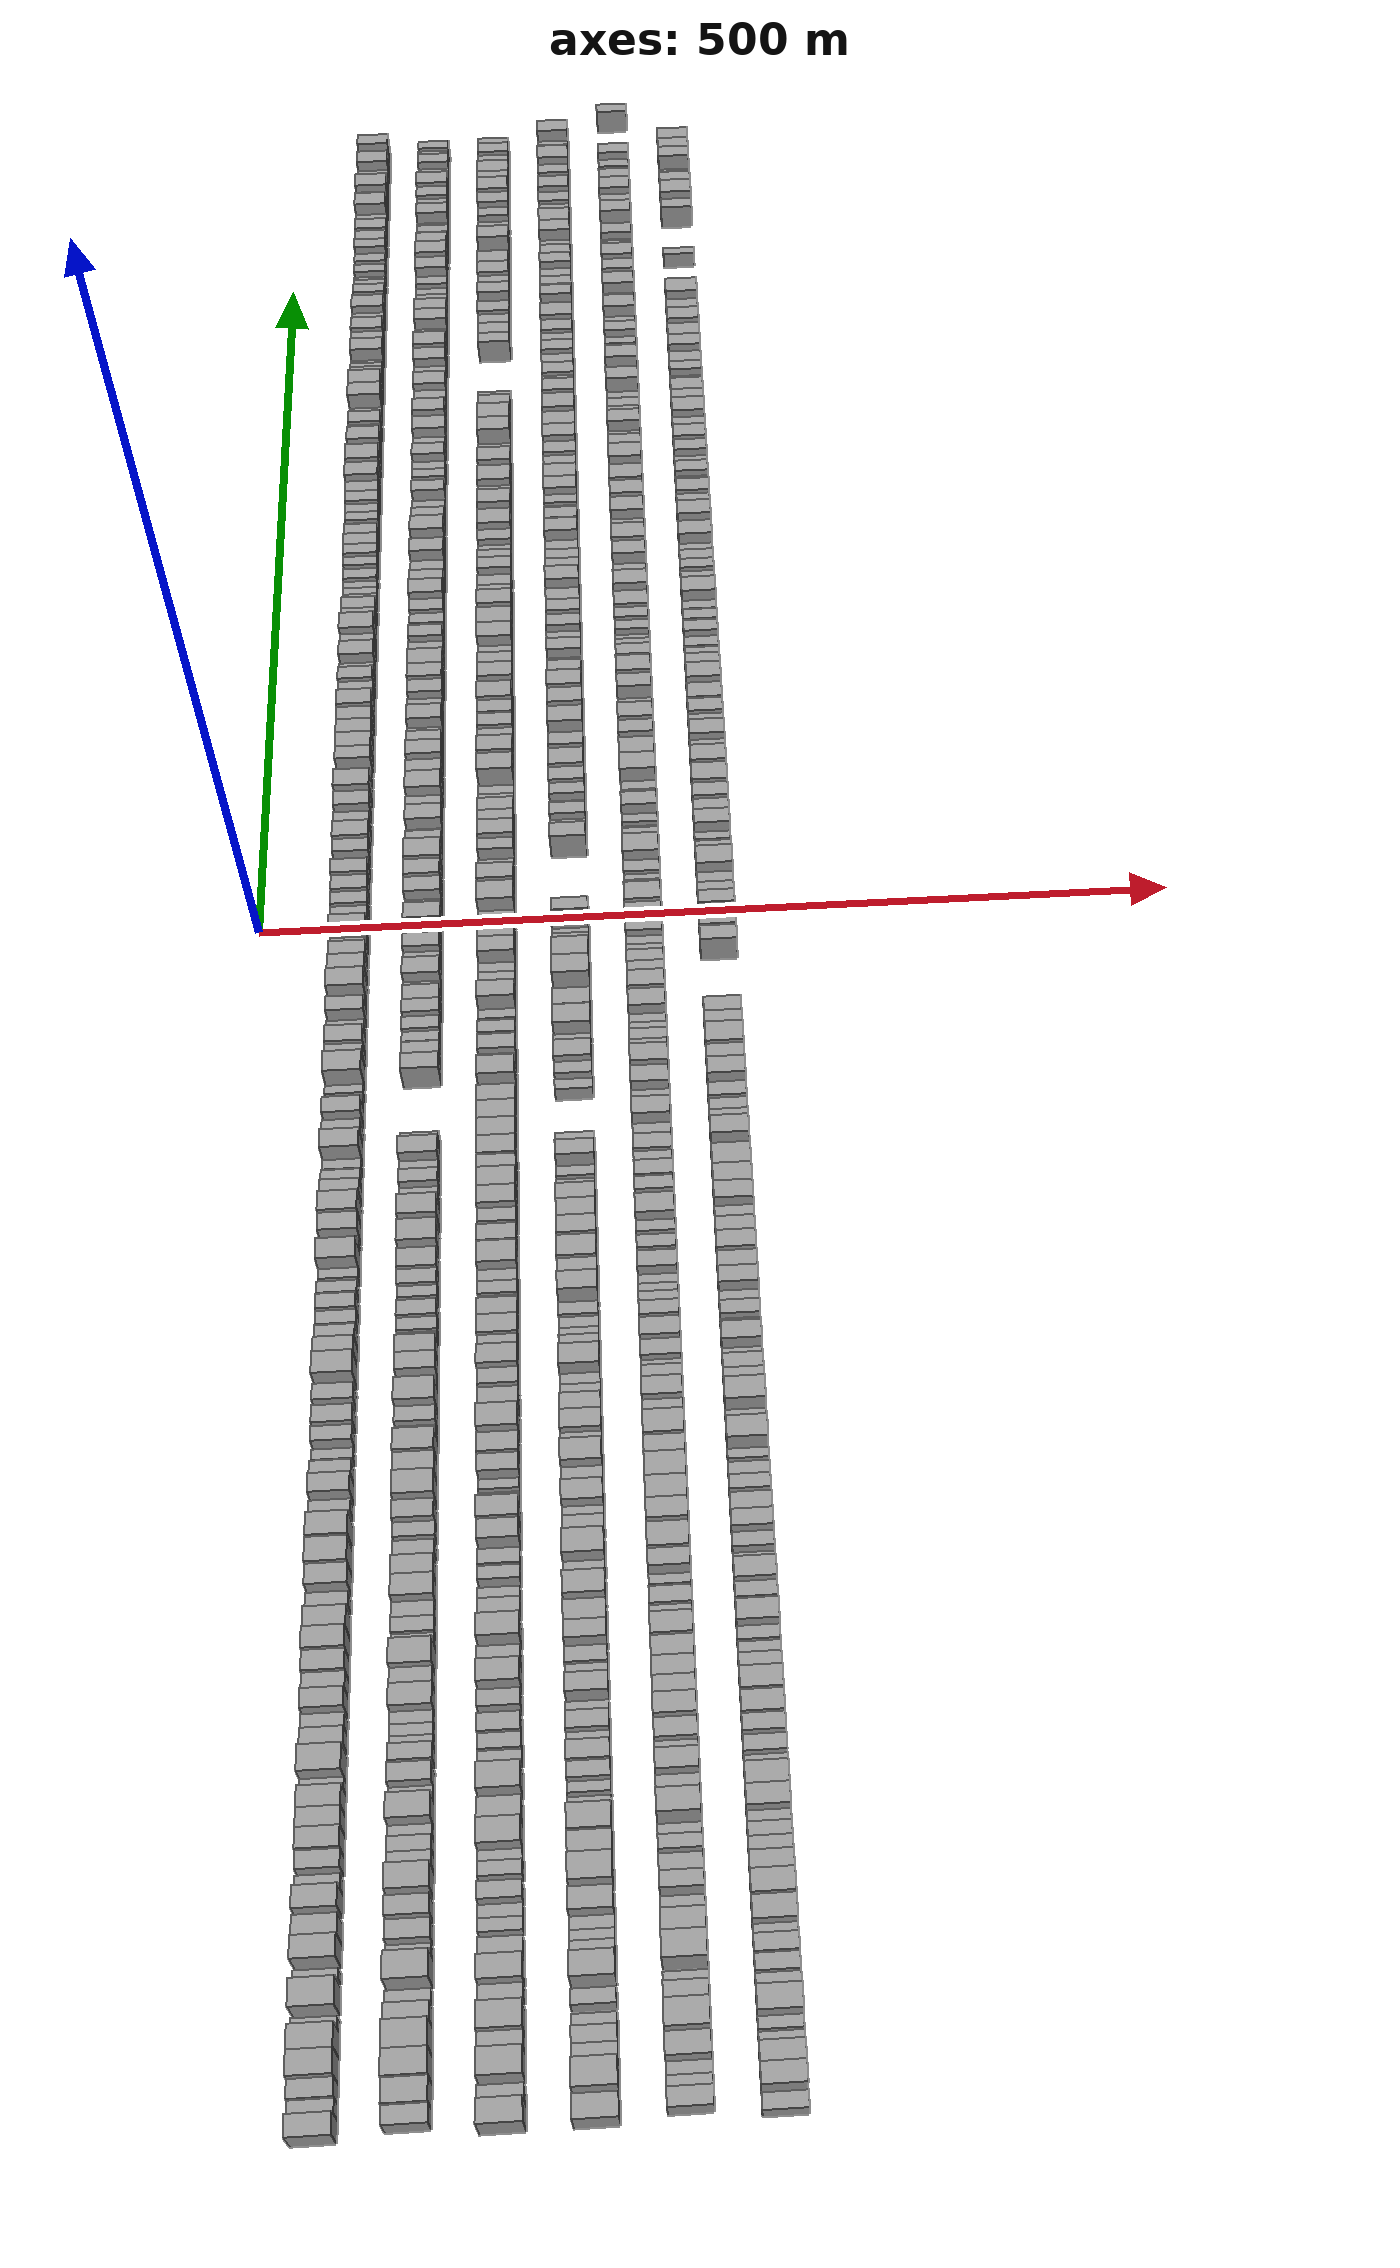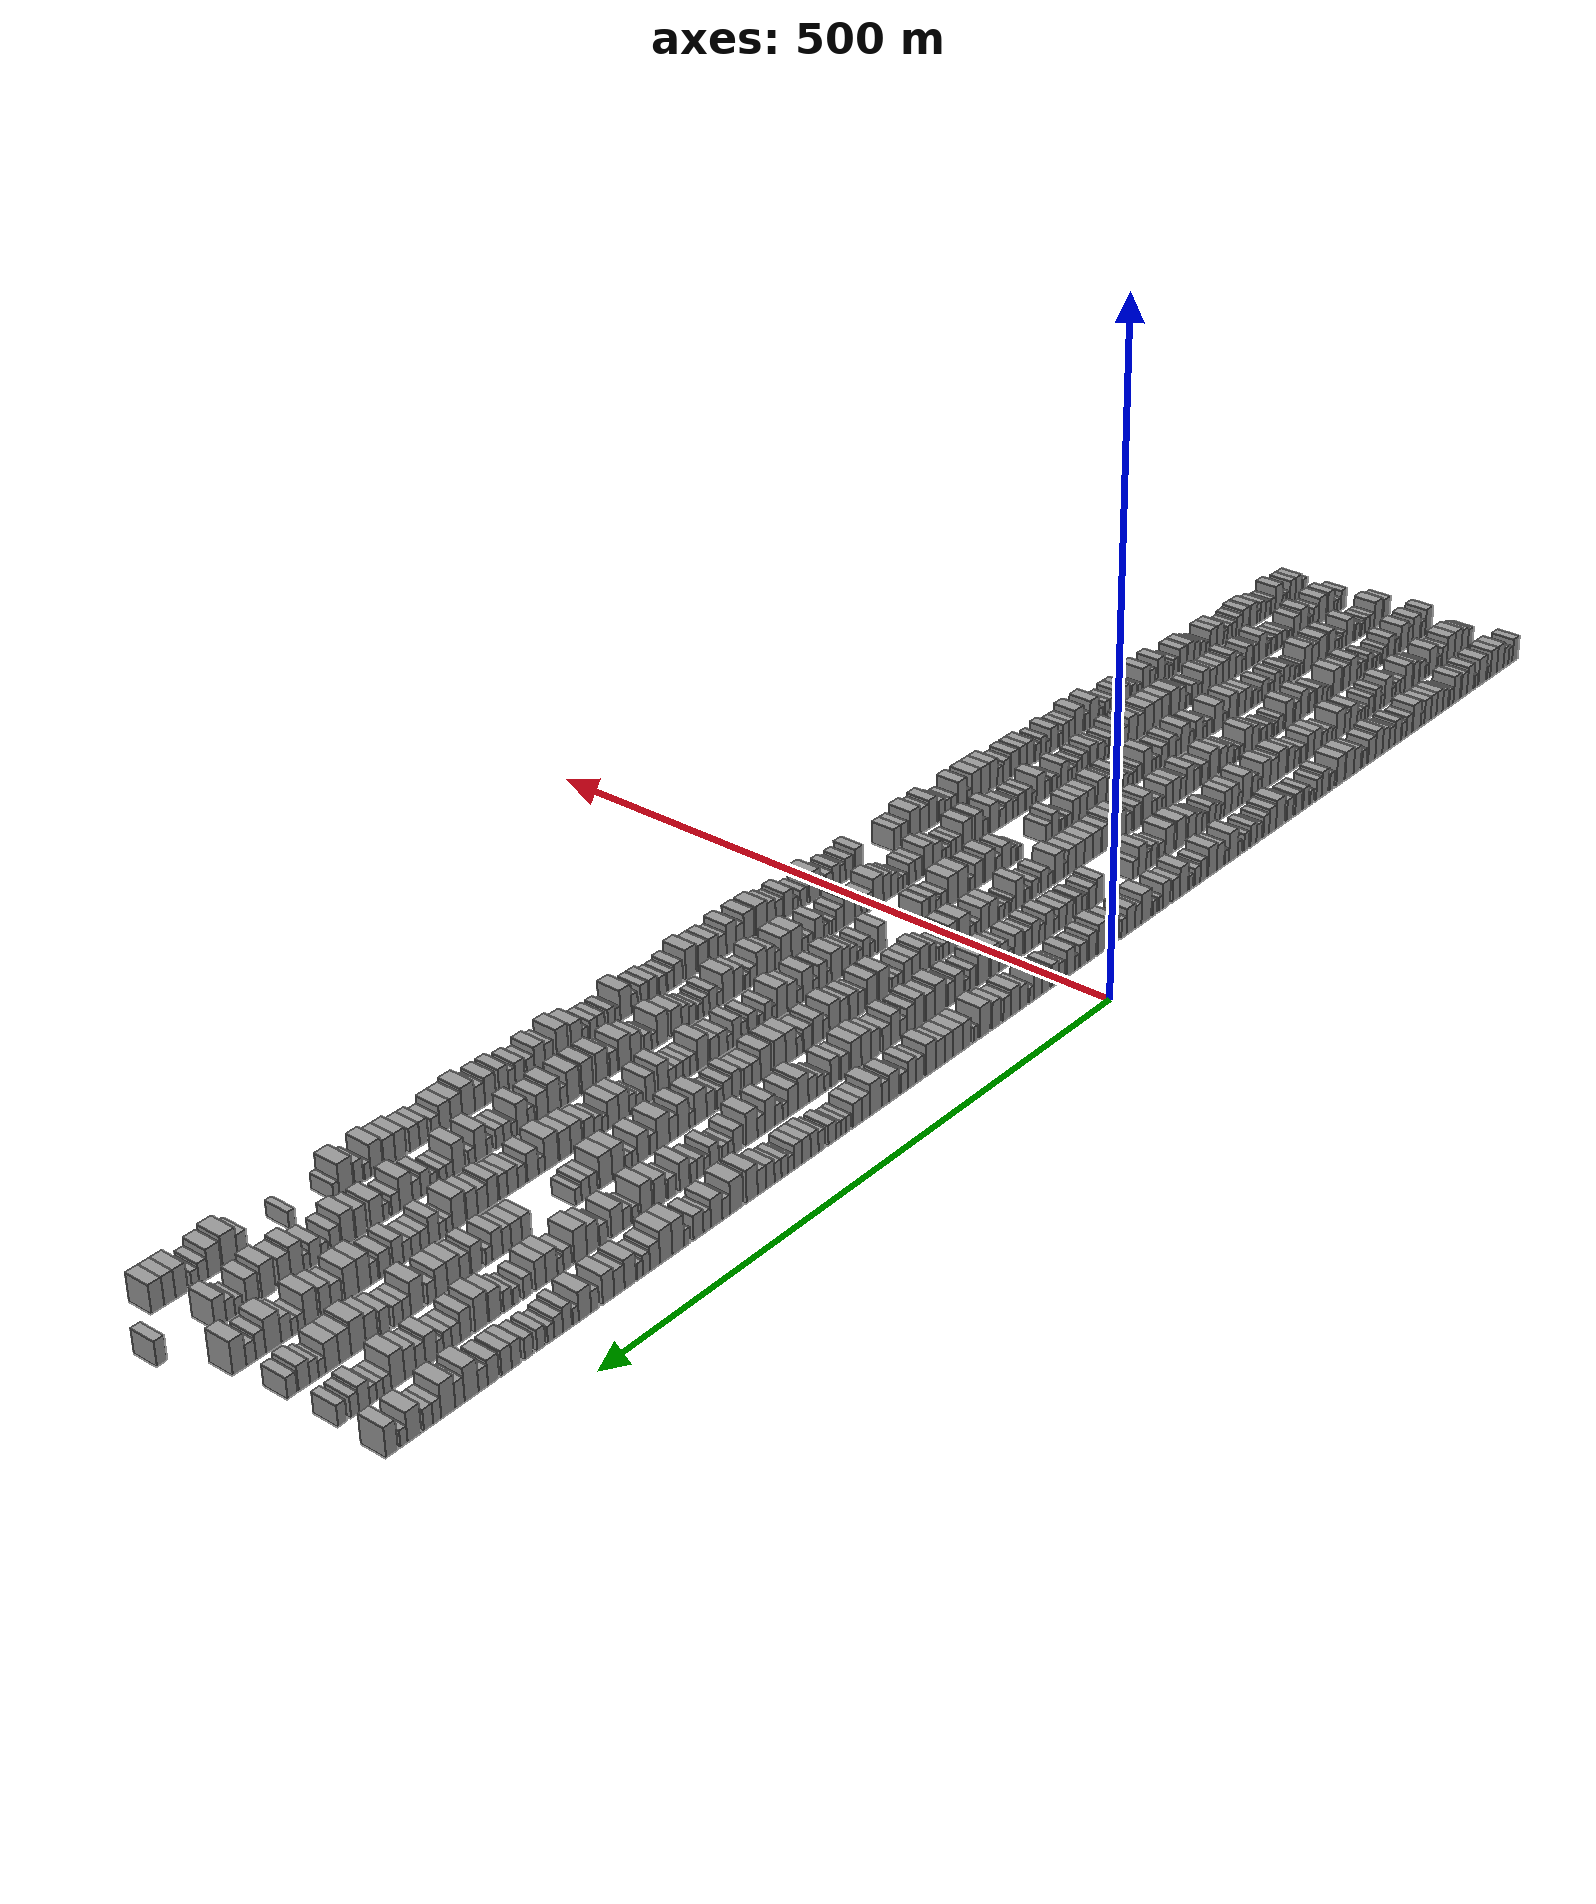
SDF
<sdf version="1.6">
 <world name="default">
  <scene>
   <sky><clouds><speed>12</speed></clouds></sky>
   <ambient>0.4 0.4 0.4 1</ambient>
   <background>0.7 0.7 0.7 1</background>
   <shadows>1</shadows>
  </scene>
  <gravity>0 0 -9.8066</gravity>
  <magnetic_field>6e-06 2.3e-05 -4.2e-05</magnetic_field>
  <physics default="0" name="default_physics" type="ode">
   <ode>
    <solver>
     <type>quick</type>
     <iters>10</iters>
     <sor>1.0</sor>
     <use_dynamic_moi_rescaling>0</use_dynamic_moi_rescaling>
    </solver>
    <constraints>
     <cfm>0</cfm>
     <erp>0.2</erp>
     <contact_max_correcting_vel>100</contact_max_correcting_vel>
     <contact_surface_layer>0.001</contact_surface_layer>
    </constraints>
   </ode>
   <max_step_size>0.004</max_step_size>
   <real_time_factor>1</real_time_factor>
   <real_time_update_rate>250</real_time_update_rate>
  </physics>
  <light name="sun" type="directional">
   <pose>0 0 10 0 0 0</pose>
   <diffuse>0.8 0.8 0.8 1</diffuse>
   <specular>0.2 0.2 0.2 1</specular>
   <attenuation>
    <range>1000</range>
    <constant>0.9</constant>
    <linear>0.01</linear>
    <quadratic>0.001</quadratic>
   </attenuation>
   <direction>-0.5 0.1 -0.9</direction>
  </light>
  <model name="building_1">
   <static>1</static>
   <pose>50.0000 -615.3688 0 0.000000 0.000000 0.000000</pose>
   <link name="link">
    <pose>0 0 10.50 0 0 0</pose>
    <collision name="collision"><geometry><box><size>20.0000 9.2623 21.0000</size></box></geometry></collision>
    <visual name="visual">
     <cast_shadows>0</cast_shadows>
     <geometry><box><size>20.0000 9.2623 21.0000</size></box></geometry>
     <material>
      <script>
       <uri>model://grey_wall/materials/scripts</uri>
       <uri>model://grey_wall/materials/textures</uri>
       <name>vrc/grey_wall</name>
      </script>
     </material>
    </visual>
   </link>
  </model>
  <model name="building_2">
   <static>1</static>
   <pose>50.0000 -607.5455 0 0.000000 0.000000 0.000000</pose>
   <link name="link">
    <pose>0 0 7.50 0 0 0</pose>
    <collision name="collision"><geometry><box><size>20.0000 6.3844 15.0000</size></box></geometry></collision>
    <visual name="visual">
     <cast_shadows>0</cast_shadows>
     <geometry><box><size>20.0000 6.3844 15.0000</size></box></geometry>
     <material>
      <script>
       <uri>model://grey_wall/materials/scripts</uri>
       <uri>model://grey_wall/materials/textures</uri>
       <name>vrc/grey_wall</name>
      </script>
     </material>
    </visual>
   </link>
  </model>
  <model name="building_3">
   <static>1</static>
   <pose>50.0000 -600.3956 0 0.000000 0.000000 0.000000</pose>
   <link name="link">
    <pose>0 0 9.00 0 0 0</pose>
    <collision name="collision"><geometry><box><size>20.0000 7.9152 18.0000</size></box></geometry></collision>
    <visual name="visual">
     <cast_shadows>0</cast_shadows>
     <geometry><box><size>20.0000 7.9152 18.0000</size></box></geometry>
     <material>
      <script>
       <uri>model://grey_wall/materials/scripts</uri>
       <uri>model://grey_wall/materials/textures</uri>
       <name>vrc/grey_wall</name>
      </script>
     </material>
    </visual>
   </link>
  </model>
  <model name="building_4">
   <static>1</static>
   <pose>50.0000 -591.1614 0 0.000000 0.000000 0.000000</pose>
   <link name="link">
    <pose>0 0 12.00 0 0 0</pose>
    <collision name="collision"><geometry><box><size>20.0000 10.5532 24.0000</size></box></geometry></collision>
    <visual name="visual">
     <cast_shadows>0</cast_shadows>
     <geometry><box><size>20.0000 10.5532 24.0000</size></box></geometry>
     <material>
      <script>
       <uri>model://grey_wall/materials/scripts</uri>
       <uri>model://grey_wall/materials/textures</uri>
       <name>vrc/grey_wall</name>
      </script>
     </material>
    </visual>
   </link>
  </model>
  <model name="building_5">
   <static>1</static>
   <pose>50.0000 -580.7091 0 0.000000 0.000000 0.000000</pose>
   <link name="link">
    <pose>0 0 12.00 0 0 0</pose>
    <collision name="collision"><geometry><box><size>20.0000 10.3514 24.0000</size></box></geometry></collision>
    <visual name="visual">
     <cast_shadows>0</cast_shadows>
     <geometry><box><size>20.0000 10.3514 24.0000</size></box></geometry>
     <material>
      <script>
       <uri>model://grey_wall/materials/scripts</uri>
       <uri>model://grey_wall/materials/textures</uri>
       <name>vrc/grey_wall</name>
      </script>
     </material>
    </visual>
   </link>
  </model>
  <model name="building_6">
   <static>1</static>
   <pose>50.0000 -573.1301 0 0.000000 0.000000 0.000000</pose>
   <link name="link">
    <pose>0 0 6.00 0 0 0</pose>
    <collision name="collision"><geometry><box><size>20.0000 4.8065 12.0000</size></box></geometry></collision>
    <visual name="visual">
     <cast_shadows>0</cast_shadows>
     <geometry><box><size>20.0000 4.8065 12.0000</size></box></geometry>
     <material>
      <script>
       <uri>model://grey_wall/materials/scripts</uri>
       <uri>model://grey_wall/materials/textures</uri>
       <name>vrc/grey_wall</name>
      </script>
     </material>
    </visual>
   </link>
  </model>
  <model name="building_7">
   <static>1</static>
   <pose>50.0000 -562.8004 0 0.000000 0.000000 0.000000</pose>
   <link name="link">
    <pose>0 0 12.00 0 0 0</pose>
    <collision name="collision"><geometry><box><size>20.0000 11.8529 24.0000</size></box></geometry></collision>
    <visual name="visual">
     <cast_shadows>0</cast_shadows>
     <geometry><box><size>20.0000 11.8529 24.0000</size></box></geometry>
     <material>
      <script>
       <uri>model://grey_wall/materials/scripts</uri>
       <uri>model://grey_wall/materials/textures</uri>
       <name>vrc/grey_wall</name>
      </script>
     </material>
    </visual>
   </link>
  </model>
  <model name="building_8">
   <static>1</static>
   <pose>50.0000 -553.4416 0 0.000000 0.000000 0.000000</pose>
   <link name="link">
    <pose>0 0 6.00 0 0 0</pose>
    <collision name="collision"><geometry><box><size>20.0000 4.8649 12.0000</size></box></geometry></collision>
    <visual name="visual">
     <cast_shadows>0</cast_shadows>
     <geometry><box><size>20.0000 4.8649 12.0000</size></box></geometry>
     <material>
      <script>
       <uri>model://grey_wall/materials/scripts</uri>
       <uri>model://grey_wall/materials/textures</uri>
       <name>vrc/grey_wall</name>
      </script>
     </material>
    </visual>
   </link>
  </model>
  <model name="building_9">
   <static>1</static>
   <pose>50.0000 -544.0691 0 0.000000 0.000000 0.000000</pose>
   <link name="link">
    <pose>0 0 12.00 0 0 0</pose>
    <collision name="collision"><geometry><box><size>20.0000 9.8800 24.0000</size></box></geometry></collision>
    <visual name="visual">
     <cast_shadows>0</cast_shadows>
     <geometry><box><size>20.0000 9.8800 24.0000</size></box></geometry>
     <material>
      <script>
       <uri>model://grey_wall/materials/scripts</uri>
       <uri>model://grey_wall/materials/textures</uri>
       <name>vrc/grey_wall</name>
      </script>
     </material>
    </visual>
   </link>
  </model>
  <model name="building_10">
   <static>1</static>
   <pose>50.0000 -534.5308 0 0.000000 0.000000 0.000000</pose>
   <link name="link">
    <pose>0 0 10.50 0 0 0</pose>
    <collision name="collision"><geometry><box><size>20.0000 9.1967 21.0000</size></box></geometry></collision>
    <visual name="visual">
     <cast_shadows>0</cast_shadows>
     <geometry><box><size>20.0000 9.1967 21.0000</size></box></geometry>
     <material>
      <script>
       <uri>model://grey_wall/materials/scripts</uri>
       <uri>model://grey_wall/materials/textures</uri>
       <name>vrc/grey_wall</name>
      </script>
     </material>
    </visual>
   </link>
  </model>
  <model name="building_11">
   <static>1</static>
   <pose>50.0000 -523.0204 0 0.000000 0.000000 0.000000</pose>
   <link name="link">
    <pose>0 0 12.00 0 0 0</pose>
    <collision name="collision"><geometry><box><size>20.0000 9.8240 24.0000</size></box></geometry></collision>
    <visual name="visual">
     <cast_shadows>0</cast_shadows>
     <geometry><box><size>20.0000 9.8240 24.0000</size></box></geometry>
     <material>
      <script>
       <uri>model://grey_wall/materials/scripts</uri>
       <uri>model://grey_wall/materials/textures</uri>
       <name>vrc/grey_wall</name>
      </script>
     </material>
    </visual>
   </link>
  </model>
  <model name="building_12">
   <static>1</static>
   <pose>50.0000 -514.8953 0 0.000000 0.000000 0.000000</pose>
   <link name="link">
    <pose>0 0 7.50 0 0 0</pose>
    <collision name="collision"><geometry><box><size>20.0000 6.4262 15.0000</size></box></geometry></collision>
    <visual name="visual">
     <cast_shadows>0</cast_shadows>
     <geometry><box><size>20.0000 6.4262 15.0000</size></box></geometry>
     <material>
      <script>
       <uri>model://grey_wall/materials/scripts</uri>
       <uri>model://grey_wall/materials/textures</uri>
       <name>vrc/grey_wall</name>
      </script>
     </material>
    </visual>
   </link>
  </model>
  <model name="building_13">
   <static>1</static>
   <pose>50.0000 -505.6441 0 0.000000 0.000000 0.000000</pose>
   <link name="link">
    <pose>0 0 9.00 0 0 0</pose>
    <collision name="collision"><geometry><box><size>20.0000 8.0763 18.0000</size></box></geometry></collision>
    <visual name="visual">
     <cast_shadows>0</cast_shadows>
     <geometry><box><size>20.0000 8.0763 18.0000</size></box></geometry>
     <material>
      <script>
       <uri>model://grey_wall/materials/scripts</uri>
       <uri>model://grey_wall/materials/textures</uri>
       <name>vrc/grey_wall</name>
      </script>
     </material>
    </visual>
   </link>
  </model>
  <model name="building_14">
   <static>1</static>
   <pose>50.0000 -496.8923 0 0.000000 0.000000 0.000000</pose>
   <link name="link">
    <pose>0 0 10.50 0 0 0</pose>
    <collision name="collision"><geometry><box><size>20.0000 9.4271 21.0000</size></box></geometry></collision>
    <visual name="visual">
     <cast_shadows>0</cast_shadows>
     <geometry><box><size>20.0000 9.4271 21.0000</size></box></geometry>
     <material>
      <script>
       <uri>model://grey_wall/materials/scripts</uri>
       <uri>model://grey_wall/materials/textures</uri>
       <name>vrc/grey_wall</name>
      </script>
     </material>
    </visual>
   </link>
  </model>
  <model name="building_15">
   <static>1</static>
   <pose>50.0000 -487.8517 0 0.000000 0.000000 0.000000</pose>
   <link name="link">
    <pose>0 0 10.50 0 0 0</pose>
    <collision name="collision"><geometry><box><size>20.0000 8.6542 21.0000</size></box></geometry></collision>
    <visual name="visual">
     <cast_shadows>0</cast_shadows>
     <geometry><box><size>20.0000 8.6542 21.0000</size></box></geometry>
     <material>
      <script>
       <uri>model://grey_wall/materials/scripts</uri>
       <uri>model://grey_wall/materials/textures</uri>
       <name>vrc/grey_wall</name>
      </script>
     </material>
    </visual>
   </link>
  </model>
  <model name="building_16">
   <static>1</static>
   <pose>50.0000 -478.7148 0 0.000000 0.000000 0.000000</pose>
   <link name="link">
    <pose>0 0 10.50 0 0 0</pose>
    <collision name="collision"><geometry><box><size>20.0000 9.6195 21.0000</size></box></geometry></collision>
    <visual name="visual">
     <cast_shadows>0</cast_shadows>
     <geometry><box><size>20.0000 9.6195 21.0000</size></box></geometry>
     <material>
      <script>
       <uri>model://grey_wall/materials/scripts</uri>
       <uri>model://grey_wall/materials/textures</uri>
       <name>vrc/grey_wall</name>
      </script>
     </material>
    </visual>
   </link>
  </model>
  <model name="building_17">
   <static>1</static>
   <pose>50.0000 -471.1349 0 0.000000 0.000000 0.000000</pose>
   <link name="link">
    <pose>0 0 6.00 0 0 0</pose>
    <collision name="collision"><geometry><box><size>20.0000 5.5403 12.0000</size></box></geometry></collision>
    <visual name="visual">
     <cast_shadows>0</cast_shadows>
     <geometry><box><size>20.0000 5.5403 12.0000</size></box></geometry>
     <material>
      <script>
       <uri>model://grey_wall/materials/scripts</uri>
       <uri>model://grey_wall/materials/textures</uri>
       <name>vrc/grey_wall</name>
      </script>
     </material>
    </visual>
   </link>
  </model>
  <model name="building_18">
   <static>1</static>
   <pose>50.0000 -462.3846 0 0.000000 0.000000 0.000000</pose>
   <link name="link">
    <pose>0 0 12.00 0 0 0</pose>
    <collision name="collision"><geometry><box><size>20.0000 11.9603 24.0000</size></box></geometry></collision>
    <visual name="visual">
     <cast_shadows>0</cast_shadows>
     <geometry><box><size>20.0000 11.9603 24.0000</size></box></geometry>
     <material>
      <script>
       <uri>model://grey_wall/materials/scripts</uri>
       <uri>model://grey_wall/materials/textures</uri>
       <name>vrc/grey_wall</name>
      </script>
     </material>
    </visual>
   </link>
  </model>
  <model name="building_19">
   <static>1</static>
   <pose>50.0000 -451.2160 0 0.000000 0.000000 0.000000</pose>
   <link name="link">
    <pose>0 0 9.00 0 0 0</pose>
    <collision name="collision"><geometry><box><size>20.0000 8.3768 18.0000</size></box></geometry></collision>
    <visual name="visual">
     <cast_shadows>0</cast_shadows>
     <geometry><box><size>20.0000 8.3768 18.0000</size></box></geometry>
     <material>
      <script>
       <uri>model://grey_wall/materials/scripts</uri>
       <uri>model://grey_wall/materials/textures</uri>
       <name>vrc/grey_wall</name>
      </script>
     </material>
    </visual>
   </link>
  </model>
  <model name="building_20">
   <static>1</static>
   <pose>50.0000 -443.4394 0 0.000000 0.000000 0.000000</pose>
   <link name="link">
    <pose>0 0 7.50 0 0 0</pose>
    <collision name="collision"><geometry><box><size>20.0000 7.1763 15.0000</size></box></geometry></collision>
    <visual name="visual">
     <cast_shadows>0</cast_shadows>
     <geometry><box><size>20.0000 7.1763 15.0000</size></box></geometry>
     <material>
      <script>
       <uri>model://grey_wall/materials/scripts</uri>
       <uri>model://grey_wall/materials/textures</uri>
       <name>vrc/grey_wall</name>
      </script>
     </material>
    </visual>
   </link>
  </model>
  <model name="building_21">
   <static>1</static>
   <pose>50.0000 -434.3271 0 0.000000 0.000000 0.000000</pose>
   <link name="link">
    <pose>0 0 10.50 0 0 0</pose>
    <collision name="collision"><geometry><box><size>20.0000 9.0483 21.0000</size></box></geometry></collision>
    <visual name="visual">
     <cast_shadows>0</cast_shadows>
     <geometry><box><size>20.0000 9.0483 21.0000</size></box></geometry>
     <material>
      <script>
       <uri>model://grey_wall/materials/scripts</uri>
       <uri>model://grey_wall/materials/textures</uri>
       <name>vrc/grey_wall</name>
      </script>
     </material>
    </visual>
   </link>
  </model>
  <model name="building_22">
   <static>1</static>
   <pose>50.0000 -425.7287 0 0.000000 0.000000 0.000000</pose>
   <link name="link">
    <pose>0 0 9.00 0 0 0</pose>
    <collision name="collision"><geometry><box><size>20.0000 8.1485 18.0000</size></box></geometry></collision>
    <visual name="visual">
     <cast_shadows>0</cast_shadows>
     <geometry><box><size>20.0000 8.1485 18.0000</size></box></geometry>
     <material>
      <script>
       <uri>model://grey_wall/materials/scripts</uri>
       <uri>model://grey_wall/materials/textures</uri>
       <name>vrc/grey_wall</name>
      </script>
     </material>
    </visual>
   </link>
  </model>
  <model name="building_23">
   <static>1</static>
   <pose>50.0000 -416.8544 0 0.000000 0.000000 0.000000</pose>
   <link name="link">
    <pose>0 0 10.50 0 0 0</pose>
    <collision name="collision"><geometry><box><size>20.0000 9.6000 21.0000</size></box></geometry></collision>
    <visual name="visual">
     <cast_shadows>0</cast_shadows>
     <geometry><box><size>20.0000 9.6000 21.0000</size></box></geometry>
     <material>
      <script>
       <uri>model://grey_wall/materials/scripts</uri>
       <uri>model://grey_wall/materials/textures</uri>
       <name>vrc/grey_wall</name>
      </script>
     </material>
    </visual>
   </link>
  </model>
  <model name="building_24">
   <static>1</static>
   <pose>50.0000 -406.9556 0 0.000000 0.000000 0.000000</pose>
   <link name="link">
    <pose>0 0 12.00 0 0 0</pose>
    <collision name="collision"><geometry><box><size>20.0000 10.1977 24.0000</size></box></geometry></collision>
    <visual name="visual">
     <cast_shadows>0</cast_shadows>
     <geometry><box><size>20.0000 10.1977 24.0000</size></box></geometry>
     <material>
      <script>
       <uri>model://grey_wall/materials/scripts</uri>
       <uri>model://grey_wall/materials/textures</uri>
       <name>vrc/grey_wall</name>
      </script>
     </material>
    </visual>
   </link>
  </model>
  <model name="building_25">
   <static>1</static>
   <pose>50.0000 -396.6169 0 0.000000 0.000000 0.000000</pose>
   <link name="link">
    <pose>0 0 10.50 0 0 0</pose>
    <collision name="collision"><geometry><box><size>20.0000 10.4796 21.0000</size></box></geometry></collision>
    <visual name="visual">
     <cast_shadows>0</cast_shadows>
     <geometry><box><size>20.0000 10.4796 21.0000</size></box></geometry>
     <material>
      <script>
       <uri>model://grey_wall/materials/scripts</uri>
       <uri>model://grey_wall/materials/textures</uri>
       <name>vrc/grey_wall</name>
      </script>
     </material>
    </visual>
   </link>
  </model>
  <model name="building_26">
   <static>1</static>
   <pose>50.0000 -386.0305 0 0.000000 0.000000 0.000000</pose>
   <link name="link">
    <pose>0 0 7.50 0 0 0</pose>
    <collision name="collision"><geometry><box><size>20.0000 6.6933 15.0000</size></box></geometry></collision>
    <visual name="visual">
     <cast_shadows>0</cast_shadows>
     <geometry><box><size>20.0000 6.6933 15.0000</size></box></geometry>
     <material>
      <script>
       <uri>model://grey_wall/materials/scripts</uri>
       <uri>model://grey_wall/materials/textures</uri>
       <name>vrc/grey_wall</name>
      </script>
     </material>
    </visual>
   </link>
  </model>
  <model name="building_27">
   <static>1</static>
   <pose>50.0000 -375.7547 0 0.000000 0.000000 0.000000</pose>
   <link name="link">
    <pose>0 0 10.50 0 0 0</pose>
    <collision name="collision"><geometry><box><size>20.0000 9.8581 21.0000</size></box></geometry></collision>
    <visual name="visual">
     <cast_shadows>0</cast_shadows>
     <geometry><box><size>20.0000 9.8581 21.0000</size></box></geometry>
     <material>
      <script>
       <uri>model://grey_wall/materials/scripts</uri>
       <uri>model://grey_wall/materials/textures</uri>
       <name>vrc/grey_wall</name>
      </script>
     </material>
    </visual>
   </link>
  </model>
  <model name="building_28">
   <static>1</static>
   <pose>50.0000 -364.8453 0 0.000000 0.000000 0.000000</pose>
   <link name="link">
    <pose>0 0 12.00 0 0 0</pose>
    <collision name="collision"><geometry><box><size>20.0000 11.9608 24.0000</size></box></geometry></collision>
    <visual name="visual">
     <cast_shadows>0</cast_shadows>
     <geometry><box><size>20.0000 11.9608 24.0000</size></box></geometry>
     <material>
      <script>
       <uri>model://grey_wall/materials/scripts</uri>
       <uri>model://grey_wall/materials/textures</uri>
       <name>vrc/grey_wall</name>
      </script>
     </material>
    </visual>
   </link>
  </model>
  <model name="building_29">
   <static>1</static>
   <pose>50.0000 -352.1958 0 0.000000 0.000000 0.000000</pose>
   <link name="link">
    <pose>0 0 12.00 0 0 0</pose>
    <collision name="collision"><geometry><box><size>20.0000 11.3382 24.0000</size></box></geometry></collision>
    <visual name="visual">
     <cast_shadows>0</cast_shadows>
     <geometry><box><size>20.0000 11.3382 24.0000</size></box></geometry>
     <material>
      <script>
       <uri>model://grey_wall/materials/scripts</uri>
       <uri>model://grey_wall/materials/textures</uri>
       <name>vrc/grey_wall</name>
      </script>
     </material>
    </visual>
   </link>
  </model>
  <model name="building_30">
   <static>1</static>
   <pose>50.0000 -340.3901 0 0.000000 0.000000 0.000000</pose>
   <link name="link">
    <pose>0 0 7.50 0 0 0</pose>
    <collision name="collision"><geometry><box><size>20.0000 6.2733 15.0000</size></box></geometry></collision>
    <visual name="visual">
     <cast_shadows>0</cast_shadows>
     <geometry><box><size>20.0000 6.2733 15.0000</size></box></geometry>
     <material>
      <script>
       <uri>model://grey_wall/materials/scripts</uri>
       <uri>model://grey_wall/materials/textures</uri>
       <name>vrc/grey_wall</name>
      </script>
     </material>
    </visual>
   </link>
  </model>
  <model name="building_31">
   <static>1</static>
   <pose>50.0000 -330.5463 0 0.000000 0.000000 0.000000</pose>
   <link name="link">
    <pose>0 0 10.50 0 0 0</pose>
    <collision name="collision"><geometry><box><size>20.0000 9.4141 21.0000</size></box></geometry></collision>
    <visual name="visual">
     <cast_shadows>0</cast_shadows>
     <geometry><box><size>20.0000 9.4141 21.0000</size></box></geometry>
     <material>
      <script>
       <uri>model://grey_wall/materials/scripts</uri>
       <uri>model://grey_wall/materials/textures</uri>
       <name>vrc/grey_wall</name>
      </script>
     </material>
    </visual>
   </link>
  </model>
  <model name="building_32">
   <static>1</static>
   <pose>50.0000 -322.0904 0 0.000000 0.000000 0.000000</pose>
   <link name="link">
    <pose>0 0 9.00 0 0 0</pose>
    <collision name="collision"><geometry><box><size>20.0000 7.4976 18.0000</size></box></geometry></collision>
    <visual name="visual">
     <cast_shadows>0</cast_shadows>
     <geometry><box><size>20.0000 7.4976 18.0000</size></box></geometry>
     <material>
      <script>
       <uri>model://grey_wall/materials/scripts</uri>
       <uri>model://grey_wall/materials/textures</uri>
       <name>vrc/grey_wall</name>
      </script>
     </material>
    </visual>
   </link>
  </model>
  <model name="building_33">
   <static>1</static>
   <pose>50.0000 -312.6850 0 0.000000 0.000000 0.000000</pose>
   <link name="link">
    <pose>0 0 6.00 0 0 0</pose>
    <collision name="collision"><geometry><box><size>20.0000 5.3132 12.0000</size></box></geometry></collision>
    <visual name="visual">
     <cast_shadows>0</cast_shadows>
     <geometry><box><size>20.0000 5.3132 12.0000</size></box></geometry>
     <material>
      <script>
       <uri>model://grey_wall/materials/scripts</uri>
       <uri>model://grey_wall/materials/textures</uri>
       <name>vrc/grey_wall</name>
      </script>
     </material>
    </visual>
   </link>
  </model>
  <model name="building_34">
   <static>1</static>
   <pose>50.0000 -304.2819 0 0.000000 0.000000 0.000000</pose>
   <link name="link">
    <pose>0 0 9.00 0 0 0</pose>
    <collision name="collision"><geometry><box><size>20.0000 7.4931 18.0000</size></box></geometry></collision>
    <visual name="visual">
     <cast_shadows>0</cast_shadows>
     <geometry><box><size>20.0000 7.4931 18.0000</size></box></geometry>
     <material>
      <script>
       <uri>model://grey_wall/materials/scripts</uri>
       <uri>model://grey_wall/materials/textures</uri>
       <name>vrc/grey_wall</name>
      </script>
     </material>
    </visual>
   </link>
  </model>
  <model name="building_35">
   <static>1</static>
   <pose>50.0000 -294.1068 0 0.000000 0.000000 0.000000</pose>
   <link name="link">
    <pose>0 0 9.00 0 0 0</pose>
    <collision name="collision"><geometry><box><size>20.0000 8.8571 18.0000</size></box></geometry></collision>
    <visual name="visual">
     <cast_shadows>0</cast_shadows>
     <geometry><box><size>20.0000 8.8571 18.0000</size></box></geometry>
     <material>
      <script>
       <uri>model://grey_wall/materials/scripts</uri>
       <uri>model://grey_wall/materials/textures</uri>
       <name>vrc/grey_wall</name>
      </script>
     </material>
    </visual>
   </link>
  </model>
  <model name="building_36">
   <static>1</static>
   <pose>50.0000 -282.5300 0 0.000000 0.000000 0.000000</pose>
   <link name="link">
    <pose>0 0 9.00 0 0 0</pose>
    <collision name="collision"><geometry><box><size>20.0000 8.2965 18.0000</size></box></geometry></collision>
    <visual name="visual">
     <cast_shadows>0</cast_shadows>
     <geometry><box><size>20.0000 8.2965 18.0000</size></box></geometry>
     <material>
      <script>
       <uri>model://grey_wall/materials/scripts</uri>
       <uri>model://grey_wall/materials/textures</uri>
       <name>vrc/grey_wall</name>
      </script>
     </material>
    </visual>
   </link>
  </model>
  <model name="building_37">
   <static>1</static>
   <pose>50.0000 -269.6448 0 0.000000 0.000000 0.000000</pose>
   <link name="link">
    <pose>0 0 12.00 0 0 0</pose>
    <collision name="collision"><geometry><box><size>20.0000 11.4740 24.0000</size></box></geometry></collision>
    <visual name="visual">
     <cast_shadows>0</cast_shadows>
     <geometry><box><size>20.0000 11.4740 24.0000</size></box></geometry>
     <material>
      <script>
       <uri>model://grey_wall/materials/scripts</uri>
       <uri>model://grey_wall/materials/textures</uri>
       <name>vrc/grey_wall</name>
      </script>
     </material>
    </visual>
   </link>
  </model>
  <model name="building_38">
   <static>1</static>
   <pose>50.0000 -259.3152 0 0.000000 0.000000 0.000000</pose>
   <link name="link">
    <pose>0 0 10.50 0 0 0</pose>
    <collision name="collision"><geometry><box><size>20.0000 9.1851 21.0000</size></box></geometry></collision>
    <visual name="visual">
     <cast_shadows>0</cast_shadows>
     <geometry><box><size>20.0000 9.1851 21.0000</size></box></geometry>
     <material>
      <script>
       <uri>model://grey_wall/materials/scripts</uri>
       <uri>model://grey_wall/materials/textures</uri>
       <name>vrc/grey_wall</name>
      </script>
     </material>
    </visual>
   </link>
  </model>
  <model name="building_39">
   <static>1</static>
   <pose>50.0000 -250.9108 0 0.000000 0.000000 0.000000</pose>
   <link name="link">
    <pose>0 0 9.00 0 0 0</pose>
    <collision name="collision"><geometry><box><size>20.0000 7.6237 18.0000</size></box></geometry></collision>
    <visual name="visual">
     <cast_shadows>0</cast_shadows>
     <geometry><box><size>20.0000 7.6237 18.0000</size></box></geometry>
     <material>
      <script>
       <uri>model://grey_wall/materials/scripts</uri>
       <uri>model://grey_wall/materials/textures</uri>
       <name>vrc/grey_wall</name>
      </script>
     </material>
    </visual>
   </link>
  </model>
  <model name="building_40">
   <static>1</static>
   <pose>50.0000 -241.4930 0 0.000000 0.000000 0.000000</pose>
   <link name="link">
    <pose>0 0 7.50 0 0 0</pose>
    <collision name="collision"><geometry><box><size>20.0000 7.2121 15.0000</size></box></geometry></collision>
    <visual name="visual">
     <cast_shadows>0</cast_shadows>
     <geometry><box><size>20.0000 7.2121 15.0000</size></box></geometry>
     <material>
      <script>
       <uri>model://grey_wall/materials/scripts</uri>
       <uri>model://grey_wall/materials/textures</uri>
       <name>vrc/grey_wall</name>
      </script>
     </material>
    </visual>
   </link>
  </model>
  <model name="building_41">
   <static>1</static>
   <pose>50.0000 -233.9153 0 0.000000 0.000000 0.000000</pose>
   <link name="link">
    <pose>0 0 9.00 0 0 0</pose>
    <collision name="collision"><geometry><box><size>20.0000 7.9432 18.0000</size></box></geometry></collision>
    <visual name="visual">
     <cast_shadows>0</cast_shadows>
     <geometry><box><size>20.0000 7.9432 18.0000</size></box></geometry>
     <material>
      <script>
       <uri>model://grey_wall/materials/scripts</uri>
       <uri>model://grey_wall/materials/textures</uri>
       <name>vrc/grey_wall</name>
      </script>
     </material>
    </visual>
   </link>
  </model>
  <model name="building_42">
   <static>1</static>
   <pose>50.0000 -224.8299 0 0.000000 0.000000 0.000000</pose>
   <link name="link">
    <pose>0 0 7.50 0 0 0</pose>
    <collision name="collision"><geometry><box><size>20.0000 6.2277 15.0000</size></box></geometry></collision>
    <visual name="visual">
     <cast_shadows>0</cast_shadows>
     <geometry><box><size>20.0000 6.2277 15.0000</size></box></geometry>
     <material>
      <script>
       <uri>model://grey_wall/materials/scripts</uri>
       <uri>model://grey_wall/materials/textures</uri>
       <name>vrc/grey_wall</name>
      </script>
     </material>
    </visual>
   </link>
  </model>
  <model name="building_43">
   <static>1</static>
   <pose>50.0000 -216.0131 0 0.000000 0.000000 0.000000</pose>
   <link name="link">
    <pose>0 0 6.00 0 0 0</pose>
    <collision name="collision"><geometry><box><size>20.0000 5.4060 12.0000</size></box></geometry></collision>
    <visual name="visual">
     <cast_shadows>0</cast_shadows>
     <geometry><box><size>20.0000 5.4060 12.0000</size></box></geometry>
     <material>
      <script>
       <uri>model://grey_wall/materials/scripts</uri>
       <uri>model://grey_wall/materials/textures</uri>
       <name>vrc/grey_wall</name>
      </script>
     </material>
    </visual>
   </link>
  </model>
  <model name="building_44">
   <static>1</static>
   <pose>50.0000 -207.7265 0 0.000000 0.000000 0.000000</pose>
   <link name="link">
    <pose>0 0 12.00 0 0 0</pose>
    <collision name="collision"><geometry><box><size>20.0000 11.1671 24.0000</size></box></geometry></collision>
    <visual name="visual">
     <cast_shadows>0</cast_shadows>
     <geometry><box><size>20.0000 11.1671 24.0000</size></box></geometry>
     <material>
      <script>
       <uri>model://grey_wall/materials/scripts</uri>
       <uri>model://grey_wall/materials/textures</uri>
       <name>vrc/grey_wall</name>
      </script>
     </material>
    </visual>
   </link>
  </model>
  <model name="building_45">
   <static>1</static>
   <pose>50.0000 -199.4984 0 0.000000 0.000000 0.000000</pose>
   <link name="link">
    <pose>0 0 6.00 0 0 0</pose>
    <collision name="collision"><geometry><box><size>20.0000 5.2892 12.0000</size></box></geometry></collision>
    <visual name="visual">
     <cast_shadows>0</cast_shadows>
     <geometry><box><size>20.0000 5.2892 12.0000</size></box></geometry>
     <material>
      <script>
       <uri>model://grey_wall/materials/scripts</uri>
       <uri>model://grey_wall/materials/textures</uri>
       <name>vrc/grey_wall</name>
      </script>
     </material>
    </visual>
   </link>
  </model>
  <model name="building_46">
   <static>1</static>
   <pose>50.0000 -191.0502 0 0.000000 0.000000 0.000000</pose>
   <link name="link">
    <pose>0 0 10.50 0 0 0</pose>
    <collision name="collision"><geometry><box><size>20.0000 9.6072 21.0000</size></box></geometry></collision>
    <visual name="visual">
     <cast_shadows>0</cast_shadows>
     <geometry><box><size>20.0000 9.6072 21.0000</size></box></geometry>
     <material>
      <script>
       <uri>model://grey_wall/materials/scripts</uri>
       <uri>model://grey_wall/materials/textures</uri>
       <name>vrc/grey_wall</name>
      </script>
     </material>
    </visual>
   </link>
  </model>
  <model name="building_47">
   <static>1</static>
   <pose>50.0000 -180.8765 0 0.000000 0.000000 0.000000</pose>
   <link name="link">
    <pose>0 0 12.00 0 0 0</pose>
    <collision name="collision"><geometry><box><size>20.0000 10.7401 24.0000</size></box></geometry></collision>
    <visual name="visual">
     <cast_shadows>0</cast_shadows>
     <geometry><box><size>20.0000 10.7401 24.0000</size></box></geometry>
     <material>
      <script>
       <uri>model://grey_wall/materials/scripts</uri>
       <uri>model://grey_wall/materials/textures</uri>
       <name>vrc/grey_wall</name>
      </script>
     </material>
    </visual>
   </link>
  </model>
  <model name="building_48">
   <static>1</static>
   <pose>50.0000 -169.5506 0 0.000000 0.000000 0.000000</pose>
   <link name="link">
    <pose>0 0 9.00 0 0 0</pose>
    <collision name="collision"><geometry><box><size>20.0000 7.9117 18.0000</size></box></geometry></collision>
    <visual name="visual">
     <cast_shadows>0</cast_shadows>
     <geometry><box><size>20.0000 7.9117 18.0000</size></box></geometry>
     <material>
      <script>
       <uri>model://grey_wall/materials/scripts</uri>
       <uri>model://grey_wall/materials/textures</uri>
       <name>vrc/grey_wall</name>
      </script>
     </material>
    </visual>
   </link>
  </model>
  <model name="building_49">
   <static>1</static>
   <pose>50.0000 -162.0605 0 0.000000 0.000000 0.000000</pose>
   <link name="link">
    <pose>0 0 7.50 0 0 0</pose>
    <collision name="collision"><geometry><box><size>20.0000 7.0684 15.0000</size></box></geometry></collision>
    <visual name="visual">
     <cast_shadows>0</cast_shadows>
     <geometry><box><size>20.0000 7.0684 15.0000</size></box></geometry>
     <material>
      <script>
       <uri>model://grey_wall/materials/scripts</uri>
       <uri>model://grey_wall/materials/textures</uri>
       <name>vrc/grey_wall</name>
      </script>
     </material>
    </visual>
   </link>
  </model>
  <model name="building_50">
   <static>1</static>
   <pose>50.0000 -153.7753 0 0.000000 0.000000 0.000000</pose>
   <link name="link">
    <pose>0 0 6.00 0 0 0</pose>
    <collision name="collision"><geometry><box><size>20.0000 5.5020 12.0000</size></box></geometry></collision>
    <visual name="visual">
     <cast_shadows>0</cast_shadows>
     <geometry><box><size>20.0000 5.5020 12.0000</size></box></geometry>
     <material>
      <script>
       <uri>model://grey_wall/materials/scripts</uri>
       <uri>model://grey_wall/materials/textures</uri>
       <name>vrc/grey_wall</name>
      </script>
     </material>
    </visual>
   </link>
  </model>
  <model name="building_51">
   <static>1</static>
   <pose>50.0000 -144.7977 0 0.000000 0.000000 0.000000</pose>
   <link name="link">
    <pose>0 0 12.00 0 0 0</pose>
    <collision name="collision"><geometry><box><size>20.0000 10.4533 24.0000</size></box></geometry></collision>
    <visual name="visual">
     <cast_shadows>0</cast_shadows>
     <geometry><box><size>20.0000 10.4533 24.0000</size></box></geometry>
     <material>
      <script>
       <uri>model://grey_wall/materials/scripts</uri>
       <uri>model://grey_wall/materials/textures</uri>
       <name>vrc/grey_wall</name>
      </script>
     </material>
    </visual>
   </link>
  </model>
  <model name="building_52">
   <static>1</static>
   <pose>50.0000 -135.1730 0 0.000000 0.000000 0.000000</pose>
   <link name="link">
    <pose>0 0 9.00 0 0 0</pose>
    <collision name="collision"><geometry><box><size>20.0000 8.7961 18.0000</size></box></geometry></collision>
    <visual name="visual">
     <cast_shadows>0</cast_shadows>
     <geometry><box><size>20.0000 8.7961 18.0000</size></box></geometry>
     <material>
      <script>
       <uri>model://grey_wall/materials/scripts</uri>
       <uri>model://grey_wall/materials/textures</uri>
       <name>vrc/grey_wall</name>
      </script>
     </material>
    </visual>
   </link>
  </model>
  <model name="building_53">
   <static>1</static>
   <pose>50.0000 -123.1936 0 0.000000 0.000000 0.000000</pose>
   <link name="link">
    <pose>0 0 10.50 0 0 0</pose>
    <collision name="collision"><geometry><box><size>20.0000 9.1625 21.0000</size></box></geometry></collision>
    <visual name="visual">
     <cast_shadows>0</cast_shadows>
     <geometry><box><size>20.0000 9.1625 21.0000</size></box></geometry>
     <material>
      <script>
       <uri>model://grey_wall/materials/scripts</uri>
       <uri>model://grey_wall/materials/textures</uri>
       <name>vrc/grey_wall</name>
      </script>
     </material>
    </visual>
   </link>
  </model>
  <model name="building_54">
   <static>1</static>
   <pose>50.0000 -116.1149 0 0.000000 0.000000 0.000000</pose>
   <link name="link">
    <pose>0 0 6.00 0 0 0</pose>
    <collision name="collision"><geometry><box><size>20.0000 4.9950 12.0000</size></box></geometry></collision>
    <visual name="visual">
     <cast_shadows>0</cast_shadows>
     <geometry><box><size>20.0000 4.9950 12.0000</size></box></geometry>
     <material>
      <script>
       <uri>model://grey_wall/materials/scripts</uri>
       <uri>model://grey_wall/materials/textures</uri>
       <name>vrc/grey_wall</name>
      </script>
     </material>
    </visual>
   </link>
  </model>
  <model name="building_55">
   <static>1</static>
   <pose>50.0000 -109.1459 0 0.000000 0.000000 0.000000</pose>
   <link name="link">
    <pose>0 0 6.00 0 0 0</pose>
    <collision name="collision"><geometry><box><size>20.0000 4.9430 12.0000</size></box></geometry></collision>
    <visual name="visual">
     <cast_shadows>0</cast_shadows>
     <geometry><box><size>20.0000 4.9430 12.0000</size></box></geometry>
     <material>
      <script>
       <uri>model://grey_wall/materials/scripts</uri>
       <uri>model://grey_wall/materials/textures</uri>
       <name>vrc/grey_wall</name>
      </script>
     </material>
    </visual>
   </link>
  </model>
  <model name="building_56">
   <static>1</static>
   <pose>50.0000 -98.7004 0 0.000000 0.000000 0.000000</pose>
   <link name="link">
    <pose>0 0 12.00 0 0 0</pose>
    <collision name="collision"><geometry><box><size>20.0000 11.9479 24.0000</size></box></geometry></collision>
    <visual name="visual">
     <cast_shadows>0</cast_shadows>
     <geometry><box><size>20.0000 11.9479 24.0000</size></box></geometry>
     <material>
      <script>
       <uri>model://grey_wall/materials/scripts</uri>
       <uri>model://grey_wall/materials/textures</uri>
       <name>vrc/grey_wall</name>
      </script>
     </material>
    </visual>
   </link>
  </model>
  <model name="building_57">
   <static>1</static>
   <pose>50.0000 -88.8313 0 0.000000 0.000000 0.000000</pose>
   <link name="link">
    <pose>0 0 9.00 0 0 0</pose>
    <collision name="collision"><geometry><box><size>20.0000 7.7903 18.0000</size></box></geometry></collision>
    <visual name="visual">
     <cast_shadows>0</cast_shadows>
     <geometry><box><size>20.0000 7.7903 18.0000</size></box></geometry>
     <material>
      <script>
       <uri>model://grey_wall/materials/scripts</uri>
       <uri>model://grey_wall/materials/textures</uri>
       <name>vrc/grey_wall</name>
      </script>
     </material>
    </visual>
   </link>
  </model>
  <model name="building_58">
   <static>1</static>
   <pose>50.0000 -80.0118 0 0.000000 0.000000 0.000000</pose>
   <link name="link">
    <pose>0 0 10.50 0 0 0</pose>
    <collision name="collision"><geometry><box><size>20.0000 9.8487 21.0000</size></box></geometry></collision>
    <visual name="visual">
     <cast_shadows>0</cast_shadows>
     <geometry><box><size>20.0000 9.8487 21.0000</size></box></geometry>
     <material>
      <script>
       <uri>model://grey_wall/materials/scripts</uri>
       <uri>model://grey_wall/materials/textures</uri>
       <name>vrc/grey_wall</name>
      </script>
     </material>
    </visual>
   </link>
  </model>
  <model name="building_59">
   <static>1</static>
   <pose>50.0000 -71.8478 0 0.000000 0.000000 0.000000</pose>
   <link name="link">
    <pose>0 0 7.50 0 0 0</pose>
    <collision name="collision"><geometry><box><size>20.0000 6.4791 15.0000</size></box></geometry></collision>
    <visual name="visual">
     <cast_shadows>0</cast_shadows>
     <geometry><box><size>20.0000 6.4791 15.0000</size></box></geometry>
     <material>
      <script>
       <uri>model://grey_wall/materials/scripts</uri>
       <uri>model://grey_wall/materials/textures</uri>
       <name>vrc/grey_wall</name>
      </script>
     </material>
    </visual>
   </link>
  </model>
  <model name="building_60">
   <static>1</static>
   <pose>50.0000 -61.2861 0 0.000000 0.000000 0.000000</pose>
   <link name="link">
    <pose>0 0 10.50 0 0 0</pose>
    <collision name="collision"><geometry><box><size>20.0000 8.6444 21.0000</size></box></geometry></collision>
    <visual name="visual">
     <cast_shadows>0</cast_shadows>
     <geometry><box><size>20.0000 8.6444 21.0000</size></box></geometry>
     <material>
      <script>
       <uri>model://grey_wall/materials/scripts</uri>
       <uri>model://grey_wall/materials/textures</uri>
       <name>vrc/grey_wall</name>
      </script>
     </material>
    </visual>
   </link>
  </model>
  <model name="building_61">
   <static>1</static>
   <pose>50.0000 -54.5059 0 0.000000 0.000000 0.000000</pose>
   <link name="link">
    <pose>0 0 6.00 0 0 0</pose>
    <collision name="collision"><geometry><box><size>20.0000 4.9159 12.0000</size></box></geometry></collision>
    <visual name="visual">
     <cast_shadows>0</cast_shadows>
     <geometry><box><size>20.0000 4.9159 12.0000</size></box></geometry>
     <material>
      <script>
       <uri>model://grey_wall/materials/scripts</uri>
       <uri>model://grey_wall/materials/textures</uri>
       <name>vrc/grey_wall</name>
      </script>
     </material>
    </visual>
   </link>
  </model>
  <model name="building_62">
   <static>1</static>
   <pose>50.0000 -46.4623 0 0.000000 0.000000 0.000000</pose>
   <link name="link">
    <pose>0 0 12.00 0 0 0</pose>
    <collision name="collision"><geometry><box><size>20.0000 11.1713 24.0000</size></box></geometry></collision>
    <visual name="visual">
     <cast_shadows>0</cast_shadows>
     <geometry><box><size>20.0000 11.1713 24.0000</size></box></geometry>
     <material>
      <script>
       <uri>model://grey_wall/materials/scripts</uri>
       <uri>model://grey_wall/materials/textures</uri>
       <name>vrc/grey_wall</name>
      </script>
     </material>
    </visual>
   </link>
  </model>
  <model name="building_63">
   <static>1</static>
   <pose>50.0000 -34.4518 0 0.000000 0.000000 0.000000</pose>
   <link name="link">
    <pose>0 0 10.50 0 0 0</pose>
    <collision name="collision"><geometry><box><size>20.0000 8.8497 21.0000</size></box></geometry></collision>
    <visual name="visual">
     <cast_shadows>0</cast_shadows>
     <geometry><box><size>20.0000 8.8497 21.0000</size></box></geometry>
     <material>
      <script>
       <uri>model://grey_wall/materials/scripts</uri>
       <uri>model://grey_wall/materials/textures</uri>
       <name>vrc/grey_wall</name>
      </script>
     </material>
    </visual>
   </link>
  </model>
  <model name="building_64">
   <static>1</static>
   <pose>50.0000 -23.8980 0 0.000000 0.000000 0.000000</pose>
   <link name="link">
    <pose>0 0 9.00 0 0 0</pose>
    <collision name="collision"><geometry><box><size>20.0000 8.2579 18.0000</size></box></geometry></collision>
    <visual name="visual">
     <cast_shadows>0</cast_shadows>
     <geometry><box><size>20.0000 8.2579 18.0000</size></box></geometry>
     <material>
      <script>
       <uri>model://grey_wall/materials/scripts</uri>
       <uri>model://grey_wall/materials/textures</uri>
       <name>vrc/grey_wall</name>
      </script>
     </material>
    </visual>
   </link>
  </model>
  <model name="building_65">
   <static>1</static>
   <pose>50.0000 -16.3139 0 0.000000 0.000000 0.000000</pose>
   <link name="link">
    <pose>0 0 6.00 0 0 0</pose>
    <collision name="collision"><geometry><box><size>20.0000 4.9104 12.0000</size></box></geometry></collision>
    <visual name="visual">
     <cast_shadows>0</cast_shadows>
     <geometry><box><size>20.0000 4.9104 12.0000</size></box></geometry>
     <material>
      <script>
       <uri>model://grey_wall/materials/scripts</uri>
       <uri>model://grey_wall/materials/textures</uri>
       <name>vrc/grey_wall</name>
      </script>
     </material>
    </visual>
   </link>
  </model>
  <model name="building_66">
   <static>1</static>
   <pose>50.0000 -9.1267 0 0.000000 0.000000 0.000000</pose>
   <link name="link">
    <pose>0 0 10.50 0 0 0</pose>
    <collision name="collision"><geometry><box><size>20.0000 9.4640 21.0000</size></box></geometry></collision>
    <visual name="visual">
     <cast_shadows>0</cast_shadows>
     <geometry><box><size>20.0000 9.4640 21.0000</size></box></geometry>
     <material>
      <script>
       <uri>model://grey_wall/materials/scripts</uri>
       <uri>model://grey_wall/materials/textures</uri>
       <name>vrc/grey_wall</name>
      </script>
     </material>
    </visual>
   </link>
  </model>
  <model name="building_67">
   <static>1</static>
   <pose>50.0000 1.1772 0 0.000000 0.000000 0.000000</pose>
   <link name="link">
    <pose>0 0 7.50 0 0 0</pose>
    <collision name="collision"><geometry><box><size>20.0000 7.1438 15.0000</size></box></geometry></collision>
    <visual name="visual">
     <cast_shadows>0</cast_shadows>
     <geometry><box><size>20.0000 7.1438 15.0000</size></box></geometry>
     <material>
      <script>
       <uri>model://grey_wall/materials/scripts</uri>
       <uri>model://grey_wall/materials/textures</uri>
       <name>vrc/grey_wall</name>
      </script>
     </material>
    </visual>
   </link>
  </model>
  <model name="building_68">
   <static>1</static>
   <pose>50.0000 8.6131 0 0.000000 0.000000 0.000000</pose>
   <link name="link">
    <pose>0 0 9.00 0 0 0</pose>
    <collision name="collision"><geometry><box><size>20.0000 7.7280 18.0000</size></box></geometry></collision>
    <visual name="visual">
     <cast_shadows>0</cast_shadows>
     <geometry><box><size>20.0000 7.7280 18.0000</size></box></geometry>
     <material>
      <script>
       <uri>model://grey_wall/materials/scripts</uri>
       <uri>model://grey_wall/materials/textures</uri>
       <name>vrc/grey_wall</name>
      </script>
     </material>
    </visual>
   </link>
  </model>
  <model name="building_69">
   <static>1</static>
   <pose>50.0000 18.9606 0 0.000000 0.000000 0.000000</pose>
   <link name="link">
    <pose>0 0 9.00 0 0 0</pose>
    <collision name="collision"><geometry><box><size>20.0000 8.9669 18.0000</size></box></geometry></collision>
    <visual name="visual">
     <cast_shadows>0</cast_shadows>
     <geometry><box><size>20.0000 8.9669 18.0000</size></box></geometry>
     <material>
      <script>
       <uri>model://grey_wall/materials/scripts</uri>
       <uri>model://grey_wall/materials/textures</uri>
       <name>vrc/grey_wall</name>
      </script>
     </material>
    </visual>
   </link>
  </model>
  <model name="building_70">
   <static>1</static>
   <pose>50.0000 27.8779 0 0.000000 0.000000 0.000000</pose>
   <link name="link">
    <pose>0 0 10.50 0 0 0</pose>
    <collision name="collision"><geometry><box><size>20.0000 8.8678 21.0000</size></box></geometry></collision>
    <visual name="visual">
     <cast_shadows>0</cast_shadows>
     <geometry><box><size>20.0000 8.8678 21.0000</size></box></geometry>
     <material>
      <script>
       <uri>model://grey_wall/materials/scripts</uri>
       <uri>model://grey_wall/materials/textures</uri>
       <name>vrc/grey_wall</name>
      </script>
     </material>
    </visual>
   </link>
  </model>
  <model name="building_71">
   <static>1</static>
   <pose>50.0000 34.9566 0 0.000000 0.000000 0.000000</pose>
   <link name="link">
    <pose>0 0 6.00 0 0 0</pose>
    <collision name="collision"><geometry><box><size>20.0000 5.2895 12.0000</size></box></geometry></collision>
    <visual name="visual">
     <cast_shadows>0</cast_shadows>
     <geometry><box><size>20.0000 5.2895 12.0000</size></box></geometry>
     <material>
      <script>
       <uri>model://grey_wall/materials/scripts</uri>
       <uri>model://grey_wall/materials/textures</uri>
       <name>vrc/grey_wall</name>
      </script>
     </material>
    </visual>
   </link>
  </model>
  <model name="building_72">
   <static>1</static>
   <pose>50.0000 43.8413 0 0.000000 0.000000 0.000000</pose>
   <link name="link">
    <pose>0 0 9.00 0 0 0</pose>
    <collision name="collision"><geometry><box><size>20.0000 8.4801 18.0000</size></box></geometry></collision>
    <visual name="visual">
     <cast_shadows>0</cast_shadows>
     <geometry><box><size>20.0000 8.4801 18.0000</size></box></geometry>
     <material>
      <script>
       <uri>model://grey_wall/materials/scripts</uri>
       <uri>model://grey_wall/materials/textures</uri>
       <name>vrc/grey_wall</name>
      </script>
     </material>
    </visual>
   </link>
  </model>
  <model name="building_73">
   <static>1</static>
   <pose>50.0000 53.1455 0 0.000000 0.000000 0.000000</pose>
   <link name="link">
    <pose>0 0 10.50 0 0 0</pose>
    <collision name="collision"><geometry><box><size>20.0000 10.1283 21.0000</size></box></geometry></collision>
    <visual name="visual">
     <cast_shadows>0</cast_shadows>
     <geometry><box><size>20.0000 10.1283 21.0000</size></box></geometry>
     <material>
      <script>
       <uri>model://grey_wall/materials/scripts</uri>
       <uri>model://grey_wall/materials/textures</uri>
       <name>vrc/grey_wall</name>
      </script>
     </material>
    </visual>
   </link>
  </model>
  <model name="building_74">
   <static>1</static>
   <pose>50.0000 62.3128 0 0.000000 0.000000 0.000000</pose>
   <link name="link">
    <pose>0 0 9.00 0 0 0</pose>
    <collision name="collision"><geometry><box><size>20.0000 8.2062 18.0000</size></box></geometry></collision>
    <visual name="visual">
     <cast_shadows>0</cast_shadows>
     <geometry><box><size>20.0000 8.2062 18.0000</size></box></geometry>
     <material>
      <script>
       <uri>model://grey_wall/materials/scripts</uri>
       <uri>model://grey_wall/materials/textures</uri>
       <name>vrc/grey_wall</name>
      </script>
     </material>
    </visual>
   </link>
  </model>
  <model name="building_75">
   <static>1</static>
   <pose>50.0000 74.0104 0 0.000000 0.000000 0.000000</pose>
   <link name="link">
    <pose>0 0 10.50 0 0 0</pose>
    <collision name="collision"><geometry><box><size>20.0000 9.1891 21.0000</size></box></geometry></collision>
    <visual name="visual">
     <cast_shadows>0</cast_shadows>
     <geometry><box><size>20.0000 9.1891 21.0000</size></box></geometry>
     <material>
      <script>
       <uri>model://grey_wall/materials/scripts</uri>
       <uri>model://grey_wall/materials/textures</uri>
       <name>vrc/grey_wall</name>
      </script>
     </material>
    </visual>
   </link>
  </model>
  <model name="building_76">
   <static>1</static>
   <pose>50.0000 86.2270 0 0.000000 0.000000 0.000000</pose>
   <link name="link">
    <pose>0 0 12.00 0 0 0</pose>
    <collision name="collision"><geometry><box><size>20.0000 11.2441 24.0000</size></box></geometry></collision>
    <visual name="visual">
     <cast_shadows>0</cast_shadows>
     <geometry><box><size>20.0000 11.2441 24.0000</size></box></geometry>
     <material>
      <script>
       <uri>model://grey_wall/materials/scripts</uri>
       <uri>model://grey_wall/materials/textures</uri>
       <name>vrc/grey_wall</name>
      </script>
     </material>
    </visual>
   </link>
  </model>
  <model name="building_77">
   <static>1</static>
   <pose>50.0000 96.2769 0 0.000000 0.000000 0.000000</pose>
   <link name="link">
    <pose>0 0 6.00 0 0 0</pose>
    <collision name="collision"><geometry><box><size>20.0000 4.8557 12.0000</size></box></geometry></collision>
    <visual name="visual">
     <cast_shadows>0</cast_shadows>
     <geometry><box><size>20.0000 4.8557 12.0000</size></box></geometry>
     <material>
      <script>
       <uri>model://grey_wall/materials/scripts</uri>
       <uri>model://grey_wall/materials/textures</uri>
       <name>vrc/grey_wall</name>
      </script>
     </material>
    </visual>
   </link>
  </model>
  <model name="building_78">
   <static>1</static>
   <pose>50.0000 106.0245 0 0.000000 0.000000 0.000000</pose>
   <link name="link">
    <pose>0 0 10.50 0 0 0</pose>
    <collision name="collision"><geometry><box><size>20.0000 8.6394 21.0000</size></box></geometry></collision>
    <visual name="visual">
     <cast_shadows>0</cast_shadows>
     <geometry><box><size>20.0000 8.6394 21.0000</size></box></geometry>
     <material>
      <script>
       <uri>model://grey_wall/materials/scripts</uri>
       <uri>model://grey_wall/materials/textures</uri>
       <name>vrc/grey_wall</name>
      </script>
     </material>
    </visual>
   </link>
  </model>
  <model name="building_79">
   <static>1</static>
   <pose>50.0000 115.4120 0 0.000000 0.000000 0.000000</pose>
   <link name="link">
    <pose>0 0 10.50 0 0 0</pose>
    <collision name="collision"><geometry><box><size>20.0000 10.1356 21.0000</size></box></geometry></collision>
    <visual name="visual">
     <cast_shadows>0</cast_shadows>
     <geometry><box><size>20.0000 10.1356 21.0000</size></box></geometry>
     <material>
      <script>
       <uri>model://grey_wall/materials/scripts</uri>
       <uri>model://grey_wall/materials/textures</uri>
       <name>vrc/grey_wall</name>
      </script>
     </material>
    </visual>
   </link>
  </model>
  <model name="building_80">
   <static>1</static>
   <pose>50.0000 125.1478 0 0.000000 0.000000 0.000000</pose>
   <link name="link">
    <pose>0 0 10.50 0 0 0</pose>
    <collision name="collision"><geometry><box><size>20.0000 9.3362 21.0000</size></box></geometry></collision>
    <visual name="visual">
     <cast_shadows>0</cast_shadows>
     <geometry><box><size>20.0000 9.3362 21.0000</size></box></geometry>
     <material>
      <script>
       <uri>model://grey_wall/materials/scripts</uri>
       <uri>model://grey_wall/materials/textures</uri>
       <name>vrc/grey_wall</name>
      </script>
     </material>
    </visual>
   </link>
  </model>
  <model name="building_81">
   <static>1</static>
   <pose>50.0000 134.2164 0 0.000000 0.000000 0.000000</pose>
   <link name="link">
    <pose>0 0 10.50 0 0 0</pose>
    <collision name="collision"><geometry><box><size>20.0000 8.8010 21.0000</size></box></geometry></collision>
    <visual name="visual">
     <cast_shadows>0</cast_shadows>
     <geometry><box><size>20.0000 8.8010 21.0000</size></box></geometry>
     <material>
      <script>
       <uri>model://grey_wall/materials/scripts</uri>
       <uri>model://grey_wall/materials/textures</uri>
       <name>vrc/grey_wall</name>
      </script>
     </material>
    </visual>
   </link>
  </model>
  <model name="building_82">
   <static>1</static>
   <pose>50.0000 143.7720 0 0.000000 0.000000 0.000000</pose>
   <link name="link">
    <pose>0 0 12.00 0 0 0</pose>
    <collision name="collision"><geometry><box><size>20.0000 10.3101 24.0000</size></box></geometry></collision>
    <visual name="visual">
     <cast_shadows>0</cast_shadows>
     <geometry><box><size>20.0000 10.3101 24.0000</size></box></geometry>
     <material>
      <script>
       <uri>model://grey_wall/materials/scripts</uri>
       <uri>model://grey_wall/materials/textures</uri>
       <name>vrc/grey_wall</name>
      </script>
     </material>
    </visual>
   </link>
  </model>
  <model name="building_83">
   <static>1</static>
   <pose>50.0000 155.1610 0 0.000000 0.000000 0.000000</pose>
   <link name="link">
    <pose>0 0 9.00 0 0 0</pose>
    <collision name="collision"><geometry><box><size>20.0000 8.4679 18.0000</size></box></geometry></collision>
    <visual name="visual">
     <cast_shadows>0</cast_shadows>
     <geometry><box><size>20.0000 8.4679 18.0000</size></box></geometry>
     <material>
      <script>
       <uri>model://grey_wall/materials/scripts</uri>
       <uri>model://grey_wall/materials/textures</uri>
       <name>vrc/grey_wall</name>
      </script>
     </material>
    </visual>
   </link>
  </model>
  <model name="building_84">
   <static>1</static>
   <pose>50.0000 163.7331 0 0.000000 0.000000 0.000000</pose>
   <link name="link">
    <pose>0 0 10.50 0 0 0</pose>
    <collision name="collision"><geometry><box><size>20.0000 8.6764 21.0000</size></box></geometry></collision>
    <visual name="visual">
     <cast_shadows>0</cast_shadows>
     <geometry><box><size>20.0000 8.6764 21.0000</size></box></geometry>
     <material>
      <script>
       <uri>model://grey_wall/materials/scripts</uri>
       <uri>model://grey_wall/materials/textures</uri>
       <name>vrc/grey_wall</name>
      </script>
     </material>
    </visual>
   </link>
  </model>
  <model name="building_85">
   <static>1</static>
   <pose>50.0000 171.7244 0 0.000000 0.000000 0.000000</pose>
   <link name="link">
    <pose>0 0 7.50 0 0 0</pose>
    <collision name="collision"><geometry><box><size>20.0000 7.3060 15.0000</size></box></geometry></collision>
    <visual name="visual">
     <cast_shadows>0</cast_shadows>
     <geometry><box><size>20.0000 7.3060 15.0000</size></box></geometry>
     <material>
      <script>
       <uri>model://grey_wall/materials/scripts</uri>
       <uri>model://grey_wall/materials/textures</uri>
       <name>vrc/grey_wall</name>
      </script>
     </material>
    </visual>
   </link>
  </model>
  <model name="building_86">
   <static>1</static>
   <pose>50.0000 182.4433 0 0.000000 0.000000 0.000000</pose>
   <link name="link">
    <pose>0 0 10.50 0 0 0</pose>
    <collision name="collision"><geometry><box><size>20.0000 10.1318 21.0000</size></box></geometry></collision>
    <visual name="visual">
     <cast_shadows>0</cast_shadows>
     <geometry><box><size>20.0000 10.1318 21.0000</size></box></geometry>
     <material>
      <script>
       <uri>model://grey_wall/materials/scripts</uri>
       <uri>model://grey_wall/materials/textures</uri>
       <name>vrc/grey_wall</name>
      </script>
     </material>
    </visual>
   </link>
  </model>
  <model name="building_87">
   <static>1</static>
   <pose>50.0000 191.1486 0 0.000000 0.000000 0.000000</pose>
   <link name="link">
    <pose>0 0 9.00 0 0 0</pose>
    <collision name="collision"><geometry><box><size>20.0000 7.2789 18.0000</size></box></geometry></collision>
    <visual name="visual">
     <cast_shadows>0</cast_shadows>
     <geometry><box><size>20.0000 7.2789 18.0000</size></box></geometry>
     <material>
      <script>
       <uri>model://grey_wall/materials/scripts</uri>
       <uri>model://grey_wall/materials/textures</uri>
       <name>vrc/grey_wall</name>
      </script>
     </material>
    </visual>
   </link>
  </model>
  <model name="building_88">
   <static>1</static>
   <pose>50.0000 200.5249 0 0.000000 0.000000 0.000000</pose>
   <link name="link">
    <pose>0 0 12.00 0 0 0</pose>
    <collision name="collision"><geometry><box><size>20.0000 11.4737 24.0000</size></box></geometry></collision>
    <visual name="visual">
     <cast_shadows>0</cast_shadows>
     <geometry><box><size>20.0000 11.4737 24.0000</size></box></geometry>
     <material>
      <script>
       <uri>model://grey_wall/materials/scripts</uri>
       <uri>model://grey_wall/materials/textures</uri>
       <name>vrc/grey_wall</name>
      </script>
     </material>
    </visual>
   </link>
  </model>
  <model name="building_89">
   <static>1</static>
   <pose>50.0000 210.4406 0 0.000000 0.000000 0.000000</pose>
   <link name="link">
    <pose>0 0 9.00 0 0 0</pose>
    <collision name="collision"><geometry><box><size>20.0000 8.3578 18.0000</size></box></geometry></collision>
    <visual name="visual">
     <cast_shadows>0</cast_shadows>
     <geometry><box><size>20.0000 8.3578 18.0000</size></box></geometry>
     <material>
      <script>
       <uri>model://grey_wall/materials/scripts</uri>
       <uri>model://grey_wall/materials/textures</uri>
       <name>vrc/grey_wall</name>
      </script>
     </material>
    </visual>
   </link>
  </model>
  <model name="building_90">
   <static>1</static>
   <pose>50.0000 218.8700 0 0.000000 0.000000 0.000000</pose>
   <link name="link">
    <pose>0 0 9.00 0 0 0</pose>
    <collision name="collision"><geometry><box><size>20.0000 8.5010 18.0000</size></box></geometry></collision>
    <visual name="visual">
     <cast_shadows>0</cast_shadows>
     <geometry><box><size>20.0000 8.5010 18.0000</size></box></geometry>
     <material>
      <script>
       <uri>model://grey_wall/materials/scripts</uri>
       <uri>model://grey_wall/materials/textures</uri>
       <name>vrc/grey_wall</name>
      </script>
     </material>
    </visual>
   </link>
  </model>
  <model name="building_91">
   <static>1</static>
   <pose>50.0000 227.7440 0 0.000000 0.000000 0.000000</pose>
   <link name="link">
    <pose>0 0 6.00 0 0 0</pose>
    <collision name="collision"><geometry><box><size>20.0000 5.2469 12.0000</size></box></geometry></collision>
    <visual name="visual">
     <cast_shadows>0</cast_shadows>
     <geometry><box><size>20.0000 5.2469 12.0000</size></box></geometry>
     <material>
      <script>
       <uri>model://grey_wall/materials/scripts</uri>
       <uri>model://grey_wall/materials/textures</uri>
       <name>vrc/grey_wall</name>
      </script>
     </material>
    </visual>
   </link>
  </model>
  <model name="building_92">
   <static>1</static>
   <pose>50.0000 232.8507 0 0.000000 0.000000 0.000000</pose>
   <link name="link">
    <pose>0 0 6.00 0 0 0</pose>
    <collision name="collision"><geometry><box><size>20.0000 4.9665 12.0000</size></box></geometry></collision>
    <visual name="visual">
     <cast_shadows>0</cast_shadows>
     <geometry><box><size>20.0000 4.9665 12.0000</size></box></geometry>
     <material>
      <script>
       <uri>model://grey_wall/materials/scripts</uri>
       <uri>model://grey_wall/materials/textures</uri>
       <name>vrc/grey_wall</name>
      </script>
     </material>
    </visual>
   </link>
  </model>
  <model name="building_93">
   <static>1</static>
   <pose>50.0000 237.8128 0 0.000000 0.000000 0.000000</pose>
   <link name="link">
    <pose>0 0 6.00 0 0 0</pose>
    <collision name="collision"><geometry><box><size>20.0000 4.9579 12.0000</size></box></geometry></collision>
    <visual name="visual">
     <cast_shadows>0</cast_shadows>
     <geometry><box><size>20.0000 4.9579 12.0000</size></box></geometry>
     <material>
      <script>
       <uri>model://grey_wall/materials/scripts</uri>
       <uri>model://grey_wall/materials/textures</uri>
       <name>vrc/grey_wall</name>
      </script>
     </material>
    </visual>
   </link>
  </model>
  <model name="building_94">
   <static>1</static>
   <pose>50.0000 243.9733 0 0.000000 0.000000 0.000000</pose>
   <link name="link">
    <pose>0 0 7.50 0 0 0</pose>
    <collision name="collision"><geometry><box><size>20.0000 7.3631 15.0000</size></box></geometry></collision>
    <visual name="visual">
     <cast_shadows>0</cast_shadows>
     <geometry><box><size>20.0000 7.3631 15.0000</size></box></geometry>
     <material>
      <script>
       <uri>model://grey_wall/materials/scripts</uri>
       <uri>model://grey_wall/materials/textures</uri>
       <name>vrc/grey_wall</name>
      </script>
     </material>
    </visual>
   </link>
  </model>
  <model name="building_95">
   <static>1</static>
   <pose>50.0000 253.9811 0 0.000000 0.000000 0.000000</pose>
   <link name="link">
    <pose>0 0 7.50 0 0 0</pose>
    <collision name="collision"><geometry><box><size>20.0000 6.6525 15.0000</size></box></geometry></collision>
    <visual name="visual">
     <cast_shadows>0</cast_shadows>
     <geometry><box><size>20.0000 6.6525 15.0000</size></box></geometry>
     <material>
      <script>
       <uri>model://grey_wall/materials/scripts</uri>
       <uri>model://grey_wall/materials/textures</uri>
       <name>vrc/grey_wall</name>
      </script>
     </material>
    </visual>
   </link>
  </model>
  <model name="building_96">
   <static>1</static>
   <pose>50.0000 261.0674 0 0.000000 0.000000 0.000000</pose>
   <link name="link">
    <pose>0 0 9.00 0 0 0</pose>
    <collision name="collision"><geometry><box><size>20.0000 7.5202 18.0000</size></box></geometry></collision>
    <visual name="visual">
     <cast_shadows>0</cast_shadows>
     <geometry><box><size>20.0000 7.5202 18.0000</size></box></geometry>
     <material>
      <script>
       <uri>model://grey_wall/materials/scripts</uri>
       <uri>model://grey_wall/materials/textures</uri>
       <name>vrc/grey_wall</name>
      </script>
     </material>
    </visual>
   </link>
  </model>
  <model name="building_97">
   <static>1</static>
   <pose>50.0000 269.0079 0 0.000000 0.000000 0.000000</pose>
   <link name="link">
    <pose>0 0 9.00 0 0 0</pose>
    <collision name="collision"><geometry><box><size>20.0000 8.3607 18.0000</size></box></geometry></collision>
    <visual name="visual">
     <cast_shadows>0</cast_shadows>
     <geometry><box><size>20.0000 8.3607 18.0000</size></box></geometry>
     <material>
      <script>
       <uri>model://grey_wall/materials/scripts</uri>
       <uri>model://grey_wall/materials/textures</uri>
       <name>vrc/grey_wall</name>
      </script>
     </material>
    </visual>
   </link>
  </model>
  <model name="building_98">
   <static>1</static>
   <pose>50.0000 276.9610 0 0.000000 0.000000 0.000000</pose>
   <link name="link">
    <pose>0 0 9.00 0 0 0</pose>
    <collision name="collision"><geometry><box><size>20.0000 7.5457 18.0000</size></box></geometry></collision>
    <visual name="visual">
     <cast_shadows>0</cast_shadows>
     <geometry><box><size>20.0000 7.5457 18.0000</size></box></geometry>
     <material>
      <script>
       <uri>model://grey_wall/materials/scripts</uri>
       <uri>model://grey_wall/materials/textures</uri>
       <name>vrc/grey_wall</name>
      </script>
     </material>
    </visual>
   </link>
  </model>
  <model name="building_99">
   <static>1</static>
   <pose>50.0000 283.5942 0 0.000000 0.000000 0.000000</pose>
   <link name="link">
    <pose>0 0 6.00 0 0 0</pose>
    <collision name="collision"><geometry><box><size>20.0000 5.7207 12.0000</size></box></geometry></collision>
    <visual name="visual">
     <cast_shadows>0</cast_shadows>
     <geometry><box><size>20.0000 5.7207 12.0000</size></box></geometry>
     <material>
      <script>
       <uri>model://grey_wall/materials/scripts</uri>
       <uri>model://grey_wall/materials/textures</uri>
       <name>vrc/grey_wall</name>
      </script>
     </material>
    </visual>
   </link>
  </model>
  <model name="building_100">
   <static>1</static>
   <pose>50.0000 289.6488 0 0.000000 0.000000 0.000000</pose>
   <link name="link">
    <pose>0 0 7.50 0 0 0</pose>
    <collision name="collision"><geometry><box><size>20.0000 6.3885 15.0000</size></box></geometry></collision>
    <visual name="visual">
     <cast_shadows>0</cast_shadows>
     <geometry><box><size>20.0000 6.3885 15.0000</size></box></geometry>
     <material>
      <script>
       <uri>model://grey_wall/materials/scripts</uri>
       <uri>model://grey_wall/materials/textures</uri>
       <name>vrc/grey_wall</name>
      </script>
     </material>
    </visual>
   </link>
  </model>
  <model name="building_101">
   <static>1</static>
   <pose>50.0000 296.1106 0 0.000000 0.000000 0.000000</pose>
   <link name="link">
    <pose>0 0 7.50 0 0 0</pose>
    <collision name="collision"><geometry><box><size>20.0000 6.5351 15.0000</size></box></geometry></collision>
    <visual name="visual">
     <cast_shadows>0</cast_shadows>
     <geometry><box><size>20.0000 6.5351 15.0000</size></box></geometry>
     <material>
      <script>
       <uri>model://grey_wall/materials/scripts</uri>
       <uri>model://grey_wall/materials/textures</uri>
       <name>vrc/grey_wall</name>
      </script>
     </material>
    </visual>
   </link>
  </model>
  <model name="building_102">
   <static>1</static>
   <pose>50.0000 303.3493 0 0.000000 0.000000 0.000000</pose>
   <link name="link">
    <pose>0 0 9.00 0 0 0</pose>
    <collision name="collision"><geometry><box><size>20.0000 7.9422 18.0000</size></box></geometry></collision>
    <visual name="visual">
     <cast_shadows>0</cast_shadows>
     <geometry><box><size>20.0000 7.9422 18.0000</size></box></geometry>
     <material>
      <script>
       <uri>model://grey_wall/materials/scripts</uri>
       <uri>model://grey_wall/materials/textures</uri>
       <name>vrc/grey_wall</name>
      </script>
     </material>
    </visual>
   </link>
  </model>
  <model name="building_103">
   <static>1</static>
   <pose>50.0000 311.2941 0 0.000000 0.000000 0.000000</pose>
   <link name="link">
    <pose>0 0 9.00 0 0 0</pose>
    <collision name="collision"><geometry><box><size>20.0000 7.9475 18.0000</size></box></geometry></collision>
    <visual name="visual">
     <cast_shadows>0</cast_shadows>
     <geometry><box><size>20.0000 7.9475 18.0000</size></box></geometry>
     <material>
      <script>
       <uri>model://grey_wall/materials/scripts</uri>
       <uri>model://grey_wall/materials/textures</uri>
       <name>vrc/grey_wall</name>
      </script>
     </material>
    </visual>
   </link>
  </model>
  <model name="building_104">
   <static>1</static>
   <pose>50.0000 320.4588 0 0.000000 0.000000 0.000000</pose>
   <link name="link">
    <pose>0 0 12.00 0 0 0</pose>
    <collision name="collision"><geometry><box><size>20.0000 10.3818 24.0000</size></box></geometry></collision>
    <visual name="visual">
     <cast_shadows>0</cast_shadows>
     <geometry><box><size>20.0000 10.3818 24.0000</size></box></geometry>
     <material>
      <script>
       <uri>model://grey_wall/materials/scripts</uri>
       <uri>model://grey_wall/materials/textures</uri>
       <name>vrc/grey_wall</name>
      </script>
     </material>
    </visual>
   </link>
  </model>
  <model name="building_105">
   <static>1</static>
   <pose>50.0000 334.6109 0 0.000000 0.000000 0.000000</pose>
   <link name="link">
    <pose>0 0 12.00 0 0 0</pose>
    <collision name="collision"><geometry><box><size>20.0000 11.9225 24.0000</size></box></geometry></collision>
    <visual name="visual">
     <cast_shadows>0</cast_shadows>
     <geometry><box><size>20.0000 11.9225 24.0000</size></box></geometry>
     <material>
      <script>
       <uri>model://grey_wall/materials/scripts</uri>
       <uri>model://grey_wall/materials/textures</uri>
       <name>vrc/grey_wall</name>
      </script>
     </material>
    </visual>
   </link>
  </model>
  <model name="building_106">
   <static>1</static>
   <pose>50.0000 344.2113 0 0.000000 0.000000 0.000000</pose>
   <link name="link">
    <pose>0 0 7.50 0 0 0</pose>
    <collision name="collision"><geometry><box><size>20.0000 7.2783 15.0000</size></box></geometry></collision>
    <visual name="visual">
     <cast_shadows>0</cast_shadows>
     <geometry><box><size>20.0000 7.2783 15.0000</size></box></geometry>
     <material>
      <script>
       <uri>model://grey_wall/materials/scripts</uri>
       <uri>model://grey_wall/materials/textures</uri>
       <name>vrc/grey_wall</name>
      </script>
     </material>
    </visual>
   </link>
  </model>
  <model name="building_107">
   <static>1</static>
   <pose>50.0000 353.0232 0 0.000000 0.000000 0.000000</pose>
   <link name="link">
    <pose>0 0 10.50 0 0 0</pose>
    <collision name="collision"><geometry><box><size>20.0000 10.3456 21.0000</size></box></geometry></collision>
    <visual name="visual">
     <cast_shadows>0</cast_shadows>
     <geometry><box><size>20.0000 10.3456 21.0000</size></box></geometry>
     <material>
      <script>
       <uri>model://grey_wall/materials/scripts</uri>
       <uri>model://grey_wall/materials/textures</uri>
       <name>vrc/grey_wall</name>
      </script>
     </material>
    </visual>
   </link>
  </model>
  <model name="building_108">
   <static>1</static>
   <pose>50.0000 361.6275 0 0.000000 0.000000 0.000000</pose>
   <link name="link">
    <pose>0 0 7.50 0 0 0</pose>
    <collision name="collision"><geometry><box><size>20.0000 6.8631 15.0000</size></box></geometry></collision>
    <visual name="visual">
     <cast_shadows>0</cast_shadows>
     <geometry><box><size>20.0000 6.8631 15.0000</size></box></geometry>
     <material>
      <script>
       <uri>model://grey_wall/materials/scripts</uri>
       <uri>model://grey_wall/materials/textures</uri>
       <name>vrc/grey_wall</name>
      </script>
     </material>
    </visual>
   </link>
  </model>
  <model name="building_109">
   <static>1</static>
   <pose>50.0000 369.5474 0 0.000000 0.000000 0.000000</pose>
   <link name="link">
    <pose>0 0 9.00 0 0 0</pose>
    <collision name="collision"><geometry><box><size>20.0000 8.9766 18.0000</size></box></geometry></collision>
    <visual name="visual">
     <cast_shadows>0</cast_shadows>
     <geometry><box><size>20.0000 8.9766 18.0000</size></box></geometry>
     <material>
      <script>
       <uri>model://grey_wall/materials/scripts</uri>
       <uri>model://grey_wall/materials/textures</uri>
       <name>vrc/grey_wall</name>
      </script>
     </material>
    </visual>
   </link>
  </model>
  <model name="building_110">
   <static>1</static>
   <pose>50.0000 379.6434 0 0.000000 0.000000 0.000000</pose>
   <link name="link">
    <pose>0 0 6.00 0 0 0</pose>
    <collision name="collision"><geometry><box><size>20.0000 5.2154 12.0000</size></box></geometry></collision>
    <visual name="visual">
     <cast_shadows>0</cast_shadows>
     <geometry><box><size>20.0000 5.2154 12.0000</size></box></geometry>
     <material>
      <script>
       <uri>model://grey_wall/materials/scripts</uri>
       <uri>model://grey_wall/materials/textures</uri>
       <name>vrc/grey_wall</name>
      </script>
     </material>
    </visual>
   </link>
  </model>
  <model name="building_111">
   <static>1</static>
   <pose>50.0000 387.5300 0 0.000000 0.000000 0.000000</pose>
   <link name="link">
    <pose>0 0 12.00 0 0 0</pose>
    <collision name="collision"><geometry><box><size>20.0000 10.5576 24.0000</size></box></geometry></collision>
    <visual name="visual">
     <cast_shadows>0</cast_shadows>
     <geometry><box><size>20.0000 10.5576 24.0000</size></box></geometry>
     <material>
      <script>
       <uri>model://grey_wall/materials/scripts</uri>
       <uri>model://grey_wall/materials/textures</uri>
       <name>vrc/grey_wall</name>
      </script>
     </material>
    </visual>
   </link>
  </model>
  <model name="building_112">
   <static>1</static>
   <pose>50.0000 398.2572 0 0.000000 0.000000 0.000000</pose>
   <link name="link">
    <pose>0 0 12.00 0 0 0</pose>
    <collision name="collision"><geometry><box><size>20.0000 10.8968 24.0000</size></box></geometry></collision>
    <visual name="visual">
     <cast_shadows>0</cast_shadows>
     <geometry><box><size>20.0000 10.8968 24.0000</size></box></geometry>
     <material>
      <script>
       <uri>model://grey_wall/materials/scripts</uri>
       <uri>model://grey_wall/materials/textures</uri>
       <name>vrc/grey_wall</name>
      </script>
     </material>
    </visual>
   </link>
  </model>
  <model name="building_113">
   <static>1</static>
   <pose>50.0000 408.0470 0 0.000000 0.000000 0.000000</pose>
   <link name="link">
    <pose>0 0 9.00 0 0 0</pose>
    <collision name="collision"><geometry><box><size>20.0000 8.6829 18.0000</size></box></geometry></collision>
    <visual name="visual">
     <cast_shadows>0</cast_shadows>
     <geometry><box><size>20.0000 8.6829 18.0000</size></box></geometry>
     <material>
      <script>
       <uri>model://grey_wall/materials/scripts</uri>
       <uri>model://grey_wall/materials/textures</uri>
       <name>vrc/grey_wall</name>
      </script>
     </material>
    </visual>
   </link>
  </model>
  <model name="building_114">
   <static>1</static>
   <pose>50.0000 415.4791 0 0.000000 0.000000 0.000000</pose>
   <link name="link">
    <pose>0 0 7.50 0 0 0</pose>
    <collision name="collision"><geometry><box><size>20.0000 6.1812 15.0000</size></box></geometry></collision>
    <visual name="visual">
     <cast_shadows>0</cast_shadows>
     <geometry><box><size>20.0000 6.1812 15.0000</size></box></geometry>
     <material>
      <script>
       <uri>model://grey_wall/materials/scripts</uri>
       <uri>model://grey_wall/materials/textures</uri>
       <name>vrc/grey_wall</name>
      </script>
     </material>
    </visual>
   </link>
  </model>
  <model name="building_115">
   <static>1</static>
   <pose>50.0000 421.0990 0 0.000000 0.000000 0.000000</pose>
   <link name="link">
    <pose>0 0 6.00 0 0 0</pose>
    <collision name="collision"><geometry><box><size>20.0000 5.0586 12.0000</size></box></geometry></collision>
    <visual name="visual">
     <cast_shadows>0</cast_shadows>
     <geometry><box><size>20.0000 5.0586 12.0000</size></box></geometry>
     <material>
      <script>
       <uri>model://grey_wall/materials/scripts</uri>
       <uri>model://grey_wall/materials/textures</uri>
       <name>vrc/grey_wall</name>
      </script>
     </material>
    </visual>
   </link>
  </model>
  <model name="building_116">
   <static>1</static>
   <pose>50.0000 429.5648 0 0.000000 0.000000 0.000000</pose>
   <link name="link">
    <pose>0 0 10.50 0 0 0</pose>
    <collision name="collision"><geometry><box><size>20.0000 9.8732 21.0000</size></box></geometry></collision>
    <visual name="visual">
     <cast_shadows>0</cast_shadows>
     <geometry><box><size>20.0000 9.8732 21.0000</size></box></geometry>
     <material>
      <script>
       <uri>model://grey_wall/materials/scripts</uri>
       <uri>model://grey_wall/materials/textures</uri>
       <name>vrc/grey_wall</name>
      </script>
     </material>
    </visual>
   </link>
  </model>
  <model name="building_117">
   <static>1</static>
   <pose>50.0000 438.9637 0 0.000000 0.000000 0.000000</pose>
   <link name="link">
    <pose>0 0 9.00 0 0 0</pose>
    <collision name="collision"><geometry><box><size>20.0000 8.9246 18.0000</size></box></geometry></collision>
    <visual name="visual">
     <cast_shadows>0</cast_shadows>
     <geometry><box><size>20.0000 8.9246 18.0000</size></box></geometry>
     <material>
      <script>
       <uri>model://grey_wall/materials/scripts</uri>
       <uri>model://grey_wall/materials/textures</uri>
       <name>vrc/grey_wall</name>
      </script>
     </material>
    </visual>
   </link>
  </model>
  <model name="building_118">
   <static>1</static>
   <pose>50.0000 448.3294 0 0.000000 0.000000 0.000000</pose>
   <link name="link">
    <pose>0 0 10.50 0 0 0</pose>
    <collision name="collision"><geometry><box><size>20.0000 9.8068 21.0000</size></box></geometry></collision>
    <visual name="visual">
     <cast_shadows>0</cast_shadows>
     <geometry><box><size>20.0000 9.8068 21.0000</size></box></geometry>
     <material>
      <script>
       <uri>model://grey_wall/materials/scripts</uri>
       <uri>model://grey_wall/materials/textures</uri>
       <name>vrc/grey_wall</name>
      </script>
     </material>
    </visual>
   </link>
  </model>
  <model name="building_119">
   <static>1</static>
   <pose>50.0000 459.6302 0 0.000000 0.000000 0.000000</pose>
   <link name="link">
    <pose>0 0 7.50 0 0 0</pose>
    <collision name="collision"><geometry><box><size>20.0000 6.7948 15.0000</size></box></geometry></collision>
    <visual name="visual">
     <cast_shadows>0</cast_shadows>
     <geometry><box><size>20.0000 6.7948 15.0000</size></box></geometry>
     <material>
      <script>
       <uri>model://grey_wall/materials/scripts</uri>
       <uri>model://grey_wall/materials/textures</uri>
       <name>vrc/grey_wall</name>
      </script>
     </material>
    </visual>
   </link>
  </model>
  <model name="building_120">
   <static>1</static>
   <pose>50.0000 468.1573 0 0.000000 0.000000 0.000000</pose>
   <link name="link">
    <pose>0 0 10.50 0 0 0</pose>
    <collision name="collision"><geometry><box><size>20.0000 10.2593 21.0000</size></box></geometry></collision>
    <visual name="visual">
     <cast_shadows>0</cast_shadows>
     <geometry><box><size>20.0000 10.2593 21.0000</size></box></geometry>
     <material>
      <script>
       <uri>model://grey_wall/materials/scripts</uri>
       <uri>model://grey_wall/materials/textures</uri>
       <name>vrc/grey_wall</name>
      </script>
     </material>
    </visual>
   </link>
  </model>
  <model name="building_121">
   <static>1</static>
   <pose>50.0000 475.7291 0 0.000000 0.000000 0.000000</pose>
   <link name="link">
    <pose>0 0 6.00 0 0 0</pose>
    <collision name="collision"><geometry><box><size>20.0000 4.8845 12.0000</size></box></geometry></collision>
    <visual name="visual">
     <cast_shadows>0</cast_shadows>
     <geometry><box><size>20.0000 4.8845 12.0000</size></box></geometry>
     <material>
      <script>
       <uri>model://grey_wall/materials/scripts</uri>
       <uri>model://grey_wall/materials/textures</uri>
       <name>vrc/grey_wall</name>
      </script>
     </material>
    </visual>
   </link>
  </model>
  <model name="building_122">
   <static>1</static>
   <pose>50.0000 482.7963 0 0.000000 0.000000 0.000000</pose>
   <link name="link">
    <pose>0 0 9.00 0 0 0</pose>
    <collision name="collision"><geometry><box><size>20.0000 7.2499 18.0000</size></box></geometry></collision>
    <visual name="visual">
     <cast_shadows>0</cast_shadows>
     <geometry><box><size>20.0000 7.2499 18.0000</size></box></geometry>
     <material>
      <script>
       <uri>model://grey_wall/materials/scripts</uri>
       <uri>model://grey_wall/materials/textures</uri>
       <name>vrc/grey_wall</name>
      </script>
     </material>
    </visual>
   </link>
  </model>
  <model name="building_123">
   <static>1</static>
   <pose>50.0000 490.0557 0 0.000000 0.000000 0.000000</pose>
   <link name="link">
    <pose>0 0 7.50 0 0 0</pose>
    <collision name="collision"><geometry><box><size>20.0000 7.2689 15.0000</size></box></geometry></collision>
    <visual name="visual">
     <cast_shadows>0</cast_shadows>
     <geometry><box><size>20.0000 7.2689 15.0000</size></box></geometry>
     <material>
      <script>
       <uri>model://grey_wall/materials/scripts</uri>
       <uri>model://grey_wall/materials/textures</uri>
       <name>vrc/grey_wall</name>
      </script>
     </material>
    </visual>
   </link>
  </model>
  <model name="building_124">
   <static>1</static>
   <pose>50.0000 496.4019 0 0.000000 0.000000 0.000000</pose>
   <link name="link">
    <pose>0 0 6.00 0 0 0</pose>
    <collision name="collision"><geometry><box><size>20.0000 5.4235 12.0000</size></box></geometry></collision>
    <visual name="visual">
     <cast_shadows>0</cast_shadows>
     <geometry><box><size>20.0000 5.4235 12.0000</size></box></geometry>
     <material>
      <script>
       <uri>model://grey_wall/materials/scripts</uri>
       <uri>model://grey_wall/materials/textures</uri>
       <name>vrc/grey_wall</name>
      </script>
     </material>
    </visual>
   </link>
  </model>
  <model name="building_125">
   <static>1</static>
   <pose>50.0000 504.4912 0 0.000000 0.000000 0.000000</pose>
   <link name="link">
    <pose>0 0 7.50 0 0 0</pose>
    <collision name="collision"><geometry><box><size>20.0000 6.7550 15.0000</size></box></geometry></collision>
    <visual name="visual">
     <cast_shadows>0</cast_shadows>
     <geometry><box><size>20.0000 6.7550 15.0000</size></box></geometry>
     <material>
      <script>
       <uri>model://grey_wall/materials/scripts</uri>
       <uri>model://grey_wall/materials/textures</uri>
       <name>vrc/grey_wall</name>
      </script>
     </material>
    </visual>
   </link>
  </model>
  <model name="building_126">
   <static>1</static>
   <pose>50.0000 514.3777 0 0.000000 0.000000 0.000000</pose>
   <link name="link">
    <pose>0 0 7.50 0 0 0</pose>
    <collision name="collision"><geometry><box><size>20.0000 7.0179 15.0000</size></box></geometry></collision>
    <visual name="visual">
     <cast_shadows>0</cast_shadows>
     <geometry><box><size>20.0000 7.0179 15.0000</size></box></geometry>
     <material>
      <script>
       <uri>model://grey_wall/materials/scripts</uri>
       <uri>model://grey_wall/materials/textures</uri>
       <name>vrc/grey_wall</name>
      </script>
     </material>
    </visual>
   </link>
  </model>
  <model name="building_127">
   <static>1</static>
   <pose>50.0000 524.6020 0 0.000000 0.000000 0.000000</pose>
   <link name="link">
    <pose>0 0 9.00 0 0 0</pose>
    <collision name="collision"><geometry><box><size>20.0000 7.4308 18.0000</size></box></geometry></collision>
    <visual name="visual">
     <cast_shadows>0</cast_shadows>
     <geometry><box><size>20.0000 7.4308 18.0000</size></box></geometry>
     <material>
      <script>
       <uri>model://grey_wall/materials/scripts</uri>
       <uri>model://grey_wall/materials/textures</uri>
       <name>vrc/grey_wall</name>
      </script>
     </material>
    </visual>
   </link>
  </model>
  <model name="building_128">
   <static>1</static>
   <pose>50.0000 532.4468 0 0.000000 0.000000 0.000000</pose>
   <link name="link">
    <pose>0 0 9.00 0 0 0</pose>
    <collision name="collision"><geometry><box><size>20.0000 8.2587 18.0000</size></box></geometry></collision>
    <visual name="visual">
     <cast_shadows>0</cast_shadows>
     <geometry><box><size>20.0000 8.2587 18.0000</size></box></geometry>
     <material>
      <script>
       <uri>model://grey_wall/materials/scripts</uri>
       <uri>model://grey_wall/materials/textures</uri>
       <name>vrc/grey_wall</name>
      </script>
     </material>
    </visual>
   </link>
  </model>
  <model name="building_129">
   <static>1</static>
   <pose>50.0000 543.0096 0 0.000000 0.000000 0.000000</pose>
   <link name="link">
    <pose>0 0 9.00 0 0 0</pose>
    <collision name="collision"><geometry><box><size>20.0000 8.8668 18.0000</size></box></geometry></collision>
    <visual name="visual">
     <cast_shadows>0</cast_shadows>
     <geometry><box><size>20.0000 8.8668 18.0000</size></box></geometry>
     <material>
      <script>
       <uri>model://grey_wall/materials/scripts</uri>
       <uri>model://grey_wall/materials/textures</uri>
       <name>vrc/grey_wall</name>
      </script>
     </material>
    </visual>
   </link>
  </model>
  <model name="building_130">
   <static>1</static>
   <pose>50.0000 551.1101 0 0.000000 0.000000 0.000000</pose>
   <link name="link">
    <pose>0 0 7.50 0 0 0</pose>
    <collision name="collision"><geometry><box><size>20.0000 7.3343 15.0000</size></box></geometry></collision>
    <visual name="visual">
     <cast_shadows>0</cast_shadows>
     <geometry><box><size>20.0000 7.3343 15.0000</size></box></geometry>
     <material>
      <script>
       <uri>model://grey_wall/materials/scripts</uri>
       <uri>model://grey_wall/materials/textures</uri>
       <name>vrc/grey_wall</name>
      </script>
     </material>
    </visual>
   </link>
  </model>
  <model name="building_131">
   <static>1</static>
   <pose>50.0000 560.2596 0 0.000000 0.000000 0.000000</pose>
   <link name="link">
    <pose>0 0 12.00 0 0 0</pose>
    <collision name="collision"><geometry><box><size>20.0000 10.9645 24.0000</size></box></geometry></collision>
    <visual name="visual">
     <cast_shadows>0</cast_shadows>
     <geometry><box><size>20.0000 10.9645 24.0000</size></box></geometry>
     <material>
      <script>
       <uri>model://grey_wall/materials/scripts</uri>
       <uri>model://grey_wall/materials/textures</uri>
       <name>vrc/grey_wall</name>
      </script>
     </material>
    </visual>
   </link>
  </model>
  <model name="building_132">
   <static>1</static>
   <pose>50.0000 569.3659 0 0.000000 0.000000 0.000000</pose>
   <link name="link">
    <pose>0 0 9.00 0 0 0</pose>
    <collision name="collision"><geometry><box><size>20.0000 7.2482 18.0000</size></box></geometry></collision>
    <visual name="visual">
     <cast_shadows>0</cast_shadows>
     <geometry><box><size>20.0000 7.2482 18.0000</size></box></geometry>
     <material>
      <script>
       <uri>model://grey_wall/materials/scripts</uri>
       <uri>model://grey_wall/materials/textures</uri>
       <name>vrc/grey_wall</name>
      </script>
     </material>
    </visual>
   </link>
  </model>
  <model name="building_133">
   <static>1</static>
   <pose>50.0000 578.4641 0 0.000000 0.000000 0.000000</pose>
   <link name="link">
    <pose>0 0 12.00 0 0 0</pose>
    <collision name="collision"><geometry><box><size>20.0000 10.9482 24.0000</size></box></geometry></collision>
    <visual name="visual">
     <cast_shadows>0</cast_shadows>
     <geometry><box><size>20.0000 10.9482 24.0000</size></box></geometry>
     <material>
      <script>
       <uri>model://grey_wall/materials/scripts</uri>
       <uri>model://grey_wall/materials/textures</uri>
       <name>vrc/grey_wall</name>
      </script>
     </material>
    </visual>
   </link>
  </model>
  <model name="building_134">
   <static>1</static>
   <pose>50.0000 587.0475 0 0.000000 0.000000 0.000000</pose>
   <link name="link">
    <pose>0 0 7.50 0 0 0</pose>
    <collision name="collision"><geometry><box><size>20.0000 6.2187 15.0000</size></box></geometry></collision>
    <visual name="visual">
     <cast_shadows>0</cast_shadows>
     <geometry><box><size>20.0000 6.2187 15.0000</size></box></geometry>
     <material>
      <script>
       <uri>model://grey_wall/materials/scripts</uri>
       <uri>model://grey_wall/materials/textures</uri>
       <name>vrc/grey_wall</name>
      </script>
     </material>
    </visual>
   </link>
  </model>
  <model name="building_135">
   <static>1</static>
   <pose>50.0000 593.7524 0 0.000000 0.000000 0.000000</pose>
   <link name="link">
    <pose>0 0 7.50 0 0 0</pose>
    <collision name="collision"><geometry><box><size>20.0000 7.1911 15.0000</size></box></geometry></collision>
    <visual name="visual">
     <cast_shadows>0</cast_shadows>
     <geometry><box><size>20.0000 7.1911 15.0000</size></box></geometry>
     <material>
      <script>
       <uri>model://grey_wall/materials/scripts</uri>
       <uri>model://grey_wall/materials/textures</uri>
       <name>vrc/grey_wall</name>
      </script>
     </material>
    </visual>
   </link>
  </model>
  <model name="building_136">
   <static>1</static>
   <pose>50.0000 604.5498 0 0.000000 0.000000 0.000000</pose>
   <link name="link">
    <pose>0 0 10.50 0 0 0</pose>
    <collision name="collision"><geometry><box><size>20.0000 10.4036 21.0000</size></box></geometry></collision>
    <visual name="visual">
     <cast_shadows>0</cast_shadows>
     <geometry><box><size>20.0000 10.4036 21.0000</size></box></geometry>
     <material>
      <script>
       <uri>model://grey_wall/materials/scripts</uri>
       <uri>model://grey_wall/materials/textures</uri>
       <name>vrc/grey_wall</name>
      </script>
     </material>
    </visual>
   </link>
  </model>
  <model name="building_137">
   <static>1</static>
   <pose>50.0000 612.4491 0 0.000000 0.000000 0.000000</pose>
   <link name="link">
    <pose>0 0 6.00 0 0 0</pose>
    <collision name="collision"><geometry><box><size>20.0000 5.3950 12.0000</size></box></geometry></collision>
    <visual name="visual">
     <cast_shadows>0</cast_shadows>
     <geometry><box><size>20.0000 5.3950 12.0000</size></box></geometry>
     <material>
      <script>
       <uri>model://grey_wall/materials/scripts</uri>
       <uri>model://grey_wall/materials/textures</uri>
       <name>vrc/grey_wall</name>
      </script>
     </material>
    </visual>
   </link>
  </model>
  <model name="building_138">
   <static>1</static>
   <pose>50.0000 621.5763 0 0.000000 0.000000 0.000000</pose>
   <link name="link">
    <pose>0 0 10.50 0 0 0</pose>
    <collision name="collision"><geometry><box><size>20.0000 8.8594 21.0000</size></box></geometry></collision>
    <visual name="visual">
     <cast_shadows>0</cast_shadows>
     <geometry><box><size>20.0000 8.8594 21.0000</size></box></geometry>
     <material>
      <script>
       <uri>model://grey_wall/materials/scripts</uri>
       <uri>model://grey_wall/materials/textures</uri>
       <name>vrc/grey_wall</name>
      </script>
     </material>
    </visual>
   </link>
  </model>
  <model name="building_139">
   <static>1</static>
   <pose>90.0000 -613.0240 0 0.000000 0.000000 0.000000</pose>
   <link name="link">
    <pose>0 0 9.00 0 0 0</pose>
    <collision name="collision"><geometry><box><size>20.0000 7.9521 18.0000</size></box></geometry></collision>
    <visual name="visual">
     <cast_shadows>0</cast_shadows>
     <geometry><box><size>20.0000 7.9521 18.0000</size></box></geometry>
     <material>
      <script>
       <uri>model://grey_wall/materials/scripts</uri>
       <uri>model://grey_wall/materials/textures</uri>
       <name>vrc/grey_wall</name>
      </script>
     </material>
    </visual>
   </link>
  </model>
  <model name="building_140">
   <static>1</static>
   <pose>90.0000 -603.8902 0 0.000000 0.000000 0.000000</pose>
   <link name="link">
    <pose>0 0 10.50 0 0 0</pose>
    <collision name="collision"><geometry><box><size>20.0000 10.3154 21.0000</size></box></geometry></collision>
    <visual name="visual">
     <cast_shadows>0</cast_shadows>
     <geometry><box><size>20.0000 10.3154 21.0000</size></box></geometry>
     <material>
      <script>
       <uri>model://grey_wall/materials/scripts</uri>
       <uri>model://grey_wall/materials/textures</uri>
       <name>vrc/grey_wall</name>
      </script>
     </material>
    </visual>
   </link>
  </model>
  <model name="building_141">
   <static>1</static>
   <pose>90.0000 -593.2369 0 0.000000 0.000000 0.000000</pose>
   <link name="link">
    <pose>0 0 12.00 0 0 0</pose>
    <collision name="collision"><geometry><box><size>20.0000 10.9912 24.0000</size></box></geometry></collision>
    <visual name="visual">
     <cast_shadows>0</cast_shadows>
     <geometry><box><size>20.0000 10.9912 24.0000</size></box></geometry>
     <material>
      <script>
       <uri>model://grey_wall/materials/scripts</uri>
       <uri>model://grey_wall/materials/textures</uri>
       <name>vrc/grey_wall</name>
      </script>
     </material>
    </visual>
   </link>
  </model>
  <model name="building_142">
   <static>1</static>
   <pose>90.0000 -581.9039 0 0.000000 0.000000 0.000000</pose>
   <link name="link">
    <pose>0 0 12.00 0 0 0</pose>
    <collision name="collision"><geometry><box><size>20.0000 11.6748 24.0000</size></box></geometry></collision>
    <visual name="visual">
     <cast_shadows>0</cast_shadows>
     <geometry><box><size>20.0000 11.6748 24.0000</size></box></geometry>
     <material>
      <script>
       <uri>model://grey_wall/materials/scripts</uri>
       <uri>model://grey_wall/materials/textures</uri>
       <name>vrc/grey_wall</name>
      </script>
     </material>
    </visual>
   </link>
  </model>
  <model name="building_143">
   <static>1</static>
   <pose>90.0000 -572.0379 0 0.000000 0.000000 0.000000</pose>
   <link name="link">
    <pose>0 0 9.00 0 0 0</pose>
    <collision name="collision"><geometry><box><size>20.0000 8.0572 18.0000</size></box></geometry></collision>
    <visual name="visual">
     <cast_shadows>0</cast_shadows>
     <geometry><box><size>20.0000 8.0572 18.0000</size></box></geometry>
     <material>
      <script>
       <uri>model://grey_wall/materials/scripts</uri>
       <uri>model://grey_wall/materials/textures</uri>
       <name>vrc/grey_wall</name>
      </script>
     </material>
    </visual>
   </link>
  </model>
  <model name="building_144">
   <static>1</static>
   <pose>90.0000 -564.3774 0 0.000000 0.000000 0.000000</pose>
   <link name="link">
    <pose>0 0 6.00 0 0 0</pose>
    <collision name="collision"><geometry><box><size>20.0000 5.2637 12.0000</size></box></geometry></collision>
    <visual name="visual">
     <cast_shadows>0</cast_shadows>
     <geometry><box><size>20.0000 5.2637 12.0000</size></box></geometry>
     <material>
      <script>
       <uri>model://grey_wall/materials/scripts</uri>
       <uri>model://grey_wall/materials/textures</uri>
       <name>vrc/grey_wall</name>
      </script>
     </material>
    </visual>
   </link>
  </model>
  <model name="building_145">
   <static>1</static>
   <pose>90.0000 -553.8631 0 0.000000 0.000000 0.000000</pose>
   <link name="link">
    <pose>0 0 12.00 0 0 0</pose>
    <collision name="collision"><geometry><box><size>20.0000 11.7648 24.0000</size></box></geometry></collision>
    <visual name="visual">
     <cast_shadows>0</cast_shadows>
     <geometry><box><size>20.0000 11.7648 24.0000</size></box></geometry>
     <material>
      <script>
       <uri>model://grey_wall/materials/scripts</uri>
       <uri>model://grey_wall/materials/textures</uri>
       <name>vrc/grey_wall</name>
      </script>
     </material>
    </visual>
   </link>
  </model>
  <model name="building_146">
   <static>1</static>
   <pose>90.0000 -545.4332 0 0.000000 0.000000 0.000000</pose>
   <link name="link">
    <pose>0 0 6.00 0 0 0</pose>
    <collision name="collision"><geometry><box><size>20.0000 5.0950 12.0000</size></box></geometry></collision>
    <visual name="visual">
     <cast_shadows>0</cast_shadows>
     <geometry><box><size>20.0000 5.0950 12.0000</size></box></geometry>
     <material>
      <script>
       <uri>model://grey_wall/materials/scripts</uri>
       <uri>model://grey_wall/materials/textures</uri>
       <name>vrc/grey_wall</name>
      </script>
     </material>
    </visual>
   </link>
  </model>
  <model name="building_147">
   <static>1</static>
   <pose>90.0000 -537.6811 0 0.000000 0.000000 0.000000</pose>
   <link name="link">
    <pose>0 0 9.00 0 0 0</pose>
    <collision name="collision"><geometry><box><size>20.0000 8.4092 18.0000</size></box></geometry></collision>
    <visual name="visual">
     <cast_shadows>0</cast_shadows>
     <geometry><box><size>20.0000 8.4092 18.0000</size></box></geometry>
     <material>
      <script>
       <uri>model://grey_wall/materials/scripts</uri>
       <uri>model://grey_wall/materials/textures</uri>
       <name>vrc/grey_wall</name>
      </script>
     </material>
    </visual>
   </link>
  </model>
  <model name="building_148">
   <static>1</static>
   <pose>90.0000 -528.2325 0 0.000000 0.000000 0.000000</pose>
   <link name="link">
    <pose>0 0 10.50 0 0 0</pose>
    <collision name="collision"><geometry><box><size>20.0000 8.4880 21.0000</size></box></geometry></collision>
    <visual name="visual">
     <cast_shadows>0</cast_shadows>
     <geometry><box><size>20.0000 8.4880 21.0000</size></box></geometry>
     <material>
      <script>
       <uri>model://grey_wall/materials/scripts</uri>
       <uri>model://grey_wall/materials/textures</uri>
       <name>vrc/grey_wall</name>
      </script>
     </material>
    </visual>
   </link>
  </model>
  <model name="building_149">
   <static>1</static>
   <pose>90.0000 -516.4187 0 0.000000 0.000000 0.000000</pose>
   <link name="link">
    <pose>0 0 12.00 0 0 0</pose>
    <collision name="collision"><geometry><box><size>20.0000 11.1395 24.0000</size></box></geometry></collision>
    <visual name="visual">
     <cast_shadows>0</cast_shadows>
     <geometry><box><size>20.0000 11.1395 24.0000</size></box></geometry>
     <material>
      <script>
       <uri>model://grey_wall/materials/scripts</uri>
       <uri>model://grey_wall/materials/textures</uri>
       <name>vrc/grey_wall</name>
      </script>
     </material>
    </visual>
   </link>
  </model>
  <model name="building_150">
   <static>1</static>
   <pose>90.0000 -507.3038 0 0.000000 0.000000 0.000000</pose>
   <link name="link">
    <pose>0 0 7.50 0 0 0</pose>
    <collision name="collision"><geometry><box><size>20.0000 7.0903 15.0000</size></box></geometry></collision>
    <visual name="visual">
     <cast_shadows>0</cast_shadows>
     <geometry><box><size>20.0000 7.0903 15.0000</size></box></geometry>
     <material>
      <script>
       <uri>model://grey_wall/materials/scripts</uri>
       <uri>model://grey_wall/materials/textures</uri>
       <name>vrc/grey_wall</name>
      </script>
     </material>
    </visual>
   </link>
  </model>
  <model name="building_151">
   <static>1</static>
   <pose>90.0000 -500.3334 0 0.000000 0.000000 0.000000</pose>
   <link name="link">
    <pose>0 0 7.50 0 0 0</pose>
    <collision name="collision"><geometry><box><size>20.0000 6.8506 15.0000</size></box></geometry></collision>
    <visual name="visual">
     <cast_shadows>0</cast_shadows>
     <geometry><box><size>20.0000 6.8506 15.0000</size></box></geometry>
     <material>
      <script>
       <uri>model://grey_wall/materials/scripts</uri>
       <uri>model://grey_wall/materials/textures</uri>
       <name>vrc/grey_wall</name>
      </script>
     </material>
    </visual>
   </link>
  </model>
  <model name="building_152">
   <static>1</static>
   <pose>90.0000 -494.1886 0 0.000000 0.000000 0.000000</pose>
   <link name="link">
    <pose>0 0 6.00 0 0 0</pose>
    <collision name="collision"><geometry><box><size>20.0000 5.4390 12.0000</size></box></geometry></collision>
    <visual name="visual">
     <cast_shadows>0</cast_shadows>
     <geometry><box><size>20.0000 5.4390 12.0000</size></box></geometry>
     <material>
      <script>
       <uri>model://grey_wall/materials/scripts</uri>
       <uri>model://grey_wall/materials/textures</uri>
       <name>vrc/grey_wall</name>
      </script>
     </material>
    </visual>
   </link>
  </model>
  <model name="building_153">
   <static>1</static>
   <pose>90.0000 -485.8683 0 0.000000 0.000000 0.000000</pose>
   <link name="link">
    <pose>0 0 12.00 0 0 0</pose>
    <collision name="collision"><geometry><box><size>20.0000 11.2016 24.0000</size></box></geometry></collision>
    <visual name="visual">
     <cast_shadows>0</cast_shadows>
     <geometry><box><size>20.0000 11.2016 24.0000</size></box></geometry>
     <material>
      <script>
       <uri>model://grey_wall/materials/scripts</uri>
       <uri>model://grey_wall/materials/textures</uri>
       <name>vrc/grey_wall</name>
      </script>
     </material>
    </visual>
   </link>
  </model>
  <model name="building_154">
   <static>1</static>
   <pose>90.0000 -477.4317 0 0.000000 0.000000 0.000000</pose>
   <link name="link">
    <pose>0 0 6.00 0 0 0</pose>
    <collision name="collision"><geometry><box><size>20.0000 5.6716 12.0000</size></box></geometry></collision>
    <visual name="visual">
     <cast_shadows>0</cast_shadows>
     <geometry><box><size>20.0000 5.6716 12.0000</size></box></geometry>
     <material>
      <script>
       <uri>model://grey_wall/materials/scripts</uri>
       <uri>model://grey_wall/materials/textures</uri>
       <name>vrc/grey_wall</name>
      </script>
     </material>
    </visual>
   </link>
  </model>
  <model name="building_155">
   <static>1</static>
   <pose>90.0000 -470.3024 0 0.000000 0.000000 0.000000</pose>
   <link name="link">
    <pose>0 0 10.50 0 0 0</pose>
    <collision name="collision"><geometry><box><size>20.0000 8.5871 21.0000</size></box></geometry></collision>
    <visual name="visual">
     <cast_shadows>0</cast_shadows>
     <geometry><box><size>20.0000 8.5871 21.0000</size></box></geometry>
     <material>
      <script>
       <uri>model://grey_wall/materials/scripts</uri>
       <uri>model://grey_wall/materials/textures</uri>
       <name>vrc/grey_wall</name>
      </script>
     </material>
    </visual>
   </link>
  </model>
  <model name="building_156">
   <static>1</static>
   <pose>90.0000 -460.2430 0 0.000000 0.000000 0.000000</pose>
   <link name="link">
    <pose>0 0 9.00 0 0 0</pose>
    <collision name="collision"><geometry><box><size>20.0000 7.5317 18.0000</size></box></geometry></collision>
    <visual name="visual">
     <cast_shadows>0</cast_shadows>
     <geometry><box><size>20.0000 7.5317 18.0000</size></box></geometry>
     <material>
      <script>
       <uri>model://grey_wall/materials/scripts</uri>
       <uri>model://grey_wall/materials/textures</uri>
       <name>vrc/grey_wall</name>
      </script>
     </material>
    </visual>
   </link>
  </model>
  <model name="building_157">
   <static>1</static>
   <pose>90.0000 -453.9804 0 0.000000 0.000000 0.000000</pose>
   <link name="link">
    <pose>0 0 6.00 0 0 0</pose>
    <collision name="collision"><geometry><box><size>20.0000 4.9935 12.0000</size></box></geometry></collision>
    <visual name="visual">
     <cast_shadows>0</cast_shadows>
     <geometry><box><size>20.0000 4.9935 12.0000</size></box></geometry>
     <material>
      <script>
       <uri>model://grey_wall/materials/scripts</uri>
       <uri>model://grey_wall/materials/textures</uri>
       <name>vrc/grey_wall</name>
      </script>
     </material>
    </visual>
   </link>
  </model>
  <model name="building_158">
   <static>1</static>
   <pose>90.0000 -448.7401 0 0.000000 0.000000 0.000000</pose>
   <link name="link">
    <pose>0 0 6.00 0 0 0</pose>
    <collision name="collision"><geometry><box><size>20.0000 5.4872 12.0000</size></box></geometry></collision>
    <visual name="visual">
     <cast_shadows>0</cast_shadows>
     <geometry><box><size>20.0000 5.4872 12.0000</size></box></geometry>
     <material>
      <script>
       <uri>model://grey_wall/materials/scripts</uri>
       <uri>model://grey_wall/materials/textures</uri>
       <name>vrc/grey_wall</name>
      </script>
     </material>
    </visual>
   </link>
  </model>
  <model name="building_159">
   <static>1</static>
   <pose>90.0000 -443.0930 0 0.000000 0.000000 0.000000</pose>
   <link name="link">
    <pose>0 0 6.00 0 0 0</pose>
    <collision name="collision"><geometry><box><size>20.0000 5.8069 12.0000</size></box></geometry></collision>
    <visual name="visual">
     <cast_shadows>0</cast_shadows>
     <geometry><box><size>20.0000 5.8069 12.0000</size></box></geometry>
     <material>
      <script>
       <uri>model://grey_wall/materials/scripts</uri>
       <uri>model://grey_wall/materials/textures</uri>
       <name>vrc/grey_wall</name>
      </script>
     </material>
    </visual>
   </link>
  </model>
  <model name="building_160">
   <static>1</static>
   <pose>90.0000 -435.0100 0 0.000000 0.000000 0.000000</pose>
   <link name="link">
    <pose>0 0 10.50 0 0 0</pose>
    <collision name="collision"><geometry><box><size>20.0000 10.3591 21.0000</size></box></geometry></collision>
    <visual name="visual">
     <cast_shadows>0</cast_shadows>
     <geometry><box><size>20.0000 10.3591 21.0000</size></box></geometry>
     <material>
      <script>
       <uri>model://grey_wall/materials/scripts</uri>
       <uri>model://grey_wall/materials/textures</uri>
       <name>vrc/grey_wall</name>
      </script>
     </material>
    </visual>
   </link>
  </model>
  <model name="building_161">
   <static>1</static>
   <pose>90.0000 -425.7991 0 0.000000 0.000000 0.000000</pose>
   <link name="link">
    <pose>0 0 9.00 0 0 0</pose>
    <collision name="collision"><geometry><box><size>20.0000 8.0628 18.0000</size></box></geometry></collision>
    <visual name="visual">
     <cast_shadows>0</cast_shadows>
     <geometry><box><size>20.0000 8.0628 18.0000</size></box></geometry>
     <material>
      <script>
       <uri>model://grey_wall/materials/scripts</uri>
       <uri>model://grey_wall/materials/textures</uri>
       <name>vrc/grey_wall</name>
      </script>
     </material>
    </visual>
   </link>
  </model>
  <model name="building_162">
   <static>1</static>
   <pose>90.0000 -415.7887 0 0.000000 0.000000 0.000000</pose>
   <link name="link">
    <pose>0 0 12.00 0 0 0</pose>
    <collision name="collision"><geometry><box><size>20.0000 11.9579 24.0000</size></box></geometry></collision>
    <visual name="visual">
     <cast_shadows>0</cast_shadows>
     <geometry><box><size>20.0000 11.9579 24.0000</size></box></geometry>
     <material>
      <script>
       <uri>model://grey_wall/materials/scripts</uri>
       <uri>model://grey_wall/materials/textures</uri>
       <name>vrc/grey_wall</name>
      </script>
     </material>
    </visual>
   </link>
  </model>
  <model name="building_163">
   <static>1</static>
   <pose>90.0000 -406.8864 0 0.000000 0.000000 0.000000</pose>
   <link name="link">
    <pose>0 0 6.00 0 0 0</pose>
    <collision name="collision"><geometry><box><size>20.0000 5.8468 12.0000</size></box></geometry></collision>
    <visual name="visual">
     <cast_shadows>0</cast_shadows>
     <geometry><box><size>20.0000 5.8468 12.0000</size></box></geometry>
     <material>
      <script>
       <uri>model://grey_wall/materials/scripts</uri>
       <uri>model://grey_wall/materials/textures</uri>
       <name>vrc/grey_wall</name>
      </script>
     </material>
    </visual>
   </link>
  </model>
  <model name="building_164">
   <static>1</static>
   <pose>90.0000 -400.3614 0 0.000000 0.000000 0.000000</pose>
   <link name="link">
    <pose>0 0 7.50 0 0 0</pose>
    <collision name="collision"><geometry><box><size>20.0000 7.2031 15.0000</size></box></geometry></collision>
    <visual name="visual">
     <cast_shadows>0</cast_shadows>
     <geometry><box><size>20.0000 7.2031 15.0000</size></box></geometry>
     <material>
      <script>
       <uri>model://grey_wall/materials/scripts</uri>
       <uri>model://grey_wall/materials/textures</uri>
       <name>vrc/grey_wall</name>
      </script>
     </material>
    </visual>
   </link>
  </model>
  <model name="building_165">
   <static>1</static>
   <pose>90.0000 -393.1324 0 0.000000 0.000000 0.000000</pose>
   <link name="link">
    <pose>0 0 7.50 0 0 0</pose>
    <collision name="collision"><geometry><box><size>20.0000 7.2549 15.0000</size></box></geometry></collision>
    <visual name="visual">
     <cast_shadows>0</cast_shadows>
     <geometry><box><size>20.0000 7.2549 15.0000</size></box></geometry>
     <material>
      <script>
       <uri>model://grey_wall/materials/scripts</uri>
       <uri>model://grey_wall/materials/textures</uri>
       <name>vrc/grey_wall</name>
      </script>
     </material>
    </visual>
   </link>
  </model>
  <model name="building_166">
   <static>1</static>
   <pose>90.0000 -383.2914 0 0.000000 0.000000 0.000000</pose>
   <link name="link">
    <pose>0 0 10.50 0 0 0</pose>
    <collision name="collision"><geometry><box><size>20.0000 10.4272 21.0000</size></box></geometry></collision>
    <visual name="visual">
     <cast_shadows>0</cast_shadows>
     <geometry><box><size>20.0000 10.4272 21.0000</size></box></geometry>
     <material>
      <script>
       <uri>model://grey_wall/materials/scripts</uri>
       <uri>model://grey_wall/materials/textures</uri>
       <name>vrc/grey_wall</name>
      </script>
     </material>
    </visual>
   </link>
  </model>
  <model name="building_167">
   <static>1</static>
   <pose>90.0000 -373.4937 0 0.000000 0.000000 0.000000</pose>
   <link name="link">
    <pose>0 0 10.50 0 0 0</pose>
    <collision name="collision"><geometry><box><size>20.0000 9.1681 21.0000</size></box></geometry></collision>
    <visual name="visual">
     <cast_shadows>0</cast_shadows>
     <geometry><box><size>20.0000 9.1681 21.0000</size></box></geometry>
     <material>
      <script>
       <uri>model://grey_wall/materials/scripts</uri>
       <uri>model://grey_wall/materials/textures</uri>
       <name>vrc/grey_wall</name>
      </script>
     </material>
    </visual>
   </link>
  </model>
  <model name="building_168">
   <static>1</static>
   <pose>90.0000 -363.2926 0 0.000000 0.000000 0.000000</pose>
   <link name="link">
    <pose>0 0 7.50 0 0 0</pose>
    <collision name="collision"><geometry><box><size>20.0000 7.2341 15.0000</size></box></geometry></collision>
    <visual name="visual">
     <cast_shadows>0</cast_shadows>
     <geometry><box><size>20.0000 7.2341 15.0000</size></box></geometry>
     <material>
      <script>
       <uri>model://grey_wall/materials/scripts</uri>
       <uri>model://grey_wall/materials/textures</uri>
       <name>vrc/grey_wall</name>
      </script>
     </material>
    </visual>
   </link>
  </model>
  <model name="building_169">
   <static>1</static>
   <pose>90.0000 -354.1387 0 0.000000 0.000000 0.000000</pose>
   <link name="link">
    <pose>0 0 7.50 0 0 0</pose>
    <collision name="collision"><geometry><box><size>20.0000 7.0738 15.0000</size></box></geometry></collision>
    <visual name="visual">
     <cast_shadows>0</cast_shadows>
     <geometry><box><size>20.0000 7.0738 15.0000</size></box></geometry>
     <material>
      <script>
       <uri>model://grey_wall/materials/scripts</uri>
       <uri>model://grey_wall/materials/textures</uri>
       <name>vrc/grey_wall</name>
      </script>
     </material>
    </visual>
   </link>
  </model>
  <model name="building_170">
   <static>1</static>
   <pose>90.0000 -346.1334 0 0.000000 0.000000 0.000000</pose>
   <link name="link">
    <pose>0 0 10.50 0 0 0</pose>
    <collision name="collision"><geometry><box><size>20.0000 8.9368 21.0000</size></box></geometry></collision>
    <visual name="visual">
     <cast_shadows>0</cast_shadows>
     <geometry><box><size>20.0000 8.9368 21.0000</size></box></geometry>
     <material>
      <script>
       <uri>model://grey_wall/materials/scripts</uri>
       <uri>model://grey_wall/materials/textures</uri>
       <name>vrc/grey_wall</name>
      </script>
     </material>
    </visual>
   </link>
  </model>
  <model name="building_171">
   <static>1</static>
   <pose>90.0000 -333.7488 0 0.000000 0.000000 0.000000</pose>
   <link name="link">
    <pose>0 0 12.00 0 0 0</pose>
    <collision name="collision"><geometry><box><size>20.0000 11.8323 24.0000</size></box></geometry></collision>
    <visual name="visual">
     <cast_shadows>0</cast_shadows>
     <geometry><box><size>20.0000 11.8323 24.0000</size></box></geometry>
     <material>
      <script>
       <uri>model://grey_wall/materials/scripts</uri>
       <uri>model://grey_wall/materials/textures</uri>
       <name>vrc/grey_wall</name>
      </script>
     </material>
    </visual>
   </link>
  </model>
  <model name="building_172">
   <static>1</static>
   <pose>90.0000 -322.6806 0 0.000000 0.000000 0.000000</pose>
   <link name="link">
    <pose>0 0 10.50 0 0 0</pose>
    <collision name="collision"><geometry><box><size>20.0000 10.3041 21.0000</size></box></geometry></collision>
    <visual name="visual">
     <cast_shadows>0</cast_shadows>
     <geometry><box><size>20.0000 10.3041 21.0000</size></box></geometry>
     <material>
      <script>
       <uri>model://grey_wall/materials/scripts</uri>
       <uri>model://grey_wall/materials/textures</uri>
       <name>vrc/grey_wall</name>
      </script>
     </material>
    </visual>
   </link>
  </model>
  <model name="building_173">
   <static>1</static>
   <pose>90.0000 -311.9880 0 0.000000 0.000000 0.000000</pose>
   <link name="link">
    <pose>0 0 12.00 0 0 0</pose>
    <collision name="collision"><geometry><box><size>20.0000 11.0812 24.0000</size></box></geometry></collision>
    <visual name="visual">
     <cast_shadows>0</cast_shadows>
     <geometry><box><size>20.0000 11.0812 24.0000</size></box></geometry>
     <material>
      <script>
       <uri>model://grey_wall/materials/scripts</uri>
       <uri>model://grey_wall/materials/textures</uri>
       <name>vrc/grey_wall</name>
      </script>
     </material>
    </visual>
   </link>
  </model>
  <model name="building_174">
   <static>1</static>
   <pose>90.0000 -303.4889 0 0.000000 0.000000 0.000000</pose>
   <link name="link">
    <pose>0 0 6.00 0 0 0</pose>
    <collision name="collision"><geometry><box><size>20.0000 5.9170 12.0000</size></box></geometry></collision>
    <visual name="visual">
     <cast_shadows>0</cast_shadows>
     <geometry><box><size>20.0000 5.9170 12.0000</size></box></geometry>
     <material>
      <script>
       <uri>model://grey_wall/materials/scripts</uri>
       <uri>model://grey_wall/materials/textures</uri>
       <name>vrc/grey_wall</name>
      </script>
     </material>
    </visual>
   </link>
  </model>
  <model name="building_175">
   <static>1</static>
   <pose>90.0000 -296.6169 0 0.000000 0.000000 0.000000</pose>
   <link name="link">
    <pose>0 0 9.00 0 0 0</pose>
    <collision name="collision"><geometry><box><size>20.0000 7.8270 18.0000</size></box></geometry></collision>
    <visual name="visual">
     <cast_shadows>0</cast_shadows>
     <geometry><box><size>20.0000 7.8270 18.0000</size></box></geometry>
     <material>
      <script>
       <uri>model://grey_wall/materials/scripts</uri>
       <uri>model://grey_wall/materials/textures</uri>
       <name>vrc/grey_wall</name>
      </script>
     </material>
    </visual>
   </link>
  </model>
  <model name="building_176">
   <static>1</static>
   <pose>90.0000 -285.8104 0 0.000000 0.000000 0.000000</pose>
   <link name="link">
    <pose>0 0 12.00 0 0 0</pose>
    <collision name="collision"><geometry><box><size>20.0000 11.7860 24.0000</size></box></geometry></collision>
    <visual name="visual">
     <cast_shadows>0</cast_shadows>
     <geometry><box><size>20.0000 11.7860 24.0000</size></box></geometry>
     <material>
      <script>
       <uri>model://grey_wall/materials/scripts</uri>
       <uri>model://grey_wall/materials/textures</uri>
       <name>vrc/grey_wall</name>
      </script>
     </material>
    </visual>
   </link>
  </model>
  <model name="building_177">
   <static>1</static>
   <pose>90.0000 -277.1181 0 0.000000 0.000000 0.000000</pose>
   <link name="link">
    <pose>0 0 6.00 0 0 0</pose>
    <collision name="collision"><geometry><box><size>20.0000 5.5985 12.0000</size></box></geometry></collision>
    <visual name="visual">
     <cast_shadows>0</cast_shadows>
     <geometry><box><size>20.0000 5.5985 12.0000</size></box></geometry>
     <material>
      <script>
       <uri>model://grey_wall/materials/scripts</uri>
       <uri>model://grey_wall/materials/textures</uri>
       <name>vrc/grey_wall</name>
      </script>
     </material>
    </visual>
   </link>
  </model>
  <model name="building_178">
   <static>1</static>
   <pose>90.0000 -269.7640 0 0.000000 0.000000 0.000000</pose>
   <link name="link">
    <pose>0 0 10.50 0 0 0</pose>
    <collision name="collision"><geometry><box><size>20.0000 9.1098 21.0000</size></box></geometry></collision>
    <visual name="visual">
     <cast_shadows>0</cast_shadows>
     <geometry><box><size>20.0000 9.1098 21.0000</size></box></geometry>
     <material>
      <script>
       <uri>model://grey_wall/materials/scripts</uri>
       <uri>model://grey_wall/materials/textures</uri>
       <name>vrc/grey_wall</name>
      </script>
     </material>
    </visual>
   </link>
  </model>
  <model name="building_179">
   <static>1</static>
   <pose>90.0000 -260.5964 0 0.000000 0.000000 0.000000</pose>
   <link name="link">
    <pose>0 0 10.50 0 0 0</pose>
    <collision name="collision"><geometry><box><size>20.0000 9.2252 21.0000</size></box></geometry></collision>
    <visual name="visual">
     <cast_shadows>0</cast_shadows>
     <geometry><box><size>20.0000 9.2252 21.0000</size></box></geometry>
     <material>
      <script>
       <uri>model://grey_wall/materials/scripts</uri>
       <uri>model://grey_wall/materials/textures</uri>
       <name>vrc/grey_wall</name>
      </script>
     </material>
    </visual>
   </link>
  </model>
  <model name="building_180">
   <static>1</static>
   <pose>90.0000 -253.4149 0 0.000000 0.000000 0.000000</pose>
   <link name="link">
    <pose>0 0 6.00 0 0 0</pose>
    <collision name="collision"><geometry><box><size>20.0000 5.1378 12.0000</size></box></geometry></collision>
    <visual name="visual">
     <cast_shadows>0</cast_shadows>
     <geometry><box><size>20.0000 5.1378 12.0000</size></box></geometry>
     <material>
      <script>
       <uri>model://grey_wall/materials/scripts</uri>
       <uri>model://grey_wall/materials/textures</uri>
       <name>vrc/grey_wall</name>
      </script>
     </material>
    </visual>
   </link>
  </model>
  <model name="building_181">
   <static>1</static>
   <pose>90.0000 -247.4250 0 0.000000 0.000000 0.000000</pose>
   <link name="link">
    <pose>0 0 7.50 0 0 0</pose>
    <collision name="collision"><geometry><box><size>20.0000 6.8422 15.0000</size></box></geometry></collision>
    <visual name="visual">
     <cast_shadows>0</cast_shadows>
     <geometry><box><size>20.0000 6.8422 15.0000</size></box></geometry>
     <material>
      <script>
       <uri>model://grey_wall/materials/scripts</uri>
       <uri>model://grey_wall/materials/textures</uri>
       <name>vrc/grey_wall</name>
      </script>
     </material>
    </visual>
   </link>
  </model>
  <model name="building_182">
   <static>1</static>
   <pose>90.0000 -239.8899 0 0.000000 0.000000 0.000000</pose>
   <link name="link">
    <pose>0 0 9.00 0 0 0</pose>
    <collision name="collision"><geometry><box><size>20.0000 8.2280 18.0000</size></box></geometry></collision>
    <visual name="visual">
     <cast_shadows>0</cast_shadows>
     <geometry><box><size>20.0000 8.2280 18.0000</size></box></geometry>
     <material>
      <script>
       <uri>model://grey_wall/materials/scripts</uri>
       <uri>model://grey_wall/materials/textures</uri>
       <name>vrc/grey_wall</name>
      </script>
     </material>
    </visual>
   </link>
  </model>
  <model name="building_183">
   <static>1</static>
   <pose>90.0000 -229.7663 0 0.000000 0.000000 0.000000</pose>
   <link name="link">
    <pose>0 0 7.50 0 0 0</pose>
    <collision name="collision"><geometry><box><size>20.0000 6.0192 15.0000</size></box></geometry></collision>
    <visual name="visual">
     <cast_shadows>0</cast_shadows>
     <geometry><box><size>20.0000 6.0192 15.0000</size></box></geometry>
     <material>
      <script>
       <uri>model://grey_wall/materials/scripts</uri>
       <uri>model://grey_wall/materials/textures</uri>
       <name>vrc/grey_wall</name>
      </script>
     </material>
    </visual>
   </link>
  </model>
  <model name="building_184">
   <static>1</static>
   <pose>90.0000 -222.7791 0 0.000000 0.000000 0.000000</pose>
   <link name="link">
    <pose>0 0 9.00 0 0 0</pose>
    <collision name="collision"><geometry><box><size>20.0000 7.9551 18.0000</size></box></geometry></collision>
    <visual name="visual">
     <cast_shadows>0</cast_shadows>
     <geometry><box><size>20.0000 7.9551 18.0000</size></box></geometry>
     <material>
      <script>
       <uri>model://grey_wall/materials/scripts</uri>
       <uri>model://grey_wall/materials/textures</uri>
       <name>vrc/grey_wall</name>
      </script>
     </material>
    </visual>
   </link>
  </model>
  <model name="building_185">
   <static>1</static>
   <pose>90.0000 -213.6581 0 0.000000 0.000000 0.000000</pose>
   <link name="link">
    <pose>0 0 10.50 0 0 0</pose>
    <collision name="collision"><geometry><box><size>20.0000 10.2871 21.0000</size></box></geometry></collision>
    <visual name="visual">
     <cast_shadows>0</cast_shadows>
     <geometry><box><size>20.0000 10.2871 21.0000</size></box></geometry>
     <material>
      <script>
       <uri>model://grey_wall/materials/scripts</uri>
       <uri>model://grey_wall/materials/textures</uri>
       <name>vrc/grey_wall</name>
      </script>
     </material>
    </visual>
   </link>
  </model>
  <model name="building_186">
   <static>1</static>
   <pose>90.0000 -199.5994 0 0.000000 0.000000 0.000000</pose>
   <link name="link">
    <pose>0 0 12.00 0 0 0</pose>
    <collision name="collision"><geometry><box><size>20.0000 11.8302 24.0000</size></box></geometry></collision>
    <visual name="visual">
     <cast_shadows>0</cast_shadows>
     <geometry><box><size>20.0000 11.8302 24.0000</size></box></geometry>
     <material>
      <script>
       <uri>model://grey_wall/materials/scripts</uri>
       <uri>model://grey_wall/materials/textures</uri>
       <name>vrc/grey_wall</name>
      </script>
     </material>
    </visual>
   </link>
  </model>
  <model name="building_187">
   <static>1</static>
   <pose>90.0000 -185.1333 0 0.000000 0.000000 0.000000</pose>
   <link name="link">
    <pose>0 0 12.00 0 0 0</pose>
    <collision name="collision"><geometry><box><size>20.0000 11.1019 24.0000</size></box></geometry></collision>
    <visual name="visual">
     <cast_shadows>0</cast_shadows>
     <geometry><box><size>20.0000 11.1019 24.0000</size></box></geometry>
     <material>
      <script>
       <uri>model://grey_wall/materials/scripts</uri>
       <uri>model://grey_wall/materials/textures</uri>
       <name>vrc/grey_wall</name>
      </script>
     </material>
    </visual>
   </link>
  </model>
  <model name="building_188">
   <static>1</static>
   <pose>90.0000 -174.9783 0 0.000000 0.000000 0.000000</pose>
   <link name="link">
    <pose>0 0 7.50 0 0 0</pose>
    <collision name="collision"><geometry><box><size>20.0000 7.2082 15.0000</size></box></geometry></collision>
    <visual name="visual">
     <cast_shadows>0</cast_shadows>
     <geometry><box><size>20.0000 7.2082 15.0000</size></box></geometry>
     <material>
      <script>
       <uri>model://grey_wall/materials/scripts</uri>
       <uri>model://grey_wall/materials/textures</uri>
       <name>vrc/grey_wall</name>
      </script>
     </material>
    </visual>
   </link>
  </model>
  <model name="building_189">
   <static>1</static>
   <pose>90.0000 -165.6161 0 0.000000 0.000000 0.000000</pose>
   <link name="link">
    <pose>0 0 9.00 0 0 0</pose>
    <collision name="collision"><geometry><box><size>20.0000 7.5163 18.0000</size></box></geometry></collision>
    <visual name="visual">
     <cast_shadows>0</cast_shadows>
     <geometry><box><size>20.0000 7.5163 18.0000</size></box></geometry>
     <material>
      <script>
       <uri>model://grey_wall/materials/scripts</uri>
       <uri>model://grey_wall/materials/textures</uri>
       <name>vrc/grey_wall</name>
      </script>
     </material>
    </visual>
   </link>
  </model>
  <model name="building_190">
   <static>1</static>
   <pose>90.0000 -158.8227 0 0.000000 0.000000 0.000000</pose>
   <link name="link">
    <pose>0 0 7.50 0 0 0</pose>
    <collision name="collision"><geometry><box><size>20.0000 6.0705 15.0000</size></box></geometry></collision>
    <visual name="visual">
     <cast_shadows>0</cast_shadows>
     <geometry><box><size>20.0000 6.0705 15.0000</size></box></geometry>
     <material>
      <script>
       <uri>model://grey_wall/materials/scripts</uri>
       <uri>model://grey_wall/materials/textures</uri>
       <name>vrc/grey_wall</name>
      </script>
     </material>
    </visual>
   </link>
  </model>
  <model name="building_191">
   <static>1</static>
   <pose>90.0000 -150.8932 0 0.000000 0.000000 0.000000</pose>
   <link name="link">
    <pose>0 0 12.00 0 0 0</pose>
    <collision name="collision"><geometry><box><size>20.0000 9.7885 24.0000</size></box></geometry></collision>
    <visual name="visual">
     <cast_shadows>0</cast_shadows>
     <geometry><box><size>20.0000 9.7885 24.0000</size></box></geometry>
     <material>
      <script>
       <uri>model://grey_wall/materials/scripts</uri>
       <uri>model://grey_wall/materials/textures</uri>
       <name>vrc/grey_wall</name>
      </script>
     </material>
    </visual>
   </link>
  </model>
  <model name="building_192">
   <static>1</static>
   <pose>90.0000 -142.5712 0 0.000000 0.000000 0.000000</pose>
   <link name="link">
    <pose>0 0 7.50 0 0 0</pose>
    <collision name="collision"><geometry><box><size>20.0000 6.8555 15.0000</size></box></geometry></collision>
    <visual name="visual">
     <cast_shadows>0</cast_shadows>
     <geometry><box><size>20.0000 6.8555 15.0000</size></box></geometry>
     <material>
      <script>
       <uri>model://grey_wall/materials/scripts</uri>
       <uri>model://grey_wall/materials/textures</uri>
       <name>vrc/grey_wall</name>
      </script>
     </material>
    </visual>
   </link>
  </model>
  <model name="building_193">
   <static>1</static>
   <pose>90.0000 -99.1602 0 0.000000 0.000000 0.000000</pose>
   <link name="link">
    <pose>0 0 10.50 0 0 0</pose>
    <collision name="collision"><geometry><box><size>20.0000 9.3221 21.0000</size></box></geometry></collision>
    <visual name="visual">
     <cast_shadows>0</cast_shadows>
     <geometry><box><size>20.0000 9.3221 21.0000</size></box></geometry>
     <material>
      <script>
       <uri>model://grey_wall/materials/scripts</uri>
       <uri>model://grey_wall/materials/textures</uri>
       <name>vrc/grey_wall</name>
      </script>
     </material>
    </visual>
   </link>
  </model>
  <model name="building_194">
   <static>1</static>
   <pose>90.0000 -90.1506 0 0.000000 0.000000 0.000000</pose>
   <link name="link">
    <pose>0 0 9.00 0 0 0</pose>
    <collision name="collision"><geometry><box><size>20.0000 8.6970 18.0000</size></box></geometry></collision>
    <visual name="visual">
     <cast_shadows>0</cast_shadows>
     <geometry><box><size>20.0000 8.6970 18.0000</size></box></geometry>
     <material>
      <script>
       <uri>model://grey_wall/materials/scripts</uri>
       <uri>model://grey_wall/materials/textures</uri>
       <name>vrc/grey_wall</name>
      </script>
     </material>
    </visual>
   </link>
  </model>
  <model name="building_195">
   <static>1</static>
   <pose>90.0000 -80.7592 0 0.000000 0.000000 0.000000</pose>
   <link name="link">
    <pose>0 0 7.50 0 0 0</pose>
    <collision name="collision"><geometry><box><size>20.0000 6.0857 15.0000</size></box></geometry></collision>
    <visual name="visual">
     <cast_shadows>0</cast_shadows>
     <geometry><box><size>20.0000 6.0857 15.0000</size></box></geometry>
     <material>
      <script>
       <uri>model://grey_wall/materials/scripts</uri>
       <uri>model://grey_wall/materials/textures</uri>
       <name>vrc/grey_wall</name>
      </script>
     </material>
    </visual>
   </link>
  </model>
  <model name="building_196">
   <static>1</static>
   <pose>90.0000 -73.9334 0 0.000000 0.000000 0.000000</pose>
   <link name="link">
    <pose>0 0 9.00 0 0 0</pose>
    <collision name="collision"><geometry><box><size>20.0000 7.5660 18.0000</size></box></geometry></collision>
    <visual name="visual">
     <cast_shadows>0</cast_shadows>
     <geometry><box><size>20.0000 7.5660 18.0000</size></box></geometry>
     <material>
      <script>
       <uri>model://grey_wall/materials/scripts</uri>
       <uri>model://grey_wall/materials/textures</uri>
       <name>vrc/grey_wall</name>
      </script>
     </material>
    </visual>
   </link>
  </model>
  <model name="building_197">
   <static>1</static>
   <pose>90.0000 -63.1010 0 0.000000 0.000000 0.000000</pose>
   <link name="link">
    <pose>0 0 9.00 0 0 0</pose>
    <collision name="collision"><geometry><box><size>20.0000 8.0987 18.0000</size></box></geometry></collision>
    <visual name="visual">
     <cast_shadows>0</cast_shadows>
     <geometry><box><size>20.0000 8.0987 18.0000</size></box></geometry>
     <material>
      <script>
       <uri>model://grey_wall/materials/scripts</uri>
       <uri>model://grey_wall/materials/textures</uri>
       <name>vrc/grey_wall</name>
      </script>
     </material>
    </visual>
   </link>
  </model>
  <model name="building_198">
   <static>1</static>
   <pose>90.0000 -54.6024 0 0.000000 0.000000 0.000000</pose>
   <link name="link">
    <pose>0 0 9.00 0 0 0</pose>
    <collision name="collision"><geometry><box><size>20.0000 8.8986 18.0000</size></box></geometry></collision>
    <visual name="visual">
     <cast_shadows>0</cast_shadows>
     <geometry><box><size>20.0000 8.8986 18.0000</size></box></geometry>
     <material>
      <script>
       <uri>model://grey_wall/materials/scripts</uri>
       <uri>model://grey_wall/materials/textures</uri>
       <name>vrc/grey_wall</name>
      </script>
     </material>
    </visual>
   </link>
  </model>
  <model name="building_199">
   <static>1</static>
   <pose>90.0000 -47.4172 0 0.000000 0.000000 0.000000</pose>
   <link name="link">
    <pose>0 0 6.00 0 0 0</pose>
    <collision name="collision"><geometry><box><size>20.0000 5.4717 12.0000</size></box></geometry></collision>
    <visual name="visual">
     <cast_shadows>0</cast_shadows>
     <geometry><box><size>20.0000 5.4717 12.0000</size></box></geometry>
     <material>
      <script>
       <uri>model://grey_wall/materials/scripts</uri>
       <uri>model://grey_wall/materials/textures</uri>
       <name>vrc/grey_wall</name>
      </script>
     </material>
    </visual>
   </link>
  </model>
  <model name="building_200">
   <static>1</static>
   <pose>90.0000 -39.5560 0 0.000000 0.000000 0.000000</pose>
   <link name="link">
    <pose>0 0 10.50 0 0 0</pose>
    <collision name="collision"><geometry><box><size>20.0000 10.2507 21.0000</size></box></geometry></collision>
    <visual name="visual">
     <cast_shadows>0</cast_shadows>
     <geometry><box><size>20.0000 10.2507 21.0000</size></box></geometry>
     <material>
      <script>
       <uri>model://grey_wall/materials/scripts</uri>
       <uri>model://grey_wall/materials/textures</uri>
       <name>vrc/grey_wall</name>
      </script>
     </material>
    </visual>
   </link>
  </model>
  <model name="building_201">
   <static>1</static>
   <pose>90.0000 -30.9762 0 0.000000 0.000000 0.000000</pose>
   <link name="link">
    <pose>0 0 7.50 0 0 0</pose>
    <collision name="collision"><geometry><box><size>20.0000 6.9089 15.0000</size></box></geometry></collision>
    <visual name="visual">
     <cast_shadows>0</cast_shadows>
     <geometry><box><size>20.0000 6.9089 15.0000</size></box></geometry>
     <material>
      <script>
       <uri>model://grey_wall/materials/scripts</uri>
       <uri>model://grey_wall/materials/textures</uri>
       <name>vrc/grey_wall</name>
      </script>
     </material>
    </visual>
   </link>
  </model>
  <model name="building_202">
   <static>1</static>
   <pose>90.0000 -23.0960 0 0.000000 0.000000 0.000000</pose>
   <link name="link">
    <pose>0 0 10.50 0 0 0</pose>
    <collision name="collision"><geometry><box><size>20.0000 8.8516 21.0000</size></box></geometry></collision>
    <visual name="visual">
     <cast_shadows>0</cast_shadows>
     <geometry><box><size>20.0000 8.8516 21.0000</size></box></geometry>
     <material>
      <script>
       <uri>model://grey_wall/materials/scripts</uri>
       <uri>model://grey_wall/materials/textures</uri>
       <name>vrc/grey_wall</name>
      </script>
     </material>
    </visual>
   </link>
  </model>
  <model name="building_203">
   <static>1</static>
   <pose>90.0000 -14.7647 0 0.000000 0.000000 0.000000</pose>
   <link name="link">
    <pose>0 0 9.00 0 0 0</pose>
    <collision name="collision"><geometry><box><size>20.0000 7.8109 18.0000</size></box></geometry></collision>
    <visual name="visual">
     <cast_shadows>0</cast_shadows>
     <geometry><box><size>20.0000 7.8109 18.0000</size></box></geometry>
     <material>
      <script>
       <uri>model://grey_wall/materials/scripts</uri>
       <uri>model://grey_wall/materials/textures</uri>
       <name>vrc/grey_wall</name>
      </script>
     </material>
    </visual>
   </link>
  </model>
  <model name="building_204">
   <static>1</static>
   <pose>90.0000 -3.8953 0 0.000000 0.000000 0.000000</pose>
   <link name="link">
    <pose>0 0 10.50 0 0 0</pose>
    <collision name="collision"><geometry><box><size>20.0000 9.9278 21.0000</size></box></geometry></collision>
    <visual name="visual">
     <cast_shadows>0</cast_shadows>
     <geometry><box><size>20.0000 9.9278 21.0000</size></box></geometry>
     <material>
      <script>
       <uri>model://grey_wall/materials/scripts</uri>
       <uri>model://grey_wall/materials/textures</uri>
       <name>vrc/grey_wall</name>
      </script>
     </material>
    </visual>
   </link>
  </model>
  <model name="building_205">
   <static>1</static>
   <pose>90.0000 5.8681 0 0.000000 0.000000 0.000000</pose>
   <link name="link">
    <pose>0 0 6.00 0 0 0</pose>
    <collision name="collision"><geometry><box><size>20.0000 5.5990 12.0000</size></box></geometry></collision>
    <visual name="visual">
     <cast_shadows>0</cast_shadows>
     <geometry><box><size>20.0000 5.5990 12.0000</size></box></geometry>
     <material>
      <script>
       <uri>model://grey_wall/materials/scripts</uri>
       <uri>model://grey_wall/materials/textures</uri>
       <name>vrc/grey_wall</name>
      </script>
     </material>
    </visual>
   </link>
  </model>
  <model name="building_206">
   <static>1</static>
   <pose>90.0000 13.3662 0 0.000000 0.000000 0.000000</pose>
   <link name="link">
    <pose>0 0 10.50 0 0 0</pose>
    <collision name="collision"><geometry><box><size>20.0000 9.3972 21.0000</size></box></geometry></collision>
    <visual name="visual">
     <cast_shadows>0</cast_shadows>
     <geometry><box><size>20.0000 9.3972 21.0000</size></box></geometry>
     <material>
      <script>
       <uri>model://grey_wall/materials/scripts</uri>
       <uri>model://grey_wall/materials/textures</uri>
       <name>vrc/grey_wall</name>
      </script>
     </material>
    </visual>
   </link>
  </model>
  <model name="building_207">
   <static>1</static>
   <pose>90.0000 22.9101 0 0.000000 0.000000 0.000000</pose>
   <link name="link">
    <pose>0 0 12.00 0 0 0</pose>
    <collision name="collision"><geometry><box><size>20.0000 9.6906 24.0000</size></box></geometry></collision>
    <visual name="visual">
     <cast_shadows>0</cast_shadows>
     <geometry><box><size>20.0000 9.6906 24.0000</size></box></geometry>
     <material>
      <script>
       <uri>model://grey_wall/materials/scripts</uri>
       <uri>model://grey_wall/materials/textures</uri>
       <name>vrc/grey_wall</name>
      </script>
     </material>
    </visual>
   </link>
  </model>
  <model name="building_208">
   <static>1</static>
   <pose>90.0000 35.7523 0 0.000000 0.000000 0.000000</pose>
   <link name="link">
    <pose>0 0 12.00 0 0 0</pose>
    <collision name="collision"><geometry><box><size>20.0000 11.9938 24.0000</size></box></geometry></collision>
    <visual name="visual">
     <cast_shadows>0</cast_shadows>
     <geometry><box><size>20.0000 11.9938 24.0000</size></box></geometry>
     <material>
      <script>
       <uri>model://grey_wall/materials/scripts</uri>
       <uri>model://grey_wall/materials/textures</uri>
       <name>vrc/grey_wall</name>
      </script>
     </material>
    </visual>
   </link>
  </model>
  <model name="building_209">
   <static>1</static>
   <pose>90.0000 47.4913 0 0.000000 0.000000 0.000000</pose>
   <link name="link">
    <pose>0 0 9.00 0 0 0</pose>
    <collision name="collision"><geometry><box><size>20.0000 7.4842 18.0000</size></box></geometry></collision>
    <visual name="visual">
     <cast_shadows>0</cast_shadows>
     <geometry><box><size>20.0000 7.4842 18.0000</size></box></geometry>
     <material>
      <script>
       <uri>model://grey_wall/materials/scripts</uri>
       <uri>model://grey_wall/materials/textures</uri>
       <name>vrc/grey_wall</name>
      </script>
     </material>
    </visual>
   </link>
  </model>
  <model name="building_210">
   <static>1</static>
   <pose>90.0000 53.7269 0 0.000000 0.000000 0.000000</pose>
   <link name="link">
    <pose>0 0 6.00 0 0 0</pose>
    <collision name="collision"><geometry><box><size>20.0000 4.9869 12.0000</size></box></geometry></collision>
    <visual name="visual">
     <cast_shadows>0</cast_shadows>
     <geometry><box><size>20.0000 4.9869 12.0000</size></box></geometry>
     <material>
      <script>
       <uri>model://grey_wall/materials/scripts</uri>
       <uri>model://grey_wall/materials/textures</uri>
       <name>vrc/grey_wall</name>
      </script>
     </material>
    </visual>
   </link>
  </model>
  <model name="building_211">
   <static>1</static>
   <pose>90.0000 62.2830 0 0.000000 0.000000 0.000000</pose>
   <link name="link">
    <pose>0 0 10.50 0 0 0</pose>
    <collision name="collision"><geometry><box><size>20.0000 10.1253 21.0000</size></box></geometry></collision>
    <visual name="visual">
     <cast_shadows>0</cast_shadows>
     <geometry><box><size>20.0000 10.1253 21.0000</size></box></geometry>
     <material>
      <script>
       <uri>model://grey_wall/materials/scripts</uri>
       <uri>model://grey_wall/materials/textures</uri>
       <name>vrc/grey_wall</name>
      </script>
     </material>
    </visual>
   </link>
  </model>
  <model name="building_212">
   <static>1</static>
   <pose>90.0000 71.1523 0 0.000000 0.000000 0.000000</pose>
   <link name="link">
    <pose>0 0 9.00 0 0 0</pose>
    <collision name="collision"><geometry><box><size>20.0000 7.6133 18.0000</size></box></geometry></collision>
    <visual name="visual">
     <cast_shadows>0</cast_shadows>
     <geometry><box><size>20.0000 7.6133 18.0000</size></box></geometry>
     <material>
      <script>
       <uri>model://grey_wall/materials/scripts</uri>
       <uri>model://grey_wall/materials/textures</uri>
       <name>vrc/grey_wall</name>
      </script>
     </material>
    </visual>
   </link>
  </model>
  <model name="building_213">
   <static>1</static>
   <pose>90.0000 82.6903 0 0.000000 0.000000 0.000000</pose>
   <link name="link">
    <pose>0 0 12.00 0 0 0</pose>
    <collision name="collision"><geometry><box><size>20.0000 11.4626 24.0000</size></box></geometry></collision>
    <visual name="visual">
     <cast_shadows>0</cast_shadows>
     <geometry><box><size>20.0000 11.4626 24.0000</size></box></geometry>
     <material>
      <script>
       <uri>model://grey_wall/materials/scripts</uri>
       <uri>model://grey_wall/materials/textures</uri>
       <name>vrc/grey_wall</name>
      </script>
     </material>
    </visual>
   </link>
  </model>
  <model name="building_214">
   <static>1</static>
   <pose>90.0000 93.4371 0 0.000000 0.000000 0.000000</pose>
   <link name="link">
    <pose>0 0 10.50 0 0 0</pose>
    <collision name="collision"><geometry><box><size>20.0000 10.0312 21.0000</size></box></geometry></collision>
    <visual name="visual">
     <cast_shadows>0</cast_shadows>
     <geometry><box><size>20.0000 10.0312 21.0000</size></box></geometry>
     <material>
      <script>
       <uri>model://grey_wall/materials/scripts</uri>
       <uri>model://grey_wall/materials/textures</uri>
       <name>vrc/grey_wall</name>
      </script>
     </material>
    </visual>
   </link>
  </model>
  <model name="building_215">
   <static>1</static>
   <pose>90.0000 105.2821 0 0.000000 0.000000 0.000000</pose>
   <link name="link">
    <pose>0 0 12.00 0 0 0</pose>
    <collision name="collision"><geometry><box><size>20.0000 9.6587 24.0000</size></box></geometry></collision>
    <visual name="visual">
     <cast_shadows>0</cast_shadows>
     <geometry><box><size>20.0000 9.6587 24.0000</size></box></geometry>
     <material>
      <script>
       <uri>model://grey_wall/materials/scripts</uri>
       <uri>model://grey_wall/materials/textures</uri>
       <name>vrc/grey_wall</name>
      </script>
     </material>
    </visual>
   </link>
  </model>
  <model name="building_216">
   <static>1</static>
   <pose>90.0000 114.5402 0 0.000000 0.000000 0.000000</pose>
   <link name="link">
    <pose>0 0 10.50 0 0 0</pose>
    <collision name="collision"><geometry><box><size>20.0000 8.8576 21.0000</size></box></geometry></collision>
    <visual name="visual">
     <cast_shadows>0</cast_shadows>
     <geometry><box><size>20.0000 8.8576 21.0000</size></box></geometry>
     <material>
      <script>
       <uri>model://grey_wall/materials/scripts</uri>
       <uri>model://grey_wall/materials/textures</uri>
       <name>vrc/grey_wall</name>
      </script>
     </material>
    </visual>
   </link>
  </model>
  <model name="building_217">
   <static>1</static>
   <pose>90.0000 122.2292 0 0.000000 0.000000 0.000000</pose>
   <link name="link">
    <pose>0 0 7.50 0 0 0</pose>
    <collision name="collision"><geometry><box><size>20.0000 6.5204 15.0000</size></box></geometry></collision>
    <visual name="visual">
     <cast_shadows>0</cast_shadows>
     <geometry><box><size>20.0000 6.5204 15.0000</size></box></geometry>
     <material>
      <script>
       <uri>model://grey_wall/materials/scripts</uri>
       <uri>model://grey_wall/materials/textures</uri>
       <name>vrc/grey_wall</name>
      </script>
     </material>
    </visual>
   </link>
  </model>
  <model name="building_218">
   <static>1</static>
   <pose>90.0000 130.5670 0 0.000000 0.000000 0.000000</pose>
   <link name="link">
    <pose>0 0 12.00 0 0 0</pose>
    <collision name="collision"><geometry><box><size>20.0000 10.1552 24.0000</size></box></geometry></collision>
    <visual name="visual">
     <cast_shadows>0</cast_shadows>
     <geometry><box><size>20.0000 10.1552 24.0000</size></box></geometry>
     <material>
      <script>
       <uri>model://grey_wall/materials/scripts</uri>
       <uri>model://grey_wall/materials/textures</uri>
       <name>vrc/grey_wall</name>
      </script>
     </material>
    </visual>
   </link>
  </model>
  <model name="building_219">
   <static>1</static>
   <pose>90.0000 139.9201 0 0.000000 0.000000 0.000000</pose>
   <link name="link">
    <pose>0 0 9.00 0 0 0</pose>
    <collision name="collision"><geometry><box><size>20.0000 8.5511 18.0000</size></box></geometry></collision>
    <visual name="visual">
     <cast_shadows>0</cast_shadows>
     <geometry><box><size>20.0000 8.5511 18.0000</size></box></geometry>
     <material>
      <script>
       <uri>model://grey_wall/materials/scripts</uri>
       <uri>model://grey_wall/materials/textures</uri>
       <name>vrc/grey_wall</name>
      </script>
     </material>
    </visual>
   </link>
  </model>
  <model name="building_220">
   <static>1</static>
   <pose>90.0000 151.7253 0 0.000000 0.000000 0.000000</pose>
   <link name="link">
    <pose>0 0 10.50 0 0 0</pose>
    <collision name="collision"><geometry><box><size>20.0000 9.0593 21.0000</size></box></geometry></collision>
    <visual name="visual">
     <cast_shadows>0</cast_shadows>
     <geometry><box><size>20.0000 9.0593 21.0000</size></box></geometry>
     <material>
      <script>
       <uri>model://grey_wall/materials/scripts</uri>
       <uri>model://grey_wall/materials/textures</uri>
       <name>vrc/grey_wall</name>
      </script>
     </material>
    </visual>
   </link>
  </model>
  <model name="building_221">
   <static>1</static>
   <pose>90.0000 161.0773 0 0.000000 0.000000 0.000000</pose>
   <link name="link">
    <pose>0 0 12.00 0 0 0</pose>
    <collision name="collision"><geometry><box><size>20.0000 9.6445 24.0000</size></box></geometry></collision>
    <visual name="visual">
     <cast_shadows>0</cast_shadows>
     <geometry><box><size>20.0000 9.6445 24.0000</size></box></geometry>
     <material>
      <script>
       <uri>model://grey_wall/materials/scripts</uri>
       <uri>model://grey_wall/materials/textures</uri>
       <name>vrc/grey_wall</name>
      </script>
     </material>
    </visual>
   </link>
  </model>
  <model name="building_222">
   <static>1</static>
   <pose>90.0000 171.2725 0 0.000000 0.000000 0.000000</pose>
   <link name="link">
    <pose>0 0 12.00 0 0 0</pose>
    <collision name="collision"><geometry><box><size>20.0000 10.7460 24.0000</size></box></geometry></collision>
    <visual name="visual">
     <cast_shadows>0</cast_shadows>
     <geometry><box><size>20.0000 10.7460 24.0000</size></box></geometry>
     <material>
      <script>
       <uri>model://grey_wall/materials/scripts</uri>
       <uri>model://grey_wall/materials/textures</uri>
       <name>vrc/grey_wall</name>
      </script>
     </material>
    </visual>
   </link>
  </model>
  <model name="building_223">
   <static>1</static>
   <pose>90.0000 182.5931 0 0.000000 0.000000 0.000000</pose>
   <link name="link">
    <pose>0 0 9.00 0 0 0</pose>
    <collision name="collision"><geometry><box><size>20.0000 7.8951 18.0000</size></box></geometry></collision>
    <visual name="visual">
     <cast_shadows>0</cast_shadows>
     <geometry><box><size>20.0000 7.8951 18.0000</size></box></geometry>
     <material>
      <script>
       <uri>model://grey_wall/materials/scripts</uri>
       <uri>model://grey_wall/materials/textures</uri>
       <name>vrc/grey_wall</name>
      </script>
     </material>
    </visual>
   </link>
  </model>
  <model name="building_224">
   <static>1</static>
   <pose>90.0000 192.8180 0 0.000000 0.000000 0.000000</pose>
   <link name="link">
    <pose>0 0 10.50 0 0 0</pose>
    <collision name="collision"><geometry><box><size>20.0000 8.5547 21.0000</size></box></geometry></collision>
    <visual name="visual">
     <cast_shadows>0</cast_shadows>
     <geometry><box><size>20.0000 8.5547 21.0000</size></box></geometry>
     <material>
      <script>
       <uri>model://grey_wall/materials/scripts</uri>
       <uri>model://grey_wall/materials/textures</uri>
       <name>vrc/grey_wall</name>
      </script>
     </material>
    </visual>
   </link>
  </model>
  <model name="building_225">
   <static>1</static>
   <pose>90.0000 200.7677 0 0.000000 0.000000 0.000000</pose>
   <link name="link">
    <pose>0 0 6.00 0 0 0</pose>
    <collision name="collision"><geometry><box><size>20.0000 5.3447 12.0000</size></box></geometry></collision>
    <visual name="visual">
     <cast_shadows>0</cast_shadows>
     <geometry><box><size>20.0000 5.3447 12.0000</size></box></geometry>
     <material>
      <script>
       <uri>model://grey_wall/materials/scripts</uri>
       <uri>model://grey_wall/materials/textures</uri>
       <name>vrc/grey_wall</name>
      </script>
     </material>
    </visual>
   </link>
  </model>
  <model name="building_226">
   <static>1</static>
   <pose>90.0000 207.1180 0 0.000000 0.000000 0.000000</pose>
   <link name="link">
    <pose>0 0 7.50 0 0 0</pose>
    <collision name="collision"><geometry><box><size>20.0000 7.3559 15.0000</size></box></geometry></collision>
    <visual name="visual">
     <cast_shadows>0</cast_shadows>
     <geometry><box><size>20.0000 7.3559 15.0000</size></box></geometry>
     <material>
      <script>
       <uri>model://grey_wall/materials/scripts</uri>
       <uri>model://grey_wall/materials/textures</uri>
       <name>vrc/grey_wall</name>
      </script>
     </material>
    </visual>
   </link>
  </model>
  <model name="building_227">
   <static>1</static>
   <pose>90.0000 215.0343 0 0.000000 0.000000 0.000000</pose>
   <link name="link">
    <pose>0 0 9.00 0 0 0</pose>
    <collision name="collision"><geometry><box><size>20.0000 8.4767 18.0000</size></box></geometry></collision>
    <visual name="visual">
     <cast_shadows>0</cast_shadows>
     <geometry><box><size>20.0000 8.4767 18.0000</size></box></geometry>
     <material>
      <script>
       <uri>model://grey_wall/materials/scripts</uri>
       <uri>model://grey_wall/materials/textures</uri>
       <name>vrc/grey_wall</name>
      </script>
     </material>
    </visual>
   </link>
  </model>
  <model name="building_228">
   <static>1</static>
   <pose>90.0000 224.4790 0 0.000000 0.000000 0.000000</pose>
   <link name="link">
    <pose>0 0 12.00 0 0 0</pose>
    <collision name="collision"><geometry><box><size>20.0000 10.4127 24.0000</size></box></geometry></collision>
    <visual name="visual">
     <cast_shadows>0</cast_shadows>
     <geometry><box><size>20.0000 10.4127 24.0000</size></box></geometry>
     <material>
      <script>
       <uri>model://grey_wall/materials/scripts</uri>
       <uri>model://grey_wall/materials/textures</uri>
       <name>vrc/grey_wall</name>
      </script>
     </material>
    </visual>
   </link>
  </model>
  <model name="building_229">
   <static>1</static>
   <pose>90.0000 234.5520 0 0.000000 0.000000 0.000000</pose>
   <link name="link">
    <pose>0 0 10.50 0 0 0</pose>
    <collision name="collision"><geometry><box><size>20.0000 9.7332 21.0000</size></box></geometry></collision>
    <visual name="visual">
     <cast_shadows>0</cast_shadows>
     <geometry><box><size>20.0000 9.7332 21.0000</size></box></geometry>
     <material>
      <script>
       <uri>model://grey_wall/materials/scripts</uri>
       <uri>model://grey_wall/materials/textures</uri>
       <name>vrc/grey_wall</name>
      </script>
     </material>
    </visual>
   </link>
  </model>
  <model name="building_230">
   <static>1</static>
   <pose>90.0000 242.0365 0 0.000000 0.000000 0.000000</pose>
   <link name="link">
    <pose>0 0 6.00 0 0 0</pose>
    <collision name="collision"><geometry><box><size>20.0000 5.2359 12.0000</size></box></geometry></collision>
    <visual name="visual">
     <cast_shadows>0</cast_shadows>
     <geometry><box><size>20.0000 5.2359 12.0000</size></box></geometry>
     <material>
      <script>
       <uri>model://grey_wall/materials/scripts</uri>
       <uri>model://grey_wall/materials/textures</uri>
       <name>vrc/grey_wall</name>
      </script>
     </material>
    </visual>
   </link>
  </model>
  <model name="building_231">
   <static>1</static>
   <pose>90.0000 248.2085 0 0.000000 0.000000 0.000000</pose>
   <link name="link">
    <pose>0 0 7.50 0 0 0</pose>
    <collision name="collision"><geometry><box><size>20.0000 7.1080 15.0000</size></box></geometry></collision>
    <visual name="visual">
     <cast_shadows>0</cast_shadows>
     <geometry><box><size>20.0000 7.1080 15.0000</size></box></geometry>
     <material>
      <script>
       <uri>model://grey_wall/materials/scripts</uri>
       <uri>model://grey_wall/materials/textures</uri>
       <name>vrc/grey_wall</name>
      </script>
     </material>
    </visual>
   </link>
  </model>
  <model name="building_232">
   <static>1</static>
   <pose>90.0000 256.6211 0 0.000000 0.000000 0.000000</pose>
   <link name="link">
    <pose>0 0 12.00 0 0 0</pose>
    <collision name="collision"><geometry><box><size>20.0000 9.7174 24.0000</size></box></geometry></collision>
    <visual name="visual">
     <cast_shadows>0</cast_shadows>
     <geometry><box><size>20.0000 9.7174 24.0000</size></box></geometry>
     <material>
      <script>
       <uri>model://grey_wall/materials/scripts</uri>
       <uri>model://grey_wall/materials/textures</uri>
       <name>vrc/grey_wall</name>
      </script>
     </material>
    </visual>
   </link>
  </model>
  <model name="building_233">
   <static>1</static>
   <pose>90.0000 265.1922 0 0.000000 0.000000 0.000000</pose>
   <link name="link">
    <pose>0 0 7.50 0 0 0</pose>
    <collision name="collision"><geometry><box><size>20.0000 7.4247 15.0000</size></box></geometry></collision>
    <visual name="visual">
     <cast_shadows>0</cast_shadows>
     <geometry><box><size>20.0000 7.4247 15.0000</size></box></geometry>
     <material>
      <script>
       <uri>model://grey_wall/materials/scripts</uri>
       <uri>model://grey_wall/materials/textures</uri>
       <name>vrc/grey_wall</name>
      </script>
     </material>
    </visual>
   </link>
  </model>
  <model name="building_234">
   <static>1</static>
   <pose>90.0000 274.3124 0 0.000000 0.000000 0.000000</pose>
   <link name="link">
    <pose>0 0 12.00 0 0 0</pose>
    <collision name="collision"><geometry><box><size>20.0000 10.8158 24.0000</size></box></geometry></collision>
    <visual name="visual">
     <cast_shadows>0</cast_shadows>
     <geometry><box><size>20.0000 10.8158 24.0000</size></box></geometry>
     <material>
      <script>
       <uri>model://grey_wall/materials/scripts</uri>
       <uri>model://grey_wall/materials/textures</uri>
       <name>vrc/grey_wall</name>
      </script>
     </material>
    </visual>
   </link>
  </model>
  <model name="building_235">
   <static>1</static>
   <pose>90.0000 287.1846 0 0.000000 0.000000 0.000000</pose>
   <link name="link">
    <pose>0 0 9.00 0 0 0</pose>
    <collision name="collision"><geometry><box><size>20.0000 8.9286 18.0000</size></box></geometry></collision>
    <visual name="visual">
     <cast_shadows>0</cast_shadows>
     <geometry><box><size>20.0000 8.9286 18.0000</size></box></geometry>
     <material>
      <script>
       <uri>model://grey_wall/materials/scripts</uri>
       <uri>model://grey_wall/materials/textures</uri>
       <name>vrc/grey_wall</name>
      </script>
     </material>
    </visual>
   </link>
  </model>
  <model name="building_236">
   <static>1</static>
   <pose>90.0000 294.1206 0 0.000000 0.000000 0.000000</pose>
   <link name="link">
    <pose>0 0 6.00 0 0 0</pose>
    <collision name="collision"><geometry><box><size>20.0000 4.9433 12.0000</size></box></geometry></collision>
    <visual name="visual">
     <cast_shadows>0</cast_shadows>
     <geometry><box><size>20.0000 4.9433 12.0000</size></box></geometry>
     <material>
      <script>
       <uri>model://grey_wall/materials/scripts</uri>
       <uri>model://grey_wall/materials/textures</uri>
       <name>vrc/grey_wall</name>
      </script>
     </material>
    </visual>
   </link>
  </model>
  <model name="building_237">
   <static>1</static>
   <pose>90.0000 299.5591 0 0.000000 0.000000 0.000000</pose>
   <link name="link">
    <pose>0 0 6.00 0 0 0</pose>
    <collision name="collision"><geometry><box><size>20.0000 5.9336 12.0000</size></box></geometry></collision>
    <visual name="visual">
     <cast_shadows>0</cast_shadows>
     <geometry><box><size>20.0000 5.9336 12.0000</size></box></geometry>
     <material>
      <script>
       <uri>model://grey_wall/materials/scripts</uri>
       <uri>model://grey_wall/materials/textures</uri>
       <name>vrc/grey_wall</name>
      </script>
     </material>
    </visual>
   </link>
  </model>
  <model name="building_238">
   <static>1</static>
   <pose>90.0000 309.6698 0 0.000000 0.000000 0.000000</pose>
   <link name="link">
    <pose>0 0 9.00 0 0 0</pose>
    <collision name="collision"><geometry><box><size>20.0000 8.2877 18.0000</size></box></geometry></collision>
    <visual name="visual">
     <cast_shadows>0</cast_shadows>
     <geometry><box><size>20.0000 8.2877 18.0000</size></box></geometry>
     <material>
      <script>
       <uri>model://grey_wall/materials/scripts</uri>
       <uri>model://grey_wall/materials/textures</uri>
       <name>vrc/grey_wall</name>
      </script>
     </material>
    </visual>
   </link>
  </model>
  <model name="building_239">
   <static>1</static>
   <pose>90.0000 316.5700 0 0.000000 0.000000 0.000000</pose>
   <link name="link">
    <pose>0 0 6.00 0 0 0</pose>
    <collision name="collision"><geometry><box><size>20.0000 5.5128 12.0000</size></box></geometry></collision>
    <visual name="visual">
     <cast_shadows>0</cast_shadows>
     <geometry><box><size>20.0000 5.5128 12.0000</size></box></geometry>
     <material>
      <script>
       <uri>model://grey_wall/materials/scripts</uri>
       <uri>model://grey_wall/materials/textures</uri>
       <name>vrc/grey_wall</name>
      </script>
     </material>
    </visual>
   </link>
  </model>
  <model name="building_240">
   <static>1</static>
   <pose>90.0000 322.5215 0 0.000000 0.000000 0.000000</pose>
   <link name="link">
    <pose>0 0 7.50 0 0 0</pose>
    <collision name="collision"><geometry><box><size>20.0000 6.3901 15.0000</size></box></geometry></collision>
    <visual name="visual">
     <cast_shadows>0</cast_shadows>
     <geometry><box><size>20.0000 6.3901 15.0000</size></box></geometry>
     <material>
      <script>
       <uri>model://grey_wall/materials/scripts</uri>
       <uri>model://grey_wall/materials/textures</uri>
       <name>vrc/grey_wall</name>
      </script>
     </material>
    </visual>
   </link>
  </model>
  <model name="building_241">
   <static>1</static>
   <pose>90.0000 328.7216 0 0.000000 0.000000 0.000000</pose>
   <link name="link">
    <pose>0 0 7.50 0 0 0</pose>
    <collision name="collision"><geometry><box><size>20.0000 6.0102 15.0000</size></box></geometry></collision>
    <visual name="visual">
     <cast_shadows>0</cast_shadows>
     <geometry><box><size>20.0000 6.0102 15.0000</size></box></geometry>
     <material>
      <script>
       <uri>model://grey_wall/materials/scripts</uri>
       <uri>model://grey_wall/materials/textures</uri>
       <name>vrc/grey_wall</name>
      </script>
     </material>
    </visual>
   </link>
  </model>
  <model name="building_242">
   <static>1</static>
   <pose>90.0000 337.2076 0 0.000000 0.000000 0.000000</pose>
   <link name="link">
    <pose>0 0 10.50 0 0 0</pose>
    <collision name="collision"><geometry><box><size>20.0000 8.9616 21.0000</size></box></geometry></collision>
    <visual name="visual">
     <cast_shadows>0</cast_shadows>
     <geometry><box><size>20.0000 8.9616 21.0000</size></box></geometry>
     <material>
      <script>
       <uri>model://grey_wall/materials/scripts</uri>
       <uri>model://grey_wall/materials/textures</uri>
       <name>vrc/grey_wall</name>
      </script>
     </material>
    </visual>
   </link>
  </model>
  <model name="building_243">
   <static>1</static>
   <pose>90.0000 348.4269 0 0.000000 0.000000 0.000000</pose>
   <link name="link">
    <pose>0 0 7.50 0 0 0</pose>
    <collision name="collision"><geometry><box><size>20.0000 7.4771 15.0000</size></box></geometry></collision>
    <visual name="visual">
     <cast_shadows>0</cast_shadows>
     <geometry><box><size>20.0000 7.4771 15.0000</size></box></geometry>
     <material>
      <script>
       <uri>model://grey_wall/materials/scripts</uri>
       <uri>model://grey_wall/materials/textures</uri>
       <name>vrc/grey_wall</name>
      </script>
     </material>
    </visual>
   </link>
  </model>
  <model name="building_244">
   <static>1</static>
   <pose>90.0000 359.3916 0 0.000000 0.000000 0.000000</pose>
   <link name="link">
    <pose>0 0 10.50 0 0 0</pose>
    <collision name="collision"><geometry><box><size>20.0000 10.4521 21.0000</size></box></geometry></collision>
    <visual name="visual">
     <cast_shadows>0</cast_shadows>
     <geometry><box><size>20.0000 10.4521 21.0000</size></box></geometry>
     <material>
      <script>
       <uri>model://grey_wall/materials/scripts</uri>
       <uri>model://grey_wall/materials/textures</uri>
       <name>vrc/grey_wall</name>
      </script>
     </material>
    </visual>
   </link>
  </model>
  <model name="building_245">
   <static>1</static>
   <pose>90.0000 371.6680 0 0.000000 0.000000 0.000000</pose>
   <link name="link">
    <pose>0 0 12.00 0 0 0</pose>
    <collision name="collision"><geometry><box><size>20.0000 10.1008 24.0000</size></box></geometry></collision>
    <visual name="visual">
     <cast_shadows>0</cast_shadows>
     <geometry><box><size>20.0000 10.1008 24.0000</size></box></geometry>
     <material>
      <script>
       <uri>model://grey_wall/materials/scripts</uri>
       <uri>model://grey_wall/materials/textures</uri>
       <name>vrc/grey_wall</name>
      </script>
     </material>
    </visual>
   </link>
  </model>
  <model name="building_246">
   <static>1</static>
   <pose>90.0000 381.4319 0 0.000000 0.000000 0.000000</pose>
   <link name="link">
    <pose>0 0 6.00 0 0 0</pose>
    <collision name="collision"><geometry><box><size>20.0000 5.4271 12.0000</size></box></geometry></collision>
    <visual name="visual">
     <cast_shadows>0</cast_shadows>
     <geometry><box><size>20.0000 5.4271 12.0000</size></box></geometry>
     <material>
      <script>
       <uri>model://grey_wall/materials/scripts</uri>
       <uri>model://grey_wall/materials/textures</uri>
       <name>vrc/grey_wall</name>
      </script>
     </material>
    </visual>
   </link>
  </model>
  <model name="building_247">
   <static>1</static>
   <pose>90.0000 388.7558 0 0.000000 0.000000 0.000000</pose>
   <link name="link">
    <pose>0 0 7.50 0 0 0</pose>
    <collision name="collision"><geometry><box><size>20.0000 7.2208 15.0000</size></box></geometry></collision>
    <visual name="visual">
     <cast_shadows>0</cast_shadows>
     <geometry><box><size>20.0000 7.2208 15.0000</size></box></geometry>
     <material>
      <script>
       <uri>model://grey_wall/materials/scripts</uri>
       <uri>model://grey_wall/materials/textures</uri>
       <name>vrc/grey_wall</name>
      </script>
     </material>
    </visual>
   </link>
  </model>
  <model name="building_248">
   <static>1</static>
   <pose>90.0000 397.5762 0 0.000000 0.000000 0.000000</pose>
   <link name="link">
    <pose>0 0 10.50 0 0 0</pose>
    <collision name="collision"><geometry><box><size>20.0000 10.4200 21.0000</size></box></geometry></collision>
    <visual name="visual">
     <cast_shadows>0</cast_shadows>
     <geometry><box><size>20.0000 10.4200 21.0000</size></box></geometry>
     <material>
      <script>
       <uri>model://grey_wall/materials/scripts</uri>
       <uri>model://grey_wall/materials/textures</uri>
       <name>vrc/grey_wall</name>
      </script>
     </material>
    </visual>
   </link>
  </model>
  <model name="building_249">
   <static>1</static>
   <pose>90.0000 409.3842 0 0.000000 0.000000 0.000000</pose>
   <link name="link">
    <pose>0 0 7.50 0 0 0</pose>
    <collision name="collision"><geometry><box><size>20.0000 7.1959 15.0000</size></box></geometry></collision>
    <visual name="visual">
     <cast_shadows>0</cast_shadows>
     <geometry><box><size>20.0000 7.1959 15.0000</size></box></geometry>
     <material>
      <script>
       <uri>model://grey_wall/materials/scripts</uri>
       <uri>model://grey_wall/materials/textures</uri>
       <name>vrc/grey_wall</name>
      </script>
     </material>
    </visual>
   </link>
  </model>
  <model name="building_250">
   <static>1</static>
   <pose>90.0000 418.9399 0 0.000000 0.000000 0.000000</pose>
   <link name="link">
    <pose>0 0 10.50 0 0 0</pose>
    <collision name="collision"><geometry><box><size>20.0000 9.9155 21.0000</size></box></geometry></collision>
    <visual name="visual">
     <cast_shadows>0</cast_shadows>
     <geometry><box><size>20.0000 9.9155 21.0000</size></box></geometry>
     <material>
      <script>
       <uri>model://grey_wall/materials/scripts</uri>
       <uri>model://grey_wall/materials/textures</uri>
       <name>vrc/grey_wall</name>
      </script>
     </material>
    </visual>
   </link>
  </model>
  <model name="building_251">
   <static>1</static>
   <pose>90.0000 429.3923 0 0.000000 0.000000 0.000000</pose>
   <link name="link">
    <pose>0 0 12.00 0 0 0</pose>
    <collision name="collision"><geometry><box><size>20.0000 10.9893 24.0000</size></box></geometry></collision>
    <visual name="visual">
     <cast_shadows>0</cast_shadows>
     <geometry><box><size>20.0000 10.9893 24.0000</size></box></geometry>
     <material>
      <script>
       <uri>model://grey_wall/materials/scripts</uri>
       <uri>model://grey_wall/materials/textures</uri>
       <name>vrc/grey_wall</name>
      </script>
     </material>
    </visual>
   </link>
  </model>
  <model name="building_252">
   <static>1</static>
   <pose>90.0000 440.4559 0 0.000000 0.000000 0.000000</pose>
   <link name="link">
    <pose>0 0 7.50 0 0 0</pose>
    <collision name="collision"><geometry><box><size>20.0000 7.1380 15.0000</size></box></geometry></collision>
    <visual name="visual">
     <cast_shadows>0</cast_shadows>
     <geometry><box><size>20.0000 7.1380 15.0000</size></box></geometry>
     <material>
      <script>
       <uri>model://grey_wall/materials/scripts</uri>
       <uri>model://grey_wall/materials/textures</uri>
       <name>vrc/grey_wall</name>
      </script>
     </material>
    </visual>
   </link>
  </model>
  <model name="building_253">
   <static>1</static>
   <pose>90.0000 446.6306 0 0.000000 0.000000 0.000000</pose>
   <link name="link">
    <pose>0 0 6.00 0 0 0</pose>
    <collision name="collision"><geometry><box><size>20.0000 5.2112 12.0000</size></box></geometry></collision>
    <visual name="visual">
     <cast_shadows>0</cast_shadows>
     <geometry><box><size>20.0000 5.2112 12.0000</size></box></geometry>
     <material>
      <script>
       <uri>model://grey_wall/materials/scripts</uri>
       <uri>model://grey_wall/materials/textures</uri>
       <name>vrc/grey_wall</name>
      </script>
     </material>
    </visual>
   </link>
  </model>
  <model name="building_254">
   <static>1</static>
   <pose>90.0000 454.0018 0 0.000000 0.000000 0.000000</pose>
   <link name="link">
    <pose>0 0 10.50 0 0 0</pose>
    <collision name="collision"><geometry><box><size>20.0000 9.5312 21.0000</size></box></geometry></collision>
    <visual name="visual">
     <cast_shadows>0</cast_shadows>
     <geometry><box><size>20.0000 9.5312 21.0000</size></box></geometry>
     <material>
      <script>
       <uri>model://grey_wall/materials/scripts</uri>
       <uri>model://grey_wall/materials/textures</uri>
       <name>vrc/grey_wall</name>
      </script>
     </material>
    </visual>
   </link>
  </model>
  <model name="building_255">
   <static>1</static>
   <pose>90.0000 463.2066 0 0.000000 0.000000 0.000000</pose>
   <link name="link">
    <pose>0 0 10.50 0 0 0</pose>
    <collision name="collision"><geometry><box><size>20.0000 8.8784 21.0000</size></box></geometry></collision>
    <visual name="visual">
     <cast_shadows>0</cast_shadows>
     <geometry><box><size>20.0000 8.8784 21.0000</size></box></geometry>
     <material>
      <script>
       <uri>model://grey_wall/materials/scripts</uri>
       <uri>model://grey_wall/materials/textures</uri>
       <name>vrc/grey_wall</name>
      </script>
     </material>
    </visual>
   </link>
  </model>
  <model name="building_256">
   <static>1</static>
   <pose>90.0000 474.1588 0 0.000000 0.000000 0.000000</pose>
   <link name="link">
    <pose>0 0 7.50 0 0 0</pose>
    <collision name="collision"><geometry><box><size>20.0000 7.0260 15.0000</size></box></geometry></collision>
    <visual name="visual">
     <cast_shadows>0</cast_shadows>
     <geometry><box><size>20.0000 7.0260 15.0000</size></box></geometry>
     <material>
      <script>
       <uri>model://grey_wall/materials/scripts</uri>
       <uri>model://grey_wall/materials/textures</uri>
       <name>vrc/grey_wall</name>
      </script>
     </material>
    </visual>
   </link>
  </model>
  <model name="building_257">
   <static>1</static>
   <pose>90.0000 483.4395 0 0.000000 0.000000 0.000000</pose>
   <link name="link">
    <pose>0 0 6.00 0 0 0</pose>
    <collision name="collision"><geometry><box><size>20.0000 5.5355 12.0000</size></box></geometry></collision>
    <visual name="visual">
     <cast_shadows>0</cast_shadows>
     <geometry><box><size>20.0000 5.5355 12.0000</size></box></geometry>
     <material>
      <script>
       <uri>model://grey_wall/materials/scripts</uri>
       <uri>model://grey_wall/materials/textures</uri>
       <name>vrc/grey_wall</name>
      </script>
     </material>
    </visual>
   </link>
  </model>
  <model name="building_258">
   <static>1</static>
   <pose>90.0000 490.6788 0 0.000000 0.000000 0.000000</pose>
   <link name="link">
    <pose>0 0 7.50 0 0 0</pose>
    <collision name="collision"><geometry><box><size>20.0000 6.9430 15.0000</size></box></geometry></collision>
    <visual name="visual">
     <cast_shadows>0</cast_shadows>
     <geometry><box><size>20.0000 6.9430 15.0000</size></box></geometry>
     <material>
      <script>
       <uri>model://grey_wall/materials/scripts</uri>
       <uri>model://grey_wall/materials/textures</uri>
       <name>vrc/grey_wall</name>
      </script>
     </material>
    </visual>
   </link>
  </model>
  <model name="building_259">
   <static>1</static>
   <pose>90.0000 501.0623 0 0.000000 0.000000 0.000000</pose>
   <link name="link">
    <pose>0 0 10.50 0 0 0</pose>
    <collision name="collision"><geometry><box><size>20.0000 9.8241 21.0000</size></box></geometry></collision>
    <visual name="visual">
     <cast_shadows>0</cast_shadows>
     <geometry><box><size>20.0000 9.8241 21.0000</size></box></geometry>
     <material>
      <script>
       <uri>model://grey_wall/materials/scripts</uri>
       <uri>model://grey_wall/materials/textures</uri>
       <name>vrc/grey_wall</name>
      </script>
     </material>
    </visual>
   </link>
  </model>
  <model name="building_260">
   <static>1</static>
   <pose>90.0000 512.1767 0 0.000000 0.000000 0.000000</pose>
   <link name="link">
    <pose>0 0 12.00 0 0 0</pose>
    <collision name="collision"><geometry><box><size>20.0000 10.4046 24.0000</size></box></geometry></collision>
    <visual name="visual">
     <cast_shadows>0</cast_shadows>
     <geometry><box><size>20.0000 10.4046 24.0000</size></box></geometry>
     <material>
      <script>
       <uri>model://grey_wall/materials/scripts</uri>
       <uri>model://grey_wall/materials/textures</uri>
       <name>vrc/grey_wall</name>
      </script>
     </material>
    </visual>
   </link>
  </model>
  <model name="building_261">
   <static>1</static>
   <pose>90.0000 524.6724 0 0.000000 0.000000 0.000000</pose>
   <link name="link">
    <pose>0 0 10.50 0 0 0</pose>
    <collision name="collision"><geometry><box><size>20.0000 8.5867 21.0000</size></box></geometry></collision>
    <visual name="visual">
     <cast_shadows>0</cast_shadows>
     <geometry><box><size>20.0000 8.5867 21.0000</size></box></geometry>
     <material>
      <script>
       <uri>model://grey_wall/materials/scripts</uri>
       <uri>model://grey_wall/materials/textures</uri>
       <name>vrc/grey_wall</name>
      </script>
     </material>
    </visual>
   </link>
  </model>
  <model name="building_262">
   <static>1</static>
   <pose>90.0000 532.3914 0 0.000000 0.000000 0.000000</pose>
   <link name="link">
    <pose>0 0 7.50 0 0 0</pose>
    <collision name="collision"><geometry><box><size>20.0000 6.8514 15.0000</size></box></geometry></collision>
    <visual name="visual">
     <cast_shadows>0</cast_shadows>
     <geometry><box><size>20.0000 6.8514 15.0000</size></box></geometry>
     <material>
      <script>
       <uri>model://grey_wall/materials/scripts</uri>
       <uri>model://grey_wall/materials/textures</uri>
       <name>vrc/grey_wall</name>
      </script>
     </material>
    </visual>
   </link>
  </model>
  <model name="building_263">
   <static>1</static>
   <pose>90.0000 539.0624 0 0.000000 0.000000 0.000000</pose>
   <link name="link">
    <pose>0 0 7.50 0 0 0</pose>
    <collision name="collision"><geometry><box><size>20.0000 6.4906 15.0000</size></box></geometry></collision>
    <visual name="visual">
     <cast_shadows>0</cast_shadows>
     <geometry><box><size>20.0000 6.4906 15.0000</size></box></geometry>
     <material>
      <script>
       <uri>model://grey_wall/materials/scripts</uri>
       <uri>model://grey_wall/materials/textures</uri>
       <name>vrc/grey_wall</name>
      </script>
     </material>
    </visual>
   </link>
  </model>
  <model name="building_264">
   <static>1</static>
   <pose>90.0000 544.8872 0 0.000000 0.000000 0.000000</pose>
   <link name="link">
    <pose>0 0 6.00 0 0 0</pose>
    <collision name="collision"><geometry><box><size>20.0000 5.1589 12.0000</size></box></geometry></collision>
    <visual name="visual">
     <cast_shadows>0</cast_shadows>
     <geometry><box><size>20.0000 5.1589 12.0000</size></box></geometry>
     <material>
      <script>
       <uri>model://grey_wall/materials/scripts</uri>
       <uri>model://grey_wall/materials/textures</uri>
       <name>vrc/grey_wall</name>
      </script>
     </material>
    </visual>
   </link>
  </model>
  <model name="building_265">
   <static>1</static>
   <pose>90.0000 552.0892 0 0.000000 0.000000 0.000000</pose>
   <link name="link">
    <pose>0 0 10.50 0 0 0</pose>
    <collision name="collision"><geometry><box><size>20.0000 9.2452 21.0000</size></box></geometry></collision>
    <visual name="visual">
     <cast_shadows>0</cast_shadows>
     <geometry><box><size>20.0000 9.2452 21.0000</size></box></geometry>
     <material>
      <script>
       <uri>model://grey_wall/materials/scripts</uri>
       <uri>model://grey_wall/materials/textures</uri>
       <name>vrc/grey_wall</name>
      </script>
     </material>
    </visual>
   </link>
  </model>
  <model name="building_266">
   <static>1</static>
   <pose>90.0000 560.4127 0 0.000000 0.000000 0.000000</pose>
   <link name="link">
    <pose>0 0 9.00 0 0 0</pose>
    <collision name="collision"><geometry><box><size>20.0000 7.4017 18.0000</size></box></geometry></collision>
    <visual name="visual">
     <cast_shadows>0</cast_shadows>
     <geometry><box><size>20.0000 7.4017 18.0000</size></box></geometry>
     <material>
      <script>
       <uri>model://grey_wall/materials/scripts</uri>
       <uri>model://grey_wall/materials/textures</uri>
       <name>vrc/grey_wall</name>
      </script>
     </material>
    </visual>
   </link>
  </model>
  <model name="building_267">
   <static>1</static>
   <pose>90.0000 568.5266 0 0.000000 0.000000 0.000000</pose>
   <link name="link">
    <pose>0 0 10.50 0 0 0</pose>
    <collision name="collision"><geometry><box><size>20.0000 8.8262 21.0000</size></box></geometry></collision>
    <visual name="visual">
     <cast_shadows>0</cast_shadows>
     <geometry><box><size>20.0000 8.8262 21.0000</size></box></geometry>
     <material>
      <script>
       <uri>model://grey_wall/materials/scripts</uri>
       <uri>model://grey_wall/materials/textures</uri>
       <name>vrc/grey_wall</name>
      </script>
     </material>
    </visual>
   </link>
  </model>
  <model name="building_268">
   <static>1</static>
   <pose>90.0000 578.1604 0 0.000000 0.000000 0.000000</pose>
   <link name="link">
    <pose>0 0 12.00 0 0 0</pose>
    <collision name="collision"><geometry><box><size>20.0000 10.4413 24.0000</size></box></geometry></collision>
    <visual name="visual">
     <cast_shadows>0</cast_shadows>
     <geometry><box><size>20.0000 10.4413 24.0000</size></box></geometry>
     <material>
      <script>
       <uri>model://grey_wall/materials/scripts</uri>
       <uri>model://grey_wall/materials/textures</uri>
       <name>vrc/grey_wall</name>
      </script>
     </material>
    </visual>
   </link>
  </model>
  <model name="building_269">
   <static>1</static>
   <pose>90.0000 586.3429 0 0.000000 0.000000 0.000000</pose>
   <link name="link">
    <pose>0 0 6.00 0 0 0</pose>
    <collision name="collision"><geometry><box><size>20.0000 5.9238 12.0000</size></box></geometry></collision>
    <visual name="visual">
     <cast_shadows>0</cast_shadows>
     <geometry><box><size>20.0000 5.9238 12.0000</size></box></geometry>
     <material>
      <script>
       <uri>model://grey_wall/materials/scripts</uri>
       <uri>model://grey_wall/materials/textures</uri>
       <name>vrc/grey_wall</name>
      </script>
     </material>
    </visual>
   </link>
  </model>
  <model name="building_270">
   <static>1</static>
   <pose>90.0000 591.8564 0 0.000000 0.000000 0.000000</pose>
   <link name="link">
    <pose>0 0 6.00 0 0 0</pose>
    <collision name="collision"><geometry><box><size>20.0000 5.1031 12.0000</size></box></geometry></collision>
    <visual name="visual">
     <cast_shadows>0</cast_shadows>
     <geometry><box><size>20.0000 5.1031 12.0000</size></box></geometry>
     <material>
      <script>
       <uri>model://grey_wall/materials/scripts</uri>
       <uri>model://grey_wall/materials/textures</uri>
       <name>vrc/grey_wall</name>
      </script>
     </material>
    </visual>
   </link>
  </model>
  <model name="building_271">
   <static>1</static>
   <pose>90.0000 597.2039 0 0.000000 0.000000 0.000000</pose>
   <link name="link">
    <pose>0 0 6.00 0 0 0</pose>
    <collision name="collision"><geometry><box><size>20.0000 5.5918 12.0000</size></box></geometry></collision>
    <visual name="visual">
     <cast_shadows>0</cast_shadows>
     <geometry><box><size>20.0000 5.5918 12.0000</size></box></geometry>
     <material>
      <script>
       <uri>model://grey_wall/materials/scripts</uri>
       <uri>model://grey_wall/materials/textures</uri>
       <name>vrc/grey_wall</name>
      </script>
     </material>
    </visual>
   </link>
  </model>
  <model name="building_272">
   <static>1</static>
   <pose>90.0000 604.0947 0 0.000000 0.000000 0.000000</pose>
   <link name="link">
    <pose>0 0 9.00 0 0 0</pose>
    <collision name="collision"><geometry><box><size>20.0000 8.1898 18.0000</size></box></geometry></collision>
    <visual name="visual">
     <cast_shadows>0</cast_shadows>
     <geometry><box><size>20.0000 8.1898 18.0000</size></box></geometry>
     <material>
      <script>
       <uri>model://grey_wall/materials/scripts</uri>
       <uri>model://grey_wall/materials/textures</uri>
       <name>vrc/grey_wall</name>
      </script>
     </material>
    </visual>
   </link>
  </model>
  <model name="building_273">
   <static>1</static>
   <pose>90.0000 611.2768 0 0.000000 0.000000 0.000000</pose>
   <link name="link">
    <pose>0 0 7.50 0 0 0</pose>
    <collision name="collision"><geometry><box><size>20.0000 6.1744 15.0000</size></box></geometry></collision>
    <visual name="visual">
     <cast_shadows>0</cast_shadows>
     <geometry><box><size>20.0000 6.1744 15.0000</size></box></geometry>
     <material>
      <script>
       <uri>model://grey_wall/materials/scripts</uri>
       <uri>model://grey_wall/materials/textures</uri>
       <name>vrc/grey_wall</name>
      </script>
     </material>
    </visual>
   </link>
  </model>
  <model name="building_274">
   <static>1</static>
   <pose>90.0000 620.7329 0 0.000000 0.000000 0.000000</pose>
   <link name="link">
    <pose>0 0 7.50 0 0 0</pose>
    <collision name="collision"><geometry><box><size>20.0000 6.7377 15.0000</size></box></geometry></collision>
    <visual name="visual">
     <cast_shadows>0</cast_shadows>
     <geometry><box><size>20.0000 6.7377 15.0000</size></box></geometry>
     <material>
      <script>
       <uri>model://grey_wall/materials/scripts</uri>
       <uri>model://grey_wall/materials/textures</uri>
       <name>vrc/grey_wall</name>
      </script>
     </material>
    </visual>
   </link>
  </model>
  <model name="building_275">
   <static>1</static>
   <pose>130.0000 -614.8962 0 0.000000 0.000000 0.000000</pose>
   <link name="link">
    <pose>0 0 12.00 0 0 0</pose>
    <collision name="collision"><geometry><box><size>20.0000 10.2075 24.0000</size></box></geometry></collision>
    <visual name="visual">
     <cast_shadows>0</cast_shadows>
     <geometry><box><size>20.0000 10.2075 24.0000</size></box></geometry>
     <material>
      <script>
       <uri>model://grey_wall/materials/scripts</uri>
       <uri>model://grey_wall/materials/textures</uri>
       <name>vrc/grey_wall</name>
      </script>
     </material>
    </visual>
   </link>
  </model>
  <model name="building_276">
   <static>1</static>
   <pose>130.0000 -606.3934 0 0.000000 0.000000 0.000000</pose>
   <link name="link">
    <pose>0 0 7.50 0 0 0</pose>
    <collision name="collision"><geometry><box><size>20.0000 6.7981 15.0000</size></box></geometry></collision>
    <visual name="visual">
     <cast_shadows>0</cast_shadows>
     <geometry><box><size>20.0000 6.7981 15.0000</size></box></geometry>
     <material>
      <script>
       <uri>model://grey_wall/materials/scripts</uri>
       <uri>model://grey_wall/materials/textures</uri>
       <name>vrc/grey_wall</name>
      </script>
     </material>
    </visual>
   </link>
  </model>
  <model name="building_277">
   <static>1</static>
   <pose>130.0000 -595.2436 0 0.000000 0.000000 0.000000</pose>
   <link name="link">
    <pose>0 0 12.00 0 0 0</pose>
    <collision name="collision"><geometry><box><size>20.0000 11.5014 24.0000</size></box></geometry></collision>
    <visual name="visual">
     <cast_shadows>0</cast_shadows>
     <geometry><box><size>20.0000 11.5014 24.0000</size></box></geometry>
     <material>
      <script>
       <uri>model://grey_wall/materials/scripts</uri>
       <uri>model://grey_wall/materials/textures</uri>
       <name>vrc/grey_wall</name>
      </script>
     </material>
    </visual>
   </link>
  </model>
  <model name="building_278">
   <static>1</static>
   <pose>130.0000 -585.8431 0 0.000000 0.000000 0.000000</pose>
   <link name="link">
    <pose>0 0 9.00 0 0 0</pose>
    <collision name="collision"><geometry><box><size>20.0000 7.2997 18.0000</size></box></geometry></collision>
    <visual name="visual">
     <cast_shadows>0</cast_shadows>
     <geometry><box><size>20.0000 7.2997 18.0000</size></box></geometry>
     <material>
      <script>
       <uri>model://grey_wall/materials/scripts</uri>
       <uri>model://grey_wall/materials/textures</uri>
       <name>vrc/grey_wall</name>
      </script>
     </material>
    </visual>
   </link>
  </model>
  <model name="building_279">
   <static>1</static>
   <pose>130.0000 -576.5219 0 0.000000 0.000000 0.000000</pose>
   <link name="link">
    <pose>0 0 12.00 0 0 0</pose>
    <collision name="collision"><geometry><box><size>20.0000 11.3426 24.0000</size></box></geometry></collision>
    <visual name="visual">
     <cast_shadows>0</cast_shadows>
     <geometry><box><size>20.0000 11.3426 24.0000</size></box></geometry>
     <material>
      <script>
       <uri>model://grey_wall/materials/scripts</uri>
       <uri>model://grey_wall/materials/textures</uri>
       <name>vrc/grey_wall</name>
      </script>
     </material>
    </visual>
   </link>
  </model>
  <model name="building_280">
   <static>1</static>
   <pose>130.0000 -565.6041 0 0.000000 0.000000 0.000000</pose>
   <link name="link">
    <pose>0 0 7.50 0 0 0</pose>
    <collision name="collision"><geometry><box><size>20.0000 6.4931 15.0000</size></box></geometry></collision>
    <visual name="visual">
     <cast_shadows>0</cast_shadows>
     <geometry><box><size>20.0000 6.4931 15.0000</size></box></geometry>
     <material>
      <script>
       <uri>model://grey_wall/materials/scripts</uri>
       <uri>model://grey_wall/materials/textures</uri>
       <name>vrc/grey_wall</name>
      </script>
     </material>
    </visual>
   </link>
  </model>
  <model name="building_281">
   <static>1</static>
   <pose>130.0000 -556.1921 0 0.000000 0.000000 0.000000</pose>
   <link name="link">
    <pose>0 0 10.50 0 0 0</pose>
    <collision name="collision"><geometry><box><size>20.0000 10.3309 21.0000</size></box></geometry></collision>
    <visual name="visual">
     <cast_shadows>0</cast_shadows>
     <geometry><box><size>20.0000 10.3309 21.0000</size></box></geometry>
     <material>
      <script>
       <uri>model://grey_wall/materials/scripts</uri>
       <uri>model://grey_wall/materials/textures</uri>
       <name>vrc/grey_wall</name>
      </script>
     </material>
    </visual>
   </link>
  </model>
  <model name="building_282">
   <static>1</static>
   <pose>130.0000 -546.3594 0 0.000000 0.000000 0.000000</pose>
   <link name="link">
    <pose>0 0 7.50 0 0 0</pose>
    <collision name="collision"><geometry><box><size>20.0000 7.3345 15.0000</size></box></geometry></collision>
    <visual name="visual">
     <cast_shadows>0</cast_shadows>
     <geometry><box><size>20.0000 7.3345 15.0000</size></box></geometry>
     <material>
      <script>
       <uri>model://grey_wall/materials/scripts</uri>
       <uri>model://grey_wall/materials/textures</uri>
       <name>vrc/grey_wall</name>
      </script>
     </material>
    </visual>
   </link>
  </model>
  <model name="building_283">
   <static>1</static>
   <pose>130.0000 -536.7678 0 0.000000 0.000000 0.000000</pose>
   <link name="link">
    <pose>0 0 6.00 0 0 0</pose>
    <collision name="collision"><geometry><box><size>20.0000 5.8488 12.0000</size></box></geometry></collision>
    <visual name="visual">
     <cast_shadows>0</cast_shadows>
     <geometry><box><size>20.0000 5.8488 12.0000</size></box></geometry>
     <material>
      <script>
       <uri>model://grey_wall/materials/scripts</uri>
       <uri>model://grey_wall/materials/textures</uri>
       <name>vrc/grey_wall</name>
      </script>
     </material>
    </visual>
   </link>
  </model>
  <model name="building_284">
   <static>1</static>
   <pose>130.0000 -531.0027 0 0.000000 0.000000 0.000000</pose>
   <link name="link">
    <pose>0 0 6.00 0 0 0</pose>
    <collision name="collision"><geometry><box><size>20.0000 5.6814 12.0000</size></box></geometry></collision>
    <visual name="visual">
     <cast_shadows>0</cast_shadows>
     <geometry><box><size>20.0000 5.6814 12.0000</size></box></geometry>
     <material>
      <script>
       <uri>model://grey_wall/materials/scripts</uri>
       <uri>model://grey_wall/materials/textures</uri>
       <name>vrc/grey_wall</name>
      </script>
     </material>
    </visual>
   </link>
  </model>
  <model name="building_285">
   <static>1</static>
   <pose>130.0000 -523.3986 0 0.000000 0.000000 0.000000</pose>
   <link name="link">
    <pose>0 0 9.00 0 0 0</pose>
    <collision name="collision"><geometry><box><size>20.0000 7.5269 18.0000</size></box></geometry></collision>
    <visual name="visual">
     <cast_shadows>0</cast_shadows>
     <geometry><box><size>20.0000 7.5269 18.0000</size></box></geometry>
     <material>
      <script>
       <uri>model://grey_wall/materials/scripts</uri>
       <uri>model://grey_wall/materials/textures</uri>
       <name>vrc/grey_wall</name>
      </script>
     </material>
    </visual>
   </link>
  </model>
  <model name="building_286">
   <static>1</static>
   <pose>130.0000 -513.3895 0 0.000000 0.000000 0.000000</pose>
   <link name="link">
    <pose>0 0 7.50 0 0 0</pose>
    <collision name="collision"><geometry><box><size>20.0000 6.4912 15.0000</size></box></geometry></collision>
    <visual name="visual">
     <cast_shadows>0</cast_shadows>
     <geometry><box><size>20.0000 6.4912 15.0000</size></box></geometry>
     <material>
      <script>
       <uri>model://grey_wall/materials/scripts</uri>
       <uri>model://grey_wall/materials/textures</uri>
       <name>vrc/grey_wall</name>
      </script>
     </material>
    </visual>
   </link>
  </model>
  <model name="building_287">
   <static>1</static>
   <pose>130.0000 -507.4338 0 0.000000 0.000000 0.000000</pose>
   <link name="link">
    <pose>0 0 6.00 0 0 0</pose>
    <collision name="collision"><geometry><box><size>20.0000 5.4203 12.0000</size></box></geometry></collision>
    <visual name="visual">
     <cast_shadows>0</cast_shadows>
     <geometry><box><size>20.0000 5.4203 12.0000</size></box></geometry>
     <material>
      <script>
       <uri>model://grey_wall/materials/scripts</uri>
       <uri>model://grey_wall/materials/textures</uri>
       <name>vrc/grey_wall</name>
      </script>
     </material>
    </visual>
   </link>
  </model>
  <model name="building_288">
   <static>1</static>
   <pose>130.0000 -499.0810 0 0.000000 0.000000 0.000000</pose>
   <link name="link">
    <pose>0 0 12.00 0 0 0</pose>
    <collision name="collision"><geometry><box><size>20.0000 11.2853 24.0000</size></box></geometry></collision>
    <visual name="visual">
     <cast_shadows>0</cast_shadows>
     <geometry><box><size>20.0000 11.2853 24.0000</size></box></geometry>
     <material>
      <script>
       <uri>model://grey_wall/materials/scripts</uri>
       <uri>model://grey_wall/materials/textures</uri>
       <name>vrc/grey_wall</name>
      </script>
     </material>
    </visual>
   </link>
  </model>
  <model name="building_289">
   <static>1</static>
   <pose>130.0000 -488.5626 0 0.000000 0.000000 0.000000</pose>
   <link name="link">
    <pose>0 0 10.50 0 0 0</pose>
    <collision name="collision"><geometry><box><size>20.0000 9.7516 21.0000</size></box></geometry></collision>
    <visual name="visual">
     <cast_shadows>0</cast_shadows>
     <geometry><box><size>20.0000 9.7516 21.0000</size></box></geometry>
     <material>
      <script>
       <uri>model://grey_wall/materials/scripts</uri>
       <uri>model://grey_wall/materials/textures</uri>
       <name>vrc/grey_wall</name>
      </script>
     </material>
    </visual>
   </link>
  </model>
  <model name="building_290">
   <static>1</static>
   <pose>130.0000 -474.8229 0 0.000000 0.000000 0.000000</pose>
   <link name="link">
    <pose>0 0 12.00 0 0 0</pose>
    <collision name="collision"><geometry><box><size>20.0000 11.7278 24.0000</size></box></geometry></collision>
    <visual name="visual">
     <cast_shadows>0</cast_shadows>
     <geometry><box><size>20.0000 11.7278 24.0000</size></box></geometry>
     <material>
      <script>
       <uri>model://grey_wall/materials/scripts</uri>
       <uri>model://grey_wall/materials/textures</uri>
       <name>vrc/grey_wall</name>
      </script>
     </material>
    </visual>
   </link>
  </model>
  <model name="building_291">
   <static>1</static>
   <pose>130.0000 -463.2219 0 0.000000 0.000000 0.000000</pose>
   <link name="link">
    <pose>0 0 6.00 0 0 0</pose>
    <collision name="collision"><geometry><box><size>20.0000 5.4742 12.0000</size></box></geometry></collision>
    <visual name="visual">
     <cast_shadows>0</cast_shadows>
     <geometry><box><size>20.0000 5.4742 12.0000</size></box></geometry>
     <material>
      <script>
       <uri>model://grey_wall/materials/scripts</uri>
       <uri>model://grey_wall/materials/textures</uri>
       <name>vrc/grey_wall</name>
      </script>
     </material>
    </visual>
   </link>
  </model>
  <model name="building_292">
   <static>1</static>
   <pose>130.0000 -456.8856 0 0.000000 0.000000 0.000000</pose>
   <link name="link">
    <pose>0 0 7.50 0 0 0</pose>
    <collision name="collision"><geometry><box><size>20.0000 7.1985 15.0000</size></box></geometry></collision>
    <visual name="visual">
     <cast_shadows>0</cast_shadows>
     <geometry><box><size>20.0000 7.1985 15.0000</size></box></geometry>
     <material>
      <script>
       <uri>model://grey_wall/materials/scripts</uri>
       <uri>model://grey_wall/materials/textures</uri>
       <name>vrc/grey_wall</name>
      </script>
     </material>
    </visual>
   </link>
  </model>
  <model name="building_293">
   <static>1</static>
   <pose>130.0000 -449.1298 0 0.000000 0.000000 0.000000</pose>
   <link name="link">
    <pose>0 0 9.00 0 0 0</pose>
    <collision name="collision"><geometry><box><size>20.0000 8.3131 18.0000</size></box></geometry></collision>
    <visual name="visual">
     <cast_shadows>0</cast_shadows>
     <geometry><box><size>20.0000 8.3131 18.0000</size></box></geometry>
     <material>
      <script>
       <uri>model://grey_wall/materials/scripts</uri>
       <uri>model://grey_wall/materials/textures</uri>
       <name>vrc/grey_wall</name>
      </script>
     </material>
    </visual>
   </link>
  </model>
  <model name="building_294">
   <static>1</static>
   <pose>130.0000 -438.0978 0 0.000000 0.000000 0.000000</pose>
   <link name="link">
    <pose>0 0 9.00 0 0 0</pose>
    <collision name="collision"><geometry><box><size>20.0000 7.7509 18.0000</size></box></geometry></collision>
    <visual name="visual">
     <cast_shadows>0</cast_shadows>
     <geometry><box><size>20.0000 7.7509 18.0000</size></box></geometry>
     <material>
      <script>
       <uri>model://grey_wall/materials/scripts</uri>
       <uri>model://grey_wall/materials/textures</uri>
       <name>vrc/grey_wall</name>
      </script>
     </material>
    </visual>
   </link>
  </model>
  <model name="building_295">
   <static>1</static>
   <pose>130.0000 -427.0352 0 0.000000 0.000000 0.000000</pose>
   <link name="link">
    <pose>0 0 12.00 0 0 0</pose>
    <collision name="collision"><geometry><box><size>20.0000 10.3744 24.0000</size></box></geometry></collision>
    <visual name="visual">
     <cast_shadows>0</cast_shadows>
     <geometry><box><size>20.0000 10.3744 24.0000</size></box></geometry>
     <material>
      <script>
       <uri>model://grey_wall/materials/scripts</uri>
       <uri>model://grey_wall/materials/textures</uri>
       <name>vrc/grey_wall</name>
      </script>
     </material>
    </visual>
   </link>
  </model>
  <model name="building_296">
   <static>1</static>
   <pose>130.0000 -417.9221 0 0.000000 0.000000 0.000000</pose>
   <link name="link">
    <pose>0 0 9.00 0 0 0</pose>
    <collision name="collision"><geometry><box><size>20.0000 7.8516 18.0000</size></box></geometry></collision>
    <visual name="visual">
     <cast_shadows>0</cast_shadows>
     <geometry><box><size>20.0000 7.8516 18.0000</size></box></geometry>
     <material>
      <script>
       <uri>model://grey_wall/materials/scripts</uri>
       <uri>model://grey_wall/materials/textures</uri>
       <name>vrc/grey_wall</name>
      </script>
     </material>
    </visual>
   </link>
  </model>
  <model name="building_297">
   <static>1</static>
   <pose>130.0000 -405.6583 0 0.000000 0.000000 0.000000</pose>
   <link name="link">
    <pose>0 0 12.00 0 0 0</pose>
    <collision name="collision"><geometry><box><size>20.0000 10.6760 24.0000</size></box></geometry></collision>
    <visual name="visual">
     <cast_shadows>0</cast_shadows>
     <geometry><box><size>20.0000 10.6760 24.0000</size></box></geometry>
     <material>
      <script>
       <uri>model://grey_wall/materials/scripts</uri>
       <uri>model://grey_wall/materials/textures</uri>
       <name>vrc/grey_wall</name>
      </script>
     </material>
    </visual>
   </link>
  </model>
  <model name="building_298">
   <static>1</static>
   <pose>130.0000 -393.6359 0 0.000000 0.000000 0.000000</pose>
   <link name="link">
    <pose>0 0 7.50 0 0 0</pose>
    <collision name="collision"><geometry><box><size>20.0000 7.3688 15.0000</size></box></geometry></collision>
    <visual name="visual">
     <cast_shadows>0</cast_shadows>
     <geometry><box><size>20.0000 7.3688 15.0000</size></box></geometry>
     <material>
      <script>
       <uri>model://grey_wall/materials/scripts</uri>
       <uri>model://grey_wall/materials/textures</uri>
       <name>vrc/grey_wall</name>
      </script>
     </material>
    </visual>
   </link>
  </model>
  <model name="building_299">
   <static>1</static>
   <pose>130.0000 -386.4246 0 0.000000 0.000000 0.000000</pose>
   <link name="link">
    <pose>0 0 6.00 0 0 0</pose>
    <collision name="collision"><geometry><box><size>20.0000 5.0537 12.0000</size></box></geometry></collision>
    <visual name="visual">
     <cast_shadows>0</cast_shadows>
     <geometry><box><size>20.0000 5.0537 12.0000</size></box></geometry>
     <material>
      <script>
       <uri>model://grey_wall/materials/scripts</uri>
       <uri>model://grey_wall/materials/textures</uri>
       <name>vrc/grey_wall</name>
      </script>
     </material>
    </visual>
   </link>
  </model>
  <model name="building_300">
   <static>1</static>
   <pose>130.0000 -377.6271 0 0.000000 0.000000 0.000000</pose>
   <link name="link">
    <pose>0 0 7.50 0 0 0</pose>
    <collision name="collision"><geometry><box><size>20.0000 6.5413 15.0000</size></box></geometry></collision>
    <visual name="visual">
     <cast_shadows>0</cast_shadows>
     <geometry><box><size>20.0000 6.5413 15.0000</size></box></geometry>
     <material>
      <script>
       <uri>model://grey_wall/materials/scripts</uri>
       <uri>model://grey_wall/materials/textures</uri>
       <name>vrc/grey_wall</name>
      </script>
     </material>
    </visual>
   </link>
  </model>
  <model name="building_301">
   <static>1</static>
   <pose>130.0000 -369.7065 0 0.000000 0.000000 0.000000</pose>
   <link name="link">
    <pose>0 0 7.50 0 0 0</pose>
    <collision name="collision"><geometry><box><size>20.0000 7.2998 15.0000</size></box></geometry></collision>
    <visual name="visual">
     <cast_shadows>0</cast_shadows>
     <geometry><box><size>20.0000 7.2998 15.0000</size></box></geometry>
     <material>
      <script>
       <uri>model://grey_wall/materials/scripts</uri>
       <uri>model://grey_wall/materials/textures</uri>
       <name>vrc/grey_wall</name>
      </script>
     </material>
    </visual>
   </link>
  </model>
  <model name="building_302">
   <static>1</static>
   <pose>130.0000 -358.2535 0 0.000000 0.000000 0.000000</pose>
   <link name="link">
    <pose>0 0 10.50 0 0 0</pose>
    <collision name="collision"><geometry><box><size>20.0000 9.6061 21.0000</size></box></geometry></collision>
    <visual name="visual">
     <cast_shadows>0</cast_shadows>
     <geometry><box><size>20.0000 9.6061 21.0000</size></box></geometry>
     <material>
      <script>
       <uri>model://grey_wall/materials/scripts</uri>
       <uri>model://grey_wall/materials/textures</uri>
       <name>vrc/grey_wall</name>
      </script>
     </material>
    </visual>
   </link>
  </model>
  <model name="building_303">
   <static>1</static>
   <pose>130.0000 -348.2675 0 0.000000 0.000000 0.000000</pose>
   <link name="link">
    <pose>0 0 12.00 0 0 0</pose>
    <collision name="collision"><geometry><box><size>20.0000 10.3660 24.0000</size></box></geometry></collision>
    <visual name="visual">
     <cast_shadows>0</cast_shadows>
     <geometry><box><size>20.0000 10.3660 24.0000</size></box></geometry>
     <material>
      <script>
       <uri>model://grey_wall/materials/scripts</uri>
       <uri>model://grey_wall/materials/textures</uri>
       <name>vrc/grey_wall</name>
      </script>
     </material>
    </visual>
   </link>
  </model>
  <model name="building_304">
   <static>1</static>
   <pose>130.0000 -339.5986 0 0.000000 0.000000 0.000000</pose>
   <link name="link">
    <pose>0 0 6.00 0 0 0</pose>
    <collision name="collision"><geometry><box><size>20.0000 4.9717 12.0000</size></box></geometry></collision>
    <visual name="visual">
     <cast_shadows>0</cast_shadows>
     <geometry><box><size>20.0000 4.9717 12.0000</size></box></geometry>
     <material>
      <script>
       <uri>model://grey_wall/materials/scripts</uri>
       <uri>model://grey_wall/materials/textures</uri>
       <name>vrc/grey_wall</name>
      </script>
     </material>
    </visual>
   </link>
  </model>
  <model name="building_305">
   <static>1</static>
   <pose>130.0000 -332.6328 0 0.000000 0.000000 0.000000</pose>
   <link name="link">
    <pose>0 0 6.00 0 0 0</pose>
    <collision name="collision"><geometry><box><size>20.0000 4.9600 12.0000</size></box></geometry></collision>
    <visual name="visual">
     <cast_shadows>0</cast_shadows>
     <geometry><box><size>20.0000 4.9600 12.0000</size></box></geometry>
     <material>
      <script>
       <uri>model://grey_wall/materials/scripts</uri>
       <uri>model://grey_wall/materials/textures</uri>
       <name>vrc/grey_wall</name>
      </script>
     </material>
    </visual>
   </link>
  </model>
  <model name="building_306">
   <static>1</static>
   <pose>130.0000 -323.7764 0 0.000000 0.000000 0.000000</pose>
   <link name="link">
    <pose>0 0 9.00 0 0 0</pose>
    <collision name="collision"><geometry><box><size>20.0000 8.7528 18.0000</size></box></geometry></collision>
    <visual name="visual">
     <cast_shadows>0</cast_shadows>
     <geometry><box><size>20.0000 8.7528 18.0000</size></box></geometry>
     <material>
      <script>
       <uri>model://grey_wall/materials/scripts</uri>
       <uri>model://grey_wall/materials/textures</uri>
       <name>vrc/grey_wall</name>
      </script>
     </material>
    </visual>
   </link>
  </model>
  <model name="building_307">
   <static>1</static>
   <pose>130.0000 -314.5869 0 0.000000 0.000000 0.000000</pose>
   <link name="link">
    <pose>0 0 10.50 0 0 0</pose>
    <collision name="collision"><geometry><box><size>20.0000 9.6262 21.0000</size></box></geometry></collision>
    <visual name="visual">
     <cast_shadows>0</cast_shadows>
     <geometry><box><size>20.0000 9.6262 21.0000</size></box></geometry>
     <material>
      <script>
       <uri>model://grey_wall/materials/scripts</uri>
       <uri>model://grey_wall/materials/textures</uri>
       <name>vrc/grey_wall</name>
      </script>
     </material>
    </visual>
   </link>
  </model>
  <model name="building_308">
   <static>1</static>
   <pose>130.0000 -301.8840 0 0.000000 0.000000 0.000000</pose>
   <link name="link">
    <pose>0 0 12.00 0 0 0</pose>
    <collision name="collision"><geometry><box><size>20.0000 11.7796 24.0000</size></box></geometry></collision>
    <visual name="visual">
     <cast_shadows>0</cast_shadows>
     <geometry><box><size>20.0000 11.7796 24.0000</size></box></geometry>
     <material>
      <script>
       <uri>model://grey_wall/materials/scripts</uri>
       <uri>model://grey_wall/materials/textures</uri>
       <name>vrc/grey_wall</name>
      </script>
     </material>
    </visual>
   </link>
  </model>
  <model name="building_309">
   <static>1</static>
   <pose>130.0000 -289.5253 0 0.000000 0.000000 0.000000</pose>
   <link name="link">
    <pose>0 0 9.00 0 0 0</pose>
    <collision name="collision"><geometry><box><size>20.0000 8.9379 18.0000</size></box></geometry></collision>
    <visual name="visual">
     <cast_shadows>0</cast_shadows>
     <geometry><box><size>20.0000 8.9379 18.0000</size></box></geometry>
     <material>
      <script>
       <uri>model://grey_wall/materials/scripts</uri>
       <uri>model://grey_wall/materials/textures</uri>
       <name>vrc/grey_wall</name>
      </script>
     </material>
    </visual>
   </link>
  </model>
  <model name="building_310">
   <static>1</static>
   <pose>130.0000 -278.9701 0 0.000000 0.000000 0.000000</pose>
   <link name="link">
    <pose>0 0 9.00 0 0 0</pose>
    <collision name="collision"><geometry><box><size>20.0000 8.1725 18.0000</size></box></geometry></collision>
    <visual name="visual">
     <cast_shadows>0</cast_shadows>
     <geometry><box><size>20.0000 8.1725 18.0000</size></box></geometry>
     <material>
      <script>
       <uri>model://grey_wall/materials/scripts</uri>
       <uri>model://grey_wall/materials/textures</uri>
       <name>vrc/grey_wall</name>
      </script>
     </material>
    </visual>
   </link>
  </model>
  <model name="building_311">
   <static>1</static>
   <pose>130.0000 -269.8253 0 0.000000 0.000000 0.000000</pose>
   <link name="link">
    <pose>0 0 12.00 0 0 0</pose>
    <collision name="collision"><geometry><box><size>20.0000 10.1171 24.0000</size></box></geometry></collision>
    <visual name="visual">
     <cast_shadows>0</cast_shadows>
     <geometry><box><size>20.0000 10.1171 24.0000</size></box></geometry>
     <material>
      <script>
       <uri>model://grey_wall/materials/scripts</uri>
       <uri>model://grey_wall/materials/textures</uri>
       <name>vrc/grey_wall</name>
      </script>
     </material>
    </visual>
   </link>
  </model>
  <model name="building_312">
   <static>1</static>
   <pose>130.0000 -260.9681 0 0.000000 0.000000 0.000000</pose>
   <link name="link">
    <pose>0 0 9.00 0 0 0</pose>
    <collision name="collision"><geometry><box><size>20.0000 7.5974 18.0000</size></box></geometry></collision>
    <visual name="visual">
     <cast_shadows>0</cast_shadows>
     <geometry><box><size>20.0000 7.5974 18.0000</size></box></geometry>
     <material>
      <script>
       <uri>model://grey_wall/materials/scripts</uri>
       <uri>model://grey_wall/materials/textures</uri>
       <name>vrc/grey_wall</name>
      </script>
     </material>
    </visual>
   </link>
  </model>
  <model name="building_313">
   <static>1</static>
   <pose>130.0000 -252.2475 0 0.000000 0.000000 0.000000</pose>
   <link name="link">
    <pose>0 0 10.50 0 0 0</pose>
    <collision name="collision"><geometry><box><size>20.0000 9.8438 21.0000</size></box></geometry></collision>
    <visual name="visual">
     <cast_shadows>0</cast_shadows>
     <geometry><box><size>20.0000 9.8438 21.0000</size></box></geometry>
     <material>
      <script>
       <uri>model://grey_wall/materials/scripts</uri>
       <uri>model://grey_wall/materials/textures</uri>
       <name>vrc/grey_wall</name>
      </script>
     </material>
    </visual>
   </link>
  </model>
  <model name="building_314">
   <static>1</static>
   <pose>130.0000 -242.8253 0 0.000000 0.000000 0.000000</pose>
   <link name="link">
    <pose>0 0 10.50 0 0 0</pose>
    <collision name="collision"><geometry><box><size>20.0000 9.0007 21.0000</size></box></geometry></collision>
    <visual name="visual">
     <cast_shadows>0</cast_shadows>
     <geometry><box><size>20.0000 9.0007 21.0000</size></box></geometry>
     <material>
      <script>
       <uri>model://grey_wall/materials/scripts</uri>
       <uri>model://grey_wall/materials/textures</uri>
       <name>vrc/grey_wall</name>
      </script>
     </material>
    </visual>
   </link>
  </model>
  <model name="building_315">
   <static>1</static>
   <pose>130.0000 -235.7520 0 0.000000 0.000000 0.000000</pose>
   <link name="link">
    <pose>0 0 6.00 0 0 0</pose>
    <collision name="collision"><geometry><box><size>20.0000 5.1459 12.0000</size></box></geometry></collision>
    <visual name="visual">
     <cast_shadows>0</cast_shadows>
     <geometry><box><size>20.0000 5.1459 12.0000</size></box></geometry>
     <material>
      <script>
       <uri>model://grey_wall/materials/scripts</uri>
       <uri>model://grey_wall/materials/textures</uri>
       <name>vrc/grey_wall</name>
      </script>
     </material>
    </visual>
   </link>
  </model>
  <model name="building_316">
   <static>1</static>
   <pose>130.0000 -229.7714 0 0.000000 0.000000 0.000000</pose>
   <link name="link">
    <pose>0 0 7.50 0 0 0</pose>
    <collision name="collision"><geometry><box><size>20.0000 6.8153 15.0000</size></box></geometry></collision>
    <visual name="visual">
     <cast_shadows>0</cast_shadows>
     <geometry><box><size>20.0000 6.8153 15.0000</size></box></geometry>
     <material>
      <script>
       <uri>model://grey_wall/materials/scripts</uri>
       <uri>model://grey_wall/materials/textures</uri>
       <name>vrc/grey_wall</name>
      </script>
     </material>
    </visual>
   </link>
  </model>
  <model name="building_317">
   <static>1</static>
   <pose>130.0000 -223.2239 0 0.000000 0.000000 0.000000</pose>
   <link name="link">
    <pose>0 0 7.50 0 0 0</pose>
    <collision name="collision"><geometry><box><size>20.0000 6.2797 15.0000</size></box></geometry></collision>
    <visual name="visual">
     <cast_shadows>0</cast_shadows>
     <geometry><box><size>20.0000 6.2797 15.0000</size></box></geometry>
     <material>
      <script>
       <uri>model://grey_wall/materials/scripts</uri>
       <uri>model://grey_wall/materials/textures</uri>
       <name>vrc/grey_wall</name>
      </script>
     </material>
    </visual>
   </link>
  </model>
  <model name="building_318">
   <static>1</static>
   <pose>130.0000 -214.2287 0 0.000000 0.000000 0.000000</pose>
   <link name="link">
    <pose>0 0 12.00 0 0 0</pose>
    <collision name="collision"><geometry><box><size>20.0000 11.7106 24.0000</size></box></geometry></collision>
    <visual name="visual">
     <cast_shadows>0</cast_shadows>
     <geometry><box><size>20.0000 11.7106 24.0000</size></box></geometry>
     <material>
      <script>
       <uri>model://grey_wall/materials/scripts</uri>
       <uri>model://grey_wall/materials/textures</uri>
       <name>vrc/grey_wall</name>
      </script>
     </material>
    </visual>
   </link>
  </model>
  <model name="building_319">
   <static>1</static>
   <pose>130.0000 -201.9021 0 0.000000 0.000000 0.000000</pose>
   <link name="link">
    <pose>0 0 10.50 0 0 0</pose>
    <collision name="collision"><geometry><box><size>20.0000 8.9425 21.0000</size></box></geometry></collision>
    <visual name="visual">
     <cast_shadows>0</cast_shadows>
     <geometry><box><size>20.0000 8.9425 21.0000</size></box></geometry>
     <material>
      <script>
       <uri>model://grey_wall/materials/scripts</uri>
       <uri>model://grey_wall/materials/textures</uri>
       <name>vrc/grey_wall</name>
      </script>
     </material>
    </visual>
   </link>
  </model>
  <model name="building_320">
   <static>1</static>
   <pose>130.0000 -190.6625 0 0.000000 0.000000 0.000000</pose>
   <link name="link">
    <pose>0 0 9.00 0 0 0</pose>
    <collision name="collision"><geometry><box><size>20.0000 7.5368 18.0000</size></box></geometry></collision>
    <visual name="visual">
     <cast_shadows>0</cast_shadows>
     <geometry><box><size>20.0000 7.5368 18.0000</size></box></geometry>
     <material>
      <script>
       <uri>model://grey_wall/materials/scripts</uri>
       <uri>model://grey_wall/materials/textures</uri>
       <name>vrc/grey_wall</name>
      </script>
     </material>
    </visual>
   </link>
  </model>
  <model name="building_321">
   <static>1</static>
   <pose>130.0000 -181.8974 0 0.000000 0.000000 0.000000</pose>
   <link name="link">
    <pose>0 0 12.00 0 0 0</pose>
    <collision name="collision"><geometry><box><size>20.0000 9.9933 24.0000</size></box></geometry></collision>
    <visual name="visual">
     <cast_shadows>0</cast_shadows>
     <geometry><box><size>20.0000 9.9933 24.0000</size></box></geometry>
     <material>
      <script>
       <uri>model://grey_wall/materials/scripts</uri>
       <uri>model://grey_wall/materials/textures</uri>
       <name>vrc/grey_wall</name>
      </script>
     </material>
    </visual>
   </link>
  </model>
  <model name="building_322">
   <static>1</static>
   <pose>130.0000 -171.5721 0 0.000000 0.000000 0.000000</pose>
   <link name="link">
    <pose>0 0 12.00 0 0 0</pose>
    <collision name="collision"><geometry><box><size>20.0000 10.6572 24.0000</size></box></geometry></collision>
    <visual name="visual">
     <cast_shadows>0</cast_shadows>
     <geometry><box><size>20.0000 10.6572 24.0000</size></box></geometry>
     <material>
      <script>
       <uri>model://grey_wall/materials/scripts</uri>
       <uri>model://grey_wall/materials/textures</uri>
       <name>vrc/grey_wall</name>
      </script>
     </material>
    </visual>
   </link>
  </model>
  <model name="building_323">
   <static>1</static>
   <pose>130.0000 -161.8560 0 0.000000 0.000000 0.000000</pose>
   <link name="link">
    <pose>0 0 10.50 0 0 0</pose>
    <collision name="collision"><geometry><box><size>20.0000 8.7750 21.0000</size></box></geometry></collision>
    <visual name="visual">
     <cast_shadows>0</cast_shadows>
     <geometry><box><size>20.0000 8.7750 21.0000</size></box></geometry>
     <material>
      <script>
       <uri>model://grey_wall/materials/scripts</uri>
       <uri>model://grey_wall/materials/textures</uri>
       <name>vrc/grey_wall</name>
      </script>
     </material>
    </visual>
   </link>
  </model>
  <model name="building_324">
   <static>1</static>
   <pose>130.0000 -151.3119 0 0.000000 0.000000 0.000000</pose>
   <link name="link">
    <pose>0 0 10.50 0 0 0</pose>
    <collision name="collision"><geometry><box><size>20.0000 10.3131 21.0000</size></box></geometry></collision>
    <visual name="visual">
     <cast_shadows>0</cast_shadows>
     <geometry><box><size>20.0000 10.3131 21.0000</size></box></geometry>
     <material>
      <script>
       <uri>model://grey_wall/materials/scripts</uri>
       <uri>model://grey_wall/materials/textures</uri>
       <name>vrc/grey_wall</name>
      </script>
     </material>
    </visual>
   </link>
  </model>
  <model name="building_325">
   <static>1</static>
   <pose>130.0000 -140.9434 0 0.000000 0.000000 0.000000</pose>
   <link name="link">
    <pose>0 0 10.50 0 0 0</pose>
    <collision name="collision"><geometry><box><size>20.0000 10.4239 21.0000</size></box></geometry></collision>
    <visual name="visual">
     <cast_shadows>0</cast_shadows>
     <geometry><box><size>20.0000 10.4239 21.0000</size></box></geometry>
     <material>
      <script>
       <uri>model://grey_wall/materials/scripts</uri>
       <uri>model://grey_wall/materials/textures</uri>
       <name>vrc/grey_wall</name>
      </script>
     </material>
    </visual>
   </link>
  </model>
  <model name="building_326">
   <static>1</static>
   <pose>130.0000 -130.5133 0 0.000000 0.000000 0.000000</pose>
   <link name="link">
    <pose>0 0 10.50 0 0 0</pose>
    <collision name="collision"><geometry><box><size>20.0000 10.4364 21.0000</size></box></geometry></collision>
    <visual name="visual">
     <cast_shadows>0</cast_shadows>
     <geometry><box><size>20.0000 10.4364 21.0000</size></box></geometry>
     <material>
      <script>
       <uri>model://grey_wall/materials/scripts</uri>
       <uri>model://grey_wall/materials/textures</uri>
       <name>vrc/grey_wall</name>
      </script>
     </material>
    </visual>
   </link>
  </model>
  <model name="building_327">
   <static>1</static>
   <pose>130.0000 -120.6836 0 0.000000 0.000000 0.000000</pose>
   <link name="link">
    <pose>0 0 10.50 0 0 0</pose>
    <collision name="collision"><geometry><box><size>20.0000 9.2230 21.0000</size></box></geometry></collision>
    <visual name="visual">
     <cast_shadows>0</cast_shadows>
     <geometry><box><size>20.0000 9.2230 21.0000</size></box></geometry>
     <material>
      <script>
       <uri>model://grey_wall/materials/scripts</uri>
       <uri>model://grey_wall/materials/textures</uri>
       <name>vrc/grey_wall</name>
      </script>
     </material>
    </visual>
   </link>
  </model>
  <model name="building_328">
   <static>1</static>
   <pose>130.0000 -113.6063 0 0.000000 0.000000 0.000000</pose>
   <link name="link">
    <pose>0 0 6.00 0 0 0</pose>
    <collision name="collision"><geometry><box><size>20.0000 4.9316 12.0000</size></box></geometry></collision>
    <visual name="visual">
     <cast_shadows>0</cast_shadows>
     <geometry><box><size>20.0000 4.9316 12.0000</size></box></geometry>
     <material>
      <script>
       <uri>model://grey_wall/materials/scripts</uri>
       <uri>model://grey_wall/materials/textures</uri>
       <name>vrc/grey_wall</name>
      </script>
     </material>
    </visual>
   </link>
  </model>
  <model name="building_329">
   <static>1</static>
   <pose>130.0000 -105.6013 0 0.000000 0.000000 0.000000</pose>
   <link name="link">
    <pose>0 0 12.00 0 0 0</pose>
    <collision name="collision"><geometry><box><size>20.0000 11.0783 24.0000</size></box></geometry></collision>
    <visual name="visual">
     <cast_shadows>0</cast_shadows>
     <geometry><box><size>20.0000 11.0783 24.0000</size></box></geometry>
     <material>
      <script>
       <uri>model://grey_wall/materials/scripts</uri>
       <uri>model://grey_wall/materials/textures</uri>
       <name>vrc/grey_wall</name>
      </script>
     </material>
    </visual>
   </link>
  </model>
  <model name="building_330">
   <static>1</static>
   <pose>130.0000 -95.1673 0 0.000000 0.000000 0.000000</pose>
   <link name="link">
    <pose>0 0 6.00 0 0 0</pose>
    <collision name="collision"><geometry><box><size>20.0000 5.7899 12.0000</size></box></geometry></collision>
    <visual name="visual">
     <cast_shadows>0</cast_shadows>
     <geometry><box><size>20.0000 5.7899 12.0000</size></box></geometry>
     <material>
      <script>
       <uri>model://grey_wall/materials/scripts</uri>
       <uri>model://grey_wall/materials/textures</uri>
       <name>vrc/grey_wall</name>
      </script>
     </material>
    </visual>
   </link>
  </model>
  <model name="building_331">
   <static>1</static>
   <pose>130.0000 -87.8497 0 0.000000 0.000000 0.000000</pose>
   <link name="link">
    <pose>0 0 9.00 0 0 0</pose>
    <collision name="collision"><geometry><box><size>20.0000 8.8452 18.0000</size></box></geometry></collision>
    <visual name="visual">
     <cast_shadows>0</cast_shadows>
     <geometry><box><size>20.0000 8.8452 18.0000</size></box></geometry>
     <material>
      <script>
       <uri>model://grey_wall/materials/scripts</uri>
       <uri>model://grey_wall/materials/textures</uri>
       <name>vrc/grey_wall</name>
      </script>
     </material>
    </visual>
   </link>
  </model>
  <model name="building_332">
   <static>1</static>
   <pose>130.0000 -76.7673 0 0.000000 0.000000 0.000000</pose>
   <link name="link">
    <pose>0 0 7.50 0 0 0</pose>
    <collision name="collision"><geometry><box><size>20.0000 7.3196 15.0000</size></box></geometry></collision>
    <visual name="visual">
     <cast_shadows>0</cast_shadows>
     <geometry><box><size>20.0000 7.3196 15.0000</size></box></geometry>
     <material>
      <script>
       <uri>model://grey_wall/materials/scripts</uri>
       <uri>model://grey_wall/materials/textures</uri>
       <name>vrc/grey_wall</name>
      </script>
     </material>
    </visual>
   </link>
  </model>
  <model name="building_333">
   <static>1</static>
   <pose>130.0000 -67.2819 0 0.000000 0.000000 0.000000</pose>
   <link name="link">
    <pose>0 0 6.00 0 0 0</pose>
    <collision name="collision"><geometry><box><size>20.0000 5.6514 12.0000</size></box></geometry></collision>
    <visual name="visual">
     <cast_shadows>0</cast_shadows>
     <geometry><box><size>20.0000 5.6514 12.0000</size></box></geometry>
     <material>
      <script>
       <uri>model://grey_wall/materials/scripts</uri>
       <uri>model://grey_wall/materials/textures</uri>
       <name>vrc/grey_wall</name>
      </script>
     </material>
    </visual>
   </link>
  </model>
  <model name="building_334">
   <static>1</static>
   <pose>130.0000 -58.5458 0 0.000000 0.000000 0.000000</pose>
   <link name="link">
    <pose>0 0 12.00 0 0 0</pose>
    <collision name="collision"><geometry><box><size>20.0000 9.8208 24.0000</size></box></geometry></collision>
    <visual name="visual">
     <cast_shadows>0</cast_shadows>
     <geometry><box><size>20.0000 9.8208 24.0000</size></box></geometry>
     <material>
      <script>
       <uri>model://grey_wall/materials/scripts</uri>
       <uri>model://grey_wall/materials/textures</uri>
       <name>vrc/grey_wall</name>
      </script>
     </material>
    </visual>
   </link>
  </model>
  <model name="building_335">
   <static>1</static>
   <pose>130.0000 -51.2250 0 0.000000 0.000000 0.000000</pose>
   <link name="link">
    <pose>0 0 6.00 0 0 0</pose>
    <collision name="collision"><geometry><box><size>20.0000 4.8207 12.0000</size></box></geometry></collision>
    <visual name="visual">
     <cast_shadows>0</cast_shadows>
     <geometry><box><size>20.0000 4.8207 12.0000</size></box></geometry>
     <material>
      <script>
       <uri>model://grey_wall/materials/scripts</uri>
       <uri>model://grey_wall/materials/textures</uri>
       <name>vrc/grey_wall</name>
      </script>
     </material>
    </visual>
   </link>
  </model>
  <model name="building_336">
   <static>1</static>
   <pose>130.0000 -43.2730 0 0.000000 0.000000 0.000000</pose>
   <link name="link">
    <pose>0 0 6.00 0 0 0</pose>
    <collision name="collision"><geometry><box><size>20.0000 5.0834 12.0000</size></box></geometry></collision>
    <visual name="visual">
     <cast_shadows>0</cast_shadows>
     <geometry><box><size>20.0000 5.0834 12.0000</size></box></geometry>
     <material>
      <script>
       <uri>model://grey_wall/materials/scripts</uri>
       <uri>model://grey_wall/materials/textures</uri>
       <name>vrc/grey_wall</name>
      </script>
     </material>
    </visual>
   </link>
  </model>
  <model name="building_337">
   <static>1</static>
   <pose>130.0000 -37.8153 0 0.000000 0.000000 0.000000</pose>
   <link name="link">
    <pose>0 0 6.00 0 0 0</pose>
    <collision name="collision"><geometry><box><size>20.0000 5.8320 12.0000</size></box></geometry></collision>
    <visual name="visual">
     <cast_shadows>0</cast_shadows>
     <geometry><box><size>20.0000 5.8320 12.0000</size></box></geometry>
     <material>
      <script>
       <uri>model://grey_wall/materials/scripts</uri>
       <uri>model://grey_wall/materials/textures</uri>
       <name>vrc/grey_wall</name>
      </script>
     </material>
    </visual>
   </link>
  </model>
  <model name="building_338">
   <static>1</static>
   <pose>130.0000 -28.1213 0 0.000000 0.000000 0.000000</pose>
   <link name="link">
    <pose>0 0 10.50 0 0 0</pose>
    <collision name="collision"><geometry><box><size>20.0000 9.5560 21.0000</size></box></geometry></collision>
    <visual name="visual">
     <cast_shadows>0</cast_shadows>
     <geometry><box><size>20.0000 9.5560 21.0000</size></box></geometry>
     <material>
      <script>
       <uri>model://grey_wall/materials/scripts</uri>
       <uri>model://grey_wall/materials/textures</uri>
       <name>vrc/grey_wall</name>
      </script>
     </material>
    </visual>
   </link>
  </model>
  <model name="building_339">
   <static>1</static>
   <pose>130.0000 -18.5598 0 0.000000 0.000000 0.000000</pose>
   <link name="link">
    <pose>0 0 10.50 0 0 0</pose>
    <collision name="collision"><geometry><box><size>20.0000 9.5671 21.0000</size></box></geometry></collision>
    <visual name="visual">
     <cast_shadows>0</cast_shadows>
     <geometry><box><size>20.0000 9.5671 21.0000</size></box></geometry>
     <material>
      <script>
       <uri>model://grey_wall/materials/scripts</uri>
       <uri>model://grey_wall/materials/textures</uri>
       <name>vrc/grey_wall</name>
      </script>
     </material>
    </visual>
   </link>
  </model>
  <model name="building_340">
   <static>1</static>
   <pose>130.0000 -10.7768 0 0.000000 0.000000 0.000000</pose>
   <link name="link">
    <pose>0 0 6.00 0 0 0</pose>
    <collision name="collision"><geometry><box><size>20.0000 5.9989 12.0000</size></box></geometry></collision>
    <visual name="visual">
     <cast_shadows>0</cast_shadows>
     <geometry><box><size>20.0000 5.9989 12.0000</size></box></geometry>
     <material>
      <script>
       <uri>model://grey_wall/materials/scripts</uri>
       <uri>model://grey_wall/materials/textures</uri>
       <name>vrc/grey_wall</name>
      </script>
     </material>
    </visual>
   </link>
  </model>
  <model name="building_341">
   <static>1</static>
   <pose>130.0000 -3.8671 0 0.000000 0.000000 0.000000</pose>
   <link name="link">
    <pose>0 0 6.00 0 0 0</pose>
    <collision name="collision"><geometry><box><size>20.0000 5.8204 12.0000</size></box></geometry></collision>
    <visual name="visual">
     <cast_shadows>0</cast_shadows>
     <geometry><box><size>20.0000 5.8204 12.0000</size></box></geometry>
     <material>
      <script>
       <uri>model://grey_wall/materials/scripts</uri>
       <uri>model://grey_wall/materials/textures</uri>
       <name>vrc/grey_wall</name>
      </script>
     </material>
    </visual>
   </link>
  </model>
  <model name="building_342">
   <static>1</static>
   <pose>130.0000 4.9769 0 0.000000 0.000000 0.000000</pose>
   <link name="link">
    <pose>0 0 12.00 0 0 0</pose>
    <collision name="collision"><geometry><box><size>20.0000 11.8677 24.0000</size></box></geometry></collision>
    <visual name="visual">
     <cast_shadows>0</cast_shadows>
     <geometry><box><size>20.0000 11.8677 24.0000</size></box></geometry>
     <material>
      <script>
       <uri>model://grey_wall/materials/scripts</uri>
       <uri>model://grey_wall/materials/textures</uri>
       <name>vrc/grey_wall</name>
      </script>
     </material>
    </visual>
   </link>
  </model>
  <model name="building_343">
   <static>1</static>
   <pose>130.0000 17.7743 0 0.000000 0.000000 0.000000</pose>
   <link name="link">
    <pose>0 0 12.00 0 0 0</pose>
    <collision name="collision"><geometry><box><size>20.0000 9.7270 24.0000</size></box></geometry></collision>
    <visual name="visual">
     <cast_shadows>0</cast_shadows>
     <geometry><box><size>20.0000 9.7270 24.0000</size></box></geometry>
     <material>
      <script>
       <uri>model://grey_wall/materials/scripts</uri>
       <uri>model://grey_wall/materials/textures</uri>
       <name>vrc/grey_wall</name>
      </script>
     </material>
    </visual>
   </link>
  </model>
  <model name="building_344">
   <static>1</static>
   <pose>130.0000 25.5133 0 0.000000 0.000000 0.000000</pose>
   <link name="link">
    <pose>0 0 6.00 0 0 0</pose>
    <collision name="collision"><geometry><box><size>20.0000 5.7509 12.0000</size></box></geometry></collision>
    <visual name="visual">
     <cast_shadows>0</cast_shadows>
     <geometry><box><size>20.0000 5.7509 12.0000</size></box></geometry>
     <material>
      <script>
       <uri>model://grey_wall/materials/scripts</uri>
       <uri>model://grey_wall/materials/textures</uri>
       <name>vrc/grey_wall</name>
      </script>
     </material>
    </visual>
   </link>
  </model>
  <model name="building_345">
   <static>1</static>
   <pose>130.0000 30.8839 0 0.000000 0.000000 0.000000</pose>
   <link name="link">
    <pose>0 0 6.00 0 0 0</pose>
    <collision name="collision"><geometry><box><size>20.0000 4.9903 12.0000</size></box></geometry></collision>
    <visual name="visual">
     <cast_shadows>0</cast_shadows>
     <geometry><box><size>20.0000 4.9903 12.0000</size></box></geometry>
     <material>
      <script>
       <uri>model://grey_wall/materials/scripts</uri>
       <uri>model://grey_wall/materials/textures</uri>
       <name>vrc/grey_wall</name>
      </script>
     </material>
    </visual>
   </link>
  </model>
  <model name="building_346">
   <static>1</static>
   <pose>130.0000 40.0573 0 0.000000 0.000000 0.000000</pose>
   <link name="link">
    <pose>0 0 9.00 0 0 0</pose>
    <collision name="collision"><geometry><box><size>20.0000 7.3564 18.0000</size></box></geometry></collision>
    <visual name="visual">
     <cast_shadows>0</cast_shadows>
     <geometry><box><size>20.0000 7.3564 18.0000</size></box></geometry>
     <material>
      <script>
       <uri>model://grey_wall/materials/scripts</uri>
       <uri>model://grey_wall/materials/textures</uri>
       <name>vrc/grey_wall</name>
      </script>
     </material>
    </visual>
   </link>
  </model>
  <model name="building_347">
   <static>1</static>
   <pose>130.0000 49.6051 0 0.000000 0.000000 0.000000</pose>
   <link name="link">
    <pose>0 0 10.50 0 0 0</pose>
    <collision name="collision"><geometry><box><size>20.0000 9.7392 21.0000</size></box></geometry></collision>
    <visual name="visual">
     <cast_shadows>0</cast_shadows>
     <geometry><box><size>20.0000 9.7392 21.0000</size></box></geometry>
     <material>
      <script>
       <uri>model://grey_wall/materials/scripts</uri>
       <uri>model://grey_wall/materials/textures</uri>
       <name>vrc/grey_wall</name>
      </script>
     </material>
    </visual>
   </link>
  </model>
  <model name="building_348">
   <static>1</static>
   <pose>130.0000 58.8815 0 0.000000 0.000000 0.000000</pose>
   <link name="link">
    <pose>0 0 9.00 0 0 0</pose>
    <collision name="collision"><geometry><box><size>20.0000 8.8138 18.0000</size></box></geometry></collision>
    <visual name="visual">
     <cast_shadows>0</cast_shadows>
     <geometry><box><size>20.0000 8.8138 18.0000</size></box></geometry>
     <material>
      <script>
       <uri>model://grey_wall/materials/scripts</uri>
       <uri>model://grey_wall/materials/textures</uri>
       <name>vrc/grey_wall</name>
      </script>
     </material>
    </visual>
   </link>
  </model>
  <model name="building_349">
   <static>1</static>
   <pose>130.0000 67.4562 0 0.000000 0.000000 0.000000</pose>
   <link name="link">
    <pose>0 0 9.00 0 0 0</pose>
    <collision name="collision"><geometry><box><size>20.0000 8.3355 18.0000</size></box></geometry></collision>
    <visual name="visual">
     <cast_shadows>0</cast_shadows>
     <geometry><box><size>20.0000 8.3355 18.0000</size></box></geometry>
     <material>
      <script>
       <uri>model://grey_wall/materials/scripts</uri>
       <uri>model://grey_wall/materials/textures</uri>
       <name>vrc/grey_wall</name>
      </script>
     </material>
    </visual>
   </link>
  </model>
  <model name="building_350">
   <static>1</static>
   <pose>130.0000 75.5145 0 0.000000 0.000000 0.000000</pose>
   <link name="link">
    <pose>0 0 6.00 0 0 0</pose>
    <collision name="collision"><geometry><box><size>20.0000 5.7811 12.0000</size></box></geometry></collision>
    <visual name="visual">
     <cast_shadows>0</cast_shadows>
     <geometry><box><size>20.0000 5.7811 12.0000</size></box></geometry>
     <material>
      <script>
       <uri>model://grey_wall/materials/scripts</uri>
       <uri>model://grey_wall/materials/textures</uri>
       <name>vrc/grey_wall</name>
      </script>
     </material>
    </visual>
   </link>
  </model>
  <model name="building_351">
   <static>1</static>
   <pose>130.0000 81.3223 0 0.000000 0.000000 0.000000</pose>
   <link name="link">
    <pose>0 0 6.00 0 0 0</pose>
    <collision name="collision"><geometry><box><size>20.0000 5.8343 12.0000</size></box></geometry></collision>
    <visual name="visual">
     <cast_shadows>0</cast_shadows>
     <geometry><box><size>20.0000 5.8343 12.0000</size></box></geometry>
     <material>
      <script>
       <uri>model://grey_wall/materials/scripts</uri>
       <uri>model://grey_wall/materials/textures</uri>
       <name>vrc/grey_wall</name>
      </script>
     </material>
    </visual>
   </link>
  </model>
  <model name="building_352">
   <static>1</static>
   <pose>130.0000 92.8969 0 0.000000 0.000000 0.000000</pose>
   <link name="link">
    <pose>0 0 12.00 0 0 0</pose>
    <collision name="collision"><geometry><box><size>20.0000 11.3150 24.0000</size></box></geometry></collision>
    <visual name="visual">
     <cast_shadows>0</cast_shadows>
     <geometry><box><size>20.0000 11.3150 24.0000</size></box></geometry>
     <material>
      <script>
       <uri>model://grey_wall/materials/scripts</uri>
       <uri>model://grey_wall/materials/textures</uri>
       <name>vrc/grey_wall</name>
      </script>
     </material>
    </visual>
   </link>
  </model>
  <model name="building_353">
   <static>1</static>
   <pose>130.0000 105.7517 0 0.000000 0.000000 0.000000</pose>
   <link name="link">
    <pose>0 0 12.00 0 0 0</pose>
    <collision name="collision"><geometry><box><size>20.0000 10.3945 24.0000</size></box></geometry></collision>
    <visual name="visual">
     <cast_shadows>0</cast_shadows>
     <geometry><box><size>20.0000 10.3945 24.0000</size></box></geometry>
     <material>
      <script>
       <uri>model://grey_wall/materials/scripts</uri>
       <uri>model://grey_wall/materials/textures</uri>
       <name>vrc/grey_wall</name>
      </script>
     </material>
    </visual>
   </link>
  </model>
  <model name="building_354">
   <static>1</static>
   <pose>130.0000 116.7409 0 0.000000 0.000000 0.000000</pose>
   <link name="link">
    <pose>0 0 9.00 0 0 0</pose>
    <collision name="collision"><geometry><box><size>20.0000 7.5838 18.0000</size></box></geometry></collision>
    <visual name="visual">
     <cast_shadows>0</cast_shadows>
     <geometry><box><size>20.0000 7.5838 18.0000</size></box></geometry>
     <material>
      <script>
       <uri>model://grey_wall/materials/scripts</uri>
       <uri>model://grey_wall/materials/textures</uri>
       <name>vrc/grey_wall</name>
      </script>
     </material>
    </visual>
   </link>
  </model>
  <model name="building_355">
   <static>1</static>
   <pose>130.0000 124.9064 0 0.000000 0.000000 0.000000</pose>
   <link name="link">
    <pose>0 0 10.50 0 0 0</pose>
    <collision name="collision"><geometry><box><size>20.0000 8.7472 21.0000</size></box></geometry></collision>
    <visual name="visual">
     <cast_shadows>0</cast_shadows>
     <geometry><box><size>20.0000 8.7472 21.0000</size></box></geometry>
     <material>
      <script>
       <uri>model://grey_wall/materials/scripts</uri>
       <uri>model://grey_wall/materials/textures</uri>
       <name>vrc/grey_wall</name>
      </script>
     </material>
    </visual>
   </link>
  </model>
  <model name="building_356">
   <static>1</static>
   <pose>130.0000 134.5860 0 0.000000 0.000000 0.000000</pose>
   <link name="link">
    <pose>0 0 10.50 0 0 0</pose>
    <collision name="collision"><geometry><box><size>20.0000 8.6120 21.0000</size></box></geometry></collision>
    <visual name="visual">
     <cast_shadows>0</cast_shadows>
     <geometry><box><size>20.0000 8.6120 21.0000</size></box></geometry>
     <material>
      <script>
       <uri>model://grey_wall/materials/scripts</uri>
       <uri>model://grey_wall/materials/textures</uri>
       <name>vrc/grey_wall</name>
      </script>
     </material>
    </visual>
   </link>
  </model>
  <model name="building_357">
   <static>1</static>
   <pose>130.0000 144.4945 0 0.000000 0.000000 0.000000</pose>
   <link name="link">
    <pose>0 0 12.00 0 0 0</pose>
    <collision name="collision"><geometry><box><size>20.0000 11.2050 24.0000</size></box></geometry></collision>
    <visual name="visual">
     <cast_shadows>0</cast_shadows>
     <geometry><box><size>20.0000 11.2050 24.0000</size></box></geometry>
     <material>
      <script>
       <uri>model://grey_wall/materials/scripts</uri>
       <uri>model://grey_wall/materials/textures</uri>
       <name>vrc/grey_wall</name>
      </script>
     </material>
    </visual>
   </link>
  </model>
  <model name="building_358">
   <static>1</static>
   <pose>130.0000 153.3504 0 0.000000 0.000000 0.000000</pose>
   <link name="link">
    <pose>0 0 7.50 0 0 0</pose>
    <collision name="collision"><geometry><box><size>20.0000 6.5069 15.0000</size></box></geometry></collision>
    <visual name="visual">
     <cast_shadows>0</cast_shadows>
     <geometry><box><size>20.0000 6.5069 15.0000</size></box></geometry>
     <material>
      <script>
       <uri>model://grey_wall/materials/scripts</uri>
       <uri>model://grey_wall/materials/textures</uri>
       <name>vrc/grey_wall</name>
      </script>
     </material>
    </visual>
   </link>
  </model>
  <model name="building_359">
   <static>1</static>
   <pose>130.0000 161.6800 0 0.000000 0.000000 0.000000</pose>
   <link name="link">
    <pose>0 0 10.50 0 0 0</pose>
    <collision name="collision"><geometry><box><size>20.0000 10.1522 21.0000</size></box></geometry></collision>
    <visual name="visual">
     <cast_shadows>0</cast_shadows>
     <geometry><box><size>20.0000 10.1522 21.0000</size></box></geometry>
     <material>
      <script>
       <uri>model://grey_wall/materials/scripts</uri>
       <uri>model://grey_wall/materials/textures</uri>
       <name>vrc/grey_wall</name>
      </script>
     </material>
    </visual>
   </link>
  </model>
  <model name="building_360">
   <static>1</static>
   <pose>130.0000 172.1384 0 0.000000 0.000000 0.000000</pose>
   <link name="link">
    <pose>0 0 9.00 0 0 0</pose>
    <collision name="collision"><geometry><box><size>20.0000 8.7647 18.0000</size></box></geometry></collision>
    <visual name="visual">
     <cast_shadows>0</cast_shadows>
     <geometry><box><size>20.0000 8.7647 18.0000</size></box></geometry>
     <material>
      <script>
       <uri>model://grey_wall/materials/scripts</uri>
       <uri>model://grey_wall/materials/textures</uri>
       <name>vrc/grey_wall</name>
      </script>
     </material>
    </visual>
   </link>
  </model>
  <model name="building_361">
   <static>1</static>
   <pose>130.0000 180.5458 0 0.000000 0.000000 0.000000</pose>
   <link name="link">
    <pose>0 0 7.50 0 0 0</pose>
    <collision name="collision"><geometry><box><size>20.0000 6.0500 15.0000</size></box></geometry></collision>
    <visual name="visual">
     <cast_shadows>0</cast_shadows>
     <geometry><box><size>20.0000 6.0500 15.0000</size></box></geometry>
     <material>
      <script>
       <uri>model://grey_wall/materials/scripts</uri>
       <uri>model://grey_wall/materials/textures</uri>
       <name>vrc/grey_wall</name>
      </script>
     </material>
    </visual>
   </link>
  </model>
  <model name="building_362">
   <static>1</static>
   <pose>130.0000 188.9560 0 0.000000 0.000000 0.000000</pose>
   <link name="link">
    <pose>0 0 12.00 0 0 0</pose>
    <collision name="collision"><geometry><box><size>20.0000 10.7705 24.0000</size></box></geometry></collision>
    <visual name="visual">
     <cast_shadows>0</cast_shadows>
     <geometry><box><size>20.0000 10.7705 24.0000</size></box></geometry>
     <material>
      <script>
       <uri>model://grey_wall/materials/scripts</uri>
       <uri>model://grey_wall/materials/textures</uri>
       <name>vrc/grey_wall</name>
      </script>
     </material>
    </visual>
   </link>
  </model>
  <model name="building_363">
   <static>1</static>
   <pose>130.0000 200.0593 0 0.000000 0.000000 0.000000</pose>
   <link name="link">
    <pose>0 0 12.00 0 0 0</pose>
    <collision name="collision"><geometry><box><size>20.0000 11.4361 24.0000</size></box></geometry></collision>
    <visual name="visual">
     <cast_shadows>0</cast_shadows>
     <geometry><box><size>20.0000 11.4361 24.0000</size></box></geometry>
     <material>
      <script>
       <uri>model://grey_wall/materials/scripts</uri>
       <uri>model://grey_wall/materials/textures</uri>
       <name>vrc/grey_wall</name>
      </script>
     </material>
    </visual>
   </link>
  </model>
  <model name="building_364">
   <static>1</static>
   <pose>130.0000 214.0159 0 0.000000 0.000000 0.000000</pose>
   <link name="link">
    <pose>0 0 12.00 0 0 0</pose>
    <collision name="collision"><geometry><box><size>20.0000 10.4771 24.0000</size></box></geometry></collision>
    <visual name="visual">
     <cast_shadows>0</cast_shadows>
     <geometry><box><size>20.0000 10.4771 24.0000</size></box></geometry>
     <material>
      <script>
       <uri>model://grey_wall/materials/scripts</uri>
       <uri>model://grey_wall/materials/textures</uri>
       <name>vrc/grey_wall</name>
      </script>
     </material>
    </visual>
   </link>
  </model>
  <model name="building_365">
   <static>1</static>
   <pose>130.0000 223.5973 0 0.000000 0.000000 0.000000</pose>
   <link name="link">
    <pose>0 0 9.00 0 0 0</pose>
    <collision name="collision"><geometry><box><size>20.0000 8.6857 18.0000</size></box></geometry></collision>
    <visual name="visual">
     <cast_shadows>0</cast_shadows>
     <geometry><box><size>20.0000 8.6857 18.0000</size></box></geometry>
     <material>
      <script>
       <uri>model://grey_wall/materials/scripts</uri>
       <uri>model://grey_wall/materials/textures</uri>
       <name>vrc/grey_wall</name>
      </script>
     </material>
    </visual>
   </link>
  </model>
  <model name="building_366">
   <static>1</static>
   <pose>130.0000 231.7675 0 0.000000 0.000000 0.000000</pose>
   <link name="link">
    <pose>0 0 9.00 0 0 0</pose>
    <collision name="collision"><geometry><box><size>20.0000 7.6547 18.0000</size></box></geometry></collision>
    <visual name="visual">
     <cast_shadows>0</cast_shadows>
     <geometry><box><size>20.0000 7.6547 18.0000</size></box></geometry>
     <material>
      <script>
       <uri>model://grey_wall/materials/scripts</uri>
       <uri>model://grey_wall/materials/textures</uri>
       <name>vrc/grey_wall</name>
      </script>
     </material>
    </visual>
   </link>
  </model>
  <model name="building_367">
   <static>1</static>
   <pose>130.0000 242.8274 0 0.000000 0.000000 0.000000</pose>
   <link name="link">
    <pose>0 0 10.50 0 0 0</pose>
    <collision name="collision"><geometry><box><size>20.0000 8.4653 21.0000</size></box></geometry></collision>
    <visual name="visual">
     <cast_shadows>0</cast_shadows>
     <geometry><box><size>20.0000 8.4653 21.0000</size></box></geometry>
     <material>
      <script>
       <uri>model://grey_wall/materials/scripts</uri>
       <uri>model://grey_wall/materials/textures</uri>
       <name>vrc/grey_wall</name>
      </script>
     </material>
    </visual>
   </link>
  </model>
  <model name="building_368">
   <static>1</static>
   <pose>130.0000 251.2444 0 0.000000 0.000000 0.000000</pose>
   <link name="link">
    <pose>0 0 9.00 0 0 0</pose>
    <collision name="collision"><geometry><box><size>20.0000 8.3687 18.0000</size></box></geometry></collision>
    <visual name="visual">
     <cast_shadows>0</cast_shadows>
     <geometry><box><size>20.0000 8.3687 18.0000</size></box></geometry>
     <material>
      <script>
       <uri>model://grey_wall/materials/scripts</uri>
       <uri>model://grey_wall/materials/textures</uri>
       <name>vrc/grey_wall</name>
      </script>
     </material>
    </visual>
   </link>
  </model>
  <model name="building_369">
   <static>1</static>
   <pose>130.0000 258.4541 0 0.000000 0.000000 0.000000</pose>
   <link name="link">
    <pose>0 0 7.50 0 0 0</pose>
    <collision name="collision"><geometry><box><size>20.0000 6.0506 15.0000</size></box></geometry></collision>
    <visual name="visual">
     <cast_shadows>0</cast_shadows>
     <geometry><box><size>20.0000 6.0506 15.0000</size></box></geometry>
     <material>
      <script>
       <uri>model://grey_wall/materials/scripts</uri>
       <uri>model://grey_wall/materials/textures</uri>
       <name>vrc/grey_wall</name>
      </script>
     </material>
    </visual>
   </link>
  </model>
  <model name="building_370">
   <static>1</static>
   <pose>130.0000 267.5005 0 0.000000 0.000000 0.000000</pose>
   <link name="link">
    <pose>0 0 9.00 0 0 0</pose>
    <collision name="collision"><geometry><box><size>20.0000 8.0422 18.0000</size></box></geometry></collision>
    <visual name="visual">
     <cast_shadows>0</cast_shadows>
     <geometry><box><size>20.0000 8.0422 18.0000</size></box></geometry>
     <material>
      <script>
       <uri>model://grey_wall/materials/scripts</uri>
       <uri>model://grey_wall/materials/textures</uri>
       <name>vrc/grey_wall</name>
      </script>
     </material>
    </visual>
   </link>
  </model>
  <model name="building_371">
   <static>1</static>
   <pose>130.0000 277.1722 0 0.000000 0.000000 0.000000</pose>
   <link name="link">
    <pose>0 0 12.00 0 0 0</pose>
    <collision name="collision"><geometry><box><size>20.0000 11.3013 24.0000</size></box></geometry></collision>
    <visual name="visual">
     <cast_shadows>0</cast_shadows>
     <geometry><box><size>20.0000 11.3013 24.0000</size></box></geometry>
     <material>
      <script>
       <uri>model://grey_wall/materials/scripts</uri>
       <uri>model://grey_wall/materials/textures</uri>
       <name>vrc/grey_wall</name>
      </script>
     </material>
    </visual>
   </link>
  </model>
  <model name="building_372">
   <static>1</static>
   <pose>130.0000 285.4534 0 0.000000 0.000000 0.000000</pose>
   <link name="link">
    <pose>0 0 6.00 0 0 0</pose>
    <collision name="collision"><geometry><box><size>20.0000 5.2612 12.0000</size></box></geometry></collision>
    <visual name="visual">
     <cast_shadows>0</cast_shadows>
     <geometry><box><size>20.0000 5.2612 12.0000</size></box></geometry>
     <material>
      <script>
       <uri>model://grey_wall/materials/scripts</uri>
       <uri>model://grey_wall/materials/textures</uri>
       <name>vrc/grey_wall</name>
      </script>
     </material>
    </visual>
   </link>
  </model>
  <model name="building_373">
   <static>1</static>
   <pose>130.0000 293.3289 0 0.000000 0.000000 0.000000</pose>
   <link name="link">
    <pose>0 0 12.00 0 0 0</pose>
    <collision name="collision"><geometry><box><size>20.0000 10.4898 24.0000</size></box></geometry></collision>
    <visual name="visual">
     <cast_shadows>0</cast_shadows>
     <geometry><box><size>20.0000 10.4898 24.0000</size></box></geometry>
     <material>
      <script>
       <uri>model://grey_wall/materials/scripts</uri>
       <uri>model://grey_wall/materials/textures</uri>
       <name>vrc/grey_wall</name>
      </script>
     </material>
    </visual>
   </link>
  </model>
  <model name="building_374">
   <static>1</static>
   <pose>130.0000 302.5518 0 0.000000 0.000000 0.000000</pose>
   <link name="link">
    <pose>0 0 9.00 0 0 0</pose>
    <collision name="collision"><geometry><box><size>20.0000 7.9560 18.0000</size></box></geometry></collision>
    <visual name="visual">
     <cast_shadows>0</cast_shadows>
     <geometry><box><size>20.0000 7.9560 18.0000</size></box></geometry>
     <material>
      <script>
       <uri>model://grey_wall/materials/scripts</uri>
       <uri>model://grey_wall/materials/textures</uri>
       <name>vrc/grey_wall</name>
      </script>
     </material>
    </visual>
   </link>
  </model>
  <model name="building_375">
   <static>1</static>
   <pose>130.0000 312.3340 0 0.000000 0.000000 0.000000</pose>
   <link name="link">
    <pose>0 0 12.00 0 0 0</pose>
    <collision name="collision"><geometry><box><size>20.0000 11.6084 24.0000</size></box></geometry></collision>
    <visual name="visual">
     <cast_shadows>0</cast_shadows>
     <geometry><box><size>20.0000 11.6084 24.0000</size></box></geometry>
     <material>
      <script>
       <uri>model://grey_wall/materials/scripts</uri>
       <uri>model://grey_wall/materials/textures</uri>
       <name>vrc/grey_wall</name>
      </script>
     </material>
    </visual>
   </link>
  </model>
  <model name="building_376">
   <static>1</static>
   <pose>130.0000 321.3046 0 0.000000 0.000000 0.000000</pose>
   <link name="link">
    <pose>0 0 7.50 0 0 0</pose>
    <collision name="collision"><geometry><box><size>20.0000 6.3328 15.0000</size></box></geometry></collision>
    <visual name="visual">
     <cast_shadows>0</cast_shadows>
     <geometry><box><size>20.0000 6.3328 15.0000</size></box></geometry>
     <material>
      <script>
       <uri>model://grey_wall/materials/scripts</uri>
       <uri>model://grey_wall/materials/textures</uri>
       <name>vrc/grey_wall</name>
      </script>
     </material>
    </visual>
   </link>
  </model>
  <model name="building_377">
   <static>1</static>
   <pose>130.0000 330.7200 0 0.000000 0.000000 0.000000</pose>
   <link name="link">
    <pose>0 0 10.50 0 0 0</pose>
    <collision name="collision"><geometry><box><size>20.0000 10.4979 21.0000</size></box></geometry></collision>
    <visual name="visual">
     <cast_shadows>0</cast_shadows>
     <geometry><box><size>20.0000 10.4979 21.0000</size></box></geometry>
     <material>
      <script>
       <uri>model://grey_wall/materials/scripts</uri>
       <uri>model://grey_wall/materials/textures</uri>
       <name>vrc/grey_wall</name>
      </script>
     </material>
    </visual>
   </link>
  </model>
  <model name="building_378">
   <static>1</static>
   <pose>130.0000 338.5406 0 0.000000 0.000000 0.000000</pose>
   <link name="link">
    <pose>0 0 6.00 0 0 0</pose>
    <collision name="collision"><geometry><box><size>20.0000 5.1434 12.0000</size></box></geometry></collision>
    <visual name="visual">
     <cast_shadows>0</cast_shadows>
     <geometry><box><size>20.0000 5.1434 12.0000</size></box></geometry>
     <material>
      <script>
       <uri>model://grey_wall/materials/scripts</uri>
       <uri>model://grey_wall/materials/textures</uri>
       <name>vrc/grey_wall</name>
      </script>
     </material>
    </visual>
   </link>
  </model>
  <model name="building_379">
   <static>1</static>
   <pose>130.0000 344.0798 0 0.000000 0.000000 0.000000</pose>
   <link name="link">
    <pose>0 0 6.00 0 0 0</pose>
    <collision name="collision"><geometry><box><size>20.0000 5.9350 12.0000</size></box></geometry></collision>
    <visual name="visual">
     <cast_shadows>0</cast_shadows>
     <geometry><box><size>20.0000 5.9350 12.0000</size></box></geometry>
     <material>
      <script>
       <uri>model://grey_wall/materials/scripts</uri>
       <uri>model://grey_wall/materials/textures</uri>
       <name>vrc/grey_wall</name>
      </script>
     </material>
    </visual>
   </link>
  </model>
  <model name="building_380">
   <static>1</static>
   <pose>130.0000 353.3999 0 0.000000 0.000000 0.000000</pose>
   <link name="link">
    <pose>0 0 12.00 0 0 0</pose>
    <collision name="collision"><geometry><box><size>20.0000 10.7052 24.0000</size></box></geometry></collision>
    <visual name="visual">
     <cast_shadows>0</cast_shadows>
     <geometry><box><size>20.0000 10.7052 24.0000</size></box></geometry>
     <material>
      <script>
       <uri>model://grey_wall/materials/scripts</uri>
       <uri>model://grey_wall/materials/textures</uri>
       <name>vrc/grey_wall</name>
      </script>
     </material>
    </visual>
   </link>
  </model>
  <model name="building_381">
   <static>1</static>
   <pose>130.0000 364.4788 0 0.000000 0.000000 0.000000</pose>
   <link name="link">
    <pose>0 0 12.00 0 0 0</pose>
    <collision name="collision"><geometry><box><size>20.0000 11.4525 24.0000</size></box></geometry></collision>
    <visual name="visual">
     <cast_shadows>0</cast_shadows>
     <geometry><box><size>20.0000 11.4525 24.0000</size></box></geometry>
     <material>
      <script>
       <uri>model://grey_wall/materials/scripts</uri>
       <uri>model://grey_wall/materials/textures</uri>
       <name>vrc/grey_wall</name>
      </script>
     </material>
    </visual>
   </link>
  </model>
  <model name="building_382">
   <static>1</static>
   <pose>130.0000 375.6638 0 0.000000 0.000000 0.000000</pose>
   <link name="link">
    <pose>0 0 7.50 0 0 0</pose>
    <collision name="collision"><geometry><box><size>20.0000 6.9174 15.0000</size></box></geometry></collision>
    <visual name="visual">
     <cast_shadows>0</cast_shadows>
     <geometry><box><size>20.0000 6.9174 15.0000</size></box></geometry>
     <material>
      <script>
       <uri>model://grey_wall/materials/scripts</uri>
       <uri>model://grey_wall/materials/textures</uri>
       <name>vrc/grey_wall</name>
      </script>
     </material>
    </visual>
   </link>
  </model>
  <model name="building_383">
   <static>1</static>
   <pose>130.0000 382.7382 0 0.000000 0.000000 0.000000</pose>
   <link name="link">
    <pose>0 0 7.50 0 0 0</pose>
    <collision name="collision"><geometry><box><size>20.0000 7.2314 15.0000</size></box></geometry></collision>
    <visual name="visual">
     <cast_shadows>0</cast_shadows>
     <geometry><box><size>20.0000 7.2314 15.0000</size></box></geometry>
     <material>
      <script>
       <uri>model://grey_wall/materials/scripts</uri>
       <uri>model://grey_wall/materials/textures</uri>
       <name>vrc/grey_wall</name>
      </script>
     </material>
    </visual>
   </link>
  </model>
  <model name="building_384">
   <static>1</static>
   <pose>130.0000 389.0397 0 0.000000 0.000000 0.000000</pose>
   <link name="link">
    <pose>0 0 6.00 0 0 0</pose>
    <collision name="collision"><geometry><box><size>20.0000 5.3716 12.0000</size></box></geometry></collision>
    <visual name="visual">
     <cast_shadows>0</cast_shadows>
     <geometry><box><size>20.0000 5.3716 12.0000</size></box></geometry>
     <material>
      <script>
       <uri>model://grey_wall/materials/scripts</uri>
       <uri>model://grey_wall/materials/textures</uri>
       <name>vrc/grey_wall</name>
      </script>
     </material>
    </visual>
   </link>
  </model>
  <model name="building_385">
   <static>1</static>
   <pose>130.0000 433.8076 0 0.000000 0.000000 0.000000</pose>
   <link name="link">
    <pose>0 0 9.00 0 0 0</pose>
    <collision name="collision"><geometry><box><size>20.0000 8.0547 18.0000</size></box></geometry></collision>
    <visual name="visual">
     <cast_shadows>0</cast_shadows>
     <geometry><box><size>20.0000 8.0547 18.0000</size></box></geometry>
     <material>
      <script>
       <uri>model://grey_wall/materials/scripts</uri>
       <uri>model://grey_wall/materials/textures</uri>
       <name>vrc/grey_wall</name>
      </script>
     </material>
    </visual>
   </link>
  </model>
  <model name="building_386">
   <static>1</static>
   <pose>130.0000 442.3312 0 0.000000 0.000000 0.000000</pose>
   <link name="link">
    <pose>0 0 9.00 0 0 0</pose>
    <collision name="collision"><geometry><box><size>20.0000 8.9926 18.0000</size></box></geometry></collision>
    <visual name="visual">
     <cast_shadows>0</cast_shadows>
     <geometry><box><size>20.0000 8.9926 18.0000</size></box></geometry>
     <material>
      <script>
       <uri>model://grey_wall/materials/scripts</uri>
       <uri>model://grey_wall/materials/textures</uri>
       <name>vrc/grey_wall</name>
      </script>
     </material>
    </visual>
   </link>
  </model>
  <model name="building_387">
   <static>1</static>
   <pose>130.0000 450.5263 0 0.000000 0.000000 0.000000</pose>
   <link name="link">
    <pose>0 0 9.00 0 0 0</pose>
    <collision name="collision"><geometry><box><size>20.0000 7.3976 18.0000</size></box></geometry></collision>
    <visual name="visual">
     <cast_shadows>0</cast_shadows>
     <geometry><box><size>20.0000 7.3976 18.0000</size></box></geometry>
     <material>
      <script>
       <uri>model://grey_wall/materials/scripts</uri>
       <uri>model://grey_wall/materials/textures</uri>
       <name>vrc/grey_wall</name>
      </script>
     </material>
    </visual>
   </link>
  </model>
  <model name="building_388">
   <static>1</static>
   <pose>130.0000 458.6192 0 0.000000 0.000000 0.000000</pose>
   <link name="link">
    <pose>0 0 10.50 0 0 0</pose>
    <collision name="collision"><geometry><box><size>20.0000 8.7881 21.0000</size></box></geometry></collision>
    <visual name="visual">
     <cast_shadows>0</cast_shadows>
     <geometry><box><size>20.0000 8.7881 21.0000</size></box></geometry>
     <material>
      <script>
       <uri>model://grey_wall/materials/scripts</uri>
       <uri>model://grey_wall/materials/textures</uri>
       <name>vrc/grey_wall</name>
      </script>
     </material>
    </visual>
   </link>
  </model>
  <model name="building_389">
   <static>1</static>
   <pose>130.0000 465.6000 0 0.000000 0.000000 0.000000</pose>
   <link name="link">
    <pose>0 0 6.00 0 0 0</pose>
    <collision name="collision"><geometry><box><size>20.0000 5.1735 12.0000</size></box></geometry></collision>
    <visual name="visual">
     <cast_shadows>0</cast_shadows>
     <geometry><box><size>20.0000 5.1735 12.0000</size></box></geometry>
     <material>
      <script>
       <uri>model://grey_wall/materials/scripts</uri>
       <uri>model://grey_wall/materials/textures</uri>
       <name>vrc/grey_wall</name>
      </script>
     </material>
    </visual>
   </link>
  </model>
  <model name="building_390">
   <static>1</static>
   <pose>130.0000 475.7463 0 0.000000 0.000000 0.000000</pose>
   <link name="link">
    <pose>0 0 10.50 0 0 0</pose>
    <collision name="collision"><geometry><box><size>20.0000 9.1189 21.0000</size></box></geometry></collision>
    <visual name="visual">
     <cast_shadows>0</cast_shadows>
     <geometry><box><size>20.0000 9.1189 21.0000</size></box></geometry>
     <material>
      <script>
       <uri>model://grey_wall/materials/scripts</uri>
       <uri>model://grey_wall/materials/textures</uri>
       <name>vrc/grey_wall</name>
      </script>
     </material>
    </visual>
   </link>
  </model>
  <model name="building_391">
   <static>1</static>
   <pose>130.0000 485.3675 0 0.000000 0.000000 0.000000</pose>
   <link name="link">
    <pose>0 0 9.00 0 0 0</pose>
    <collision name="collision"><geometry><box><size>20.0000 8.1236 18.0000</size></box></geometry></collision>
    <visual name="visual">
     <cast_shadows>0</cast_shadows>
     <geometry><box><size>20.0000 8.1236 18.0000</size></box></geometry>
     <material>
      <script>
       <uri>model://grey_wall/materials/scripts</uri>
       <uri>model://grey_wall/materials/textures</uri>
       <name>vrc/grey_wall</name>
      </script>
     </material>
    </visual>
   </link>
  </model>
  <model name="building_392">
   <static>1</static>
   <pose>130.0000 494.5028 0 0.000000 0.000000 0.000000</pose>
   <link name="link">
    <pose>0 0 10.50 0 0 0</pose>
    <collision name="collision"><geometry><box><size>20.0000 10.1471 21.0000</size></box></geometry></collision>
    <visual name="visual">
     <cast_shadows>0</cast_shadows>
     <geometry><box><size>20.0000 10.1471 21.0000</size></box></geometry>
     <material>
      <script>
       <uri>model://grey_wall/materials/scripts</uri>
       <uri>model://grey_wall/materials/textures</uri>
       <name>vrc/grey_wall</name>
      </script>
     </material>
    </visual>
   </link>
  </model>
  <model name="building_393">
   <static>1</static>
   <pose>130.0000 504.4474 0 0.000000 0.000000 0.000000</pose>
   <link name="link">
    <pose>0 0 10.50 0 0 0</pose>
    <collision name="collision"><geometry><box><size>20.0000 9.7421 21.0000</size></box></geometry></collision>
    <visual name="visual">
     <cast_shadows>0</cast_shadows>
     <geometry><box><size>20.0000 9.7421 21.0000</size></box></geometry>
     <material>
      <script>
       <uri>model://grey_wall/materials/scripts</uri>
       <uri>model://grey_wall/materials/textures</uri>
       <name>vrc/grey_wall</name>
      </script>
     </material>
    </visual>
   </link>
  </model>
  <model name="building_394">
   <static>1</static>
   <pose>130.0000 512.6550 0 0.000000 0.000000 0.000000</pose>
   <link name="link">
    <pose>0 0 7.50 0 0 0</pose>
    <collision name="collision"><geometry><box><size>20.0000 6.6731 15.0000</size></box></geometry></collision>
    <visual name="visual">
     <cast_shadows>0</cast_shadows>
     <geometry><box><size>20.0000 6.6731 15.0000</size></box></geometry>
     <material>
      <script>
       <uri>model://grey_wall/materials/scripts</uri>
       <uri>model://grey_wall/materials/textures</uri>
       <name>vrc/grey_wall</name>
      </script>
     </material>
    </visual>
   </link>
  </model>
  <model name="building_395">
   <static>1</static>
   <pose>130.0000 524.1997 0 0.000000 0.000000 0.000000</pose>
   <link name="link">
    <pose>0 0 12.00 0 0 0</pose>
    <collision name="collision"><geometry><box><size>20.0000 10.4162 24.0000</size></box></geometry></collision>
    <visual name="visual">
     <cast_shadows>0</cast_shadows>
     <geometry><box><size>20.0000 10.4162 24.0000</size></box></geometry>
     <material>
      <script>
       <uri>model://grey_wall/materials/scripts</uri>
       <uri>model://grey_wall/materials/textures</uri>
       <name>vrc/grey_wall</name>
      </script>
     </material>
    </visual>
   </link>
  </model>
  <model name="building_396">
   <static>1</static>
   <pose>130.0000 532.5850 0 0.000000 0.000000 0.000000</pose>
   <link name="link">
    <pose>0 0 7.50 0 0 0</pose>
    <collision name="collision"><geometry><box><size>20.0000 6.3542 15.0000</size></box></geometry></collision>
    <visual name="visual">
     <cast_shadows>0</cast_shadows>
     <geometry><box><size>20.0000 6.3542 15.0000</size></box></geometry>
     <material>
      <script>
       <uri>model://grey_wall/materials/scripts</uri>
       <uri>model://grey_wall/materials/textures</uri>
       <name>vrc/grey_wall</name>
      </script>
     </material>
    </visual>
   </link>
  </model>
  <model name="building_397">
   <static>1</static>
   <pose>130.0000 539.3595 0 0.000000 0.000000 0.000000</pose>
   <link name="link">
    <pose>0 0 7.50 0 0 0</pose>
    <collision name="collision"><geometry><box><size>20.0000 7.1948 15.0000</size></box></geometry></collision>
    <visual name="visual">
     <cast_shadows>0</cast_shadows>
     <geometry><box><size>20.0000 7.1948 15.0000</size></box></geometry>
     <material>
      <script>
       <uri>model://grey_wall/materials/scripts</uri>
       <uri>model://grey_wall/materials/textures</uri>
       <name>vrc/grey_wall</name>
      </script>
     </material>
    </visual>
   </link>
  </model>
  <model name="building_398">
   <static>1</static>
   <pose>130.0000 549.7693 0 0.000000 0.000000 0.000000</pose>
   <link name="link">
    <pose>0 0 9.00 0 0 0</pose>
    <collision name="collision"><geometry><box><size>20.0000 7.6249 18.0000</size></box></geometry></collision>
    <visual name="visual">
     <cast_shadows>0</cast_shadows>
     <geometry><box><size>20.0000 7.6249 18.0000</size></box></geometry>
     <material>
      <script>
       <uri>model://grey_wall/materials/scripts</uri>
       <uri>model://grey_wall/materials/textures</uri>
       <name>vrc/grey_wall</name>
      </script>
     </material>
    </visual>
   </link>
  </model>
  <model name="building_399">
   <static>1</static>
   <pose>130.0000 560.3059 0 0.000000 0.000000 0.000000</pose>
   <link name="link">
    <pose>0 0 10.50 0 0 0</pose>
    <collision name="collision"><geometry><box><size>20.0000 9.4483 21.0000</size></box></geometry></collision>
    <visual name="visual">
     <cast_shadows>0</cast_shadows>
     <geometry><box><size>20.0000 9.4483 21.0000</size></box></geometry>
     <material>
      <script>
       <uri>model://grey_wall/materials/scripts</uri>
       <uri>model://grey_wall/materials/textures</uri>
       <name>vrc/grey_wall</name>
      </script>
     </material>
    </visual>
   </link>
  </model>
  <model name="building_400">
   <static>1</static>
   <pose>130.0000 570.6933 0 0.000000 0.000000 0.000000</pose>
   <link name="link">
    <pose>0 0 12.00 0 0 0</pose>
    <collision name="collision"><geometry><box><size>20.0000 11.3264 24.0000</size></box></geometry></collision>
    <visual name="visual">
     <cast_shadows>0</cast_shadows>
     <geometry><box><size>20.0000 11.3264 24.0000</size></box></geometry>
     <material>
      <script>
       <uri>model://grey_wall/materials/scripts</uri>
       <uri>model://grey_wall/materials/textures</uri>
       <name>vrc/grey_wall</name>
      </script>
     </material>
    </visual>
   </link>
  </model>
  <model name="building_401">
   <static>1</static>
   <pose>130.0000 580.9328 0 0.000000 0.000000 0.000000</pose>
   <link name="link">
    <pose>0 0 10.50 0 0 0</pose>
    <collision name="collision"><geometry><box><size>20.0000 9.1527 21.0000</size></box></geometry></collision>
    <visual name="visual">
     <cast_shadows>0</cast_shadows>
     <geometry><box><size>20.0000 9.1527 21.0000</size></box></geometry>
     <material>
      <script>
       <uri>model://grey_wall/materials/scripts</uri>
       <uri>model://grey_wall/materials/textures</uri>
       <name>vrc/grey_wall</name>
      </script>
     </material>
    </visual>
   </link>
  </model>
  <model name="building_402">
   <static>1</static>
   <pose>130.0000 590.7539 0 0.000000 0.000000 0.000000</pose>
   <link name="link">
    <pose>0 0 10.50 0 0 0</pose>
    <collision name="collision"><geometry><box><size>20.0000 10.4896 21.0000</size></box></geometry></collision>
    <visual name="visual">
     <cast_shadows>0</cast_shadows>
     <geometry><box><size>20.0000 10.4896 21.0000</size></box></geometry>
     <material>
      <script>
       <uri>model://grey_wall/materials/scripts</uri>
       <uri>model://grey_wall/materials/textures</uri>
       <name>vrc/grey_wall</name>
      </script>
     </material>
    </visual>
   </link>
  </model>
  <model name="building_403">
   <static>1</static>
   <pose>130.0000 598.6498 0 0.000000 0.000000 0.000000</pose>
   <link name="link">
    <pose>0 0 6.00 0 0 0</pose>
    <collision name="collision"><geometry><box><size>20.0000 5.3022 12.0000</size></box></geometry></collision>
    <visual name="visual">
     <cast_shadows>0</cast_shadows>
     <geometry><box><size>20.0000 5.3022 12.0000</size></box></geometry>
     <material>
      <script>
       <uri>model://grey_wall/materials/scripts</uri>
       <uri>model://grey_wall/materials/textures</uri>
       <name>vrc/grey_wall</name>
      </script>
     </material>
    </visual>
   </link>
  </model>
  <model name="building_404">
   <static>1</static>
   <pose>130.0000 604.6356 0 0.000000 0.000000 0.000000</pose>
   <link name="link">
    <pose>0 0 7.50 0 0 0</pose>
    <collision name="collision"><geometry><box><size>20.0000 6.6693 15.0000</size></box></geometry></collision>
    <visual name="visual">
     <cast_shadows>0</cast_shadows>
     <geometry><box><size>20.0000 6.6693 15.0000</size></box></geometry>
     <material>
      <script>
       <uri>model://grey_wall/materials/scripts</uri>
       <uri>model://grey_wall/materials/textures</uri>
       <name>vrc/grey_wall</name>
      </script>
     </material>
    </visual>
   </link>
  </model>
  <model name="building_405">
   <static>1</static>
   <pose>130.0000 612.2999 0 0.000000 0.000000 0.000000</pose>
   <link name="link">
    <pose>0 0 9.00 0 0 0</pose>
    <collision name="collision"><geometry><box><size>20.0000 8.6594 18.0000</size></box></geometry></collision>
    <visual name="visual">
     <cast_shadows>0</cast_shadows>
     <geometry><box><size>20.0000 8.6594 18.0000</size></box></geometry>
     <material>
      <script>
       <uri>model://grey_wall/materials/scripts</uri>
       <uri>model://grey_wall/materials/textures</uri>
       <name>vrc/grey_wall</name>
      </script>
     </material>
    </visual>
   </link>
  </model>
  <model name="building_406">
   <static>1</static>
   <pose>130.0000 621.2945 0 0.000000 0.000000 0.000000</pose>
   <link name="link">
    <pose>0 0 7.50 0 0 0</pose>
    <collision name="collision"><geometry><box><size>20.0000 7.3297 15.0000</size></box></geometry></collision>
    <visual name="visual">
     <cast_shadows>0</cast_shadows>
     <geometry><box><size>20.0000 7.3297 15.0000</size></box></geometry>
     <material>
      <script>
       <uri>model://grey_wall/materials/scripts</uri>
       <uri>model://grey_wall/materials/textures</uri>
       <name>vrc/grey_wall</name>
      </script>
     </material>
    </visual>
   </link>
  </model>
  <model name="building_407">
   <static>1</static>
   <pose>170.0000 -614.9220 0 0.000000 0.000000 0.000000</pose>
   <link name="link">
    <pose>0 0 10.50 0 0 0</pose>
    <collision name="collision"><geometry><box><size>20.0000 10.1559 21.0000</size></box></geometry></collision>
    <visual name="visual">
     <cast_shadows>0</cast_shadows>
     <geometry><box><size>20.0000 10.1559 21.0000</size></box></geometry>
     <material>
      <script>
       <uri>model://grey_wall/materials/scripts</uri>
       <uri>model://grey_wall/materials/textures</uri>
       <name>vrc/grey_wall</name>
      </script>
     </material>
    </visual>
   </link>
  </model>
  <model name="building_408">
   <static>1</static>
   <pose>170.0000 -601.8810 0 0.000000 0.000000 0.000000</pose>
   <link name="link">
    <pose>0 0 12.00 0 0 0</pose>
    <collision name="collision"><geometry><box><size>20.0000 11.9262 24.0000</size></box></geometry></collision>
    <visual name="visual">
     <cast_shadows>0</cast_shadows>
     <geometry><box><size>20.0000 11.9262 24.0000</size></box></geometry>
     <material>
      <script>
       <uri>model://grey_wall/materials/scripts</uri>
       <uri>model://grey_wall/materials/textures</uri>
       <name>vrc/grey_wall</name>
      </script>
     </material>
    </visual>
   </link>
  </model>
  <model name="building_409">
   <static>1</static>
   <pose>170.0000 -592.3065 0 0.000000 0.000000 0.000000</pose>
   <link name="link">
    <pose>0 0 7.50 0 0 0</pose>
    <collision name="collision"><geometry><box><size>20.0000 7.2228 15.0000</size></box></geometry></collision>
    <visual name="visual">
     <cast_shadows>0</cast_shadows>
     <geometry><box><size>20.0000 7.2228 15.0000</size></box></geometry>
     <material>
      <script>
       <uri>model://grey_wall/materials/scripts</uri>
       <uri>model://grey_wall/materials/textures</uri>
       <name>vrc/grey_wall</name>
      </script>
     </material>
    </visual>
   </link>
  </model>
  <model name="building_410">
   <static>1</static>
   <pose>170.0000 -585.0676 0 0.000000 0.000000 0.000000</pose>
   <link name="link">
    <pose>0 0 7.50 0 0 0</pose>
    <collision name="collision"><geometry><box><size>20.0000 7.2550 15.0000</size></box></geometry></collision>
    <visual name="visual">
     <cast_shadows>0</cast_shadows>
     <geometry><box><size>20.0000 7.2550 15.0000</size></box></geometry>
     <material>
      <script>
       <uri>model://grey_wall/materials/scripts</uri>
       <uri>model://grey_wall/materials/textures</uri>
       <name>vrc/grey_wall</name>
      </script>
     </material>
    </visual>
   </link>
  </model>
  <model name="building_411">
   <static>1</static>
   <pose>170.0000 -578.7611 0 0.000000 0.000000 0.000000</pose>
   <link name="link">
    <pose>0 0 6.00 0 0 0</pose>
    <collision name="collision"><geometry><box><size>20.0000 5.3580 12.0000</size></box></geometry></collision>
    <visual name="visual">
     <cast_shadows>0</cast_shadows>
     <geometry><box><size>20.0000 5.3580 12.0000</size></box></geometry>
     <material>
      <script>
       <uri>model://grey_wall/materials/scripts</uri>
       <uri>model://grey_wall/materials/textures</uri>
       <name>vrc/grey_wall</name>
      </script>
     </material>
    </visual>
   </link>
  </model>
  <model name="building_412">
   <static>1</static>
   <pose>170.0000 -569.7401 0 0.000000 0.000000 0.000000</pose>
   <link name="link">
    <pose>0 0 7.50 0 0 0</pose>
    <collision name="collision"><geometry><box><size>20.0000 6.6840 15.0000</size></box></geometry></collision>
    <visual name="visual">
     <cast_shadows>0</cast_shadows>
     <geometry><box><size>20.0000 6.6840 15.0000</size></box></geometry>
     <material>
      <script>
       <uri>model://grey_wall/materials/scripts</uri>
       <uri>model://grey_wall/materials/textures</uri>
       <name>vrc/grey_wall</name>
      </script>
     </material>
    </visual>
   </link>
  </model>
  <model name="building_413">
   <static>1</static>
   <pose>170.0000 -558.0117 0 0.000000 0.000000 0.000000</pose>
   <link name="link">
    <pose>0 0 12.00 0 0 0</pose>
    <collision name="collision"><geometry><box><size>20.0000 10.7730 24.0000</size></box></geometry></collision>
    <visual name="visual">
     <cast_shadows>0</cast_shadows>
     <geometry><box><size>20.0000 10.7730 24.0000</size></box></geometry>
     <material>
      <script>
       <uri>model://grey_wall/materials/scripts</uri>
       <uri>model://grey_wall/materials/textures</uri>
       <name>vrc/grey_wall</name>
      </script>
     </material>
    </visual>
   </link>
  </model>
  <model name="building_414">
   <static>1</static>
   <pose>170.0000 -549.5357 0 0.000000 0.000000 0.000000</pose>
   <link name="link">
    <pose>0 0 7.50 0 0 0</pose>
    <collision name="collision"><geometry><box><size>20.0000 6.1789 15.0000</size></box></geometry></collision>
    <visual name="visual">
     <cast_shadows>0</cast_shadows>
     <geometry><box><size>20.0000 6.1789 15.0000</size></box></geometry>
     <material>
      <script>
       <uri>model://grey_wall/materials/scripts</uri>
       <uri>model://grey_wall/materials/textures</uri>
       <name>vrc/grey_wall</name>
      </script>
     </material>
    </visual>
   </link>
  </model>
  <model name="building_415">
   <static>1</static>
   <pose>170.0000 -543.8286 0 0.000000 0.000000 0.000000</pose>
   <link name="link">
    <pose>0 0 6.00 0 0 0</pose>
    <collision name="collision"><geometry><box><size>20.0000 5.2354 12.0000</size></box></geometry></collision>
    <visual name="visual">
     <cast_shadows>0</cast_shadows>
     <geometry><box><size>20.0000 5.2354 12.0000</size></box></geometry>
     <material>
      <script>
       <uri>model://grey_wall/materials/scripts</uri>
       <uri>model://grey_wall/materials/textures</uri>
       <name>vrc/grey_wall</name>
      </script>
     </material>
    </visual>
   </link>
  </model>
  <model name="building_416">
   <static>1</static>
   <pose>170.0000 -538.3727 0 0.000000 0.000000 0.000000</pose>
   <link name="link">
    <pose>0 0 6.00 0 0 0</pose>
    <collision name="collision"><geometry><box><size>20.0000 5.6764 12.0000</size></box></geometry></collision>
    <visual name="visual">
     <cast_shadows>0</cast_shadows>
     <geometry><box><size>20.0000 5.6764 12.0000</size></box></geometry>
     <material>
      <script>
       <uri>model://grey_wall/materials/scripts</uri>
       <uri>model://grey_wall/materials/textures</uri>
       <name>vrc/grey_wall</name>
      </script>
     </material>
    </visual>
   </link>
  </model>
  <model name="building_417">
   <static>1</static>
   <pose>170.0000 -530.6658 0 0.000000 0.000000 0.000000</pose>
   <link name="link">
    <pose>0 0 12.00 0 0 0</pose>
    <collision name="collision"><geometry><box><size>20.0000 9.7374 24.0000</size></box></geometry></collision>
    <visual name="visual">
     <cast_shadows>0</cast_shadows>
     <geometry><box><size>20.0000 9.7374 24.0000</size></box></geometry>
     <material>
      <script>
       <uri>model://grey_wall/materials/scripts</uri>
       <uri>model://grey_wall/materials/textures</uri>
       <name>vrc/grey_wall</name>
      </script>
     </material>
    </visual>
   </link>
  </model>
  <model name="building_418">
   <static>1</static>
   <pose>170.0000 -516.8474 0 0.000000 0.000000 0.000000</pose>
   <link name="link">
    <pose>0 0 12.00 0 0 0</pose>
    <collision name="collision"><geometry><box><size>20.0000 11.8993 24.0000</size></box></geometry></collision>
    <visual name="visual">
     <cast_shadows>0</cast_shadows>
     <geometry><box><size>20.0000 11.8993 24.0000</size></box></geometry>
     <material>
      <script>
       <uri>model://grey_wall/materials/scripts</uri>
       <uri>model://grey_wall/materials/textures</uri>
       <name>vrc/grey_wall</name>
      </script>
     </material>
    </visual>
   </link>
  </model>
  <model name="building_419">
   <static>1</static>
   <pose>170.0000 -505.8520 0 0.000000 0.000000 0.000000</pose>
   <link name="link">
    <pose>0 0 10.50 0 0 0</pose>
    <collision name="collision"><geometry><box><size>20.0000 10.0916 21.0000</size></box></geometry></collision>
    <visual name="visual">
     <cast_shadows>0</cast_shadows>
     <geometry><box><size>20.0000 10.0916 21.0000</size></box></geometry>
     <material>
      <script>
       <uri>model://grey_wall/materials/scripts</uri>
       <uri>model://grey_wall/materials/textures</uri>
       <name>vrc/grey_wall</name>
      </script>
     </material>
    </visual>
   </link>
  </model>
  <model name="building_420">
   <static>1</static>
   <pose>170.0000 -495.1689 0 0.000000 0.000000 0.000000</pose>
   <link name="link">
    <pose>0 0 12.00 0 0 0</pose>
    <collision name="collision"><geometry><box><size>20.0000 11.2746 24.0000</size></box></geometry></collision>
    <visual name="visual">
     <cast_shadows>0</cast_shadows>
     <geometry><box><size>20.0000 11.2746 24.0000</size></box></geometry>
     <material>
      <script>
       <uri>model://grey_wall/materials/scripts</uri>
       <uri>model://grey_wall/materials/textures</uri>
       <name>vrc/grey_wall</name>
      </script>
     </material>
    </visual>
   </link>
  </model>
  <model name="building_421">
   <static>1</static>
   <pose>170.0000 -486.0650 0 0.000000 0.000000 0.000000</pose>
   <link name="link">
    <pose>0 0 6.00 0 0 0</pose>
    <collision name="collision"><geometry><box><size>20.0000 4.9332 12.0000</size></box></geometry></collision>
    <visual name="visual">
     <cast_shadows>0</cast_shadows>
     <geometry><box><size>20.0000 4.9332 12.0000</size></box></geometry>
     <material>
      <script>
       <uri>model://grey_wall/materials/scripts</uri>
       <uri>model://grey_wall/materials/textures</uri>
       <name>vrc/grey_wall</name>
      </script>
     </material>
    </visual>
   </link>
  </model>
  <model name="building_422">
   <static>1</static>
   <pose>170.0000 -479.1395 0 0.000000 0.000000 0.000000</pose>
   <link name="link">
    <pose>0 0 6.00 0 0 0</pose>
    <collision name="collision"><geometry><box><size>20.0000 4.9179 12.0000</size></box></geometry></collision>
    <visual name="visual">
     <cast_shadows>0</cast_shadows>
     <geometry><box><size>20.0000 4.9179 12.0000</size></box></geometry>
     <material>
      <script>
       <uri>model://grey_wall/materials/scripts</uri>
       <uri>model://grey_wall/materials/textures</uri>
       <name>vrc/grey_wall</name>
      </script>
     </material>
    </visual>
   </link>
  </model>
  <model name="building_423">
   <static>1</static>
   <pose>170.0000 -471.9558 0 0.000000 0.000000 0.000000</pose>
   <link name="link">
    <pose>0 0 7.50 0 0 0</pose>
    <collision name="collision"><geometry><box><size>20.0000 7.4496 15.0000</size></box></geometry></collision>
    <visual name="visual">
     <cast_shadows>0</cast_shadows>
     <geometry><box><size>20.0000 7.4496 15.0000</size></box></geometry>
     <material>
      <script>
       <uri>model://grey_wall/materials/scripts</uri>
       <uri>model://grey_wall/materials/textures</uri>
       <name>vrc/grey_wall</name>
      </script>
     </material>
    </visual>
   </link>
  </model>
  <model name="building_424">
   <static>1</static>
   <pose>170.0000 -463.8866 0 0.000000 0.000000 0.000000</pose>
   <link name="link">
    <pose>0 0 9.00 0 0 0</pose>
    <collision name="collision"><geometry><box><size>20.0000 8.6887 18.0000</size></box></geometry></collision>
    <visual name="visual">
     <cast_shadows>0</cast_shadows>
     <geometry><box><size>20.0000 8.6887 18.0000</size></box></geometry>
     <material>
      <script>
       <uri>model://grey_wall/materials/scripts</uri>
       <uri>model://grey_wall/materials/textures</uri>
       <name>vrc/grey_wall</name>
      </script>
     </material>
    </visual>
   </link>
  </model>
  <model name="building_425">
   <static>1</static>
   <pose>170.0000 -456.9240 0 0.000000 0.000000 0.000000</pose>
   <link name="link">
    <pose>0 0 6.00 0 0 0</pose>
    <collision name="collision"><geometry><box><size>20.0000 5.2365 12.0000</size></box></geometry></collision>
    <visual name="visual">
     <cast_shadows>0</cast_shadows>
     <geometry><box><size>20.0000 5.2365 12.0000</size></box></geometry>
     <material>
      <script>
       <uri>model://grey_wall/materials/scripts</uri>
       <uri>model://grey_wall/materials/textures</uri>
       <name>vrc/grey_wall</name>
      </script>
     </material>
    </visual>
   </link>
  </model>
  <model name="building_426">
   <static>1</static>
   <pose>170.0000 -450.2254 0 0.000000 0.000000 0.000000</pose>
   <link name="link">
    <pose>0 0 9.00 0 0 0</pose>
    <collision name="collision"><geometry><box><size>20.0000 8.1605 18.0000</size></box></geometry></collision>
    <visual name="visual">
     <cast_shadows>0</cast_shadows>
     <geometry><box><size>20.0000 8.1605 18.0000</size></box></geometry>
     <material>
      <script>
       <uri>model://grey_wall/materials/scripts</uri>
       <uri>model://grey_wall/materials/textures</uri>
       <name>vrc/grey_wall</name>
      </script>
     </material>
    </visual>
   </link>
  </model>
  <model name="building_427">
   <static>1</static>
   <pose>170.0000 -443.2182 0 0.000000 0.000000 0.000000</pose>
   <link name="link">
    <pose>0 0 6.00 0 0 0</pose>
    <collision name="collision"><geometry><box><size>20.0000 5.8540 12.0000</size></box></geometry></collision>
    <visual name="visual">
     <cast_shadows>0</cast_shadows>
     <geometry><box><size>20.0000 5.8540 12.0000</size></box></geometry>
     <material>
      <script>
       <uri>model://grey_wall/materials/scripts</uri>
       <uri>model://grey_wall/materials/textures</uri>
       <name>vrc/grey_wall</name>
      </script>
     </material>
    </visual>
   </link>
  </model>
  <model name="building_428">
   <static>1</static>
   <pose>170.0000 -432.9225 0 0.000000 0.000000 0.000000</pose>
   <link name="link">
    <pose>0 0 9.00 0 0 0</pose>
    <collision name="collision"><geometry><box><size>20.0000 8.7373 18.0000</size></box></geometry></collision>
    <visual name="visual">
     <cast_shadows>0</cast_shadows>
     <geometry><box><size>20.0000 8.7373 18.0000</size></box></geometry>
     <material>
      <script>
       <uri>model://grey_wall/materials/scripts</uri>
       <uri>model://grey_wall/materials/textures</uri>
       <name>vrc/grey_wall</name>
      </script>
     </material>
    </visual>
   </link>
  </model>
  <model name="building_429">
   <static>1</static>
   <pose>170.0000 -425.6439 0 0.000000 0.000000 0.000000</pose>
   <link name="link">
    <pose>0 0 6.00 0 0 0</pose>
    <collision name="collision"><geometry><box><size>20.0000 5.8200 12.0000</size></box></geometry></collision>
    <visual name="visual">
     <cast_shadows>0</cast_shadows>
     <geometry><box><size>20.0000 5.8200 12.0000</size></box></geometry>
     <material>
      <script>
       <uri>model://grey_wall/materials/scripts</uri>
       <uri>model://grey_wall/materials/textures</uri>
       <name>vrc/grey_wall</name>
      </script>
     </material>
    </visual>
   </link>
  </model>
  <model name="building_430">
   <static>1</static>
   <pose>170.0000 -419.0277 0 0.000000 0.000000 0.000000</pose>
   <link name="link">
    <pose>0 0 7.50 0 0 0</pose>
    <collision name="collision"><geometry><box><size>20.0000 7.4123 15.0000</size></box></geometry></collision>
    <visual name="visual">
     <cast_shadows>0</cast_shadows>
     <geometry><box><size>20.0000 7.4123 15.0000</size></box></geometry>
     <material>
      <script>
       <uri>model://grey_wall/materials/scripts</uri>
       <uri>model://grey_wall/materials/textures</uri>
       <name>vrc/grey_wall</name>
      </script>
     </material>
    </visual>
   </link>
  </model>
  <model name="building_431">
   <static>1</static>
   <pose>170.0000 -409.0659 0 0.000000 0.000000 0.000000</pose>
   <link name="link">
    <pose>0 0 10.50 0 0 0</pose>
    <collision name="collision"><geometry><box><size>20.0000 8.5114 21.0000</size></box></geometry></collision>
    <visual name="visual">
     <cast_shadows>0</cast_shadows>
     <geometry><box><size>20.0000 8.5114 21.0000</size></box></geometry>
     <material>
      <script>
       <uri>model://grey_wall/materials/scripts</uri>
       <uri>model://grey_wall/materials/textures</uri>
       <name>vrc/grey_wall</name>
      </script>
     </material>
    </visual>
   </link>
  </model>
  <model name="building_432">
   <static>1</static>
   <pose>170.0000 -399.9839 0 0.000000 0.000000 0.000000</pose>
   <link name="link">
    <pose>0 0 10.50 0 0 0</pose>
    <collision name="collision"><geometry><box><size>20.0000 9.6525 21.0000</size></box></geometry></collision>
    <visual name="visual">
     <cast_shadows>0</cast_shadows>
     <geometry><box><size>20.0000 9.6525 21.0000</size></box></geometry>
     <material>
      <script>
       <uri>model://grey_wall/materials/scripts</uri>
       <uri>model://grey_wall/materials/textures</uri>
       <name>vrc/grey_wall</name>
      </script>
     </material>
    </visual>
   </link>
  </model>
  <model name="building_433">
   <static>1</static>
   <pose>170.0000 -387.7135 0 0.000000 0.000000 0.000000</pose>
   <link name="link">
    <pose>0 0 12.00 0 0 0</pose>
    <collision name="collision"><geometry><box><size>20.0000 10.8884 24.0000</size></box></geometry></collision>
    <visual name="visual">
     <cast_shadows>0</cast_shadows>
     <geometry><box><size>20.0000 10.8884 24.0000</size></box></geometry>
     <material>
      <script>
       <uri>model://grey_wall/materials/scripts</uri>
       <uri>model://grey_wall/materials/textures</uri>
       <name>vrc/grey_wall</name>
      </script>
     </material>
    </visual>
   </link>
  </model>
  <model name="building_434">
   <static>1</static>
   <pose>170.0000 -376.3975 0 0.000000 0.000000 0.000000</pose>
   <link name="link">
    <pose>0 0 6.00 0 0 0</pose>
    <collision name="collision"><geometry><box><size>20.0000 5.7434 12.0000</size></box></geometry></collision>
    <visual name="visual">
     <cast_shadows>0</cast_shadows>
     <geometry><box><size>20.0000 5.7434 12.0000</size></box></geometry>
     <material>
      <script>
       <uri>model://grey_wall/materials/scripts</uri>
       <uri>model://grey_wall/materials/textures</uri>
       <name>vrc/grey_wall</name>
      </script>
     </material>
    </visual>
   </link>
  </model>
  <model name="building_435">
   <static>1</static>
   <pose>170.0000 -367.5731 0 0.000000 0.000000 0.000000</pose>
   <link name="link">
    <pose>0 0 12.00 0 0 0</pose>
    <collision name="collision"><geometry><box><size>20.0000 11.9054 24.0000</size></box></geometry></collision>
    <visual name="visual">
     <cast_shadows>0</cast_shadows>
     <geometry><box><size>20.0000 11.9054 24.0000</size></box></geometry>
     <material>
      <script>
       <uri>model://grey_wall/materials/scripts</uri>
       <uri>model://grey_wall/materials/textures</uri>
       <name>vrc/grey_wall</name>
      </script>
     </material>
    </visual>
   </link>
  </model>
  <model name="building_436">
   <static>1</static>
   <pose>170.0000 -355.1822 0 0.000000 0.000000 0.000000</pose>
   <link name="link">
    <pose>0 0 7.50 0 0 0</pose>
    <collision name="collision"><geometry><box><size>20.0000 6.8765 15.0000</size></box></geometry></collision>
    <visual name="visual">
     <cast_shadows>0</cast_shadows>
     <geometry><box><size>20.0000 6.8765 15.0000</size></box></geometry>
     <material>
      <script>
       <uri>model://grey_wall/materials/scripts</uri>
       <uri>model://grey_wall/materials/textures</uri>
       <name>vrc/grey_wall</name>
      </script>
     </material>
    </visual>
   </link>
  </model>
  <model name="building_437">
   <static>1</static>
   <pose>170.0000 -348.9989 0 0.000000 0.000000 0.000000</pose>
   <link name="link">
    <pose>0 0 6.00 0 0 0</pose>
    <collision name="collision"><geometry><box><size>20.0000 5.4899 12.0000</size></box></geometry></collision>
    <visual name="visual">
     <cast_shadows>0</cast_shadows>
     <geometry><box><size>20.0000 5.4899 12.0000</size></box></geometry>
     <material>
      <script>
       <uri>model://grey_wall/materials/scripts</uri>
       <uri>model://grey_wall/materials/textures</uri>
       <name>vrc/grey_wall</name>
      </script>
     </material>
    </visual>
   </link>
  </model>
  <model name="building_438">
   <static>1</static>
   <pose>170.0000 -341.1307 0 0.000000 0.000000 0.000000</pose>
   <link name="link">
    <pose>0 0 10.50 0 0 0</pose>
    <collision name="collision"><geometry><box><size>20.0000 10.2465 21.0000</size></box></geometry></collision>
    <visual name="visual">
     <cast_shadows>0</cast_shadows>
     <geometry><box><size>20.0000 10.2465 21.0000</size></box></geometry>
     <material>
      <script>
       <uri>model://grey_wall/materials/scripts</uri>
       <uri>model://grey_wall/materials/textures</uri>
       <name>vrc/grey_wall</name>
      </script>
     </material>
    </visual>
   </link>
  </model>
  <model name="building_439">
   <static>1</static>
   <pose>170.0000 -330.7905 0 0.000000 0.000000 0.000000</pose>
   <link name="link">
    <pose>0 0 7.50 0 0 0</pose>
    <collision name="collision"><geometry><box><size>20.0000 6.4338 15.0000</size></box></geometry></collision>
    <visual name="visual">
     <cast_shadows>0</cast_shadows>
     <geometry><box><size>20.0000 6.4338 15.0000</size></box></geometry>
     <material>
      <script>
       <uri>model://grey_wall/materials/scripts</uri>
       <uri>model://grey_wall/materials/textures</uri>
       <name>vrc/grey_wall</name>
      </script>
     </material>
    </visual>
   </link>
  </model>
  <model name="building_440">
   <static>1</static>
   <pose>170.0000 -322.0072 0 0.000000 0.000000 0.000000</pose>
   <link name="link">
    <pose>0 0 12.00 0 0 0</pose>
    <collision name="collision"><geometry><box><size>20.0000 11.1328 24.0000</size></box></geometry></collision>
    <visual name="visual">
     <cast_shadows>0</cast_shadows>
     <geometry><box><size>20.0000 11.1328 24.0000</size></box></geometry>
     <material>
      <script>
       <uri>model://grey_wall/materials/scripts</uri>
       <uri>model://grey_wall/materials/textures</uri>
       <name>vrc/grey_wall</name>
      </script>
     </material>
    </visual>
   </link>
  </model>
  <model name="building_441">
   <static>1</static>
   <pose>170.0000 -313.1108 0 0.000000 0.000000 0.000000</pose>
   <link name="link">
    <pose>0 0 7.50 0 0 0</pose>
    <collision name="collision"><geometry><box><size>20.0000 6.6600 15.0000</size></box></geometry></collision>
    <visual name="visual">
     <cast_shadows>0</cast_shadows>
     <geometry><box><size>20.0000 6.6600 15.0000</size></box></geometry>
     <material>
      <script>
       <uri>model://grey_wall/materials/scripts</uri>
       <uri>model://grey_wall/materials/textures</uri>
       <name>vrc/grey_wall</name>
      </script>
     </material>
    </visual>
   </link>
  </model>
  <model name="building_442">
   <static>1</static>
   <pose>170.0000 -304.8831 0 0.000000 0.000000 0.000000</pose>
   <link name="link">
    <pose>0 0 10.50 0 0 0</pose>
    <collision name="collision"><geometry><box><size>20.0000 9.7954 21.0000</size></box></geometry></collision>
    <visual name="visual">
     <cast_shadows>0</cast_shadows>
     <geometry><box><size>20.0000 9.7954 21.0000</size></box></geometry>
     <material>
      <script>
       <uri>model://grey_wall/materials/scripts</uri>
       <uri>model://grey_wall/materials/textures</uri>
       <name>vrc/grey_wall</name>
      </script>
     </material>
    </visual>
   </link>
  </model>
  <model name="building_443">
   <static>1</static>
   <pose>170.0000 -294.5924 0 0.000000 0.000000 0.000000</pose>
   <link name="link">
    <pose>0 0 9.00 0 0 0</pose>
    <collision name="collision"><geometry><box><size>20.0000 8.7862 18.0000</size></box></geometry></collision>
    <visual name="visual">
     <cast_shadows>0</cast_shadows>
     <geometry><box><size>20.0000 8.7862 18.0000</size></box></geometry>
     <material>
      <script>
       <uri>model://grey_wall/materials/scripts</uri>
       <uri>model://grey_wall/materials/textures</uri>
       <name>vrc/grey_wall</name>
      </script>
     </material>
    </visual>
   </link>
  </model>
  <model name="building_444">
   <static>1</static>
   <pose>170.0000 -285.6811 0 0.000000 0.000000 0.000000</pose>
   <link name="link">
    <pose>0 0 6.00 0 0 0</pose>
    <collision name="collision"><geometry><box><size>20.0000 5.0364 12.0000</size></box></geometry></collision>
    <visual name="visual">
     <cast_shadows>0</cast_shadows>
     <geometry><box><size>20.0000 5.0364 12.0000</size></box></geometry>
     <material>
      <script>
       <uri>model://grey_wall/materials/scripts</uri>
       <uri>model://grey_wall/materials/textures</uri>
       <name>vrc/grey_wall</name>
      </script>
     </material>
    </visual>
   </link>
  </model>
  <model name="building_445">
   <static>1</static>
   <pose>170.0000 -280.3590 0 0.000000 0.000000 0.000000</pose>
   <link name="link">
    <pose>0 0 6.00 0 0 0</pose>
    <collision name="collision"><geometry><box><size>20.0000 5.6078 12.0000</size></box></geometry></collision>
    <visual name="visual">
     <cast_shadows>0</cast_shadows>
     <geometry><box><size>20.0000 5.6078 12.0000</size></box></geometry>
     <material>
      <script>
       <uri>model://grey_wall/materials/scripts</uri>
       <uri>model://grey_wall/materials/textures</uri>
       <name>vrc/grey_wall</name>
      </script>
     </material>
    </visual>
   </link>
  </model>
  <model name="building_446">
   <static>1</static>
   <pose>170.0000 -272.2094 0 0.000000 0.000000 0.000000</pose>
   <link name="link">
    <pose>0 0 12.00 0 0 0</pose>
    <collision name="collision"><geometry><box><size>20.0000 10.6914 24.0000</size></box></geometry></collision>
    <visual name="visual">
     <cast_shadows>0</cast_shadows>
     <geometry><box><size>20.0000 10.6914 24.0000</size></box></geometry>
     <material>
      <script>
       <uri>model://grey_wall/materials/scripts</uri>
       <uri>model://grey_wall/materials/textures</uri>
       <name>vrc/grey_wall</name>
      </script>
     </material>
    </visual>
   </link>
  </model>
  <model name="building_447">
   <static>1</static>
   <pose>170.0000 -261.4436 0 0.000000 0.000000 0.000000</pose>
   <link name="link">
    <pose>0 0 7.50 0 0 0</pose>
    <collision name="collision"><geometry><box><size>20.0000 6.8402 15.0000</size></box></geometry></collision>
    <visual name="visual">
     <cast_shadows>0</cast_shadows>
     <geometry><box><size>20.0000 6.8402 15.0000</size></box></geometry>
     <material>
      <script>
       <uri>model://grey_wall/materials/scripts</uri>
       <uri>model://grey_wall/materials/textures</uri>
       <name>vrc/grey_wall</name>
      </script>
     </material>
    </visual>
   </link>
  </model>
  <model name="building_448">
   <static>1</static>
   <pose>170.0000 -255.4670 0 0.000000 0.000000 0.000000</pose>
   <link name="link">
    <pose>0 0 6.00 0 0 0</pose>
    <collision name="collision"><geometry><box><size>20.0000 5.1130 12.0000</size></box></geometry></collision>
    <visual name="visual">
     <cast_shadows>0</cast_shadows>
     <geometry><box><size>20.0000 5.1130 12.0000</size></box></geometry>
     <material>
      <script>
       <uri>model://grey_wall/materials/scripts</uri>
       <uri>model://grey_wall/materials/textures</uri>
       <name>vrc/grey_wall</name>
      </script>
     </material>
    </visual>
   </link>
  </model>
  <model name="building_449">
   <static>1</static>
   <pose>170.0000 -249.9966 0 0.000000 0.000000 0.000000</pose>
   <link name="link">
    <pose>0 0 6.00 0 0 0</pose>
    <collision name="collision"><geometry><box><size>20.0000 5.8280 12.0000</size></box></geometry></collision>
    <visual name="visual">
     <cast_shadows>0</cast_shadows>
     <geometry><box><size>20.0000 5.8280 12.0000</size></box></geometry>
     <material>
      <script>
       <uri>model://grey_wall/materials/scripts</uri>
       <uri>model://grey_wall/materials/textures</uri>
       <name>vrc/grey_wall</name>
      </script>
     </material>
    </visual>
   </link>
  </model>
  <model name="building_450">
   <static>1</static>
   <pose>170.0000 -243.7324 0 0.000000 0.000000 0.000000</pose>
   <link name="link">
    <pose>0 0 7.50 0 0 0</pose>
    <collision name="collision"><geometry><box><size>20.0000 6.7004 15.0000</size></box></geometry></collision>
    <visual name="visual">
     <cast_shadows>0</cast_shadows>
     <geometry><box><size>20.0000 6.7004 15.0000</size></box></geometry>
     <material>
      <script>
       <uri>model://grey_wall/materials/scripts</uri>
       <uri>model://grey_wall/materials/textures</uri>
       <name>vrc/grey_wall</name>
      </script>
     </material>
    </visual>
   </link>
  </model>
  <model name="building_451">
   <static>1</static>
   <pose>170.0000 -232.4463 0 0.000000 0.000000 0.000000</pose>
   <link name="link">
    <pose>0 0 12.00 0 0 0</pose>
    <collision name="collision"><geometry><box><size>20.0000 9.8717 24.0000</size></box></geometry></collision>
    <visual name="visual">
     <cast_shadows>0</cast_shadows>
     <geometry><box><size>20.0000 9.8717 24.0000</size></box></geometry>
     <material>
      <script>
       <uri>model://grey_wall/materials/scripts</uri>
       <uri>model://grey_wall/materials/textures</uri>
       <name>vrc/grey_wall</name>
      </script>
     </material>
    </visual>
   </link>
  </model>
  <model name="building_452">
   <static>1</static>
   <pose>170.0000 -223.2296 0 0.000000 0.000000 0.000000</pose>
   <link name="link">
    <pose>0 0 10.50 0 0 0</pose>
    <collision name="collision"><geometry><box><size>20.0000 8.5618 21.0000</size></box></geometry></collision>
    <visual name="visual">
     <cast_shadows>0</cast_shadows>
     <geometry><box><size>20.0000 8.5618 21.0000</size></box></geometry>
     <material>
      <script>
       <uri>model://grey_wall/materials/scripts</uri>
       <uri>model://grey_wall/materials/textures</uri>
       <name>vrc/grey_wall</name>
      </script>
     </material>
    </visual>
   </link>
  </model>
  <model name="building_453">
   <static>1</static>
   <pose>170.0000 -213.1754 0 0.000000 0.000000 0.000000</pose>
   <link name="link">
    <pose>0 0 12.00 0 0 0</pose>
    <collision name="collision"><geometry><box><size>20.0000 11.5465 24.0000</size></box></geometry></collision>
    <visual name="visual">
     <cast_shadows>0</cast_shadows>
     <geometry><box><size>20.0000 11.5465 24.0000</size></box></geometry>
     <material>
      <script>
       <uri>model://grey_wall/materials/scripts</uri>
       <uri>model://grey_wall/materials/textures</uri>
       <name>vrc/grey_wall</name>
      </script>
     </material>
    </visual>
   </link>
  </model>
  <model name="building_454">
   <static>1</static>
   <pose>170.0000 -199.5368 0 0.000000 0.000000 0.000000</pose>
   <link name="link">
    <pose>0 0 10.50 0 0 0</pose>
    <collision name="collision"><geometry><box><size>20.0000 9.7307 21.0000</size></box></geometry></collision>
    <visual name="visual">
     <cast_shadows>0</cast_shadows>
     <geometry><box><size>20.0000 9.7307 21.0000</size></box></geometry>
     <material>
      <script>
       <uri>model://grey_wall/materials/scripts</uri>
       <uri>model://grey_wall/materials/textures</uri>
       <name>vrc/grey_wall</name>
      </script>
     </material>
    </visual>
   </link>
  </model>
  <model name="building_455">
   <static>1</static>
   <pose>170.0000 -189.8503 0 0.000000 0.000000 0.000000</pose>
   <link name="link">
    <pose>0 0 10.50 0 0 0</pose>
    <collision name="collision"><geometry><box><size>20.0000 9.6422 21.0000</size></box></geometry></collision>
    <visual name="visual">
     <cast_shadows>0</cast_shadows>
     <geometry><box><size>20.0000 9.6422 21.0000</size></box></geometry>
     <material>
      <script>
       <uri>model://grey_wall/materials/scripts</uri>
       <uri>model://grey_wall/materials/textures</uri>
       <name>vrc/grey_wall</name>
      </script>
     </material>
    </visual>
   </link>
  </model>
  <model name="building_456">
   <static>1</static>
   <pose>170.0000 -180.6937 0 0.000000 0.000000 0.000000</pose>
   <link name="link">
    <pose>0 0 10.50 0 0 0</pose>
    <collision name="collision"><geometry><box><size>20.0000 8.6711 21.0000</size></box></geometry></collision>
    <visual name="visual">
     <cast_shadows>0</cast_shadows>
     <geometry><box><size>20.0000 8.6711 21.0000</size></box></geometry>
     <material>
      <script>
       <uri>model://grey_wall/materials/scripts</uri>
       <uri>model://grey_wall/materials/textures</uri>
       <name>vrc/grey_wall</name>
      </script>
     </material>
    </visual>
   </link>
  </model>
  <model name="building_457">
   <static>1</static>
   <pose>170.0000 -172.4004 0 0.000000 0.000000 0.000000</pose>
   <link name="link">
    <pose>0 0 6.00 0 0 0</pose>
    <collision name="collision"><geometry><box><size>20.0000 5.9155 12.0000</size></box></geometry></collision>
    <visual name="visual">
     <cast_shadows>0</cast_shadows>
     <geometry><box><size>20.0000 5.9155 12.0000</size></box></geometry>
     <material>
      <script>
       <uri>model://grey_wall/materials/scripts</uri>
       <uri>model://grey_wall/materials/textures</uri>
       <name>vrc/grey_wall</name>
      </script>
     </material>
    </visual>
   </link>
  </model>
  <model name="building_458">
   <static>1</static>
   <pose>170.0000 -164.5824 0 0.000000 0.000000 0.000000</pose>
   <link name="link">
    <pose>0 0 6.00 0 0 0</pose>
    <collision name="collision"><geometry><box><size>20.0000 5.7205 12.0000</size></box></geometry></collision>
    <visual name="visual">
     <cast_shadows>0</cast_shadows>
     <geometry><box><size>20.0000 5.7205 12.0000</size></box></geometry>
     <material>
      <script>
       <uri>model://grey_wall/materials/scripts</uri>
       <uri>model://grey_wall/materials/textures</uri>
       <name>vrc/grey_wall</name>
      </script>
     </material>
    </visual>
   </link>
  </model>
  <model name="building_459">
   <static>1</static>
   <pose>170.0000 -155.4114 0 0.000000 0.000000 0.000000</pose>
   <link name="link">
    <pose>0 0 10.50 0 0 0</pose>
    <collision name="collision"><geometry><box><size>20.0000 8.6215 21.0000</size></box></geometry></collision>
    <visual name="visual">
     <cast_shadows>0</cast_shadows>
     <geometry><box><size>20.0000 8.6215 21.0000</size></box></geometry>
     <material>
      <script>
       <uri>model://grey_wall/materials/scripts</uri>
       <uri>model://grey_wall/materials/textures</uri>
       <name>vrc/grey_wall</name>
      </script>
     </material>
    </visual>
   </link>
  </model>
  <model name="building_460">
   <static>1</static>
   <pose>170.0000 -147.4466 0 0.000000 0.000000 0.000000</pose>
   <link name="link">
    <pose>0 0 7.50 0 0 0</pose>
    <collision name="collision"><geometry><box><size>20.0000 7.3081 15.0000</size></box></geometry></collision>
    <visual name="visual">
     <cast_shadows>0</cast_shadows>
     <geometry><box><size>20.0000 7.3081 15.0000</size></box></geometry>
     <material>
      <script>
       <uri>model://grey_wall/materials/scripts</uri>
       <uri>model://grey_wall/materials/textures</uri>
       <name>vrc/grey_wall</name>
      </script>
     </material>
    </visual>
   </link>
  </model>
  <model name="building_461">
   <static>1</static>
   <pose>170.0000 -112.9102 0 0.000000 0.000000 0.000000</pose>
   <link name="link">
    <pose>0 0 6.00 0 0 0</pose>
    <collision name="collision"><geometry><box><size>20.0000 5.9216 12.0000</size></box></geometry></collision>
    <visual name="visual">
     <cast_shadows>0</cast_shadows>
     <geometry><box><size>20.0000 5.9216 12.0000</size></box></geometry>
     <material>
      <script>
       <uri>model://grey_wall/materials/scripts</uri>
       <uri>model://grey_wall/materials/textures</uri>
       <name>vrc/grey_wall</name>
      </script>
     </material>
    </visual>
   </link>
  </model>
  <model name="building_462">
   <static>1</static>
   <pose>170.0000 -104.4899 0 0.000000 0.000000 0.000000</pose>
   <link name="link">
    <pose>0 0 7.50 0 0 0</pose>
    <collision name="collision"><geometry><box><size>20.0000 6.9190 15.0000</size></box></geometry></collision>
    <visual name="visual">
     <cast_shadows>0</cast_shadows>
     <geometry><box><size>20.0000 6.9190 15.0000</size></box></geometry>
     <material>
      <script>
       <uri>model://grey_wall/materials/scripts</uri>
       <uri>model://grey_wall/materials/textures</uri>
       <name>vrc/grey_wall</name>
      </script>
     </material>
    </visual>
   </link>
  </model>
  <model name="building_463">
   <static>1</static>
   <pose>170.0000 -95.9953 0 0.000000 0.000000 0.000000</pose>
   <link name="link">
    <pose>0 0 10.50 0 0 0</pose>
    <collision name="collision"><geometry><box><size>20.0000 10.0700 21.0000</size></box></geometry></collision>
    <visual name="visual">
     <cast_shadows>0</cast_shadows>
     <geometry><box><size>20.0000 10.0700 21.0000</size></box></geometry>
     <material>
      <script>
       <uri>model://grey_wall/materials/scripts</uri>
       <uri>model://grey_wall/materials/textures</uri>
       <name>vrc/grey_wall</name>
      </script>
     </material>
    </visual>
   </link>
  </model>
  <model name="building_464">
   <static>1</static>
   <pose>170.0000 -87.5849 0 0.000000 0.000000 0.000000</pose>
   <link name="link">
    <pose>0 0 7.50 0 0 0</pose>
    <collision name="collision"><geometry><box><size>20.0000 6.7508 15.0000</size></box></geometry></collision>
    <visual name="visual">
     <cast_shadows>0</cast_shadows>
     <geometry><box><size>20.0000 6.7508 15.0000</size></box></geometry>
     <material>
      <script>
       <uri>model://grey_wall/materials/scripts</uri>
       <uri>model://grey_wall/materials/textures</uri>
       <name>vrc/grey_wall</name>
      </script>
     </material>
    </visual>
   </link>
  </model>
  <model name="building_465">
   <static>1</static>
   <pose>170.0000 -76.5288 0 0.000000 0.000000 0.000000</pose>
   <link name="link">
    <pose>0 0 12.00 0 0 0</pose>
    <collision name="collision"><geometry><box><size>20.0000 11.3616 24.0000</size></box></geometry></collision>
    <visual name="visual">
     <cast_shadows>0</cast_shadows>
     <geometry><box><size>20.0000 11.3616 24.0000</size></box></geometry>
     <material>
      <script>
       <uri>model://grey_wall/materials/scripts</uri>
       <uri>model://grey_wall/materials/textures</uri>
       <name>vrc/grey_wall</name>
      </script>
     </material>
    </visual>
   </link>
  </model>
  <model name="building_466">
   <static>1</static>
   <pose>170.0000 -63.8919 0 0.000000 0.000000 0.000000</pose>
   <link name="link">
    <pose>0 0 10.50 0 0 0</pose>
    <collision name="collision"><geometry><box><size>20.0000 9.9121 21.0000</size></box></geometry></collision>
    <visual name="visual">
     <cast_shadows>0</cast_shadows>
     <geometry><box><size>20.0000 9.9121 21.0000</size></box></geometry>
     <material>
      <script>
       <uri>model://grey_wall/materials/scripts</uri>
       <uri>model://grey_wall/materials/textures</uri>
       <name>vrc/grey_wall</name>
      </script>
     </material>
    </visual>
   </link>
  </model>
  <model name="building_467">
   <static>1</static>
   <pose>170.0000 -56.3344 0 0.000000 0.000000 0.000000</pose>
   <link name="link">
    <pose>0 0 6.00 0 0 0</pose>
    <collision name="collision"><geometry><box><size>20.0000 5.2030 12.0000</size></box></geometry></collision>
    <visual name="visual">
     <cast_shadows>0</cast_shadows>
     <geometry><box><size>20.0000 5.2030 12.0000</size></box></geometry>
     <material>
      <script>
       <uri>model://grey_wall/materials/scripts</uri>
       <uri>model://grey_wall/materials/textures</uri>
       <name>vrc/grey_wall</name>
      </script>
     </material>
    </visual>
   </link>
  </model>
  <model name="building_468">
   <static>1</static>
   <pose>170.0000 -45.0610 0 0.000000 0.000000 0.000000</pose>
   <link name="link">
    <pose>0 0 12.00 0 0 0</pose>
    <collision name="collision"><geometry><box><size>20.0000 11.3438 24.0000</size></box></geometry></collision>
    <visual name="visual">
     <cast_shadows>0</cast_shadows>
     <geometry><box><size>20.0000 11.3438 24.0000</size></box></geometry>
     <material>
      <script>
       <uri>model://grey_wall/materials/scripts</uri>
       <uri>model://grey_wall/materials/textures</uri>
       <name>vrc/grey_wall</name>
      </script>
     </material>
    </visual>
   </link>
  </model>
  <model name="building_469">
   <static>1</static>
   <pose>170.0000 -33.7291 0 0.000000 0.000000 0.000000</pose>
   <link name="link">
    <pose>0 0 12.00 0 0 0</pose>
    <collision name="collision"><geometry><box><size>20.0000 11.3199 24.0000</size></box></geometry></collision>
    <visual name="visual">
     <cast_shadows>0</cast_shadows>
     <geometry><box><size>20.0000 11.3199 24.0000</size></box></geometry>
     <material>
      <script>
       <uri>model://grey_wall/materials/scripts</uri>
       <uri>model://grey_wall/materials/textures</uri>
       <name>vrc/grey_wall</name>
      </script>
     </material>
    </visual>
   </link>
  </model>
  <model name="building_470">
   <static>1</static>
   <pose>170.0000 -23.4726 0 0.000000 0.000000 0.000000</pose>
   <link name="link">
    <pose>0 0 7.50 0 0 0</pose>
    <collision name="collision"><geometry><box><size>20.0000 7.1930 15.0000</size></box></geometry></collision>
    <visual name="visual">
     <cast_shadows>0</cast_shadows>
     <geometry><box><size>20.0000 7.1930 15.0000</size></box></geometry>
     <material>
      <script>
       <uri>model://grey_wall/materials/scripts</uri>
       <uri>model://grey_wall/materials/textures</uri>
       <name>vrc/grey_wall</name>
      </script>
     </material>
    </visual>
   </link>
  </model>
  <model name="building_471">
   <static>1</static>
   <pose>170.0000 -17.3934 0 0.000000 0.000000 0.000000</pose>
   <link name="link">
    <pose>0 0 6.00 0 0 0</pose>
    <collision name="collision"><geometry><box><size>20.0000 4.9655 12.0000</size></box></geometry></collision>
    <visual name="visual">
     <cast_shadows>0</cast_shadows>
     <geometry><box><size>20.0000 4.9655 12.0000</size></box></geometry>
     <material>
      <script>
       <uri>model://grey_wall/materials/scripts</uri>
       <uri>model://grey_wall/materials/textures</uri>
       <name>vrc/grey_wall</name>
      </script>
     </material>
    </visual>
   </link>
  </model>
  <model name="building_472">
   <static>1</static>
   <pose>170.0000 -11.1118 0 0.000000 0.000000 0.000000</pose>
   <link name="link">
    <pose>0 0 9.00 0 0 0</pose>
    <collision name="collision"><geometry><box><size>20.0000 7.5977 18.0000</size></box></geometry></collision>
    <visual name="visual">
     <cast_shadows>0</cast_shadows>
     <geometry><box><size>20.0000 7.5977 18.0000</size></box></geometry>
     <material>
      <script>
       <uri>model://grey_wall/materials/scripts</uri>
       <uri>model://grey_wall/materials/textures</uri>
       <name>vrc/grey_wall</name>
      </script>
     </material>
    </visual>
   </link>
  </model>
  <model name="building_473">
   <static>1</static>
   <pose>170.0000 -2.4587 0 0.000000 0.000000 0.000000</pose>
   <link name="link">
    <pose>0 0 9.00 0 0 0</pose>
    <collision name="collision"><geometry><box><size>20.0000 7.7085 18.0000</size></box></geometry></collision>
    <visual name="visual">
     <cast_shadows>0</cast_shadows>
     <geometry><box><size>20.0000 7.7085 18.0000</size></box></geometry>
     <material>
      <script>
       <uri>model://grey_wall/materials/scripts</uri>
       <uri>model://grey_wall/materials/textures</uri>
       <name>vrc/grey_wall</name>
      </script>
     </material>
    </visual>
   </link>
  </model>
  <model name="building_474">
   <static>1</static>
   <pose>170.0000 45.2420 0 0.000000 0.000000 0.000000</pose>
   <link name="link">
    <pose>0 0 10.50 0 0 0</pose>
    <collision name="collision"><geometry><box><size>20.0000 9.2310 21.0000</size></box></geometry></collision>
    <visual name="visual">
     <cast_shadows>0</cast_shadows>
     <geometry><box><size>20.0000 9.2310 21.0000</size></box></geometry>
     <material>
      <script>
       <uri>model://grey_wall/materials/scripts</uri>
       <uri>model://grey_wall/materials/textures</uri>
       <name>vrc/grey_wall</name>
      </script>
     </material>
    </visual>
   </link>
  </model>
  <model name="building_475">
   <static>1</static>
   <pose>170.0000 55.5498 0 0.000000 0.000000 0.000000</pose>
   <link name="link">
    <pose>0 0 6.00 0 0 0</pose>
    <collision name="collision"><geometry><box><size>20.0000 5.3845 12.0000</size></box></geometry></collision>
    <visual name="visual">
     <cast_shadows>0</cast_shadows>
     <geometry><box><size>20.0000 5.3845 12.0000</size></box></geometry>
     <material>
      <script>
       <uri>model://grey_wall/materials/scripts</uri>
       <uri>model://grey_wall/materials/textures</uri>
       <name>vrc/grey_wall</name>
      </script>
     </material>
    </visual>
   </link>
  </model>
  <model name="building_476">
   <static>1</static>
   <pose>170.0000 62.2186 0 0.000000 0.000000 0.000000</pose>
   <link name="link">
    <pose>0 0 9.00 0 0 0</pose>
    <collision name="collision"><geometry><box><size>20.0000 7.9531 18.0000</size></box></geometry></collision>
    <visual name="visual">
     <cast_shadows>0</cast_shadows>
     <geometry><box><size>20.0000 7.9531 18.0000</size></box></geometry>
     <material>
      <script>
       <uri>model://grey_wall/materials/scripts</uri>
       <uri>model://grey_wall/materials/textures</uri>
       <name>vrc/grey_wall</name>
      </script>
     </material>
    </visual>
   </link>
  </model>
  <model name="building_477">
   <static>1</static>
   <pose>170.0000 68.6658 0 0.000000 0.000000 0.000000</pose>
   <link name="link">
    <pose>0 0 6.00 0 0 0</pose>
    <collision name="collision"><geometry><box><size>20.0000 4.9413 12.0000</size></box></geometry></collision>
    <visual name="visual">
     <cast_shadows>0</cast_shadows>
     <geometry><box><size>20.0000 4.9413 12.0000</size></box></geometry>
     <material>
      <script>
       <uri>model://grey_wall/materials/scripts</uri>
       <uri>model://grey_wall/materials/textures</uri>
       <name>vrc/grey_wall</name>
      </script>
     </material>
    </visual>
   </link>
  </model>
  <model name="building_478">
   <static>1</static>
   <pose>170.0000 75.9228 0 0.000000 0.000000 0.000000</pose>
   <link name="link">
    <pose>0 0 9.00 0 0 0</pose>
    <collision name="collision"><geometry><box><size>20.0000 7.5728 18.0000</size></box></geometry></collision>
    <visual name="visual">
     <cast_shadows>0</cast_shadows>
     <geometry><box><size>20.0000 7.5728 18.0000</size></box></geometry>
     <material>
      <script>
       <uri>model://grey_wall/materials/scripts</uri>
       <uri>model://grey_wall/materials/textures</uri>
       <name>vrc/grey_wall</name>
      </script>
     </material>
    </visual>
   </link>
  </model>
  <model name="building_479">
   <static>1</static>
   <pose>170.0000 84.1188 0 0.000000 0.000000 0.000000</pose>
   <link name="link">
    <pose>0 0 10.50 0 0 0</pose>
    <collision name="collision"><geometry><box><size>20.0000 8.8192 21.0000</size></box></geometry></collision>
    <visual name="visual">
     <cast_shadows>0</cast_shadows>
     <geometry><box><size>20.0000 8.8192 21.0000</size></box></geometry>
     <material>
      <script>
       <uri>model://grey_wall/materials/scripts</uri>
       <uri>model://grey_wall/materials/textures</uri>
       <name>vrc/grey_wall</name>
      </script>
     </material>
    </visual>
   </link>
  </model>
  <model name="building_480">
   <static>1</static>
   <pose>170.0000 94.1138 0 0.000000 0.000000 0.000000</pose>
   <link name="link">
    <pose>0 0 12.00 0 0 0</pose>
    <collision name="collision"><geometry><box><size>20.0000 11.1707 24.0000</size></box></geometry></collision>
    <visual name="visual">
     <cast_shadows>0</cast_shadows>
     <geometry><box><size>20.0000 11.1707 24.0000</size></box></geometry>
     <material>
      <script>
       <uri>model://grey_wall/materials/scripts</uri>
       <uri>model://grey_wall/materials/textures</uri>
       <name>vrc/grey_wall</name>
      </script>
     </material>
    </visual>
   </link>
  </model>
  <model name="building_481">
   <static>1</static>
   <pose>170.0000 102.1214 0 0.000000 0.000000 0.000000</pose>
   <link name="link">
    <pose>0 0 6.00 0 0 0</pose>
    <collision name="collision"><geometry><box><size>20.0000 4.8445 12.0000</size></box></geometry></collision>
    <visual name="visual">
     <cast_shadows>0</cast_shadows>
     <geometry><box><size>20.0000 4.8445 12.0000</size></box></geometry>
     <material>
      <script>
       <uri>model://grey_wall/materials/scripts</uri>
       <uri>model://grey_wall/materials/textures</uri>
       <name>vrc/grey_wall</name>
      </script>
     </material>
    </visual>
   </link>
  </model>
  <model name="building_482">
   <static>1</static>
   <pose>170.0000 108.7782 0 0.000000 0.000000 0.000000</pose>
   <link name="link">
    <pose>0 0 10.50 0 0 0</pose>
    <collision name="collision"><geometry><box><size>20.0000 8.4691 21.0000</size></box></geometry></collision>
    <visual name="visual">
     <cast_shadows>0</cast_shadows>
     <geometry><box><size>20.0000 8.4691 21.0000</size></box></geometry>
     <material>
      <script>
       <uri>model://grey_wall/materials/scripts</uri>
       <uri>model://grey_wall/materials/textures</uri>
       <name>vrc/grey_wall</name>
      </script>
     </material>
    </visual>
   </link>
  </model>
  <model name="building_483">
   <static>1</static>
   <pose>170.0000 115.9503 0 0.000000 0.000000 0.000000</pose>
   <link name="link">
    <pose>0 0 6.00 0 0 0</pose>
    <collision name="collision"><geometry><box><size>20.0000 5.8751 12.0000</size></box></geometry></collision>
    <visual name="visual">
     <cast_shadows>0</cast_shadows>
     <geometry><box><size>20.0000 5.8751 12.0000</size></box></geometry>
     <material>
      <script>
       <uri>model://grey_wall/materials/scripts</uri>
       <uri>model://grey_wall/materials/textures</uri>
       <name>vrc/grey_wall</name>
      </script>
     </material>
    </visual>
   </link>
  </model>
  <model name="building_484">
   <static>1</static>
   <pose>170.0000 124.3877 0 0.000000 0.000000 0.000000</pose>
   <link name="link">
    <pose>0 0 12.00 0 0 0</pose>
    <collision name="collision"><geometry><box><size>20.0000 10.9997 24.0000</size></box></geometry></collision>
    <visual name="visual">
     <cast_shadows>0</cast_shadows>
     <geometry><box><size>20.0000 10.9997 24.0000</size></box></geometry>
     <material>
      <script>
       <uri>model://grey_wall/materials/scripts</uri>
       <uri>model://grey_wall/materials/textures</uri>
       <name>vrc/grey_wall</name>
      </script>
     </material>
    </visual>
   </link>
  </model>
  <model name="building_485">
   <static>1</static>
   <pose>170.0000 132.6262 0 0.000000 0.000000 0.000000</pose>
   <link name="link">
    <pose>0 0 6.00 0 0 0</pose>
    <collision name="collision"><geometry><box><size>20.0000 5.4774 12.0000</size></box></geometry></collision>
    <visual name="visual">
     <cast_shadows>0</cast_shadows>
     <geometry><box><size>20.0000 5.4774 12.0000</size></box></geometry>
     <material>
      <script>
       <uri>model://grey_wall/materials/scripts</uri>
       <uri>model://grey_wall/materials/textures</uri>
       <name>vrc/grey_wall</name>
      </script>
     </material>
    </visual>
   </link>
  </model>
  <model name="building_486">
   <static>1</static>
   <pose>170.0000 140.5046 0 0.000000 0.000000 0.000000</pose>
   <link name="link">
    <pose>0 0 10.50 0 0 0</pose>
    <collision name="collision"><geometry><box><size>20.0000 10.2792 21.0000</size></box></geometry></collision>
    <visual name="visual">
     <cast_shadows>0</cast_shadows>
     <geometry><box><size>20.0000 10.2792 21.0000</size></box></geometry>
     <material>
      <script>
       <uri>model://grey_wall/materials/scripts</uri>
       <uri>model://grey_wall/materials/textures</uri>
       <name>vrc/grey_wall</name>
      </script>
     </material>
    </visual>
   </link>
  </model>
  <model name="building_487">
   <static>1</static>
   <pose>170.0000 150.9053 0 0.000000 0.000000 0.000000</pose>
   <link name="link">
    <pose>0 0 12.00 0 0 0</pose>
    <collision name="collision"><geometry><box><size>20.0000 10.5223 24.0000</size></box></geometry></collision>
    <visual name="visual">
     <cast_shadows>0</cast_shadows>
     <geometry><box><size>20.0000 10.5223 24.0000</size></box></geometry>
     <material>
      <script>
       <uri>model://grey_wall/materials/scripts</uri>
       <uri>model://grey_wall/materials/textures</uri>
       <name>vrc/grey_wall</name>
      </script>
     </material>
    </visual>
   </link>
  </model>
  <model name="building_488">
   <static>1</static>
   <pose>170.0000 158.6486 0 0.000000 0.000000 0.000000</pose>
   <link name="link">
    <pose>0 0 6.00 0 0 0</pose>
    <collision name="collision"><geometry><box><size>20.0000 4.9643 12.0000</size></box></geometry></collision>
    <visual name="visual">
     <cast_shadows>0</cast_shadows>
     <geometry><box><size>20.0000 4.9643 12.0000</size></box></geometry>
     <material>
      <script>
       <uri>model://grey_wall/materials/scripts</uri>
       <uri>model://grey_wall/materials/textures</uri>
       <name>vrc/grey_wall</name>
      </script>
     </material>
    </visual>
   </link>
  </model>
  <model name="building_489">
   <static>1</static>
   <pose>170.0000 164.8229 0 0.000000 0.000000 0.000000</pose>
   <link name="link">
    <pose>0 0 9.00 0 0 0</pose>
    <collision name="collision"><geometry><box><size>20.0000 7.3842 18.0000</size></box></geometry></collision>
    <visual name="visual">
     <cast_shadows>0</cast_shadows>
     <geometry><box><size>20.0000 7.3842 18.0000</size></box></geometry>
     <material>
      <script>
       <uri>model://grey_wall/materials/scripts</uri>
       <uri>model://grey_wall/materials/textures</uri>
       <name>vrc/grey_wall</name>
      </script>
     </material>
    </visual>
   </link>
  </model>
  <model name="building_490">
   <static>1</static>
   <pose>170.0000 172.0184 0 0.000000 0.000000 0.000000</pose>
   <link name="link">
    <pose>0 0 6.00 0 0 0</pose>
    <collision name="collision"><geometry><box><size>20.0000 5.0068 12.0000</size></box></geometry></collision>
    <visual name="visual">
     <cast_shadows>0</cast_shadows>
     <geometry><box><size>20.0000 5.0068 12.0000</size></box></geometry>
     <material>
      <script>
       <uri>model://grey_wall/materials/scripts</uri>
       <uri>model://grey_wall/materials/textures</uri>
       <name>vrc/grey_wall</name>
      </script>
     </material>
    </visual>
   </link>
  </model>
  <model name="building_491">
   <static>1</static>
   <pose>170.0000 180.7721 0 0.000000 0.000000 0.000000</pose>
   <link name="link">
    <pose>0 0 9.00 0 0 0</pose>
    <collision name="collision"><geometry><box><size>20.0000 8.5006 18.0000</size></box></geometry></collision>
    <visual name="visual">
     <cast_shadows>0</cast_shadows>
     <geometry><box><size>20.0000 8.5006 18.0000</size></box></geometry>
     <material>
      <script>
       <uri>model://grey_wall/materials/scripts</uri>
       <uri>model://grey_wall/materials/textures</uri>
       <name>vrc/grey_wall</name>
      </script>
     </material>
    </visual>
   </link>
  </model>
  <model name="building_492">
   <static>1</static>
   <pose>170.0000 189.0486 0 0.000000 0.000000 0.000000</pose>
   <link name="link">
    <pose>0 0 7.50 0 0 0</pose>
    <collision name="collision"><geometry><box><size>20.0000 6.0523 15.0000</size></box></geometry></collision>
    <visual name="visual">
     <cast_shadows>0</cast_shadows>
     <geometry><box><size>20.0000 6.0523 15.0000</size></box></geometry>
     <material>
      <script>
       <uri>model://grey_wall/materials/scripts</uri>
       <uri>model://grey_wall/materials/textures</uri>
       <name>vrc/grey_wall</name>
      </script>
     </material>
    </visual>
   </link>
  </model>
  <model name="building_493">
   <static>1</static>
   <pose>170.0000 196.3042 0 0.000000 0.000000 0.000000</pose>
   <link name="link">
    <pose>0 0 10.50 0 0 0</pose>
    <collision name="collision"><geometry><box><size>20.0000 8.4591 21.0000</size></box></geometry></collision>
    <visual name="visual">
     <cast_shadows>0</cast_shadows>
     <geometry><box><size>20.0000 8.4591 21.0000</size></box></geometry>
     <material>
      <script>
       <uri>model://grey_wall/materials/scripts</uri>
       <uri>model://grey_wall/materials/textures</uri>
       <name>vrc/grey_wall</name>
      </script>
     </material>
    </visual>
   </link>
  </model>
  <model name="building_494">
   <static>1</static>
   <pose>170.0000 203.2286 0 0.000000 0.000000 0.000000</pose>
   <link name="link">
    <pose>0 0 6.00 0 0 0</pose>
    <collision name="collision"><geometry><box><size>20.0000 5.3897 12.0000</size></box></geometry></collision>
    <visual name="visual">
     <cast_shadows>0</cast_shadows>
     <geometry><box><size>20.0000 5.3897 12.0000</size></box></geometry>
     <material>
      <script>
       <uri>model://grey_wall/materials/scripts</uri>
       <uri>model://grey_wall/materials/textures</uri>
       <name>vrc/grey_wall</name>
      </script>
     </material>
    </visual>
   </link>
  </model>
  <model name="building_495">
   <static>1</static>
   <pose>170.0000 210.1768 0 0.000000 0.000000 0.000000</pose>
   <link name="link">
    <pose>0 0 9.00 0 0 0</pose>
    <collision name="collision"><geometry><box><size>20.0000 8.5066 18.0000</size></box></geometry></collision>
    <visual name="visual">
     <cast_shadows>0</cast_shadows>
     <geometry><box><size>20.0000 8.5066 18.0000</size></box></geometry>
     <material>
      <script>
       <uri>model://grey_wall/materials/scripts</uri>
       <uri>model://grey_wall/materials/textures</uri>
       <name>vrc/grey_wall</name>
      </script>
     </material>
    </visual>
   </link>
  </model>
  <model name="building_496">
   <static>1</static>
   <pose>170.0000 218.6383 0 0.000000 0.000000 0.000000</pose>
   <link name="link">
    <pose>0 0 9.00 0 0 0</pose>
    <collision name="collision"><geometry><box><size>20.0000 8.4164 18.0000</size></box></geometry></collision>
    <visual name="visual">
     <cast_shadows>0</cast_shadows>
     <geometry><box><size>20.0000 8.4164 18.0000</size></box></geometry>
     <material>
      <script>
       <uri>model://grey_wall/materials/scripts</uri>
       <uri>model://grey_wall/materials/textures</uri>
       <name>vrc/grey_wall</name>
      </script>
     </material>
    </visual>
   </link>
  </model>
  <model name="building_497">
   <static>1</static>
   <pose>170.0000 230.0169 0 0.000000 0.000000 0.000000</pose>
   <link name="link">
    <pose>0 0 12.00 0 0 0</pose>
    <collision name="collision"><geometry><box><size>20.0000 10.3408 24.0000</size></box></geometry></collision>
    <visual name="visual">
     <cast_shadows>0</cast_shadows>
     <geometry><box><size>20.0000 10.3408 24.0000</size></box></geometry>
     <material>
      <script>
       <uri>model://grey_wall/materials/scripts</uri>
       <uri>model://grey_wall/materials/textures</uri>
       <name>vrc/grey_wall</name>
      </script>
     </material>
    </visual>
   </link>
  </model>
  <model name="building_498">
   <static>1</static>
   <pose>170.0000 239.4017 0 0.000000 0.000000 0.000000</pose>
   <link name="link">
    <pose>0 0 7.50 0 0 0</pose>
    <collision name="collision"><geometry><box><size>20.0000 6.4287 15.0000</size></box></geometry></collision>
    <visual name="visual">
     <cast_shadows>0</cast_shadows>
     <geometry><box><size>20.0000 6.4287 15.0000</size></box></geometry>
     <material>
      <script>
       <uri>model://grey_wall/materials/scripts</uri>
       <uri>model://grey_wall/materials/textures</uri>
       <name>vrc/grey_wall</name>
      </script>
     </material>
    </visual>
   </link>
  </model>
  <model name="building_499">
   <static>1</static>
   <pose>170.0000 245.7872 0 0.000000 0.000000 0.000000</pose>
   <link name="link">
    <pose>0 0 7.50 0 0 0</pose>
    <collision name="collision"><geometry><box><size>20.0000 6.3423 15.0000</size></box></geometry></collision>
    <visual name="visual">
     <cast_shadows>0</cast_shadows>
     <geometry><box><size>20.0000 6.3423 15.0000</size></box></geometry>
     <material>
      <script>
       <uri>model://grey_wall/materials/scripts</uri>
       <uri>model://grey_wall/materials/textures</uri>
       <name>vrc/grey_wall</name>
      </script>
     </material>
    </visual>
   </link>
  </model>
  <model name="building_500">
   <static>1</static>
   <pose>170.0000 252.5192 0 0.000000 0.000000 0.000000</pose>
   <link name="link">
    <pose>0 0 7.50 0 0 0</pose>
    <collision name="collision"><geometry><box><size>20.0000 7.1216 15.0000</size></box></geometry></collision>
    <visual name="visual">
     <cast_shadows>0</cast_shadows>
     <geometry><box><size>20.0000 7.1216 15.0000</size></box></geometry>
     <material>
      <script>
       <uri>model://grey_wall/materials/scripts</uri>
       <uri>model://grey_wall/materials/textures</uri>
       <name>vrc/grey_wall</name>
      </script>
     </material>
    </visual>
   </link>
  </model>
  <model name="building_501">
   <static>1</static>
   <pose>170.0000 259.5421 0 0.000000 0.000000 0.000000</pose>
   <link name="link">
    <pose>0 0 7.50 0 0 0</pose>
    <collision name="collision"><geometry><box><size>20.0000 6.9242 15.0000</size></box></geometry></collision>
    <visual name="visual">
     <cast_shadows>0</cast_shadows>
     <geometry><box><size>20.0000 6.9242 15.0000</size></box></geometry>
     <material>
      <script>
       <uri>model://grey_wall/materials/scripts</uri>
       <uri>model://grey_wall/materials/textures</uri>
       <name>vrc/grey_wall</name>
      </script>
     </material>
    </visual>
   </link>
  </model>
  <model name="building_502">
   <static>1</static>
   <pose>170.0000 268.0211 0 0.000000 0.000000 0.000000</pose>
   <link name="link">
    <pose>0 0 12.00 0 0 0</pose>
    <collision name="collision"><geometry><box><size>20.0000 10.0337 24.0000</size></box></geometry></collision>
    <visual name="visual">
     <cast_shadows>0</cast_shadows>
     <geometry><box><size>20.0000 10.0337 24.0000</size></box></geometry>
     <material>
      <script>
       <uri>model://grey_wall/materials/scripts</uri>
       <uri>model://grey_wall/materials/textures</uri>
       <name>vrc/grey_wall</name>
      </script>
     </material>
    </visual>
   </link>
  </model>
  <model name="building_503">
   <static>1</static>
   <pose>170.0000 280.2786 0 0.000000 0.000000 0.000000</pose>
   <link name="link">
    <pose>0 0 10.50 0 0 0</pose>
    <collision name="collision"><geometry><box><size>20.0000 8.4814 21.0000</size></box></geometry></collision>
    <visual name="visual">
     <cast_shadows>0</cast_shadows>
     <geometry><box><size>20.0000 8.4814 21.0000</size></box></geometry>
     <material>
      <script>
       <uri>model://grey_wall/materials/scripts</uri>
       <uri>model://grey_wall/materials/textures</uri>
       <name>vrc/grey_wall</name>
      </script>
     </material>
    </visual>
   </link>
  </model>
  <model name="building_504">
   <static>1</static>
   <pose>170.0000 290.5127 0 0.000000 0.000000 0.000000</pose>
   <link name="link">
    <pose>0 0 6.00 0 0 0</pose>
    <collision name="collision"><geometry><box><size>20.0000 5.9867 12.0000</size></box></geometry></collision>
    <visual name="visual">
     <cast_shadows>0</cast_shadows>
     <geometry><box><size>20.0000 5.9867 12.0000</size></box></geometry>
     <material>
      <script>
       <uri>model://grey_wall/materials/scripts</uri>
       <uri>model://grey_wall/materials/textures</uri>
       <name>vrc/grey_wall</name>
      </script>
     </material>
    </visual>
   </link>
  </model>
  <model name="building_505">
   <static>1</static>
   <pose>170.0000 296.7995 0 0.000000 0.000000 0.000000</pose>
   <link name="link">
    <pose>0 0 7.50 0 0 0</pose>
    <collision name="collision"><geometry><box><size>20.0000 6.5869 15.0000</size></box></geometry></collision>
    <visual name="visual">
     <cast_shadows>0</cast_shadows>
     <geometry><box><size>20.0000 6.5869 15.0000</size></box></geometry>
     <material>
      <script>
       <uri>model://grey_wall/materials/scripts</uri>
       <uri>model://grey_wall/materials/textures</uri>
       <name>vrc/grey_wall</name>
      </script>
     </material>
    </visual>
   </link>
  </model>
  <model name="building_506">
   <static>1</static>
   <pose>170.0000 304.8818 0 0.000000 0.000000 0.000000</pose>
   <link name="link">
    <pose>0 0 10.50 0 0 0</pose>
    <collision name="collision"><geometry><box><size>20.0000 9.5776 21.0000</size></box></geometry></collision>
    <visual name="visual">
     <cast_shadows>0</cast_shadows>
     <geometry><box><size>20.0000 9.5776 21.0000</size></box></geometry>
     <material>
      <script>
       <uri>model://grey_wall/materials/scripts</uri>
       <uri>model://grey_wall/materials/textures</uri>
       <name>vrc/grey_wall</name>
      </script>
     </material>
    </visual>
   </link>
  </model>
  <model name="building_507">
   <static>1</static>
   <pose>170.0000 314.8229 0 0.000000 0.000000 0.000000</pose>
   <link name="link">
    <pose>0 0 10.50 0 0 0</pose>
    <collision name="collision"><geometry><box><size>20.0000 10.3046 21.0000</size></box></geometry></collision>
    <visual name="visual">
     <cast_shadows>0</cast_shadows>
     <geometry><box><size>20.0000 10.3046 21.0000</size></box></geometry>
     <material>
      <script>
       <uri>model://grey_wall/materials/scripts</uri>
       <uri>model://grey_wall/materials/textures</uri>
       <name>vrc/grey_wall</name>
      </script>
     </material>
    </visual>
   </link>
  </model>
  <model name="building_508">
   <static>1</static>
   <pose>170.0000 322.5595 0 0.000000 0.000000 0.000000</pose>
   <link name="link">
    <pose>0 0 6.00 0 0 0</pose>
    <collision name="collision"><geometry><box><size>20.0000 5.1686 12.0000</size></box></geometry></collision>
    <visual name="visual">
     <cast_shadows>0</cast_shadows>
     <geometry><box><size>20.0000 5.1686 12.0000</size></box></geometry>
     <material>
      <script>
       <uri>model://grey_wall/materials/scripts</uri>
       <uri>model://grey_wall/materials/textures</uri>
       <name>vrc/grey_wall</name>
      </script>
     </material>
    </visual>
   </link>
  </model>
  <model name="building_509">
   <static>1</static>
   <pose>170.0000 328.7460 0 0.000000 0.000000 0.000000</pose>
   <link name="link">
    <pose>0 0 7.50 0 0 0</pose>
    <collision name="collision"><geometry><box><size>20.0000 7.2044 15.0000</size></box></geometry></collision>
    <visual name="visual">
     <cast_shadows>0</cast_shadows>
     <geometry><box><size>20.0000 7.2044 15.0000</size></box></geometry>
     <material>
      <script>
       <uri>model://grey_wall/materials/scripts</uri>
       <uri>model://grey_wall/materials/textures</uri>
       <name>vrc/grey_wall</name>
      </script>
     </material>
    </visual>
   </link>
  </model>
  <model name="building_510">
   <static>1</static>
   <pose>170.0000 336.8479 0 0.000000 0.000000 0.000000</pose>
   <link name="link">
    <pose>0 0 9.00 0 0 0</pose>
    <collision name="collision"><geometry><box><size>20.0000 8.9992 18.0000</size></box></geometry></collision>
    <visual name="visual">
     <cast_shadows>0</cast_shadows>
     <geometry><box><size>20.0000 8.9992 18.0000</size></box></geometry>
     <material>
      <script>
       <uri>model://grey_wall/materials/scripts</uri>
       <uri>model://grey_wall/materials/textures</uri>
       <name>vrc/grey_wall</name>
      </script>
     </material>
    </visual>
   </link>
  </model>
  <model name="building_511">
   <static>1</static>
   <pose>170.0000 348.4188 0 0.000000 0.000000 0.000000</pose>
   <link name="link">
    <pose>0 0 10.50 0 0 0</pose>
    <collision name="collision"><geometry><box><size>20.0000 10.1428 21.0000</size></box></geometry></collision>
    <visual name="visual">
     <cast_shadows>0</cast_shadows>
     <geometry><box><size>20.0000 10.1428 21.0000</size></box></geometry>
     <material>
      <script>
       <uri>model://grey_wall/materials/scripts</uri>
       <uri>model://grey_wall/materials/textures</uri>
       <name>vrc/grey_wall</name>
      </script>
     </material>
    </visual>
   </link>
  </model>
  <model name="building_512">
   <static>1</static>
   <pose>170.0000 358.6337 0 0.000000 0.000000 0.000000</pose>
   <link name="link">
    <pose>0 0 10.50 0 0 0</pose>
    <collision name="collision"><geometry><box><size>20.0000 10.2869 21.0000</size></box></geometry></collision>
    <visual name="visual">
     <cast_shadows>0</cast_shadows>
     <geometry><box><size>20.0000 10.2869 21.0000</size></box></geometry>
     <material>
      <script>
       <uri>model://grey_wall/materials/scripts</uri>
       <uri>model://grey_wall/materials/textures</uri>
       <name>vrc/grey_wall</name>
      </script>
     </material>
    </visual>
   </link>
  </model>
  <model name="building_513">
   <static>1</static>
   <pose>170.0000 370.7271 0 0.000000 0.000000 0.000000</pose>
   <link name="link">
    <pose>0 0 12.00 0 0 0</pose>
    <collision name="collision"><geometry><box><size>20.0000 11.9001 24.0000</size></box></geometry></collision>
    <visual name="visual">
     <cast_shadows>0</cast_shadows>
     <geometry><box><size>20.0000 11.9001 24.0000</size></box></geometry>
     <material>
      <script>
       <uri>model://grey_wall/materials/scripts</uri>
       <uri>model://grey_wall/materials/textures</uri>
       <name>vrc/grey_wall</name>
      </script>
     </material>
    </visual>
   </link>
  </model>
  <model name="building_514">
   <static>1</static>
   <pose>170.0000 379.5429 0 0.000000 0.000000 0.000000</pose>
   <link name="link">
    <pose>0 0 6.00 0 0 0</pose>
    <collision name="collision"><geometry><box><size>20.0000 5.7314 12.0000</size></box></geometry></collision>
    <visual name="visual">
     <cast_shadows>0</cast_shadows>
     <geometry><box><size>20.0000 5.7314 12.0000</size></box></geometry>
     <material>
      <script>
       <uri>model://grey_wall/materials/scripts</uri>
       <uri>model://grey_wall/materials/textures</uri>
       <name>vrc/grey_wall</name>
      </script>
     </material>
    </visual>
   </link>
  </model>
  <model name="building_515">
   <static>1</static>
   <pose>170.0000 387.3143 0 0.000000 0.000000 0.000000</pose>
   <link name="link">
    <pose>0 0 10.50 0 0 0</pose>
    <collision name="collision"><geometry><box><size>20.0000 9.8114 21.0000</size></box></geometry></collision>
    <visual name="visual">
     <cast_shadows>0</cast_shadows>
     <geometry><box><size>20.0000 9.8114 21.0000</size></box></geometry>
     <material>
      <script>
       <uri>model://grey_wall/materials/scripts</uri>
       <uri>model://grey_wall/materials/textures</uri>
       <name>vrc/grey_wall</name>
      </script>
     </material>
    </visual>
   </link>
  </model>
  <model name="building_516">
   <static>1</static>
   <pose>170.0000 396.7796 0 0.000000 0.000000 0.000000</pose>
   <link name="link">
    <pose>0 0 7.50 0 0 0</pose>
    <collision name="collision"><geometry><box><size>20.0000 7.1192 15.0000</size></box></geometry></collision>
    <visual name="visual">
     <cast_shadows>0</cast_shadows>
     <geometry><box><size>20.0000 7.1192 15.0000</size></box></geometry>
     <material>
      <script>
       <uri>model://grey_wall/materials/scripts</uri>
       <uri>model://grey_wall/materials/textures</uri>
       <name>vrc/grey_wall</name>
      </script>
     </material>
    </visual>
   </link>
  </model>
  <model name="building_517">
   <static>1</static>
   <pose>170.0000 404.8167 0 0.000000 0.000000 0.000000</pose>
   <link name="link">
    <pose>0 0 9.00 0 0 0</pose>
    <collision name="collision"><geometry><box><size>20.0000 8.9550 18.0000</size></box></geometry></collision>
    <visual name="visual">
     <cast_shadows>0</cast_shadows>
     <geometry><box><size>20.0000 8.9550 18.0000</size></box></geometry>
     <material>
      <script>
       <uri>model://grey_wall/materials/scripts</uri>
       <uri>model://grey_wall/materials/textures</uri>
       <name>vrc/grey_wall</name>
      </script>
     </material>
    </visual>
   </link>
  </model>
  <model name="building_518">
   <static>1</static>
   <pose>170.0000 412.9040 0 0.000000 0.000000 0.000000</pose>
   <link name="link">
    <pose>0 0 9.00 0 0 0</pose>
    <collision name="collision"><geometry><box><size>20.0000 7.2198 18.0000</size></box></geometry></collision>
    <visual name="visual">
     <cast_shadows>0</cast_shadows>
     <geometry><box><size>20.0000 7.2198 18.0000</size></box></geometry>
     <material>
      <script>
       <uri>model://grey_wall/materials/scripts</uri>
       <uri>model://grey_wall/materials/textures</uri>
       <name>vrc/grey_wall</name>
      </script>
     </material>
    </visual>
   </link>
  </model>
  <model name="building_519">
   <static>1</static>
   <pose>170.0000 421.8271 0 0.000000 0.000000 0.000000</pose>
   <link name="link">
    <pose>0 0 10.50 0 0 0</pose>
    <collision name="collision"><geometry><box><size>20.0000 8.6263 21.0000</size></box></geometry></collision>
    <visual name="visual">
     <cast_shadows>0</cast_shadows>
     <geometry><box><size>20.0000 8.6263 21.0000</size></box></geometry>
     <material>
      <script>
       <uri>model://grey_wall/materials/scripts</uri>
       <uri>model://grey_wall/materials/textures</uri>
       <name>vrc/grey_wall</name>
      </script>
     </material>
    </visual>
   </link>
  </model>
  <model name="building_520">
   <static>1</static>
   <pose>170.0000 430.5589 0 0.000000 0.000000 0.000000</pose>
   <link name="link">
    <pose>0 0 9.00 0 0 0</pose>
    <collision name="collision"><geometry><box><size>20.0000 8.8372 18.0000</size></box></geometry></collision>
    <visual name="visual">
     <cast_shadows>0</cast_shadows>
     <geometry><box><size>20.0000 8.8372 18.0000</size></box></geometry>
     <material>
      <script>
       <uri>model://grey_wall/materials/scripts</uri>
       <uri>model://grey_wall/materials/textures</uri>
       <name>vrc/grey_wall</name>
      </script>
     </material>
    </visual>
   </link>
  </model>
  <model name="building_521">
   <static>1</static>
   <pose>170.0000 439.5605 0 0.000000 0.000000 0.000000</pose>
   <link name="link">
    <pose>0 0 10.50 0 0 0</pose>
    <collision name="collision"><geometry><box><size>20.0000 9.1661 21.0000</size></box></geometry></collision>
    <visual name="visual">
     <cast_shadows>0</cast_shadows>
     <geometry><box><size>20.0000 9.1661 21.0000</size></box></geometry>
     <material>
      <script>
       <uri>model://grey_wall/materials/scripts</uri>
       <uri>model://grey_wall/materials/textures</uri>
       <name>vrc/grey_wall</name>
      </script>
     </material>
    </visual>
   </link>
  </model>
  <model name="building_522">
   <static>1</static>
   <pose>170.0000 450.6634 0 0.000000 0.000000 0.000000</pose>
   <link name="link">
    <pose>0 0 12.00 0 0 0</pose>
    <collision name="collision"><geometry><box><size>20.0000 11.0398 24.0000</size></box></geometry></collision>
    <visual name="visual">
     <cast_shadows>0</cast_shadows>
     <geometry><box><size>20.0000 11.0398 24.0000</size></box></geometry>
     <material>
      <script>
       <uri>model://grey_wall/materials/scripts</uri>
       <uri>model://grey_wall/materials/textures</uri>
       <name>vrc/grey_wall</name>
      </script>
     </material>
    </visual>
   </link>
  </model>
  <model name="building_523">
   <static>1</static>
   <pose>170.0000 458.7862 0 0.000000 0.000000 0.000000</pose>
   <link name="link">
    <pose>0 0 6.00 0 0 0</pose>
    <collision name="collision"><geometry><box><size>20.0000 5.2056 12.0000</size></box></geometry></collision>
    <visual name="visual">
     <cast_shadows>0</cast_shadows>
     <geometry><box><size>20.0000 5.2056 12.0000</size></box></geometry>
     <material>
      <script>
       <uri>model://grey_wall/materials/scripts</uri>
       <uri>model://grey_wall/materials/textures</uri>
       <name>vrc/grey_wall</name>
      </script>
     </material>
    </visual>
   </link>
  </model>
  <model name="building_524">
   <static>1</static>
   <pose>170.0000 464.2886 0 0.000000 0.000000 0.000000</pose>
   <link name="link">
    <pose>0 0 6.00 0 0 0</pose>
    <collision name="collision"><geometry><box><size>20.0000 5.7993 12.0000</size></box></geometry></collision>
    <visual name="visual">
     <cast_shadows>0</cast_shadows>
     <geometry><box><size>20.0000 5.7993 12.0000</size></box></geometry>
     <material>
      <script>
       <uri>model://grey_wall/materials/scripts</uri>
       <uri>model://grey_wall/materials/textures</uri>
       <name>vrc/grey_wall</name>
      </script>
     </material>
    </visual>
   </link>
  </model>
  <model name="building_525">
   <static>1</static>
   <pose>170.0000 471.4448 0 0.000000 0.000000 0.000000</pose>
   <link name="link">
    <pose>0 0 10.50 0 0 0</pose>
    <collision name="collision"><geometry><box><size>20.0000 8.5130 21.0000</size></box></geometry></collision>
    <visual name="visual">
     <cast_shadows>0</cast_shadows>
     <geometry><box><size>20.0000 8.5130 21.0000</size></box></geometry>
     <material>
      <script>
       <uri>model://grey_wall/materials/scripts</uri>
       <uri>model://grey_wall/materials/textures</uri>
       <name>vrc/grey_wall</name>
      </script>
     </material>
    </visual>
   </link>
  </model>
  <model name="building_526">
   <static>1</static>
   <pose>170.0000 479.2213 0 0.000000 0.000000 0.000000</pose>
   <link name="link">
    <pose>0 0 7.50 0 0 0</pose>
    <collision name="collision"><geometry><box><size>20.0000 7.0400 15.0000</size></box></geometry></collision>
    <visual name="visual">
     <cast_shadows>0</cast_shadows>
     <geometry><box><size>20.0000 7.0400 15.0000</size></box></geometry>
     <material>
      <script>
       <uri>model://grey_wall/materials/scripts</uri>
       <uri>model://grey_wall/materials/textures</uri>
       <name>vrc/grey_wall</name>
      </script>
     </material>
    </visual>
   </link>
  </model>
  <model name="building_527">
   <static>1</static>
   <pose>170.0000 486.3875 0 0.000000 0.000000 0.000000</pose>
   <link name="link">
    <pose>0 0 7.50 0 0 0</pose>
    <collision name="collision"><geometry><box><size>20.0000 7.2925 15.0000</size></box></geometry></collision>
    <visual name="visual">
     <cast_shadows>0</cast_shadows>
     <geometry><box><size>20.0000 7.2925 15.0000</size></box></geometry>
     <material>
      <script>
       <uri>model://grey_wall/materials/scripts</uri>
       <uri>model://grey_wall/materials/textures</uri>
       <name>vrc/grey_wall</name>
      </script>
     </material>
    </visual>
   </link>
  </model>
  <model name="building_528">
   <static>1</static>
   <pose>170.0000 493.3781 0 0.000000 0.000000 0.000000</pose>
   <link name="link">
    <pose>0 0 7.50 0 0 0</pose>
    <collision name="collision"><geometry><box><size>20.0000 6.6887 15.0000</size></box></geometry></collision>
    <visual name="visual">
     <cast_shadows>0</cast_shadows>
     <geometry><box><size>20.0000 6.6887 15.0000</size></box></geometry>
     <material>
      <script>
       <uri>model://grey_wall/materials/scripts</uri>
       <uri>model://grey_wall/materials/textures</uri>
       <name>vrc/grey_wall</name>
      </script>
     </material>
    </visual>
   </link>
  </model>
  <model name="building_529">
   <static>1</static>
   <pose>170.0000 500.9866 0 0.000000 0.000000 0.000000</pose>
   <link name="link">
    <pose>0 0 10.50 0 0 0</pose>
    <collision name="collision"><geometry><box><size>20.0000 8.5282 21.0000</size></box></geometry></collision>
    <visual name="visual">
     <cast_shadows>0</cast_shadows>
     <geometry><box><size>20.0000 8.5282 21.0000</size></box></geometry>
     <material>
      <script>
       <uri>model://grey_wall/materials/scripts</uri>
       <uri>model://grey_wall/materials/textures</uri>
       <name>vrc/grey_wall</name>
      </script>
     </material>
    </visual>
   </link>
  </model>
  <model name="building_530">
   <static>1</static>
   <pose>170.0000 511.7076 0 0.000000 0.000000 0.000000</pose>
   <link name="link">
    <pose>0 0 9.00 0 0 0</pose>
    <collision name="collision"><geometry><box><size>20.0000 8.9138 18.0000</size></box></geometry></collision>
    <visual name="visual">
     <cast_shadows>0</cast_shadows>
     <geometry><box><size>20.0000 8.9138 18.0000</size></box></geometry>
     <material>
      <script>
       <uri>model://grey_wall/materials/scripts</uri>
       <uri>model://grey_wall/materials/textures</uri>
       <name>vrc/grey_wall</name>
      </script>
     </material>
    </visual>
   </link>
  </model>
  <model name="building_531">
   <static>1</static>
   <pose>170.0000 520.1958 0 0.000000 0.000000 0.000000</pose>
   <link name="link">
    <pose>0 0 7.50 0 0 0</pose>
    <collision name="collision"><geometry><box><size>20.0000 6.0627 15.0000</size></box></geometry></collision>
    <visual name="visual">
     <cast_shadows>0</cast_shadows>
     <geometry><box><size>20.0000 6.0627 15.0000</size></box></geometry>
     <material>
      <script>
       <uri>model://grey_wall/materials/scripts</uri>
       <uri>model://grey_wall/materials/textures</uri>
       <name>vrc/grey_wall</name>
      </script>
     </material>
    </visual>
   </link>
  </model>
  <model name="building_532">
   <static>1</static>
   <pose>170.0000 528.0854 0 0.000000 0.000000 0.000000</pose>
   <link name="link">
    <pose>0 0 12.00 0 0 0</pose>
    <collision name="collision"><geometry><box><size>20.0000 9.7165 24.0000</size></box></geometry></collision>
    <visual name="visual">
     <cast_shadows>0</cast_shadows>
     <geometry><box><size>20.0000 9.7165 24.0000</size></box></geometry>
     <material>
      <script>
       <uri>model://grey_wall/materials/scripts</uri>
       <uri>model://grey_wall/materials/textures</uri>
       <name>vrc/grey_wall</name>
      </script>
     </material>
    </visual>
   </link>
  </model>
  <model name="building_533">
   <static>1</static>
   <pose>170.0000 538.3766 0 0.000000 0.000000 0.000000</pose>
   <link name="link">
    <pose>0 0 12.00 0 0 0</pose>
    <collision name="collision"><geometry><box><size>20.0000 10.8659 24.0000</size></box></geometry></collision>
    <visual name="visual">
     <cast_shadows>0</cast_shadows>
     <geometry><box><size>20.0000 10.8659 24.0000</size></box></geometry>
     <material>
      <script>
       <uri>model://grey_wall/materials/scripts</uri>
       <uri>model://grey_wall/materials/textures</uri>
       <name>vrc/grey_wall</name>
      </script>
     </material>
    </visual>
   </link>
  </model>
  <model name="building_534">
   <static>1</static>
   <pose>170.0000 550.0888 0 0.000000 0.000000 0.000000</pose>
   <link name="link">
    <pose>0 0 9.00 0 0 0</pose>
    <collision name="collision"><geometry><box><size>20.0000 8.5584 18.0000</size></box></geometry></collision>
    <visual name="visual">
     <cast_shadows>0</cast_shadows>
     <geometry><box><size>20.0000 8.5584 18.0000</size></box></geometry>
     <material>
      <script>
       <uri>model://grey_wall/materials/scripts</uri>
       <uri>model://grey_wall/materials/textures</uri>
       <name>vrc/grey_wall</name>
      </script>
     </material>
    </visual>
   </link>
  </model>
  <model name="building_535">
   <static>1</static>
   <pose>170.0000 558.5925 0 0.000000 0.000000 0.000000</pose>
   <link name="link">
    <pose>0 0 10.50 0 0 0</pose>
    <collision name="collision"><geometry><box><size>20.0000 8.4491 21.0000</size></box></geometry></collision>
    <visual name="visual">
     <cast_shadows>0</cast_shadows>
     <geometry><box><size>20.0000 8.4491 21.0000</size></box></geometry>
     <material>
      <script>
       <uri>model://grey_wall/materials/scripts</uri>
       <uri>model://grey_wall/materials/textures</uri>
       <name>vrc/grey_wall</name>
      </script>
     </material>
    </visual>
   </link>
  </model>
  <model name="building_536">
   <static>1</static>
   <pose>170.0000 569.8885 0 0.000000 0.000000 0.000000</pose>
   <link name="link">
    <pose>0 0 12.00 0 0 0</pose>
    <collision name="collision"><geometry><box><size>20.0000 10.1429 24.0000</size></box></geometry></collision>
    <visual name="visual">
     <cast_shadows>0</cast_shadows>
     <geometry><box><size>20.0000 10.1429 24.0000</size></box></geometry>
     <material>
      <script>
       <uri>model://grey_wall/materials/scripts</uri>
       <uri>model://grey_wall/materials/textures</uri>
       <name>vrc/grey_wall</name>
      </script>
     </material>
    </visual>
   </link>
  </model>
  <model name="building_537">
   <static>1</static>
   <pose>170.0000 577.5580 0 0.000000 0.000000 0.000000</pose>
   <link name="link">
    <pose>0 0 6.00 0 0 0</pose>
    <collision name="collision"><geometry><box><size>20.0000 5.1961 12.0000</size></box></geometry></collision>
    <visual name="visual">
     <cast_shadows>0</cast_shadows>
     <geometry><box><size>20.0000 5.1961 12.0000</size></box></geometry>
     <material>
      <script>
       <uri>model://grey_wall/materials/scripts</uri>
       <uri>model://grey_wall/materials/textures</uri>
       <name>vrc/grey_wall</name>
      </script>
     </material>
    </visual>
   </link>
  </model>
  <model name="building_538">
   <static>1</static>
   <pose>170.0000 582.6606 0 0.000000 0.000000 0.000000</pose>
   <link name="link">
    <pose>0 0 6.00 0 0 0</pose>
    <collision name="collision"><geometry><box><size>20.0000 5.0091 12.0000</size></box></geometry></collision>
    <visual name="visual">
     <cast_shadows>0</cast_shadows>
     <geometry><box><size>20.0000 5.0091 12.0000</size></box></geometry>
     <material>
      <script>
       <uri>model://grey_wall/materials/scripts</uri>
       <uri>model://grey_wall/materials/textures</uri>
       <name>vrc/grey_wall</name>
      </script>
     </material>
    </visual>
   </link>
  </model>
  <model name="building_539">
   <static>1</static>
   <pose>170.0000 589.1469 0 0.000000 0.000000 0.000000</pose>
   <link name="link">
    <pose>0 0 9.00 0 0 0</pose>
    <collision name="collision"><geometry><box><size>20.0000 7.9635 18.0000</size></box></geometry></collision>
    <visual name="visual">
     <cast_shadows>0</cast_shadows>
     <geometry><box><size>20.0000 7.9635 18.0000</size></box></geometry>
     <material>
      <script>
       <uri>model://grey_wall/materials/scripts</uri>
       <uri>model://grey_wall/materials/textures</uri>
       <name>vrc/grey_wall</name>
      </script>
     </material>
    </visual>
   </link>
  </model>
  <model name="building_540">
   <static>1</static>
   <pose>170.0000 599.0022 0 0.000000 0.000000 0.000000</pose>
   <link name="link">
    <pose>0 0 12.00 0 0 0</pose>
    <collision name="collision"><geometry><box><size>20.0000 11.7470 24.0000</size></box></geometry></collision>
    <visual name="visual">
     <cast_shadows>0</cast_shadows>
     <geometry><box><size>20.0000 11.7470 24.0000</size></box></geometry>
     <material>
      <script>
       <uri>model://grey_wall/materials/scripts</uri>
       <uri>model://grey_wall/materials/textures</uri>
       <name>vrc/grey_wall</name>
      </script>
     </material>
    </visual>
   </link>
  </model>
  <model name="building_541">
   <static>1</static>
   <pose>170.0000 608.5410 0 0.000000 0.000000 0.000000</pose>
   <link name="link">
    <pose>0 0 9.00 0 0 0</pose>
    <collision name="collision"><geometry><box><size>20.0000 7.3306 18.0000</size></box></geometry></collision>
    <visual name="visual">
     <cast_shadows>0</cast_shadows>
     <geometry><box><size>20.0000 7.3306 18.0000</size></box></geometry>
     <material>
      <script>
       <uri>model://grey_wall/materials/scripts</uri>
       <uri>model://grey_wall/materials/textures</uri>
       <name>vrc/grey_wall</name>
      </script>
     </material>
    </visual>
   </link>
  </model>
  <model name="building_542">
   <static>1</static>
   <pose>170.0000 615.8753 0 0.000000 0.000000 0.000000</pose>
   <link name="link">
    <pose>0 0 7.50 0 0 0</pose>
    <collision name="collision"><geometry><box><size>20.0000 7.3379 15.0000</size></box></geometry></collision>
    <visual name="visual">
     <cast_shadows>0</cast_shadows>
     <geometry><box><size>20.0000 7.3379 15.0000</size></box></geometry>
     <material>
      <script>
       <uri>model://grey_wall/materials/scripts</uri>
       <uri>model://grey_wall/materials/textures</uri>
       <name>vrc/grey_wall</name>
      </script>
     </material>
    </visual>
   </link>
  </model>
  <model name="building_543">
   <static>1</static>
   <pose>170.0000 624.6883 0 0.000000 0.000000 0.000000</pose>
   <link name="link">
    <pose>0 0 12.00 0 0 0</pose>
    <collision name="collision"><geometry><box><size>20.0000 10.2880 24.0000</size></box></geometry></collision>
    <visual name="visual">
     <cast_shadows>0</cast_shadows>
     <geometry><box><size>20.0000 10.2880 24.0000</size></box></geometry>
     <material>
      <script>
       <uri>model://grey_wall/materials/scripts</uri>
       <uri>model://grey_wall/materials/textures</uri>
       <name>vrc/grey_wall</name>
      </script>
     </material>
    </visual>
   </link>
  </model>
  <model name="building_544">
   <static>1</static>
   <pose>210.0000 -612.9144 0 0.000000 0.000000 0.000000</pose>
   <link name="link">
    <pose>0 0 9.00 0 0 0</pose>
    <collision name="collision"><geometry><box><size>20.0000 8.1713 18.0000</size></box></geometry></collision>
    <visual name="visual">
     <cast_shadows>0</cast_shadows>
     <geometry><box><size>20.0000 8.1713 18.0000</size></box></geometry>
     <material>
      <script>
       <uri>model://grey_wall/materials/scripts</uri>
       <uri>model://grey_wall/materials/textures</uri>
       <name>vrc/grey_wall</name>
      </script>
     </material>
    </visual>
   </link>
  </model>
  <model name="building_545">
   <static>1</static>
   <pose>210.0000 -606.0038 0 0.000000 0.000000 0.000000</pose>
   <link name="link">
    <pose>0 0 6.00 0 0 0</pose>
    <collision name="collision"><geometry><box><size>20.0000 5.6498 12.0000</size></box></geometry></collision>
    <visual name="visual">
     <cast_shadows>0</cast_shadows>
     <geometry><box><size>20.0000 5.6498 12.0000</size></box></geometry>
     <material>
      <script>
       <uri>model://grey_wall/materials/scripts</uri>
       <uri>model://grey_wall/materials/textures</uri>
       <name>vrc/grey_wall</name>
      </script>
     </material>
    </visual>
   </link>
  </model>
  <model name="building_546">
   <static>1</static>
   <pose>210.0000 -600.4449 0 0.000000 0.000000 0.000000</pose>
   <link name="link">
    <pose>0 0 6.00 0 0 0</pose>
    <collision name="collision"><geometry><box><size>20.0000 5.4678 12.0000</size></box></geometry></collision>
    <visual name="visual">
     <cast_shadows>0</cast_shadows>
     <geometry><box><size>20.0000 5.4678 12.0000</size></box></geometry>
     <material>
      <script>
       <uri>model://grey_wall/materials/scripts</uri>
       <uri>model://grey_wall/materials/textures</uri>
       <name>vrc/grey_wall</name>
      </script>
     </material>
    </visual>
   </link>
  </model>
  <model name="building_547">
   <static>1</static>
   <pose>210.0000 -592.8477 0 0.000000 0.000000 0.000000</pose>
   <link name="link">
    <pose>0 0 12.00 0 0 0</pose>
    <collision name="collision"><geometry><box><size>20.0000 9.7267 24.0000</size></box></geometry></collision>
    <visual name="visual">
     <cast_shadows>0</cast_shadows>
     <geometry><box><size>20.0000 9.7267 24.0000</size></box></geometry>
     <material>
      <script>
       <uri>model://grey_wall/materials/scripts</uri>
       <uri>model://grey_wall/materials/textures</uri>
       <name>vrc/grey_wall</name>
      </script>
     </material>
    </visual>
   </link>
  </model>
  <model name="building_548">
   <static>1</static>
   <pose>210.0000 -580.1432 0 0.000000 0.000000 0.000000</pose>
   <link name="link">
    <pose>0 0 12.00 0 0 0</pose>
    <collision name="collision"><geometry><box><size>20.0000 11.6823 24.0000</size></box></geometry></collision>
    <visual name="visual">
     <cast_shadows>0</cast_shadows>
     <geometry><box><size>20.0000 11.6823 24.0000</size></box></geometry>
     <material>
      <script>
       <uri>model://grey_wall/materials/scripts</uri>
       <uri>model://grey_wall/materials/textures</uri>
       <name>vrc/grey_wall</name>
      </script>
     </material>
    </visual>
   </link>
  </model>
  <model name="building_549">
   <static>1</static>
   <pose>210.0000 -570.1818 0 0.000000 0.000000 0.000000</pose>
   <link name="link">
    <pose>0 0 9.00 0 0 0</pose>
    <collision name="collision"><geometry><box><size>20.0000 8.2405 18.0000</size></box></geometry></collision>
    <visual name="visual">
     <cast_shadows>0</cast_shadows>
     <geometry><box><size>20.0000 8.2405 18.0000</size></box></geometry>
     <material>
      <script>
       <uri>model://grey_wall/materials/scripts</uri>
       <uri>model://grey_wall/materials/textures</uri>
       <name>vrc/grey_wall</name>
      </script>
     </material>
    </visual>
   </link>
  </model>
  <model name="building_550">
   <static>1</static>
   <pose>210.0000 -563.5375 0 0.000000 0.000000 0.000000</pose>
   <link name="link">
    <pose>0 0 6.00 0 0 0</pose>
    <collision name="collision"><geometry><box><size>20.0000 5.0482 12.0000</size></box></geometry></collision>
    <visual name="visual">
     <cast_shadows>0</cast_shadows>
     <geometry><box><size>20.0000 5.0482 12.0000</size></box></geometry>
     <material>
      <script>
       <uri>model://grey_wall/materials/scripts</uri>
       <uri>model://grey_wall/materials/textures</uri>
       <name>vrc/grey_wall</name>
      </script>
     </material>
    </visual>
   </link>
  </model>
  <model name="building_551">
   <static>1</static>
   <pose>210.0000 -552.1813 0 0.000000 0.000000 0.000000</pose>
   <link name="link">
    <pose>0 0 12.00 0 0 0</pose>
    <collision name="collision"><geometry><box><size>20.0000 11.6643 24.0000</size></box></geometry></collision>
    <visual name="visual">
     <cast_shadows>0</cast_shadows>
     <geometry><box><size>20.0000 11.6643 24.0000</size></box></geometry>
     <material>
      <script>
       <uri>model://grey_wall/materials/scripts</uri>
       <uri>model://grey_wall/materials/textures</uri>
       <name>vrc/grey_wall</name>
      </script>
     </material>
    </visual>
   </link>
  </model>
  <model name="building_552">
   <static>1</static>
   <pose>210.0000 -541.3539 0 0.000000 0.000000 0.000000</pose>
   <link name="link">
    <pose>0 0 10.50 0 0 0</pose>
    <collision name="collision"><geometry><box><size>20.0000 9.9904 21.0000</size></box></geometry></collision>
    <visual name="visual">
     <cast_shadows>0</cast_shadows>
     <geometry><box><size>20.0000 9.9904 21.0000</size></box></geometry>
     <material>
      <script>
       <uri>model://grey_wall/materials/scripts</uri>
       <uri>model://grey_wall/materials/textures</uri>
       <name>vrc/grey_wall</name>
      </script>
     </material>
    </visual>
   </link>
  </model>
  <model name="building_553">
   <static>1</static>
   <pose>210.0000 -531.8138 0 0.000000 0.000000 0.000000</pose>
   <link name="link">
    <pose>0 0 6.00 0 0 0</pose>
    <collision name="collision"><geometry><box><size>20.0000 5.0897 12.0000</size></box></geometry></collision>
    <visual name="visual">
     <cast_shadows>0</cast_shadows>
     <geometry><box><size>20.0000 5.0897 12.0000</size></box></geometry>
     <material>
      <script>
       <uri>model://grey_wall/materials/scripts</uri>
       <uri>model://grey_wall/materials/textures</uri>
       <name>vrc/grey_wall</name>
      </script>
     </material>
    </visual>
   </link>
  </model>
  <model name="building_554">
   <static>1</static>
   <pose>210.0000 -522.5503 0 0.000000 0.000000 0.000000</pose>
   <link name="link">
    <pose>0 0 7.50 0 0 0</pose>
    <collision name="collision"><geometry><box><size>20.0000 7.4373 15.0000</size></box></geometry></collision>
    <visual name="visual">
     <cast_shadows>0</cast_shadows>
     <geometry><box><size>20.0000 7.4373 15.0000</size></box></geometry>
     <material>
      <script>
       <uri>model://grey_wall/materials/scripts</uri>
       <uri>model://grey_wall/materials/textures</uri>
       <name>vrc/grey_wall</name>
      </script>
     </material>
    </visual>
   </link>
  </model>
  <model name="building_555">
   <static>1</static>
   <pose>210.0000 -515.1982 0 0.000000 0.000000 0.000000</pose>
   <link name="link">
    <pose>0 0 7.50 0 0 0</pose>
    <collision name="collision"><geometry><box><size>20.0000 7.2669 15.0000</size></box></geometry></collision>
    <visual name="visual">
     <cast_shadows>0</cast_shadows>
     <geometry><box><size>20.0000 7.2669 15.0000</size></box></geometry>
     <material>
      <script>
       <uri>model://grey_wall/materials/scripts</uri>
       <uri>model://grey_wall/materials/textures</uri>
       <name>vrc/grey_wall</name>
      </script>
     </material>
    </visual>
   </link>
  </model>
  <model name="building_556">
   <static>1</static>
   <pose>210.0000 -506.3610 0 0.000000 0.000000 0.000000</pose>
   <link name="link">
    <pose>0 0 7.50 0 0 0</pose>
    <collision name="collision"><geometry><box><size>20.0000 6.4075 15.0000</size></box></geometry></collision>
    <visual name="visual">
     <cast_shadows>0</cast_shadows>
     <geometry><box><size>20.0000 6.4075 15.0000</size></box></geometry>
     <material>
      <script>
       <uri>model://grey_wall/materials/scripts</uri>
       <uri>model://grey_wall/materials/textures</uri>
       <name>vrc/grey_wall</name>
      </script>
     </material>
    </visual>
   </link>
  </model>
  <model name="building_557">
   <static>1</static>
   <pose>210.0000 -500.4917 0 0.000000 0.000000 0.000000</pose>
   <link name="link">
    <pose>0 0 6.00 0 0 0</pose>
    <collision name="collision"><geometry><box><size>20.0000 5.3309 12.0000</size></box></geometry></collision>
    <visual name="visual">
     <cast_shadows>0</cast_shadows>
     <geometry><box><size>20.0000 5.3309 12.0000</size></box></geometry>
     <material>
      <script>
       <uri>model://grey_wall/materials/scripts</uri>
       <uri>model://grey_wall/materials/textures</uri>
       <name>vrc/grey_wall</name>
      </script>
     </material>
    </visual>
   </link>
  </model>
  <model name="building_558">
   <static>1</static>
   <pose>210.0000 -490.4573 0 0.000000 0.000000 0.000000</pose>
   <link name="link">
    <pose>0 0 12.00 0 0 0</pose>
    <collision name="collision"><geometry><box><size>20.0000 10.7380 24.0000</size></box></geometry></collision>
    <visual name="visual">
     <cast_shadows>0</cast_shadows>
     <geometry><box><size>20.0000 10.7380 24.0000</size></box></geometry>
     <material>
      <script>
       <uri>model://grey_wall/materials/scripts</uri>
       <uri>model://grey_wall/materials/textures</uri>
       <name>vrc/grey_wall</name>
      </script>
     </material>
    </visual>
   </link>
  </model>
  <model name="building_559">
   <static>1</static>
   <pose>210.0000 -481.4583 0 0.000000 0.000000 0.000000</pose>
   <link name="link">
    <pose>0 0 9.00 0 0 0</pose>
    <collision name="collision"><geometry><box><size>20.0000 7.2598 18.0000</size></box></geometry></collision>
    <visual name="visual">
     <cast_shadows>0</cast_shadows>
     <geometry><box><size>20.0000 7.2598 18.0000</size></box></geometry>
     <material>
      <script>
       <uri>model://grey_wall/materials/scripts</uri>
       <uri>model://grey_wall/materials/textures</uri>
       <name>vrc/grey_wall</name>
      </script>
     </material>
    </visual>
   </link>
  </model>
  <model name="building_560">
   <static>1</static>
   <pose>210.0000 -471.1302 0 0.000000 0.000000 0.000000</pose>
   <link name="link">
    <pose>0 0 10.50 0 0 0</pose>
    <collision name="collision"><geometry><box><size>20.0000 9.3964 21.0000</size></box></geometry></collision>
    <visual name="visual">
     <cast_shadows>0</cast_shadows>
     <geometry><box><size>20.0000 9.3964 21.0000</size></box></geometry>
     <material>
      <script>
       <uri>model://grey_wall/materials/scripts</uri>
       <uri>model://grey_wall/materials/textures</uri>
       <name>vrc/grey_wall</name>
      </script>
     </material>
    </visual>
   </link>
  </model>
  <model name="building_561">
   <static>1</static>
   <pose>210.0000 -463.5534 0 0.000000 0.000000 0.000000</pose>
   <link name="link">
    <pose>0 0 6.00 0 0 0</pose>
    <collision name="collision"><geometry><box><size>20.0000 5.7572 12.0000</size></box></geometry></collision>
    <visual name="visual">
     <cast_shadows>0</cast_shadows>
     <geometry><box><size>20.0000 5.7572 12.0000</size></box></geometry>
     <material>
      <script>
       <uri>model://grey_wall/materials/scripts</uri>
       <uri>model://grey_wall/materials/textures</uri>
       <name>vrc/grey_wall</name>
      </script>
     </material>
    </visual>
   </link>
  </model>
  <model name="building_562">
   <static>1</static>
   <pose>210.0000 -456.2050 0 0.000000 0.000000 0.000000</pose>
   <link name="link">
    <pose>0 0 9.00 0 0 0</pose>
    <collision name="collision"><geometry><box><size>20.0000 8.9397 18.0000</size></box></geometry></collision>
    <visual name="visual">
     <cast_shadows>0</cast_shadows>
     <geometry><box><size>20.0000 8.9397 18.0000</size></box></geometry>
     <material>
      <script>
       <uri>model://grey_wall/materials/scripts</uri>
       <uri>model://grey_wall/materials/textures</uri>
       <name>vrc/grey_wall</name>
      </script>
     </material>
    </visual>
   </link>
  </model>
  <model name="building_563">
   <static>1</static>
   <pose>210.0000 -446.8629 0 0.000000 0.000000 0.000000</pose>
   <link name="link">
    <pose>0 0 12.00 0 0 0</pose>
    <collision name="collision"><geometry><box><size>20.0000 9.7445 24.0000</size></box></geometry></collision>
    <visual name="visual">
     <cast_shadows>0</cast_shadows>
     <geometry><box><size>20.0000 9.7445 24.0000</size></box></geometry>
     <material>
      <script>
       <uri>model://grey_wall/materials/scripts</uri>
       <uri>model://grey_wall/materials/textures</uri>
       <name>vrc/grey_wall</name>
      </script>
     </material>
    </visual>
   </link>
  </model>
  <model name="building_564">
   <static>1</static>
   <pose>210.0000 -437.5739 0 0.000000 0.000000 0.000000</pose>
   <link name="link">
    <pose>0 0 10.50 0 0 0</pose>
    <collision name="collision"><geometry><box><size>20.0000 8.8333 21.0000</size></box></geometry></collision>
    <visual name="visual">
     <cast_shadows>0</cast_shadows>
     <geometry><box><size>20.0000 8.8333 21.0000</size></box></geometry>
     <material>
      <script>
       <uri>model://grey_wall/materials/scripts</uri>
       <uri>model://grey_wall/materials/textures</uri>
       <name>vrc/grey_wall</name>
      </script>
     </material>
    </visual>
   </link>
  </model>
  <model name="building_565">
   <static>1</static>
   <pose>210.0000 -428.5736 0 0.000000 0.000000 0.000000</pose>
   <link name="link">
    <pose>0 0 10.50 0 0 0</pose>
    <collision name="collision"><geometry><box><size>20.0000 9.1672 21.0000</size></box></geometry></collision>
    <visual name="visual">
     <cast_shadows>0</cast_shadows>
     <geometry><box><size>20.0000 9.1672 21.0000</size></box></geometry>
     <material>
      <script>
       <uri>model://grey_wall/materials/scripts</uri>
       <uri>model://grey_wall/materials/textures</uri>
       <name>vrc/grey_wall</name>
      </script>
     </material>
    </visual>
   </link>
  </model>
  <model name="building_566">
   <static>1</static>
   <pose>210.0000 -419.2494 0 0.000000 0.000000 0.000000</pose>
   <link name="link">
    <pose>0 0 10.50 0 0 0</pose>
    <collision name="collision"><geometry><box><size>20.0000 9.4814 21.0000</size></box></geometry></collision>
    <visual name="visual">
     <cast_shadows>0</cast_shadows>
     <geometry><box><size>20.0000 9.4814 21.0000</size></box></geometry>
     <material>
      <script>
       <uri>model://grey_wall/materials/scripts</uri>
       <uri>model://grey_wall/materials/textures</uri>
       <name>vrc/grey_wall</name>
      </script>
     </material>
    </visual>
   </link>
  </model>
  <model name="building_567">
   <static>1</static>
   <pose>210.0000 -409.4207 0 0.000000 0.000000 0.000000</pose>
   <link name="link">
    <pose>0 0 12.00 0 0 0</pose>
    <collision name="collision"><geometry><box><size>20.0000 10.1760 24.0000</size></box></geometry></collision>
    <visual name="visual">
     <cast_shadows>0</cast_shadows>
     <geometry><box><size>20.0000 10.1760 24.0000</size></box></geometry>
     <material>
      <script>
       <uri>model://grey_wall/materials/scripts</uri>
       <uri>model://grey_wall/materials/textures</uri>
       <name>vrc/grey_wall</name>
      </script>
     </material>
    </visual>
   </link>
  </model>
  <model name="building_568">
   <static>1</static>
   <pose>210.0000 -401.2134 0 0.000000 0.000000 0.000000</pose>
   <link name="link">
    <pose>0 0 7.50 0 0 0</pose>
    <collision name="collision"><geometry><box><size>20.0000 6.2386 15.0000</size></box></geometry></collision>
    <visual name="visual">
     <cast_shadows>0</cast_shadows>
     <geometry><box><size>20.0000 6.2386 15.0000</size></box></geometry>
     <material>
      <script>
       <uri>model://grey_wall/materials/scripts</uri>
       <uri>model://grey_wall/materials/textures</uri>
       <name>vrc/grey_wall</name>
      </script>
     </material>
    </visual>
   </link>
  </model>
  <model name="building_569">
   <static>1</static>
   <pose>210.0000 -394.0385 0 0.000000 0.000000 0.000000</pose>
   <link name="link">
    <pose>0 0 9.00 0 0 0</pose>
    <collision name="collision"><geometry><box><size>20.0000 8.1111 18.0000</size></box></geometry></collision>
    <visual name="visual">
     <cast_shadows>0</cast_shadows>
     <geometry><box><size>20.0000 8.1111 18.0000</size></box></geometry>
     <material>
      <script>
       <uri>model://grey_wall/materials/scripts</uri>
       <uri>model://grey_wall/materials/textures</uri>
       <name>vrc/grey_wall</name>
      </script>
     </material>
    </visual>
   </link>
  </model>
  <model name="building_570">
   <static>1</static>
   <pose>210.0000 -384.5778 0 0.000000 0.000000 0.000000</pose>
   <link name="link">
    <pose>0 0 6.00 0 0 0</pose>
    <collision name="collision"><geometry><box><size>20.0000 4.8103 12.0000</size></box></geometry></collision>
    <visual name="visual">
     <cast_shadows>0</cast_shadows>
     <geometry><box><size>20.0000 4.8103 12.0000</size></box></geometry>
     <material>
      <script>
       <uri>model://grey_wall/materials/scripts</uri>
       <uri>model://grey_wall/materials/textures</uri>
       <name>vrc/grey_wall</name>
      </script>
     </material>
    </visual>
   </link>
  </model>
  <model name="building_571">
   <static>1</static>
   <pose>210.0000 -376.9190 0 0.000000 0.000000 0.000000</pose>
   <link name="link">
    <pose>0 0 10.50 0 0 0</pose>
    <collision name="collision"><geometry><box><size>20.0000 8.5075 21.0000</size></box></geometry></collision>
    <visual name="visual">
     <cast_shadows>0</cast_shadows>
     <geometry><box><size>20.0000 8.5075 21.0000</size></box></geometry>
     <material>
      <script>
       <uri>model://grey_wall/materials/scripts</uri>
       <uri>model://grey_wall/materials/textures</uri>
       <name>vrc/grey_wall</name>
      </script>
     </material>
    </visual>
   </link>
  </model>
  <model name="building_572">
   <static>1</static>
   <pose>210.0000 -366.7289 0 0.000000 0.000000 0.000000</pose>
   <link name="link">
    <pose>0 0 12.00 0 0 0</pose>
    <collision name="collision"><geometry><box><size>20.0000 11.8727 24.0000</size></box></geometry></collision>
    <visual name="visual">
     <cast_shadows>0</cast_shadows>
     <geometry><box><size>20.0000 11.8727 24.0000</size></box></geometry>
     <material>
      <script>
       <uri>model://grey_wall/materials/scripts</uri>
       <uri>model://grey_wall/materials/textures</uri>
       <name>vrc/grey_wall</name>
      </script>
     </material>
    </visual>
   </link>
  </model>
  <model name="building_573">
   <static>1</static>
   <pose>210.0000 -353.7338 0 0.000000 0.000000 0.000000</pose>
   <link name="link">
    <pose>0 0 12.00 0 0 0</pose>
    <collision name="collision"><geometry><box><size>20.0000 10.1175 24.0000</size></box></geometry></collision>
    <visual name="visual">
     <cast_shadows>0</cast_shadows>
     <geometry><box><size>20.0000 10.1175 24.0000</size></box></geometry>
     <material>
      <script>
       <uri>model://grey_wall/materials/scripts</uri>
       <uri>model://grey_wall/materials/textures</uri>
       <name>vrc/grey_wall</name>
      </script>
     </material>
    </visual>
   </link>
  </model>
  <model name="building_574">
   <static>1</static>
   <pose>210.0000 -343.1055 0 0.000000 0.000000 0.000000</pose>
   <link name="link">
    <pose>0 0 12.00 0 0 0</pose>
    <collision name="collision"><geometry><box><size>20.0000 11.1389 24.0000</size></box></geometry></collision>
    <visual name="visual">
     <cast_shadows>0</cast_shadows>
     <geometry><box><size>20.0000 11.1389 24.0000</size></box></geometry>
     <material>
      <script>
       <uri>model://grey_wall/materials/scripts</uri>
       <uri>model://grey_wall/materials/textures</uri>
       <name>vrc/grey_wall</name>
      </script>
     </material>
    </visual>
   </link>
  </model>
  <model name="building_575">
   <static>1</static>
   <pose>210.0000 -331.5579 0 0.000000 0.000000 0.000000</pose>
   <link name="link">
    <pose>0 0 12.00 0 0 0</pose>
    <collision name="collision"><geometry><box><size>20.0000 11.9564 24.0000</size></box></geometry></collision>
    <visual name="visual">
     <cast_shadows>0</cast_shadows>
     <geometry><box><size>20.0000 11.9564 24.0000</size></box></geometry>
     <material>
      <script>
       <uri>model://grey_wall/materials/scripts</uri>
       <uri>model://grey_wall/materials/textures</uri>
       <name>vrc/grey_wall</name>
      </script>
     </material>
    </visual>
   </link>
  </model>
  <model name="building_576">
   <static>1</static>
   <pose>210.0000 -320.6577 0 0.000000 0.000000 0.000000</pose>
   <link name="link">
    <pose>0 0 10.50 0 0 0</pose>
    <collision name="collision"><geometry><box><size>20.0000 9.8440 21.0000</size></box></geometry></collision>
    <visual name="visual">
     <cast_shadows>0</cast_shadows>
     <geometry><box><size>20.0000 9.8440 21.0000</size></box></geometry>
     <material>
      <script>
       <uri>model://grey_wall/materials/scripts</uri>
       <uri>model://grey_wall/materials/textures</uri>
       <name>vrc/grey_wall</name>
      </script>
     </material>
    </visual>
   </link>
  </model>
  <model name="building_577">
   <static>1</static>
   <pose>210.0000 -309.7999 0 0.000000 0.000000 0.000000</pose>
   <link name="link">
    <pose>0 0 12.00 0 0 0</pose>
    <collision name="collision"><geometry><box><size>20.0000 11.8716 24.0000</size></box></geometry></collision>
    <visual name="visual">
     <cast_shadows>0</cast_shadows>
     <geometry><box><size>20.0000 11.8716 24.0000</size></box></geometry>
     <material>
      <script>
       <uri>model://grey_wall/materials/scripts</uri>
       <uri>model://grey_wall/materials/textures</uri>
       <name>vrc/grey_wall</name>
      </script>
     </material>
    </visual>
   </link>
  </model>
  <model name="building_578">
   <static>1</static>
   <pose>210.0000 -300.0495 0 0.000000 0.000000 0.000000</pose>
   <link name="link">
    <pose>0 0 9.00 0 0 0</pose>
    <collision name="collision"><geometry><box><size>20.0000 7.6292 18.0000</size></box></geometry></collision>
    <visual name="visual">
     <cast_shadows>0</cast_shadows>
     <geometry><box><size>20.0000 7.6292 18.0000</size></box></geometry>
     <material>
      <script>
       <uri>model://grey_wall/materials/scripts</uri>
       <uri>model://grey_wall/materials/textures</uri>
       <name>vrc/grey_wall</name>
      </script>
     </material>
    </visual>
   </link>
  </model>
  <model name="building_579">
   <static>1</static>
   <pose>210.0000 -291.4091 0 0.000000 0.000000 0.000000</pose>
   <link name="link">
    <pose>0 0 12.00 0 0 0</pose>
    <collision name="collision"><geometry><box><size>20.0000 9.6516 24.0000</size></box></geometry></collision>
    <visual name="visual">
     <cast_shadows>0</cast_shadows>
     <geometry><box><size>20.0000 9.6516 24.0000</size></box></geometry>
     <material>
      <script>
       <uri>model://grey_wall/materials/scripts</uri>
       <uri>model://grey_wall/materials/textures</uri>
       <name>vrc/grey_wall</name>
      </script>
     </material>
    </visual>
   </link>
  </model>
  <model name="building_580">
   <static>1</static>
   <pose>210.0000 -282.2345 0 0.000000 0.000000 0.000000</pose>
   <link name="link">
    <pose>0 0 9.00 0 0 0</pose>
    <collision name="collision"><geometry><box><size>20.0000 8.6977 18.0000</size></box></geometry></collision>
    <visual name="visual">
     <cast_shadows>0</cast_shadows>
     <geometry><box><size>20.0000 8.6977 18.0000</size></box></geometry>
     <material>
      <script>
       <uri>model://grey_wall/materials/scripts</uri>
       <uri>model://grey_wall/materials/textures</uri>
       <name>vrc/grey_wall</name>
      </script>
     </material>
    </visual>
   </link>
  </model>
  <model name="building_581">
   <static>1</static>
   <pose>210.0000 -275.2519 0 0.000000 0.000000 0.000000</pose>
   <link name="link">
    <pose>0 0 6.00 0 0 0</pose>
    <collision name="collision"><geometry><box><size>20.0000 5.2675 12.0000</size></box></geometry></collision>
    <visual name="visual">
     <cast_shadows>0</cast_shadows>
     <geometry><box><size>20.0000 5.2675 12.0000</size></box></geometry>
     <material>
      <script>
       <uri>model://grey_wall/materials/scripts</uri>
       <uri>model://grey_wall/materials/textures</uri>
       <name>vrc/grey_wall</name>
      </script>
     </material>
    </visual>
   </link>
  </model>
  <model name="building_582">
   <static>1</static>
   <pose>210.0000 -268.3679 0 0.000000 0.000000 0.000000</pose>
   <link name="link">
    <pose>0 0 9.00 0 0 0</pose>
    <collision name="collision"><geometry><box><size>20.0000 8.5005 18.0000</size></box></geometry></collision>
    <visual name="visual">
     <cast_shadows>0</cast_shadows>
     <geometry><box><size>20.0000 8.5005 18.0000</size></box></geometry>
     <material>
      <script>
       <uri>model://grey_wall/materials/scripts</uri>
       <uri>model://grey_wall/materials/textures</uri>
       <name>vrc/grey_wall</name>
      </script>
     </material>
    </visual>
   </link>
  </model>
  <model name="building_583">
   <static>1</static>
   <pose>210.0000 -258.3379 0 0.000000 0.000000 0.000000</pose>
   <link name="link">
    <pose>0 0 10.50 0 0 0</pose>
    <collision name="collision"><geometry><box><size>20.0000 9.5596 21.0000</size></box></geometry></collision>
    <visual name="visual">
     <cast_shadows>0</cast_shadows>
     <geometry><box><size>20.0000 9.5596 21.0000</size></box></geometry>
     <material>
      <script>
       <uri>model://grey_wall/materials/scripts</uri>
       <uri>model://grey_wall/materials/textures</uri>
       <name>vrc/grey_wall</name>
      </script>
     </material>
    </visual>
   </link>
  </model>
  <model name="building_584">
   <static>1</static>
   <pose>210.0000 -246.8302 0 0.000000 0.000000 0.000000</pose>
   <link name="link">
    <pose>0 0 9.00 0 0 0</pose>
    <collision name="collision"><geometry><box><size>20.0000 7.4557 18.0000</size></box></geometry></collision>
    <visual name="visual">
     <cast_shadows>0</cast_shadows>
     <geometry><box><size>20.0000 7.4557 18.0000</size></box></geometry>
     <material>
      <script>
       <uri>model://grey_wall/materials/scripts</uri>
       <uri>model://grey_wall/materials/textures</uri>
       <name>vrc/grey_wall</name>
      </script>
     </material>
    </visual>
   </link>
  </model>
  <model name="building_585">
   <static>1</static>
   <pose>210.0000 -239.8776 0 0.000000 0.000000 0.000000</pose>
   <link name="link">
    <pose>0 0 7.50 0 0 0</pose>
    <collision name="collision"><geometry><box><size>20.0000 6.4495 15.0000</size></box></geometry></collision>
    <visual name="visual">
     <cast_shadows>0</cast_shadows>
     <geometry><box><size>20.0000 6.4495 15.0000</size></box></geometry>
     <material>
      <script>
       <uri>model://grey_wall/materials/scripts</uri>
       <uri>model://grey_wall/materials/textures</uri>
       <name>vrc/grey_wall</name>
      </script>
     </material>
    </visual>
   </link>
  </model>
  <model name="building_586">
   <static>1</static>
   <pose>210.0000 -233.7721 0 0.000000 0.000000 0.000000</pose>
   <link name="link">
    <pose>0 0 6.00 0 0 0</pose>
    <collision name="collision"><geometry><box><size>20.0000 5.7616 12.0000</size></box></geometry></collision>
    <visual name="visual">
     <cast_shadows>0</cast_shadows>
     <geometry><box><size>20.0000 5.7616 12.0000</size></box></geometry>
     <material>
      <script>
       <uri>model://grey_wall/materials/scripts</uri>
       <uri>model://grey_wall/materials/textures</uri>
       <name>vrc/grey_wall</name>
      </script>
     </material>
    </visual>
   </link>
  </model>
  <model name="building_587">
   <static>1</static>
   <pose>210.0000 -228.4240 0 0.000000 0.000000 0.000000</pose>
   <link name="link">
    <pose>0 0 6.00 0 0 0</pose>
    <collision name="collision"><geometry><box><size>20.0000 4.9346 12.0000</size></box></geometry></collision>
    <visual name="visual">
     <cast_shadows>0</cast_shadows>
     <geometry><box><size>20.0000 4.9346 12.0000</size></box></geometry>
     <material>
      <script>
       <uri>model://grey_wall/materials/scripts</uri>
       <uri>model://grey_wall/materials/textures</uri>
       <name>vrc/grey_wall</name>
      </script>
     </material>
    </visual>
   </link>
  </model>
  <model name="building_588">
   <static>1</static>
   <pose>210.0000 -221.5048 0 0.000000 0.000000 0.000000</pose>
   <link name="link">
    <pose>0 0 10.50 0 0 0</pose>
    <collision name="collision"><geometry><box><size>20.0000 8.9036 21.0000</size></box></geometry></collision>
    <visual name="visual">
     <cast_shadows>0</cast_shadows>
     <geometry><box><size>20.0000 8.9036 21.0000</size></box></geometry>
     <material>
      <script>
       <uri>model://grey_wall/materials/scripts</uri>
       <uri>model://grey_wall/materials/textures</uri>
       <name>vrc/grey_wall</name>
      </script>
     </material>
    </visual>
   </link>
  </model>
  <model name="building_589">
   <static>1</static>
   <pose>210.0000 -214.6128 0 0.000000 0.000000 0.000000</pose>
   <link name="link">
    <pose>0 0 6.00 0 0 0</pose>
    <collision name="collision"><geometry><box><size>20.0000 4.8805 12.0000</size></box></geometry></collision>
    <visual name="visual">
     <cast_shadows>0</cast_shadows>
     <geometry><box><size>20.0000 4.8805 12.0000</size></box></geometry>
     <material>
      <script>
       <uri>model://grey_wall/materials/scripts</uri>
       <uri>model://grey_wall/materials/textures</uri>
       <name>vrc/grey_wall</name>
      </script>
     </material>
    </visual>
   </link>
  </model>
  <model name="building_590">
   <static>1</static>
   <pose>210.0000 -208.6121 0 0.000000 0.000000 0.000000</pose>
   <link name="link">
    <pose>0 0 7.50 0 0 0</pose>
    <collision name="collision"><geometry><box><size>20.0000 7.1208 15.0000</size></box></geometry></collision>
    <visual name="visual">
     <cast_shadows>0</cast_shadows>
     <geometry><box><size>20.0000 7.1208 15.0000</size></box></geometry>
     <material>
      <script>
       <uri>model://grey_wall/materials/scripts</uri>
       <uri>model://grey_wall/materials/textures</uri>
       <name>vrc/grey_wall</name>
      </script>
     </material>
    </visual>
   </link>
  </model>
  <model name="building_591">
   <static>1</static>
   <pose>210.0000 -200.0175 0 0.000000 0.000000 0.000000</pose>
   <link name="link">
    <pose>0 0 7.50 0 0 0</pose>
    <collision name="collision"><geometry><box><size>20.0000 6.0683 15.0000</size></box></geometry></collision>
    <visual name="visual">
     <cast_shadows>0</cast_shadows>
     <geometry><box><size>20.0000 6.0683 15.0000</size></box></geometry>
     <material>
      <script>
       <uri>model://grey_wall/materials/scripts</uri>
       <uri>model://grey_wall/materials/textures</uri>
       <name>vrc/grey_wall</name>
      </script>
     </material>
    </visual>
   </link>
  </model>
  <model name="building_592">
   <static>1</static>
   <pose>210.0000 -191.5263 0 0.000000 0.000000 0.000000</pose>
   <link name="link">
    <pose>0 0 12.00 0 0 0</pose>
    <collision name="collision"><geometry><box><size>20.0000 10.9140 24.0000</size></box></geometry></collision>
    <visual name="visual">
     <cast_shadows>0</cast_shadows>
     <geometry><box><size>20.0000 10.9140 24.0000</size></box></geometry>
     <material>
      <script>
       <uri>model://grey_wall/materials/scripts</uri>
       <uri>model://grey_wall/materials/textures</uri>
       <name>vrc/grey_wall</name>
      </script>
     </material>
    </visual>
   </link>
  </model>
  <model name="building_593">
   <static>1</static>
   <pose>210.0000 -183.3308 0 0.000000 0.000000 0.000000</pose>
   <link name="link">
    <pose>0 0 6.00 0 0 0</pose>
    <collision name="collision"><geometry><box><size>20.0000 5.4770 12.0000</size></box></geometry></collision>
    <visual name="visual">
     <cast_shadows>0</cast_shadows>
     <geometry><box><size>20.0000 5.4770 12.0000</size></box></geometry>
     <material>
      <script>
       <uri>model://grey_wall/materials/scripts</uri>
       <uri>model://grey_wall/materials/textures</uri>
       <name>vrc/grey_wall</name>
      </script>
     </material>
    </visual>
   </link>
  </model>
  <model name="building_594">
   <static>1</static>
   <pose>210.0000 -176.8504 0 0.000000 0.000000 0.000000</pose>
   <link name="link">
    <pose>0 0 9.00 0 0 0</pose>
    <collision name="collision"><geometry><box><size>20.0000 7.4837 18.0000</size></box></geometry></collision>
    <visual name="visual">
     <cast_shadows>0</cast_shadows>
     <geometry><box><size>20.0000 7.4837 18.0000</size></box></geometry>
     <material>
      <script>
       <uri>model://grey_wall/materials/scripts</uri>
       <uri>model://grey_wall/materials/textures</uri>
       <name>vrc/grey_wall</name>
      </script>
     </material>
    </visual>
   </link>
  </model>
  <model name="building_595">
   <static>1</static>
   <pose>210.0000 -167.8943 0 0.000000 0.000000 0.000000</pose>
   <link name="link">
    <pose>0 0 9.00 0 0 0</pose>
    <collision name="collision"><geometry><box><size>20.0000 8.4286 18.0000</size></box></geometry></collision>
    <visual name="visual">
     <cast_shadows>0</cast_shadows>
     <geometry><box><size>20.0000 8.4286 18.0000</size></box></geometry>
     <material>
      <script>
       <uri>model://grey_wall/materials/scripts</uri>
       <uri>model://grey_wall/materials/textures</uri>
       <name>vrc/grey_wall</name>
      </script>
     </material>
    </visual>
   </link>
  </model>
  <model name="building_596">
   <static>1</static>
   <pose>210.0000 -160.3339 0 0.000000 0.000000 0.000000</pose>
   <link name="link">
    <pose>0 0 7.50 0 0 0</pose>
    <collision name="collision"><geometry><box><size>20.0000 6.6922 15.0000</size></box></geometry></collision>
    <visual name="visual">
     <cast_shadows>0</cast_shadows>
     <geometry><box><size>20.0000 6.6922 15.0000</size></box></geometry>
     <material>
      <script>
       <uri>model://grey_wall/materials/scripts</uri>
       <uri>model://grey_wall/materials/textures</uri>
       <name>vrc/grey_wall</name>
      </script>
     </material>
    </visual>
   </link>
  </model>
  <model name="building_597">
   <static>1</static>
   <pose>210.0000 -152.5802 0 0.000000 0.000000 0.000000</pose>
   <link name="link">
    <pose>0 0 9.00 0 0 0</pose>
    <collision name="collision"><geometry><box><size>20.0000 8.8151 18.0000</size></box></geometry></collision>
    <visual name="visual">
     <cast_shadows>0</cast_shadows>
     <geometry><box><size>20.0000 8.8151 18.0000</size></box></geometry>
     <material>
      <script>
       <uri>model://grey_wall/materials/scripts</uri>
       <uri>model://grey_wall/materials/textures</uri>
       <name>vrc/grey_wall</name>
      </script>
     </material>
    </visual>
   </link>
  </model>
  <model name="building_598">
   <static>1</static>
   <pose>210.0000 -144.4360 0 0.000000 0.000000 0.000000</pose>
   <link name="link">
    <pose>0 0 7.50 0 0 0</pose>
    <collision name="collision"><geometry><box><size>20.0000 7.4733 15.0000</size></box></geometry></collision>
    <visual name="visual">
     <cast_shadows>0</cast_shadows>
     <geometry><box><size>20.0000 7.4733 15.0000</size></box></geometry>
     <material>
      <script>
       <uri>model://grey_wall/materials/scripts</uri>
       <uri>model://grey_wall/materials/textures</uri>
       <name>vrc/grey_wall</name>
      </script>
     </material>
    </visual>
   </link>
  </model>
  <model name="building_599">
   <static>1</static>
   <pose>210.0000 -134.6795 0 0.000000 0.000000 0.000000</pose>
   <link name="link">
    <pose>0 0 12.00 0 0 0</pose>
    <collision name="collision"><geometry><box><size>20.0000 10.0396 24.0000</size></box></geometry></collision>
    <visual name="visual">
     <cast_shadows>0</cast_shadows>
     <geometry><box><size>20.0000 10.0396 24.0000</size></box></geometry>
     <material>
      <script>
       <uri>model://grey_wall/materials/scripts</uri>
       <uri>model://grey_wall/materials/textures</uri>
       <name>vrc/grey_wall</name>
      </script>
     </material>
    </visual>
   </link>
  </model>
  <model name="building_600">
   <static>1</static>
   <pose>210.0000 -123.6487 0 0.000000 0.000000 0.000000</pose>
   <link name="link">
    <pose>0 0 7.50 0 0 0</pose>
    <collision name="collision"><geometry><box><size>20.0000 6.0220 15.0000</size></box></geometry></collision>
    <visual name="visual">
     <cast_shadows>0</cast_shadows>
     <geometry><box><size>20.0000 6.0220 15.0000</size></box></geometry>
     <material>
      <script>
       <uri>model://grey_wall/materials/scripts</uri>
       <uri>model://grey_wall/materials/textures</uri>
       <name>vrc/grey_wall</name>
      </script>
     </material>
    </visual>
   </link>
  </model>
  <model name="building_601">
   <static>1</static>
   <pose>210.0000 -115.7856 0 0.000000 0.000000 0.000000</pose>
   <link name="link">
    <pose>0 0 12.00 0 0 0</pose>
    <collision name="collision"><geometry><box><size>20.0000 9.7044 24.0000</size></box></geometry></collision>
    <visual name="visual">
     <cast_shadows>0</cast_shadows>
     <geometry><box><size>20.0000 9.7044 24.0000</size></box></geometry>
     <material>
      <script>
       <uri>model://grey_wall/materials/scripts</uri>
       <uri>model://grey_wall/materials/textures</uri>
       <name>vrc/grey_wall</name>
      </script>
     </material>
    </visual>
   </link>
  </model>
  <model name="building_602">
   <static>1</static>
   <pose>210.0000 -102.7170 0 0.000000 0.000000 0.000000</pose>
   <link name="link">
    <pose>0 0 12.00 0 0 0</pose>
    <collision name="collision"><geometry><box><size>20.0000 10.4329 24.0000</size></box></geometry></collision>
    <visual name="visual">
     <cast_shadows>0</cast_shadows>
     <geometry><box><size>20.0000 10.4329 24.0000</size></box></geometry>
     <material>
      <script>
       <uri>model://grey_wall/materials/scripts</uri>
       <uri>model://grey_wall/materials/textures</uri>
       <name>vrc/grey_wall</name>
      </script>
     </material>
    </visual>
   </link>
  </model>
  <model name="building_603">
   <static>1</static>
   <pose>210.0000 -92.4428 0 0.000000 0.000000 0.000000</pose>
   <link name="link">
    <pose>0 0 7.50 0 0 0</pose>
    <collision name="collision"><geometry><box><size>20.0000 6.1155 15.0000</size></box></geometry></collision>
    <visual name="visual">
     <cast_shadows>0</cast_shadows>
     <geometry><box><size>20.0000 6.1155 15.0000</size></box></geometry>
     <material>
      <script>
       <uri>model://grey_wall/materials/scripts</uri>
       <uri>model://grey_wall/materials/textures</uri>
       <name>vrc/grey_wall</name>
      </script>
     </material>
    </visual>
   </link>
  </model>
  <model name="building_604">
   <static>1</static>
   <pose>210.0000 -86.0922 0 0.000000 0.000000 0.000000</pose>
   <link name="link">
    <pose>0 0 7.50 0 0 0</pose>
    <collision name="collision"><geometry><box><size>20.0000 6.5856 15.0000</size></box></geometry></collision>
    <visual name="visual">
     <cast_shadows>0</cast_shadows>
     <geometry><box><size>20.0000 6.5856 15.0000</size></box></geometry>
     <material>
      <script>
       <uri>model://grey_wall/materials/scripts</uri>
       <uri>model://grey_wall/materials/textures</uri>
       <name>vrc/grey_wall</name>
      </script>
     </material>
    </visual>
   </link>
  </model>
  <model name="building_605">
   <static>1</static>
   <pose>210.0000 -80.0107 0 0.000000 0.000000 0.000000</pose>
   <link name="link">
    <pose>0 0 6.00 0 0 0</pose>
    <collision name="collision"><geometry><box><size>20.0000 5.5775 12.0000</size></box></geometry></collision>
    <visual name="visual">
     <cast_shadows>0</cast_shadows>
     <geometry><box><size>20.0000 5.5775 12.0000</size></box></geometry>
     <material>
      <script>
       <uri>model://grey_wall/materials/scripts</uri>
       <uri>model://grey_wall/materials/textures</uri>
       <name>vrc/grey_wall</name>
      </script>
     </material>
    </visual>
   </link>
  </model>
  <model name="building_606">
   <static>1</static>
   <pose>210.0000 -74.5993 0 0.000000 0.000000 0.000000</pose>
   <link name="link">
    <pose>0 0 6.00 0 0 0</pose>
    <collision name="collision"><geometry><box><size>20.0000 5.2452 12.0000</size></box></geometry></collision>
    <visual name="visual">
     <cast_shadows>0</cast_shadows>
     <geometry><box><size>20.0000 5.2452 12.0000</size></box></geometry>
     <material>
      <script>
       <uri>model://grey_wall/materials/scripts</uri>
       <uri>model://grey_wall/materials/textures</uri>
       <name>vrc/grey_wall</name>
      </script>
     </material>
    </visual>
   </link>
  </model>
  <model name="building_607">
   <static>1</static>
   <pose>210.0000 -66.7809 0 0.000000 0.000000 0.000000</pose>
   <link name="link">
    <pose>0 0 10.50 0 0 0</pose>
    <collision name="collision"><geometry><box><size>20.0000 10.3918 21.0000</size></box></geometry></collision>
    <visual name="visual">
     <cast_shadows>0</cast_shadows>
     <geometry><box><size>20.0000 10.3918 21.0000</size></box></geometry>
     <material>
      <script>
       <uri>model://grey_wall/materials/scripts</uri>
       <uri>model://grey_wall/materials/textures</uri>
       <name>vrc/grey_wall</name>
      </script>
     </material>
    </visual>
   </link>
  </model>
  <model name="building_608">
   <static>1</static>
   <pose>210.0000 -56.6274 0 0.000000 0.000000 0.000000</pose>
   <link name="link">
    <pose>0 0 12.00 0 0 0</pose>
    <collision name="collision"><geometry><box><size>20.0000 9.9152 24.0000</size></box></geometry></collision>
    <visual name="visual">
     <cast_shadows>0</cast_shadows>
     <geometry><box><size>20.0000 9.9152 24.0000</size></box></geometry>
     <material>
      <script>
       <uri>model://grey_wall/materials/scripts</uri>
       <uri>model://grey_wall/materials/textures</uri>
       <name>vrc/grey_wall</name>
      </script>
     </material>
    </visual>
   </link>
  </model>
  <model name="building_609">
   <static>1</static>
   <pose>210.0000 -45.8138 0 0.000000 0.000000 0.000000</pose>
   <link name="link">
    <pose>0 0 9.00 0 0 0</pose>
    <collision name="collision"><geometry><box><size>20.0000 7.7118 18.0000</size></box></geometry></collision>
    <visual name="visual">
     <cast_shadows>0</cast_shadows>
     <geometry><box><size>20.0000 7.7118 18.0000</size></box></geometry>
     <material>
      <script>
       <uri>model://grey_wall/materials/scripts</uri>
       <uri>model://grey_wall/materials/textures</uri>
       <name>vrc/grey_wall</name>
      </script>
     </material>
    </visual>
   </link>
  </model>
  <model name="building_610">
   <static>1</static>
   <pose>210.0000 -38.3399 0 0.000000 0.000000 0.000000</pose>
   <link name="link">
    <pose>0 0 9.00 0 0 0</pose>
    <collision name="collision"><geometry><box><size>20.0000 7.2361 18.0000</size></box></geometry></collision>
    <visual name="visual">
     <cast_shadows>0</cast_shadows>
     <geometry><box><size>20.0000 7.2361 18.0000</size></box></geometry>
     <material>
      <script>
       <uri>model://grey_wall/materials/scripts</uri>
       <uri>model://grey_wall/materials/textures</uri>
       <name>vrc/grey_wall</name>
      </script>
     </material>
    </visual>
   </link>
  </model>
  <model name="building_611">
   <static>1</static>
   <pose>210.0000 -30.0929 0 0.000000 0.000000 0.000000</pose>
   <link name="link">
    <pose>0 0 6.00 0 0 0</pose>
    <collision name="collision"><geometry><box><size>20.0000 5.2578 12.0000</size></box></geometry></collision>
    <visual name="visual">
     <cast_shadows>0</cast_shadows>
     <geometry><box><size>20.0000 5.2578 12.0000</size></box></geometry>
     <material>
      <script>
       <uri>model://grey_wall/materials/scripts</uri>
       <uri>model://grey_wall/materials/textures</uri>
       <name>vrc/grey_wall</name>
      </script>
     </material>
    </visual>
   </link>
  </model>
  <model name="building_612">
   <static>1</static>
   <pose>210.0000 -24.8623 0 0.000000 0.000000 0.000000</pose>
   <link name="link">
    <pose>0 0 6.00 0 0 0</pose>
    <collision name="collision"><geometry><box><size>20.0000 5.2034 12.0000</size></box></geometry></collision>
    <visual name="visual">
     <cast_shadows>0</cast_shadows>
     <geometry><box><size>20.0000 5.2034 12.0000</size></box></geometry>
     <material>
      <script>
       <uri>model://grey_wall/materials/scripts</uri>
       <uri>model://grey_wall/materials/textures</uri>
       <name>vrc/grey_wall</name>
      </script>
     </material>
    </visual>
   </link>
  </model>
  <model name="building_613">
   <static>1</static>
   <pose>210.0000 -18.4348 0 0.000000 0.000000 0.000000</pose>
   <link name="link">
    <pose>0 0 9.00 0 0 0</pose>
    <collision name="collision"><geometry><box><size>20.0000 7.6517 18.0000</size></box></geometry></collision>
    <visual name="visual">
     <cast_shadows>0</cast_shadows>
     <geometry><box><size>20.0000 7.6517 18.0000</size></box></geometry>
     <material>
      <script>
       <uri>model://grey_wall/materials/scripts</uri>
       <uri>model://grey_wall/materials/textures</uri>
       <name>vrc/grey_wall</name>
      </script>
     </material>
    </visual>
   </link>
  </model>
  <model name="building_614">
   <static>1</static>
   <pose>210.0000 -10.1875 0 0.000000 0.000000 0.000000</pose>
   <link name="link">
    <pose>0 0 10.50 0 0 0</pose>
    <collision name="collision"><geometry><box><size>20.0000 8.8428 21.0000</size></box></geometry></collision>
    <visual name="visual">
     <cast_shadows>0</cast_shadows>
     <geometry><box><size>20.0000 8.8428 21.0000</size></box></geometry>
     <material>
      <script>
       <uri>model://grey_wall/materials/scripts</uri>
       <uri>model://grey_wall/materials/textures</uri>
       <name>vrc/grey_wall</name>
      </script>
     </material>
    </visual>
   </link>
  </model>
  <model name="building_615">
   <static>1</static>
   <pose>210.0000 -0.0851 0 0.000000 0.000000 0.000000</pose>
   <link name="link">
    <pose>0 0 12.00 0 0 0</pose>
    <collision name="collision"><geometry><box><size>20.0000 11.3619 24.0000</size></box></geometry></collision>
    <visual name="visual">
     <cast_shadows>0</cast_shadows>
     <geometry><box><size>20.0000 11.3619 24.0000</size></box></geometry>
     <material>
      <script>
       <uri>model://grey_wall/materials/scripts</uri>
       <uri>model://grey_wall/materials/textures</uri>
       <name>vrc/grey_wall</name>
      </script>
     </material>
    </visual>
   </link>
  </model>
  <model name="building_616">
   <static>1</static>
   <pose>210.0000 9.2990 0 0.000000 0.000000 0.000000</pose>
   <link name="link">
    <pose>0 0 7.50 0 0 0</pose>
    <collision name="collision"><geometry><box><size>20.0000 7.4063 15.0000</size></box></geometry></collision>
    <visual name="visual">
     <cast_shadows>0</cast_shadows>
     <geometry><box><size>20.0000 7.4063 15.0000</size></box></geometry>
     <material>
      <script>
       <uri>model://grey_wall/materials/scripts</uri>
       <uri>model://grey_wall/materials/textures</uri>
       <name>vrc/grey_wall</name>
      </script>
     </material>
    </visual>
   </link>
  </model>
  <model name="building_617">
   <static>1</static>
   <pose>210.0000 15.8572 0 0.000000 0.000000 0.000000</pose>
   <link name="link">
    <pose>0 0 6.00 0 0 0</pose>
    <collision name="collision"><geometry><box><size>20.0000 5.7101 12.0000</size></box></geometry></collision>
    <visual name="visual">
     <cast_shadows>0</cast_shadows>
     <geometry><box><size>20.0000 5.7101 12.0000</size></box></geometry>
     <material>
      <script>
       <uri>model://grey_wall/materials/scripts</uri>
       <uri>model://grey_wall/materials/textures</uri>
       <name>vrc/grey_wall</name>
      </script>
     </material>
    </visual>
   </link>
  </model>
  <model name="building_618">
   <static>1</static>
   <pose>210.0000 22.4184 0 0.000000 0.000000 0.000000</pose>
   <link name="link">
    <pose>0 0 7.50 0 0 0</pose>
    <collision name="collision"><geometry><box><size>20.0000 7.4123 15.0000</size></box></geometry></collision>
    <visual name="visual">
     <cast_shadows>0</cast_shadows>
     <geometry><box><size>20.0000 7.4123 15.0000</size></box></geometry>
     <material>
      <script>
       <uri>model://grey_wall/materials/scripts</uri>
       <uri>model://grey_wall/materials/textures</uri>
       <name>vrc/grey_wall</name>
      </script>
     </material>
    </visual>
   </link>
  </model>
  <model name="building_619">
   <static>1</static>
   <pose>210.0000 32.0748 0 0.000000 0.000000 0.000000</pose>
   <link name="link">
    <pose>0 0 12.00 0 0 0</pose>
    <collision name="collision"><geometry><box><size>20.0000 11.9004 24.0000</size></box></geometry></collision>
    <visual name="visual">
     <cast_shadows>0</cast_shadows>
     <geometry><box><size>20.0000 11.9004 24.0000</size></box></geometry>
     <material>
      <script>
       <uri>model://grey_wall/materials/scripts</uri>
       <uri>model://grey_wall/materials/textures</uri>
       <name>vrc/grey_wall</name>
      </script>
     </material>
    </visual>
   </link>
  </model>
  <model name="building_620">
   <static>1</static>
   <pose>210.0000 42.0991 0 0.000000 0.000000 0.000000</pose>
   <link name="link">
    <pose>0 0 9.00 0 0 0</pose>
    <collision name="collision"><geometry><box><size>20.0000 8.1484 18.0000</size></box></geometry></collision>
    <visual name="visual">
     <cast_shadows>0</cast_shadows>
     <geometry><box><size>20.0000 8.1484 18.0000</size></box></geometry>
     <material>
      <script>
       <uri>model://grey_wall/materials/scripts</uri>
       <uri>model://grey_wall/materials/textures</uri>
       <name>vrc/grey_wall</name>
      </script>
     </material>
    </visual>
   </link>
  </model>
  <model name="building_621">
   <static>1</static>
   <pose>210.0000 48.7545 0 0.000000 0.000000 0.000000</pose>
   <link name="link">
    <pose>0 0 6.00 0 0 0</pose>
    <collision name="collision"><geometry><box><size>20.0000 5.1624 12.0000</size></box></geometry></collision>
    <visual name="visual">
     <cast_shadows>0</cast_shadows>
     <geometry><box><size>20.0000 5.1624 12.0000</size></box></geometry>
     <material>
      <script>
       <uri>model://grey_wall/materials/scripts</uri>
       <uri>model://grey_wall/materials/textures</uri>
       <name>vrc/grey_wall</name>
      </script>
     </material>
    </visual>
   </link>
  </model>
  <model name="building_622">
   <static>1</static>
   <pose>210.0000 57.1118 0 0.000000 0.000000 0.000000</pose>
   <link name="link">
    <pose>0 0 6.00 0 0 0</pose>
    <collision name="collision"><geometry><box><size>20.0000 5.5522 12.0000</size></box></geometry></collision>
    <visual name="visual">
     <cast_shadows>0</cast_shadows>
     <geometry><box><size>20.0000 5.5522 12.0000</size></box></geometry>
     <material>
      <script>
       <uri>model://grey_wall/materials/scripts</uri>
       <uri>model://grey_wall/materials/textures</uri>
       <name>vrc/grey_wall</name>
      </script>
     </material>
    </visual>
   </link>
  </model>
  <model name="building_623">
   <static>1</static>
   <pose>210.0000 64.3949 0 0.000000 0.000000 0.000000</pose>
   <link name="link">
    <pose>0 0 10.50 0 0 0</pose>
    <collision name="collision"><geometry><box><size>20.0000 9.0139 21.0000</size></box></geometry></collision>
    <visual name="visual">
     <cast_shadows>0</cast_shadows>
     <geometry><box><size>20.0000 9.0139 21.0000</size></box></geometry>
     <material>
      <script>
       <uri>model://grey_wall/materials/scripts</uri>
       <uri>model://grey_wall/materials/textures</uri>
       <name>vrc/grey_wall</name>
      </script>
     </material>
    </visual>
   </link>
  </model>
  <model name="building_624">
   <static>1</static>
   <pose>210.0000 73.8983 0 0.000000 0.000000 0.000000</pose>
   <link name="link">
    <pose>0 0 6.00 0 0 0</pose>
    <collision name="collision"><geometry><box><size>20.0000 5.9929 12.0000</size></box></geometry></collision>
    <visual name="visual">
     <cast_shadows>0</cast_shadows>
     <geometry><box><size>20.0000 5.9929 12.0000</size></box></geometry>
     <material>
      <script>
       <uri>model://grey_wall/materials/scripts</uri>
       <uri>model://grey_wall/materials/textures</uri>
       <name>vrc/grey_wall</name>
      </script>
     </material>
    </visual>
   </link>
  </model>
  <model name="building_625">
   <static>1</static>
   <pose>210.0000 79.7863 0 0.000000 0.000000 0.000000</pose>
   <link name="link">
    <pose>0 0 6.00 0 0 0</pose>
    <collision name="collision"><geometry><box><size>20.0000 5.7830 12.0000</size></box></geometry></collision>
    <visual name="visual">
     <cast_shadows>0</cast_shadows>
     <geometry><box><size>20.0000 5.7830 12.0000</size></box></geometry>
     <material>
      <script>
       <uri>model://grey_wall/materials/scripts</uri>
       <uri>model://grey_wall/materials/textures</uri>
       <name>vrc/grey_wall</name>
      </script>
     </material>
    </visual>
   </link>
  </model>
  <model name="building_626">
   <static>1</static>
   <pose>210.0000 88.3985 0 0.000000 0.000000 0.000000</pose>
   <link name="link">
    <pose>0 0 12.00 0 0 0</pose>
    <collision name="collision"><geometry><box><size>20.0000 11.4414 24.0000</size></box></geometry></collision>
    <visual name="visual">
     <cast_shadows>0</cast_shadows>
     <geometry><box><size>20.0000 11.4414 24.0000</size></box></geometry>
     <material>
      <script>
       <uri>model://grey_wall/materials/scripts</uri>
       <uri>model://grey_wall/materials/textures</uri>
       <name>vrc/grey_wall</name>
      </script>
     </material>
    </visual>
   </link>
  </model>
  <model name="building_627">
   <static>1</static>
   <pose>210.0000 99.5877 0 0.000000 0.000000 0.000000</pose>
   <link name="link">
    <pose>0 0 12.00 0 0 0</pose>
    <collision name="collision"><geometry><box><size>20.0000 10.9370 24.0000</size></box></geometry></collision>
    <visual name="visual">
     <cast_shadows>0</cast_shadows>
     <geometry><box><size>20.0000 10.9370 24.0000</size></box></geometry>
     <material>
      <script>
       <uri>model://grey_wall/materials/scripts</uri>
       <uri>model://grey_wall/materials/textures</uri>
       <name>vrc/grey_wall</name>
      </script>
     </material>
    </visual>
   </link>
  </model>
  <model name="building_628">
   <static>1</static>
   <pose>210.0000 108.0832 0 0.000000 0.000000 0.000000</pose>
   <link name="link">
    <pose>0 0 7.50 0 0 0</pose>
    <collision name="collision"><geometry><box><size>20.0000 6.0541 15.0000</size></box></geometry></collision>
    <visual name="visual">
     <cast_shadows>0</cast_shadows>
     <geometry><box><size>20.0000 6.0541 15.0000</size></box></geometry>
     <material>
      <script>
       <uri>model://grey_wall/materials/scripts</uri>
       <uri>model://grey_wall/materials/textures</uri>
       <name>vrc/grey_wall</name>
      </script>
     </material>
    </visual>
   </link>
  </model>
  <model name="building_629">
   <static>1</static>
   <pose>210.0000 115.4499 0 0.000000 0.000000 0.000000</pose>
   <link name="link">
    <pose>0 0 10.50 0 0 0</pose>
    <collision name="collision"><geometry><box><size>20.0000 8.6793 21.0000</size></box></geometry></collision>
    <visual name="visual">
     <cast_shadows>0</cast_shadows>
     <geometry><box><size>20.0000 8.6793 21.0000</size></box></geometry>
     <material>
      <script>
       <uri>model://grey_wall/materials/scripts</uri>
       <uri>model://grey_wall/materials/textures</uri>
       <name>vrc/grey_wall</name>
      </script>
     </material>
    </visual>
   </link>
  </model>
  <model name="building_630">
   <static>1</static>
   <pose>210.0000 124.9480 0 0.000000 0.000000 0.000000</pose>
   <link name="link">
    <pose>0 0 12.00 0 0 0</pose>
    <collision name="collision"><geometry><box><size>20.0000 10.3169 24.0000</size></box></geometry></collision>
    <visual name="visual">
     <cast_shadows>0</cast_shadows>
     <geometry><box><size>20.0000 10.3169 24.0000</size></box></geometry>
     <material>
      <script>
       <uri>model://grey_wall/materials/scripts</uri>
       <uri>model://grey_wall/materials/textures</uri>
       <name>vrc/grey_wall</name>
      </script>
     </material>
    </visual>
   </link>
  </model>
  <model name="building_631">
   <static>1</static>
   <pose>210.0000 133.7113 0 0.000000 0.000000 0.000000</pose>
   <link name="link">
    <pose>0 0 7.50 0 0 0</pose>
    <collision name="collision"><geometry><box><size>20.0000 7.2098 15.0000</size></box></geometry></collision>
    <visual name="visual">
     <cast_shadows>0</cast_shadows>
     <geometry><box><size>20.0000 7.2098 15.0000</size></box></geometry>
     <material>
      <script>
       <uri>model://grey_wall/materials/scripts</uri>
       <uri>model://grey_wall/materials/textures</uri>
       <name>vrc/grey_wall</name>
      </script>
     </material>
    </visual>
   </link>
  </model>
  <model name="building_632">
   <static>1</static>
   <pose>210.0000 139.7605 0 0.000000 0.000000 0.000000</pose>
   <link name="link">
    <pose>0 0 6.00 0 0 0</pose>
    <collision name="collision"><geometry><box><size>20.0000 4.8886 12.0000</size></box></geometry></collision>
    <visual name="visual">
     <cast_shadows>0</cast_shadows>
     <geometry><box><size>20.0000 4.8886 12.0000</size></box></geometry>
     <material>
      <script>
       <uri>model://grey_wall/materials/scripts</uri>
       <uri>model://grey_wall/materials/textures</uri>
       <name>vrc/grey_wall</name>
      </script>
     </material>
    </visual>
   </link>
  </model>
  <model name="building_633">
   <static>1</static>
   <pose>210.0000 148.9169 0 0.000000 0.000000 0.000000</pose>
   <link name="link">
    <pose>0 0 10.50 0 0 0</pose>
    <collision name="collision"><geometry><box><size>20.0000 9.4242 21.0000</size></box></geometry></collision>
    <visual name="visual">
     <cast_shadows>0</cast_shadows>
     <geometry><box><size>20.0000 9.4242 21.0000</size></box></geometry>
     <material>
      <script>
       <uri>model://grey_wall/materials/scripts</uri>
       <uri>model://grey_wall/materials/textures</uri>
       <name>vrc/grey_wall</name>
      </script>
     </material>
    </visual>
   </link>
  </model>
  <model name="building_634">
   <static>1</static>
   <pose>210.0000 159.2324 0 0.000000 0.000000 0.000000</pose>
   <link name="link">
    <pose>0 0 12.00 0 0 0</pose>
    <collision name="collision"><geometry><box><size>20.0000 11.2067 24.0000</size></box></geometry></collision>
    <visual name="visual">
     <cast_shadows>0</cast_shadows>
     <geometry><box><size>20.0000 11.2067 24.0000</size></box></geometry>
     <material>
      <script>
       <uri>model://grey_wall/materials/scripts</uri>
       <uri>model://grey_wall/materials/textures</uri>
       <name>vrc/grey_wall</name>
      </script>
     </material>
    </visual>
   </link>
  </model>
  <model name="building_635">
   <static>1</static>
   <pose>210.0000 167.6976 0 0.000000 0.000000 0.000000</pose>
   <link name="link">
    <pose>0 0 6.00 0 0 0</pose>
    <collision name="collision"><geometry><box><size>20.0000 5.7237 12.0000</size></box></geometry></collision>
    <visual name="visual">
     <cast_shadows>0</cast_shadows>
     <geometry><box><size>20.0000 5.7237 12.0000</size></box></geometry>
     <material>
      <script>
       <uri>model://grey_wall/materials/scripts</uri>
       <uri>model://grey_wall/materials/textures</uri>
       <name>vrc/grey_wall</name>
      </script>
     </material>
    </visual>
   </link>
  </model>
  <model name="building_636">
   <static>1</static>
   <pose>210.0000 174.4334 0 0.000000 0.000000 0.000000</pose>
   <link name="link">
    <pose>0 0 9.00 0 0 0</pose>
    <collision name="collision"><geometry><box><size>20.0000 7.7478 18.0000</size></box></geometry></collision>
    <visual name="visual">
     <cast_shadows>0</cast_shadows>
     <geometry><box><size>20.0000 7.7478 18.0000</size></box></geometry>
     <material>
      <script>
       <uri>model://grey_wall/materials/scripts</uri>
       <uri>model://grey_wall/materials/textures</uri>
       <name>vrc/grey_wall</name>
      </script>
     </material>
    </visual>
   </link>
  </model>
  <model name="building_637">
   <static>1</static>
   <pose>210.0000 181.4112 0 0.000000 0.000000 0.000000</pose>
   <link name="link">
    <pose>0 0 7.50 0 0 0</pose>
    <collision name="collision"><geometry><box><size>20.0000 6.2078 15.0000</size></box></geometry></collision>
    <visual name="visual">
     <cast_shadows>0</cast_shadows>
     <geometry><box><size>20.0000 6.2078 15.0000</size></box></geometry>
     <material>
      <script>
       <uri>model://grey_wall/materials/scripts</uri>
       <uri>model://grey_wall/materials/textures</uri>
       <name>vrc/grey_wall</name>
      </script>
     </material>
    </visual>
   </link>
  </model>
  <model name="building_638">
   <static>1</static>
   <pose>210.0000 187.1790 0 0.000000 0.000000 0.000000</pose>
   <link name="link">
    <pose>0 0 6.00 0 0 0</pose>
    <collision name="collision"><geometry><box><size>20.0000 5.3277 12.0000</size></box></geometry></collision>
    <visual name="visual">
     <cast_shadows>0</cast_shadows>
     <geometry><box><size>20.0000 5.3277 12.0000</size></box></geometry>
     <material>
      <script>
       <uri>model://grey_wall/materials/scripts</uri>
       <uri>model://grey_wall/materials/textures</uri>
       <name>vrc/grey_wall</name>
      </script>
     </material>
    </visual>
   </link>
  </model>
  <model name="building_639">
   <static>1</static>
   <pose>210.0000 195.2222 0 0.000000 0.000000 0.000000</pose>
   <link name="link">
    <pose>0 0 7.50 0 0 0</pose>
    <collision name="collision"><geometry><box><size>20.0000 6.7588 15.0000</size></box></geometry></collision>
    <visual name="visual">
     <cast_shadows>0</cast_shadows>
     <geometry><box><size>20.0000 6.7588 15.0000</size></box></geometry>
     <material>
      <script>
       <uri>model://grey_wall/materials/scripts</uri>
       <uri>model://grey_wall/materials/textures</uri>
       <name>vrc/grey_wall</name>
      </script>
     </material>
    </visual>
   </link>
  </model>
  <model name="building_640">
   <static>1</static>
   <pose>210.0000 202.2659 0 0.000000 0.000000 0.000000</pose>
   <link name="link">
    <pose>0 0 9.00 0 0 0</pose>
    <collision name="collision"><geometry><box><size>20.0000 7.3285 18.0000</size></box></geometry></collision>
    <visual name="visual">
     <cast_shadows>0</cast_shadows>
     <geometry><box><size>20.0000 7.3285 18.0000</size></box></geometry>
     <material>
      <script>
       <uri>model://grey_wall/materials/scripts</uri>
       <uri>model://grey_wall/materials/textures</uri>
       <name>vrc/grey_wall</name>
      </script>
     </material>
    </visual>
   </link>
  </model>
  <model name="building_641">
   <static>1</static>
   <pose>210.0000 211.0268 0 0.000000 0.000000 0.000000</pose>
   <link name="link">
    <pose>0 0 10.50 0 0 0</pose>
    <collision name="collision"><geometry><box><size>20.0000 10.1931 21.0000</size></box></geometry></collision>
    <visual name="visual">
     <cast_shadows>0</cast_shadows>
     <geometry><box><size>20.0000 10.1931 21.0000</size></box></geometry>
     <material>
      <script>
       <uri>model://grey_wall/materials/scripts</uri>
       <uri>model://grey_wall/materials/textures</uri>
       <name>vrc/grey_wall</name>
      </script>
     </material>
    </visual>
   </link>
  </model>
  <model name="building_642">
   <static>1</static>
   <pose>210.0000 224.4507 0 0.000000 0.000000 0.000000</pose>
   <link name="link">
    <pose>0 0 12.00 0 0 0</pose>
    <collision name="collision"><geometry><box><size>20.0000 10.6549 24.0000</size></box></geometry></collision>
    <visual name="visual">
     <cast_shadows>0</cast_shadows>
     <geometry><box><size>20.0000 10.6549 24.0000</size></box></geometry>
     <material>
      <script>
       <uri>model://grey_wall/materials/scripts</uri>
       <uri>model://grey_wall/materials/textures</uri>
       <name>vrc/grey_wall</name>
      </script>
     </material>
    </visual>
   </link>
  </model>
  <model name="building_643">
   <static>1</static>
   <pose>210.0000 232.5487 0 0.000000 0.000000 0.000000</pose>
   <link name="link">
    <pose>0 0 6.00 0 0 0</pose>
    <collision name="collision"><geometry><box><size>20.0000 5.5411 12.0000</size></box></geometry></collision>
    <visual name="visual">
     <cast_shadows>0</cast_shadows>
     <geometry><box><size>20.0000 5.5411 12.0000</size></box></geometry>
     <material>
      <script>
       <uri>model://grey_wall/materials/scripts</uri>
       <uri>model://grey_wall/materials/textures</uri>
       <name>vrc/grey_wall</name>
      </script>
     </material>
    </visual>
   </link>
  </model>
  <model name="building_644">
   <static>1</static>
   <pose>210.0000 238.7893 0 0.000000 0.000000 0.000000</pose>
   <link name="link">
    <pose>0 0 7.50 0 0 0</pose>
    <collision name="collision"><geometry><box><size>20.0000 6.9400 15.0000</size></box></geometry></collision>
    <visual name="visual">
     <cast_shadows>0</cast_shadows>
     <geometry><box><size>20.0000 6.9400 15.0000</size></box></geometry>
     <material>
      <script>
       <uri>model://grey_wall/materials/scripts</uri>
       <uri>model://grey_wall/materials/textures</uri>
       <name>vrc/grey_wall</name>
      </script>
     </material>
    </visual>
   </link>
  </model>
  <model name="building_645">
   <static>1</static>
   <pose>210.0000 250.2581 0 0.000000 0.000000 0.000000</pose>
   <link name="link">
    <pose>0 0 10.50 0 0 0</pose>
    <collision name="collision"><geometry><box><size>20.0000 9.9977 21.0000</size></box></geometry></collision>
    <visual name="visual">
     <cast_shadows>0</cast_shadows>
     <geometry><box><size>20.0000 9.9977 21.0000</size></box></geometry>
     <material>
      <script>
       <uri>model://grey_wall/materials/scripts</uri>
       <uri>model://grey_wall/materials/textures</uri>
       <name>vrc/grey_wall</name>
      </script>
     </material>
    </visual>
   </link>
  </model>
  <model name="building_646">
   <static>1</static>
   <pose>210.0000 260.9840 0 0.000000 0.000000 0.000000</pose>
   <link name="link">
    <pose>0 0 12.00 0 0 0</pose>
    <collision name="collision"><geometry><box><size>20.0000 11.4540 24.0000</size></box></geometry></collision>
    <visual name="visual">
     <cast_shadows>0</cast_shadows>
     <geometry><box><size>20.0000 11.4540 24.0000</size></box></geometry>
     <material>
      <script>
       <uri>model://grey_wall/materials/scripts</uri>
       <uri>model://grey_wall/materials/textures</uri>
       <name>vrc/grey_wall</name>
      </script>
     </material>
    </visual>
   </link>
  </model>
  <model name="building_647">
   <static>1</static>
   <pose>210.0000 271.3498 0 0.000000 0.000000 0.000000</pose>
   <link name="link">
    <pose>0 0 9.00 0 0 0</pose>
    <collision name="collision"><geometry><box><size>20.0000 7.2776 18.0000</size></box></geometry></collision>
    <visual name="visual">
     <cast_shadows>0</cast_shadows>
     <geometry><box><size>20.0000 7.2776 18.0000</size></box></geometry>
     <material>
      <script>
       <uri>model://grey_wall/materials/scripts</uri>
       <uri>model://grey_wall/materials/textures</uri>
       <name>vrc/grey_wall</name>
      </script>
     </material>
    </visual>
   </link>
  </model>
  <model name="building_648">
   <static>1</static>
   <pose>210.0000 282.4327 0 0.000000 0.000000 0.000000</pose>
   <link name="link">
    <pose>0 0 12.00 0 0 0</pose>
    <collision name="collision"><geometry><box><size>20.0000 10.8883 24.0000</size></box></geometry></collision>
    <visual name="visual">
     <cast_shadows>0</cast_shadows>
     <geometry><box><size>20.0000 10.8883 24.0000</size></box></geometry>
     <material>
      <script>
       <uri>model://grey_wall/materials/scripts</uri>
       <uri>model://grey_wall/materials/textures</uri>
       <name>vrc/grey_wall</name>
      </script>
     </material>
    </visual>
   </link>
  </model>
  <model name="building_649">
   <static>1</static>
   <pose>210.0000 296.1184 0 0.000000 0.000000 0.000000</pose>
   <link name="link">
    <pose>0 0 12.00 0 0 0</pose>
    <collision name="collision"><geometry><box><size>20.0000 10.4830 24.0000</size></box></geometry></collision>
    <visual name="visual">
     <cast_shadows>0</cast_shadows>
     <geometry><box><size>20.0000 10.4830 24.0000</size></box></geometry>
     <material>
      <script>
       <uri>model://grey_wall/materials/scripts</uri>
       <uri>model://grey_wall/materials/textures</uri>
       <name>vrc/grey_wall</name>
      </script>
     </material>
    </visual>
   </link>
  </model>
  <model name="building_650">
   <static>1</static>
   <pose>210.0000 308.9493 0 0.000000 0.000000 0.000000</pose>
   <link name="link">
    <pose>0 0 12.00 0 0 0</pose>
    <collision name="collision"><geometry><box><size>20.0000 11.1790 24.0000</size></box></geometry></collision>
    <visual name="visual">
     <cast_shadows>0</cast_shadows>
     <geometry><box><size>20.0000 11.1790 24.0000</size></box></geometry>
     <material>
      <script>
       <uri>model://grey_wall/materials/scripts</uri>
       <uri>model://grey_wall/materials/textures</uri>
       <name>vrc/grey_wall</name>
      </script>
     </material>
    </visual>
   </link>
  </model>
  <model name="building_651">
   <static>1</static>
   <pose>210.0000 317.7119 0 0.000000 0.000000 0.000000</pose>
   <link name="link">
    <pose>0 0 7.50 0 0 0</pose>
    <collision name="collision"><geometry><box><size>20.0000 6.3460 15.0000</size></box></geometry></collision>
    <visual name="visual">
     <cast_shadows>0</cast_shadows>
     <geometry><box><size>20.0000 6.3460 15.0000</size></box></geometry>
     <material>
      <script>
       <uri>model://grey_wall/materials/scripts</uri>
       <uri>model://grey_wall/materials/textures</uri>
       <name>vrc/grey_wall</name>
      </script>
     </material>
    </visual>
   </link>
  </model>
  <model name="building_652">
   <static>1</static>
   <pose>210.0000 326.4947 0 0.000000 0.000000 0.000000</pose>
   <link name="link">
    <pose>0 0 12.00 0 0 0</pose>
    <collision name="collision"><geometry><box><size>20.0000 11.2197 24.0000</size></box></geometry></collision>
    <visual name="visual">
     <cast_shadows>0</cast_shadows>
     <geometry><box><size>20.0000 11.2197 24.0000</size></box></geometry>
     <material>
      <script>
       <uri>model://grey_wall/materials/scripts</uri>
       <uri>model://grey_wall/materials/textures</uri>
       <name>vrc/grey_wall</name>
      </script>
     </material>
    </visual>
   </link>
  </model>
  <model name="building_653">
   <static>1</static>
   <pose>210.0000 337.1599 0 0.000000 0.000000 0.000000</pose>
   <link name="link">
    <pose>0 0 10.50 0 0 0</pose>
    <collision name="collision"><geometry><box><size>20.0000 10.1107 21.0000</size></box></geometry></collision>
    <visual name="visual">
     <cast_shadows>0</cast_shadows>
     <geometry><box><size>20.0000 10.1107 21.0000</size></box></geometry>
     <material>
      <script>
       <uri>model://grey_wall/materials/scripts</uri>
       <uri>model://grey_wall/materials/textures</uri>
       <name>vrc/grey_wall</name>
      </script>
     </material>
    </visual>
   </link>
  </model>
  <model name="building_654">
   <static>1</static>
   <pose>210.0000 347.3077 0 0.000000 0.000000 0.000000</pose>
   <link name="link">
    <pose>0 0 7.50 0 0 0</pose>
    <collision name="collision"><geometry><box><size>20.0000 6.1849 15.0000</size></box></geometry></collision>
    <visual name="visual">
     <cast_shadows>0</cast_shadows>
     <geometry><box><size>20.0000 6.1849 15.0000</size></box></geometry>
     <material>
      <script>
       <uri>model://grey_wall/materials/scripts</uri>
       <uri>model://grey_wall/materials/textures</uri>
       <name>vrc/grey_wall</name>
      </script>
     </material>
    </visual>
   </link>
  </model>
  <model name="building_655">
   <static>1</static>
   <pose>210.0000 355.2941 0 0.000000 0.000000 0.000000</pose>
   <link name="link">
    <pose>0 0 12.00 0 0 0</pose>
    <collision name="collision"><geometry><box><size>20.0000 9.7879 24.0000</size></box></geometry></collision>
    <visual name="visual">
     <cast_shadows>0</cast_shadows>
     <geometry><box><size>20.0000 9.7879 24.0000</size></box></geometry>
     <material>
      <script>
       <uri>model://grey_wall/materials/scripts</uri>
       <uri>model://grey_wall/materials/textures</uri>
       <name>vrc/grey_wall</name>
      </script>
     </material>
    </visual>
   </link>
  </model>
  <model name="building_656">
   <static>1</static>
   <pose>210.0000 362.6398 0 0.000000 0.000000 0.000000</pose>
   <link name="link">
    <pose>0 0 6.00 0 0 0</pose>
    <collision name="collision"><geometry><box><size>20.0000 4.9035 12.0000</size></box></geometry></collision>
    <visual name="visual">
     <cast_shadows>0</cast_shadows>
     <geometry><box><size>20.0000 4.9035 12.0000</size></box></geometry>
     <material>
      <script>
       <uri>model://grey_wall/materials/scripts</uri>
       <uri>model://grey_wall/materials/textures</uri>
       <name>vrc/grey_wall</name>
      </script>
     </material>
    </visual>
   </link>
  </model>
  <model name="building_657">
   <static>1</static>
   <pose>210.0000 368.5281 0 0.000000 0.000000 0.000000</pose>
   <link name="link">
    <pose>0 0 7.50 0 0 0</pose>
    <collision name="collision"><geometry><box><size>20.0000 6.8730 15.0000</size></box></geometry></collision>
    <visual name="visual">
     <cast_shadows>0</cast_shadows>
     <geometry><box><size>20.0000 6.8730 15.0000</size></box></geometry>
     <material>
      <script>
       <uri>model://grey_wall/materials/scripts</uri>
       <uri>model://grey_wall/materials/textures</uri>
       <name>vrc/grey_wall</name>
      </script>
     </material>
    </visual>
   </link>
  </model>
  <model name="building_658">
   <static>1</static>
   <pose>210.0000 375.4104 0 0.000000 0.000000 0.000000</pose>
   <link name="link">
    <pose>0 0 7.50 0 0 0</pose>
    <collision name="collision"><geometry><box><size>20.0000 6.8917 15.0000</size></box></geometry></collision>
    <visual name="visual">
     <cast_shadows>0</cast_shadows>
     <geometry><box><size>20.0000 6.8917 15.0000</size></box></geometry>
     <material>
      <script>
       <uri>model://grey_wall/materials/scripts</uri>
       <uri>model://grey_wall/materials/textures</uri>
       <name>vrc/grey_wall</name>
      </script>
     </material>
    </visual>
   </link>
  </model>
  <model name="building_659">
   <static>1</static>
   <pose>210.0000 384.4162 0 0.000000 0.000000 0.000000</pose>
   <link name="link">
    <pose>0 0 6.00 0 0 0</pose>
    <collision name="collision"><geometry><box><size>20.0000 5.1199 12.0000</size></box></geometry></collision>
    <visual name="visual">
     <cast_shadows>0</cast_shadows>
     <geometry><box><size>20.0000 5.1199 12.0000</size></box></geometry>
     <material>
      <script>
       <uri>model://grey_wall/materials/scripts</uri>
       <uri>model://grey_wall/materials/textures</uri>
       <name>vrc/grey_wall</name>
      </script>
     </material>
    </visual>
   </link>
  </model>
  <model name="building_660">
   <static>1</static>
   <pose>210.0000 391.9433 0 0.000000 0.000000 0.000000</pose>
   <link name="link">
    <pose>0 0 12.00 0 0 0</pose>
    <collision name="collision"><geometry><box><size>20.0000 9.9342 24.0000</size></box></geometry></collision>
    <visual name="visual">
     <cast_shadows>0</cast_shadows>
     <geometry><box><size>20.0000 9.9342 24.0000</size></box></geometry>
     <material>
      <script>
       <uri>model://grey_wall/materials/scripts</uri>
       <uri>model://grey_wall/materials/textures</uri>
       <name>vrc/grey_wall</name>
      </script>
     </material>
    </visual>
   </link>
  </model>
  <model name="building_661">
   <static>1</static>
   <pose>210.0000 399.8443 0 0.000000 0.000000 0.000000</pose>
   <link name="link">
    <pose>0 0 6.00 0 0 0</pose>
    <collision name="collision"><geometry><box><size>20.0000 5.8678 12.0000</size></box></geometry></collision>
    <visual name="visual">
     <cast_shadows>0</cast_shadows>
     <geometry><box><size>20.0000 5.8678 12.0000</size></box></geometry>
     <material>
      <script>
       <uri>model://grey_wall/materials/scripts</uri>
       <uri>model://grey_wall/materials/textures</uri>
       <name>vrc/grey_wall</name>
      </script>
     </material>
    </visual>
   </link>
  </model>
  <model name="building_662">
   <static>1</static>
   <pose>210.0000 410.8651 0 0.000000 0.000000 0.000000</pose>
   <link name="link">
    <pose>0 0 12.00 0 0 0</pose>
    <collision name="collision"><geometry><box><size>20.0000 10.1737 24.0000</size></box></geometry></collision>
    <visual name="visual">
     <cast_shadows>0</cast_shadows>
     <geometry><box><size>20.0000 10.1737 24.0000</size></box></geometry>
     <material>
      <script>
       <uri>model://grey_wall/materials/scripts</uri>
       <uri>model://grey_wall/materials/textures</uri>
       <name>vrc/grey_wall</name>
      </script>
     </material>
    </visual>
   </link>
  </model>
  <model name="building_663">
   <static>1</static>
   <pose>210.0000 418.8227 0 0.000000 0.000000 0.000000</pose>
   <link name="link">
    <pose>0 0 6.00 0 0 0</pose>
    <collision name="collision"><geometry><box><size>20.0000 5.7415 12.0000</size></box></geometry></collision>
    <visual name="visual">
     <cast_shadows>0</cast_shadows>
     <geometry><box><size>20.0000 5.7415 12.0000</size></box></geometry>
     <material>
      <script>
       <uri>model://grey_wall/materials/scripts</uri>
       <uri>model://grey_wall/materials/textures</uri>
       <name>vrc/grey_wall</name>
      </script>
     </material>
    </visual>
   </link>
  </model>
  <model name="building_664">
   <static>1</static>
   <pose>210.0000 424.6639 0 0.000000 0.000000 0.000000</pose>
   <link name="link">
    <pose>0 0 6.00 0 0 0</pose>
    <collision name="collision"><geometry><box><size>20.0000 5.9410 12.0000</size></box></geometry></collision>
    <visual name="visual">
     <cast_shadows>0</cast_shadows>
     <geometry><box><size>20.0000 5.9410 12.0000</size></box></geometry>
     <material>
      <script>
       <uri>model://grey_wall/materials/scripts</uri>
       <uri>model://grey_wall/materials/textures</uri>
       <name>vrc/grey_wall</name>
      </script>
     </material>
    </visual>
   </link>
  </model>
  <model name="building_665">
   <static>1</static>
   <pose>210.0000 432.4802 0 0.000000 0.000000 0.000000</pose>
   <link name="link">
    <pose>0 0 6.00 0 0 0</pose>
    <collision name="collision"><geometry><box><size>20.0000 5.6916 12.0000</size></box></geometry></collision>
    <visual name="visual">
     <cast_shadows>0</cast_shadows>
     <geometry><box><size>20.0000 5.6916 12.0000</size></box></geometry>
     <material>
      <script>
       <uri>model://grey_wall/materials/scripts</uri>
       <uri>model://grey_wall/materials/textures</uri>
       <name>vrc/grey_wall</name>
      </script>
     </material>
    </visual>
   </link>
  </model>
  <model name="building_666">
   <static>1</static>
   <pose>210.0000 439.3340 0 0.000000 0.000000 0.000000</pose>
   <link name="link">
    <pose>0 0 9.00 0 0 0</pose>
    <collision name="collision"><geometry><box><size>20.0000 8.0160 18.0000</size></box></geometry></collision>
    <visual name="visual">
     <cast_shadows>0</cast_shadows>
     <geometry><box><size>20.0000 8.0160 18.0000</size></box></geometry>
     <material>
      <script>
       <uri>model://grey_wall/materials/scripts</uri>
       <uri>model://grey_wall/materials/textures</uri>
       <name>vrc/grey_wall</name>
      </script>
     </material>
    </visual>
   </link>
  </model>
  <model name="building_667">
   <static>1</static>
   <pose>210.0000 446.9227 0 0.000000 0.000000 0.000000</pose>
   <link name="link">
    <pose>0 0 7.50 0 0 0</pose>
    <collision name="collision"><geometry><box><size>20.0000 7.1613 15.0000</size></box></geometry></collision>
    <visual name="visual">
     <cast_shadows>0</cast_shadows>
     <geometry><box><size>20.0000 7.1613 15.0000</size></box></geometry>
     <material>
      <script>
       <uri>model://grey_wall/materials/scripts</uri>
       <uri>model://grey_wall/materials/textures</uri>
       <name>vrc/grey_wall</name>
      </script>
     </material>
    </visual>
   </link>
  </model>
  <model name="building_668">
   <static>1</static>
   <pose>210.0000 455.8240 0 0.000000 0.000000 0.000000</pose>
   <link name="link">
    <pose>0 0 12.00 0 0 0</pose>
    <collision name="collision"><geometry><box><size>20.0000 10.6414 24.0000</size></box></geometry></collision>
    <visual name="visual">
     <cast_shadows>0</cast_shadows>
     <geometry><box><size>20.0000 10.6414 24.0000</size></box></geometry>
     <material>
      <script>
       <uri>model://grey_wall/materials/scripts</uri>
       <uri>model://grey_wall/materials/textures</uri>
       <name>vrc/grey_wall</name>
      </script>
     </material>
    </visual>
   </link>
  </model>
  <model name="building_669">
   <static>1</static>
   <pose>210.0000 464.5311 0 0.000000 0.000000 0.000000</pose>
   <link name="link">
    <pose>0 0 7.50 0 0 0</pose>
    <collision name="collision"><geometry><box><size>20.0000 6.7729 15.0000</size></box></geometry></collision>
    <visual name="visual">
     <cast_shadows>0</cast_shadows>
     <geometry><box><size>20.0000 6.7729 15.0000</size></box></geometry>
     <material>
      <script>
       <uri>model://grey_wall/materials/scripts</uri>
       <uri>model://grey_wall/materials/textures</uri>
       <name>vrc/grey_wall</name>
      </script>
     </material>
    </visual>
   </link>
  </model>
  <model name="building_670">
   <static>1</static>
   <pose>210.0000 472.3716 0 0.000000 0.000000 0.000000</pose>
   <link name="link">
    <pose>0 0 6.00 0 0 0</pose>
    <collision name="collision"><geometry><box><size>20.0000 4.9080 12.0000</size></box></geometry></collision>
    <visual name="visual">
     <cast_shadows>0</cast_shadows>
     <geometry><box><size>20.0000 4.9080 12.0000</size></box></geometry>
     <material>
      <script>
       <uri>model://grey_wall/materials/scripts</uri>
       <uri>model://grey_wall/materials/textures</uri>
       <name>vrc/grey_wall</name>
      </script>
     </material>
    </visual>
   </link>
  </model>
  <model name="building_671">
   <static>1</static>
   <pose>210.0000 480.0455 0 0.000000 0.000000 0.000000</pose>
   <link name="link">
    <pose>0 0 10.50 0 0 0</pose>
    <collision name="collision"><geometry><box><size>20.0000 10.4398 21.0000</size></box></geometry></collision>
    <visual name="visual">
     <cast_shadows>0</cast_shadows>
     <geometry><box><size>20.0000 10.4398 21.0000</size></box></geometry>
     <material>
      <script>
       <uri>model://grey_wall/materials/scripts</uri>
       <uri>model://grey_wall/materials/textures</uri>
       <name>vrc/grey_wall</name>
      </script>
     </material>
    </visual>
   </link>
  </model>
  <model name="building_672">
   <static>1</static>
   <pose>210.0000 492.7431 0 0.000000 0.000000 0.000000</pose>
   <link name="link">
    <pose>0 0 10.50 0 0 0</pose>
    <collision name="collision"><geometry><box><size>20.0000 8.9553 21.0000</size></box></geometry></collision>
    <visual name="visual">
     <cast_shadows>0</cast_shadows>
     <geometry><box><size>20.0000 8.9553 21.0000</size></box></geometry>
     <material>
      <script>
       <uri>model://grey_wall/materials/scripts</uri>
       <uri>model://grey_wall/materials/textures</uri>
       <name>vrc/grey_wall</name>
      </script>
     </material>
    </visual>
   </link>
  </model>
  <model name="building_673">
   <static>1</static>
   <pose>210.0000 503.4263 0 0.000000 0.000000 0.000000</pose>
   <link name="link">
    <pose>0 0 12.00 0 0 0</pose>
    <collision name="collision"><geometry><box><size>20.0000 10.4110 24.0000</size></box></geometry></collision>
    <visual name="visual">
     <cast_shadows>0</cast_shadows>
     <geometry><box><size>20.0000 10.4110 24.0000</size></box></geometry>
     <material>
      <script>
       <uri>model://grey_wall/materials/scripts</uri>
       <uri>model://grey_wall/materials/textures</uri>
       <name>vrc/grey_wall</name>
      </script>
     </material>
    </visual>
   </link>
  </model>
  <model name="building_674">
   <static>1</static>
   <pose>210.0000 513.5689 0 0.000000 0.000000 0.000000</pose>
   <link name="link">
    <pose>0 0 9.00 0 0 0</pose>
    <collision name="collision"><geometry><box><size>20.0000 7.8742 18.0000</size></box></geometry></collision>
    <visual name="visual">
     <cast_shadows>0</cast_shadows>
     <geometry><box><size>20.0000 7.8742 18.0000</size></box></geometry>
     <material>
      <script>
       <uri>model://grey_wall/materials/scripts</uri>
       <uri>model://grey_wall/materials/textures</uri>
       <name>vrc/grey_wall</name>
      </script>
     </material>
    </visual>
   </link>
  </model>
  <model name="building_675">
   <static>1</static>
   <pose>210.0000 522.2904 0 0.000000 0.000000 0.000000</pose>
   <link name="link">
    <pose>0 0 6.00 0 0 0</pose>
    <collision name="collision"><geometry><box><size>20.0000 5.5687 12.0000</size></box></geometry></collision>
    <visual name="visual">
     <cast_shadows>0</cast_shadows>
     <geometry><box><size>20.0000 5.5687 12.0000</size></box></geometry>
     <material>
      <script>
       <uri>model://grey_wall/materials/scripts</uri>
       <uri>model://grey_wall/materials/textures</uri>
       <name>vrc/grey_wall</name>
      </script>
     </material>
    </visual>
   </link>
  </model>
  <model name="building_676">
   <static>1</static>
   <pose>210.0000 529.4916 0 0.000000 0.000000 0.000000</pose>
   <link name="link">
    <pose>0 0 9.00 0 0 0</pose>
    <collision name="collision"><geometry><box><size>20.0000 8.8336 18.0000</size></box></geometry></collision>
    <visual name="visual">
     <cast_shadows>0</cast_shadows>
     <geometry><box><size>20.0000 8.8336 18.0000</size></box></geometry>
     <material>
      <script>
       <uri>model://grey_wall/materials/scripts</uri>
       <uri>model://grey_wall/materials/textures</uri>
       <name>vrc/grey_wall</name>
      </script>
     </material>
    </visual>
   </link>
  </model>
  <model name="building_677">
   <static>1</static>
   <pose>210.0000 536.5073 0 0.000000 0.000000 0.000000</pose>
   <link name="link">
    <pose>0 0 6.00 0 0 0</pose>
    <collision name="collision"><geometry><box><size>20.0000 5.1978 12.0000</size></box></geometry></collision>
    <visual name="visual">
     <cast_shadows>0</cast_shadows>
     <geometry><box><size>20.0000 5.1978 12.0000</size></box></geometry>
     <material>
      <script>
       <uri>model://grey_wall/materials/scripts</uri>
       <uri>model://grey_wall/materials/textures</uri>
       <name>vrc/grey_wall</name>
      </script>
     </material>
    </visual>
   </link>
  </model>
  <model name="building_678">
   <static>1</static>
   <pose>210.0000 544.0942 0 0.000000 0.000000 0.000000</pose>
   <link name="link">
    <pose>0 0 12.00 0 0 0</pose>
    <collision name="collision"><geometry><box><size>20.0000 9.9759 24.0000</size></box></geometry></collision>
    <visual name="visual">
     <cast_shadows>0</cast_shadows>
     <geometry><box><size>20.0000 9.9759 24.0000</size></box></geometry>
     <material>
      <script>
       <uri>model://grey_wall/materials/scripts</uri>
       <uri>model://grey_wall/materials/textures</uri>
       <name>vrc/grey_wall</name>
      </script>
     </material>
    </visual>
   </link>
  </model>
  <model name="building_679">
   <static>1</static>
   <pose>210.0000 553.6552 0 0.000000 0.000000 0.000000</pose>
   <link name="link">
    <pose>0 0 10.50 0 0 0</pose>
    <collision name="collision"><geometry><box><size>20.0000 9.1461 21.0000</size></box></geometry></collision>
    <visual name="visual">
     <cast_shadows>0</cast_shadows>
     <geometry><box><size>20.0000 9.1461 21.0000</size></box></geometry>
     <material>
      <script>
       <uri>model://grey_wall/materials/scripts</uri>
       <uri>model://grey_wall/materials/textures</uri>
       <name>vrc/grey_wall</name>
      </script>
     </material>
    </visual>
   </link>
  </model>
  <model name="building_680">
   <static>1</static>
   <pose>210.0000 566.5543 0 0.000000 0.000000 0.000000</pose>
   <link name="link">
    <pose>0 0 12.00 0 0 0</pose>
    <collision name="collision"><geometry><box><size>20.0000 10.6520 24.0000</size></box></geometry></collision>
    <visual name="visual">
     <cast_shadows>0</cast_shadows>
     <geometry><box><size>20.0000 10.6520 24.0000</size></box></geometry>
     <material>
      <script>
       <uri>model://grey_wall/materials/scripts</uri>
       <uri>model://grey_wall/materials/textures</uri>
       <name>vrc/grey_wall</name>
      </script>
     </material>
    </visual>
   </link>
  </model>
  <model name="building_681">
   <static>1</static>
   <pose>210.0000 578.5951 0 0.000000 0.000000 0.000000</pose>
   <link name="link">
    <pose>0 0 10.50 0 0 0</pose>
    <collision name="collision"><geometry><box><size>20.0000 9.4295 21.0000</size></box></geometry></collision>
    <visual name="visual">
     <cast_shadows>0</cast_shadows>
     <geometry><box><size>20.0000 9.4295 21.0000</size></box></geometry>
     <material>
      <script>
       <uri>model://grey_wall/materials/scripts</uri>
       <uri>model://grey_wall/materials/textures</uri>
       <name>vrc/grey_wall</name>
      </script>
     </material>
    </visual>
   </link>
  </model>
  <model name="building_682">
   <static>1</static>
   <pose>210.0000 589.2983 0 0.000000 0.000000 0.000000</pose>
   <link name="link">
    <pose>0 0 6.00 0 0 0</pose>
    <collision name="collision"><geometry><box><size>20.0000 5.9769 12.0000</size></box></geometry></collision>
    <visual name="visual">
     <cast_shadows>0</cast_shadows>
     <geometry><box><size>20.0000 5.9769 12.0000</size></box></geometry>
     <material>
      <script>
       <uri>model://grey_wall/materials/scripts</uri>
       <uri>model://grey_wall/materials/textures</uri>
       <name>vrc/grey_wall</name>
      </script>
     </material>
    </visual>
   </link>
  </model>
  <model name="building_683">
   <static>1</static>
   <pose>210.0000 595.6629 0 0.000000 0.000000 0.000000</pose>
   <link name="link">
    <pose>0 0 7.50 0 0 0</pose>
    <collision name="collision"><geometry><box><size>20.0000 6.7523 15.0000</size></box></geometry></collision>
    <visual name="visual">
     <cast_shadows>0</cast_shadows>
     <geometry><box><size>20.0000 6.7523 15.0000</size></box></geometry>
     <material>
      <script>
       <uri>model://grey_wall/materials/scripts</uri>
       <uri>model://grey_wall/materials/textures</uri>
       <name>vrc/grey_wall</name>
      </script>
     </material>
    </visual>
   </link>
  </model>
  <model name="building_684">
   <static>1</static>
   <pose>210.0000 603.4619 0 0.000000 0.000000 0.000000</pose>
   <link name="link">
    <pose>0 0 10.50 0 0 0</pose>
    <collision name="collision"><geometry><box><size>20.0000 8.8456 21.0000</size></box></geometry></collision>
    <visual name="visual">
     <cast_shadows>0</cast_shadows>
     <geometry><box><size>20.0000 8.8456 21.0000</size></box></geometry>
     <material>
      <script>
       <uri>model://grey_wall/materials/scripts</uri>
       <uri>model://grey_wall/materials/textures</uri>
       <name>vrc/grey_wall</name>
      </script>
     </material>
    </visual>
   </link>
  </model>
  <model name="building_685">
   <static>1</static>
   <pose>210.0000 647.2435 0 0.000000 0.000000 0.000000</pose>
   <link name="link">
    <pose>0 0 9.00 0 0 0</pose>
    <collision name="collision"><geometry><box><size>20.0000 7.5725 18.0000</size></box></geometry></collision>
    <visual name="visual">
     <cast_shadows>0</cast_shadows>
     <geometry><box><size>20.0000 7.5725 18.0000</size></box></geometry>
     <material>
      <script>
       <uri>model://grey_wall/materials/scripts</uri>
       <uri>model://grey_wall/materials/textures</uri>
       <name>vrc/grey_wall</name>
      </script>
     </material>
    </visual>
   </link>
  </model>
  <model name="building_686">
   <static>1</static>
   <pose>250.0000 -616.4962 0 0.000000 0.000000 0.000000</pose>
   <link name="link">
    <pose>0 0 7.50 0 0 0</pose>
    <collision name="collision"><geometry><box><size>20.0000 7.0076 15.0000</size></box></geometry></collision>
    <visual name="visual">
     <cast_shadows>0</cast_shadows>
     <geometry><box><size>20.0000 7.0076 15.0000</size></box></geometry>
     <material>
      <script>
       <uri>model://grey_wall/materials/scripts</uri>
       <uri>model://grey_wall/materials/textures</uri>
       <name>vrc/grey_wall</name>
      </script>
     </material>
    </visual>
   </link>
  </model>
  <model name="building_687">
   <static>1</static>
   <pose>250.0000 -606.3808 0 0.000000 0.000000 0.000000</pose>
   <link name="link">
    <pose>0 0 10.50 0 0 0</pose>
    <collision name="collision"><geometry><box><size>20.0000 9.2233 21.0000</size></box></geometry></collision>
    <visual name="visual">
     <cast_shadows>0</cast_shadows>
     <geometry><box><size>20.0000 9.2233 21.0000</size></box></geometry>
     <material>
      <script>
       <uri>model://grey_wall/materials/scripts</uri>
       <uri>model://grey_wall/materials/textures</uri>
       <name>vrc/grey_wall</name>
      </script>
     </material>
    </visual>
   </link>
  </model>
  <model name="building_688">
   <static>1</static>
   <pose>250.0000 -597.5192 0 0.000000 0.000000 0.000000</pose>
   <link name="link">
    <pose>0 0 10.50 0 0 0</pose>
    <collision name="collision"><geometry><box><size>20.0000 8.4998 21.0000</size></box></geometry></collision>
    <visual name="visual">
     <cast_shadows>0</cast_shadows>
     <geometry><box><size>20.0000 8.4998 21.0000</size></box></geometry>
     <material>
      <script>
       <uri>model://grey_wall/materials/scripts</uri>
       <uri>model://grey_wall/materials/textures</uri>
       <name>vrc/grey_wall</name>
      </script>
     </material>
    </visual>
   </link>
  </model>
  <model name="building_689">
   <static>1</static>
   <pose>250.0000 -590.6728 0 0.000000 0.000000 0.000000</pose>
   <link name="link">
    <pose>0 0 6.00 0 0 0</pose>
    <collision name="collision"><geometry><box><size>20.0000 5.1930 12.0000</size></box></geometry></collision>
    <visual name="visual">
     <cast_shadows>0</cast_shadows>
     <geometry><box><size>20.0000 5.1930 12.0000</size></box></geometry>
     <material>
      <script>
       <uri>model://grey_wall/materials/scripts</uri>
       <uri>model://grey_wall/materials/textures</uri>
       <name>vrc/grey_wall</name>
      </script>
     </material>
    </visual>
   </link>
  </model>
  <model name="building_690">
   <static>1</static>
   <pose>250.0000 -584.4039 0 0.000000 0.000000 0.000000</pose>
   <link name="link">
    <pose>0 0 6.00 0 0 0</pose>
    <collision name="collision"><geometry><box><size>20.0000 5.3448 12.0000</size></box></geometry></collision>
    <visual name="visual">
     <cast_shadows>0</cast_shadows>
     <geometry><box><size>20.0000 5.3448 12.0000</size></box></geometry>
     <material>
      <script>
       <uri>model://grey_wall/materials/scripts</uri>
       <uri>model://grey_wall/materials/textures</uri>
       <name>vrc/grey_wall</name>
      </script>
     </material>
    </visual>
   </link>
  </model>
  <model name="building_691">
   <static>1</static>
   <pose>250.0000 -576.4356 0 0.000000 0.000000 0.000000</pose>
   <link name="link">
    <pose>0 0 12.00 0 0 0</pose>
    <collision name="collision"><geometry><box><size>20.0000 10.5919 24.0000</size></box></geometry></collision>
    <visual name="visual">
     <cast_shadows>0</cast_shadows>
     <geometry><box><size>20.0000 10.5919 24.0000</size></box></geometry>
     <material>
      <script>
       <uri>model://grey_wall/materials/scripts</uri>
       <uri>model://grey_wall/materials/textures</uri>
       <name>vrc/grey_wall</name>
      </script>
     </material>
    </visual>
   </link>
  </model>
  <model name="building_692">
   <static>1</static>
   <pose>250.0000 -567.8756 0 0.000000 0.000000 0.000000</pose>
   <link name="link">
    <pose>0 0 7.50 0 0 0</pose>
    <collision name="collision"><geometry><box><size>20.0000 6.5279 15.0000</size></box></geometry></collision>
    <visual name="visual">
     <cast_shadows>0</cast_shadows>
     <geometry><box><size>20.0000 6.5279 15.0000</size></box></geometry>
     <material>
      <script>
       <uri>model://grey_wall/materials/scripts</uri>
       <uri>model://grey_wall/materials/textures</uri>
       <name>vrc/grey_wall</name>
      </script>
     </material>
    </visual>
   </link>
  </model>
  <model name="building_693">
   <static>1</static>
   <pose>250.0000 -559.9431 0 0.000000 0.000000 0.000000</pose>
   <link name="link">
    <pose>0 0 7.50 0 0 0</pose>
    <collision name="collision"><geometry><box><size>20.0000 7.3372 15.0000</size></box></geometry></collision>
    <visual name="visual">
     <cast_shadows>0</cast_shadows>
     <geometry><box><size>20.0000 7.3372 15.0000</size></box></geometry>
     <material>
      <script>
       <uri>model://grey_wall/materials/scripts</uri>
       <uri>model://grey_wall/materials/textures</uri>
       <name>vrc/grey_wall</name>
      </script>
     </material>
    </visual>
   </link>
  </model>
  <model name="building_694">
   <static>1</static>
   <pose>250.0000 -552.4597 0 0.000000 0.000000 0.000000</pose>
   <link name="link">
    <pose>0 0 9.00 0 0 0</pose>
    <collision name="collision"><geometry><box><size>20.0000 7.6296 18.0000</size></box></geometry></collision>
    <visual name="visual">
     <cast_shadows>0</cast_shadows>
     <geometry><box><size>20.0000 7.6296 18.0000</size></box></geometry>
     <material>
      <script>
       <uri>model://grey_wall/materials/scripts</uri>
       <uri>model://grey_wall/materials/textures</uri>
       <name>vrc/grey_wall</name>
      </script>
     </material>
    </visual>
   </link>
  </model>
  <model name="building_695">
   <static>1</static>
   <pose>250.0000 -546.0069 0 0.000000 0.000000 0.000000</pose>
   <link name="link">
    <pose>0 0 6.00 0 0 0</pose>
    <collision name="collision"><geometry><box><size>20.0000 5.2760 12.0000</size></box></geometry></collision>
    <visual name="visual">
     <cast_shadows>0</cast_shadows>
     <geometry><box><size>20.0000 5.2760 12.0000</size></box></geometry>
     <material>
      <script>
       <uri>model://grey_wall/materials/scripts</uri>
       <uri>model://grey_wall/materials/textures</uri>
       <name>vrc/grey_wall</name>
      </script>
     </material>
    </visual>
   </link>
  </model>
  <model name="building_696">
   <static>1</static>
   <pose>250.0000 -538.2109 0 0.000000 0.000000 0.000000</pose>
   <link name="link">
    <pose>0 0 10.50 0 0 0</pose>
    <collision name="collision"><geometry><box><size>20.0000 10.3160 21.0000</size></box></geometry></collision>
    <visual name="visual">
     <cast_shadows>0</cast_shadows>
     <geometry><box><size>20.0000 10.3160 21.0000</size></box></geometry>
     <material>
      <script>
       <uri>model://grey_wall/materials/scripts</uri>
       <uri>model://grey_wall/materials/textures</uri>
       <name>vrc/grey_wall</name>
      </script>
     </material>
    </visual>
   </link>
  </model>
  <model name="building_697">
   <static>1</static>
   <pose>250.0000 -526.9478 0 0.000000 0.000000 0.000000</pose>
   <link name="link">
    <pose>0 0 10.50 0 0 0</pose>
    <collision name="collision"><geometry><box><size>20.0000 10.2102 21.0000</size></box></geometry></collision>
    <visual name="visual">
     <cast_shadows>0</cast_shadows>
     <geometry><box><size>20.0000 10.2102 21.0000</size></box></geometry>
     <material>
      <script>
       <uri>model://grey_wall/materials/scripts</uri>
       <uri>model://grey_wall/materials/textures</uri>
       <name>vrc/grey_wall</name>
      </script>
     </material>
    </visual>
   </link>
  </model>
  <model name="building_698">
   <static>1</static>
   <pose>250.0000 -517.4725 0 0.000000 0.000000 0.000000</pose>
   <link name="link">
    <pose>0 0 9.00 0 0 0</pose>
    <collision name="collision"><geometry><box><size>20.0000 8.7404 18.0000</size></box></geometry></collision>
    <visual name="visual">
     <cast_shadows>0</cast_shadows>
     <geometry><box><size>20.0000 8.7404 18.0000</size></box></geometry>
     <material>
      <script>
       <uri>model://grey_wall/materials/scripts</uri>
       <uri>model://grey_wall/materials/textures</uri>
       <name>vrc/grey_wall</name>
      </script>
     </material>
    </visual>
   </link>
  </model>
  <model name="building_699">
   <static>1</static>
   <pose>250.0000 -509.6846 0 0.000000 0.000000 0.000000</pose>
   <link name="link">
    <pose>0 0 7.50 0 0 0</pose>
    <collision name="collision"><geometry><box><size>20.0000 6.8354 15.0000</size></box></geometry></collision>
    <visual name="visual">
     <cast_shadows>0</cast_shadows>
     <geometry><box><size>20.0000 6.8354 15.0000</size></box></geometry>
     <material>
      <script>
       <uri>model://grey_wall/materials/scripts</uri>
       <uri>model://grey_wall/materials/textures</uri>
       <name>vrc/grey_wall</name>
      </script>
     </material>
    </visual>
   </link>
  </model>
  <model name="building_700">
   <static>1</static>
   <pose>250.0000 -503.1138 0 0.000000 0.000000 0.000000</pose>
   <link name="link">
    <pose>0 0 7.50 0 0 0</pose>
    <collision name="collision"><geometry><box><size>20.0000 6.3061 15.0000</size></box></geometry></collision>
    <visual name="visual">
     <cast_shadows>0</cast_shadows>
     <geometry><box><size>20.0000 6.3061 15.0000</size></box></geometry>
     <material>
      <script>
       <uri>model://grey_wall/materials/scripts</uri>
       <uri>model://grey_wall/materials/textures</uri>
       <name>vrc/grey_wall</name>
      </script>
     </material>
    </visual>
   </link>
  </model>
  <model name="building_701">
   <static>1</static>
   <pose>250.0000 -497.1283 0 0.000000 0.000000 0.000000</pose>
   <link name="link">
    <pose>0 0 6.00 0 0 0</pose>
    <collision name="collision"><geometry><box><size>20.0000 5.6650 12.0000</size></box></geometry></collision>
    <visual name="visual">
     <cast_shadows>0</cast_shadows>
     <geometry><box><size>20.0000 5.6650 12.0000</size></box></geometry>
     <material>
      <script>
       <uri>model://grey_wall/materials/scripts</uri>
       <uri>model://grey_wall/materials/textures</uri>
       <name>vrc/grey_wall</name>
      </script>
     </material>
    </visual>
   </link>
  </model>
  <model name="building_702">
   <static>1</static>
   <pose>250.0000 -489.5163 0 0.000000 0.000000 0.000000</pose>
   <link name="link">
    <pose>0 0 10.50 0 0 0</pose>
    <collision name="collision"><geometry><box><size>20.0000 9.5589 21.0000</size></box></geometry></collision>
    <visual name="visual">
     <cast_shadows>0</cast_shadows>
     <geometry><box><size>20.0000 9.5589 21.0000</size></box></geometry>
     <material>
      <script>
       <uri>model://grey_wall/materials/scripts</uri>
       <uri>model://grey_wall/materials/textures</uri>
       <name>vrc/grey_wall</name>
      </script>
     </material>
    </visual>
   </link>
  </model>
  <model name="building_703">
   <static>1</static>
   <pose>250.0000 -479.7472 0 0.000000 0.000000 0.000000</pose>
   <link name="link">
    <pose>0 0 10.50 0 0 0</pose>
    <collision name="collision"><geometry><box><size>20.0000 9.9794 21.0000</size></box></geometry></collision>
    <visual name="visual">
     <cast_shadows>0</cast_shadows>
     <geometry><box><size>20.0000 9.9794 21.0000</size></box></geometry>
     <material>
      <script>
       <uri>model://grey_wall/materials/scripts</uri>
       <uri>model://grey_wall/materials/textures</uri>
       <name>vrc/grey_wall</name>
      </script>
     </material>
    </visual>
   </link>
  </model>
  <model name="building_704">
   <static>1</static>
   <pose>250.0000 -472.0713 0 0.000000 0.000000 0.000000</pose>
   <link name="link">
    <pose>0 0 6.00 0 0 0</pose>
    <collision name="collision"><geometry><box><size>20.0000 5.3722 12.0000</size></box></geometry></collision>
    <visual name="visual">
     <cast_shadows>0</cast_shadows>
     <geometry><box><size>20.0000 5.3722 12.0000</size></box></geometry>
     <material>
      <script>
       <uri>model://grey_wall/materials/scripts</uri>
       <uri>model://grey_wall/materials/textures</uri>
       <name>vrc/grey_wall</name>
      </script>
     </material>
    </visual>
   </link>
  </model>
  <model name="building_705">
   <static>1</static>
   <pose>250.0000 -464.7066 0 0.000000 0.000000 0.000000</pose>
   <link name="link">
    <pose>0 0 7.50 0 0 0</pose>
    <collision name="collision"><geometry><box><size>20.0000 7.3573 15.0000</size></box></geometry></collision>
    <visual name="visual">
     <cast_shadows>0</cast_shadows>
     <geometry><box><size>20.0000 7.3573 15.0000</size></box></geometry>
     <material>
      <script>
       <uri>model://grey_wall/materials/scripts</uri>
       <uri>model://grey_wall/materials/textures</uri>
       <name>vrc/grey_wall</name>
      </script>
     </material>
    </visual>
   </link>
  </model>
  <model name="building_706">
   <static>1</static>
   <pose>250.0000 -456.0989 0 0.000000 0.000000 0.000000</pose>
   <link name="link">
    <pose>0 0 9.00 0 0 0</pose>
    <collision name="collision"><geometry><box><size>20.0000 7.8579 18.0000</size></box></geometry></collision>
    <visual name="visual">
     <cast_shadows>0</cast_shadows>
     <geometry><box><size>20.0000 7.8579 18.0000</size></box></geometry>
     <material>
      <script>
       <uri>model://grey_wall/materials/scripts</uri>
       <uri>model://grey_wall/materials/textures</uri>
       <name>vrc/grey_wall</name>
      </script>
     </material>
    </visual>
   </link>
  </model>
  <model name="building_707">
   <static>1</static>
   <pose>250.0000 -447.2398 0 0.000000 0.000000 0.000000</pose>
   <link name="link">
    <pose>0 0 10.50 0 0 0</pose>
    <collision name="collision"><geometry><box><size>20.0000 9.8604 21.0000</size></box></geometry></collision>
    <visual name="visual">
     <cast_shadows>0</cast_shadows>
     <geometry><box><size>20.0000 9.8604 21.0000</size></box></geometry>
     <material>
      <script>
       <uri>model://grey_wall/materials/scripts</uri>
       <uri>model://grey_wall/materials/textures</uri>
       <name>vrc/grey_wall</name>
      </script>
     </material>
    </visual>
   </link>
  </model>
  <model name="building_708">
   <static>1</static>
   <pose>250.0000 -436.2406 0 0.000000 0.000000 0.000000</pose>
   <link name="link">
    <pose>0 0 10.50 0 0 0</pose>
    <collision name="collision"><geometry><box><size>20.0000 10.1380 21.0000</size></box></geometry></collision>
    <visual name="visual">
     <cast_shadows>0</cast_shadows>
     <geometry><box><size>20.0000 10.1380 21.0000</size></box></geometry>
     <material>
      <script>
       <uri>model://grey_wall/materials/scripts</uri>
       <uri>model://grey_wall/materials/textures</uri>
       <name>vrc/grey_wall</name>
      </script>
     </material>
    </visual>
   </link>
  </model>
  <model name="building_709">
   <static>1</static>
   <pose>250.0000 -426.0554 0 0.000000 0.000000 0.000000</pose>
   <link name="link">
    <pose>0 0 7.50 0 0 0</pose>
    <collision name="collision"><geometry><box><size>20.0000 6.2323 15.0000</size></box></geometry></collision>
    <visual name="visual">
     <cast_shadows>0</cast_shadows>
     <geometry><box><size>20.0000 6.2323 15.0000</size></box></geometry>
     <material>
      <script>
       <uri>model://grey_wall/materials/scripts</uri>
       <uri>model://grey_wall/materials/textures</uri>
       <name>vrc/grey_wall</name>
      </script>
     </material>
    </visual>
   </link>
  </model>
  <model name="building_710">
   <static>1</static>
   <pose>250.0000 -419.3855 0 0.000000 0.000000 0.000000</pose>
   <link name="link">
    <pose>0 0 6.00 0 0 0</pose>
    <collision name="collision"><geometry><box><size>20.0000 5.1076 12.0000</size></box></geometry></collision>
    <visual name="visual">
     <cast_shadows>0</cast_shadows>
     <geometry><box><size>20.0000 5.1076 12.0000</size></box></geometry>
     <material>
      <script>
       <uri>model://grey_wall/materials/scripts</uri>
       <uri>model://grey_wall/materials/textures</uri>
       <name>vrc/grey_wall</name>
      </script>
     </material>
    </visual>
   </link>
  </model>
  <model name="building_711">
   <static>1</static>
   <pose>250.0000 -413.6439 0 0.000000 0.000000 0.000000</pose>
   <link name="link">
    <pose>0 0 7.50 0 0 0</pose>
    <collision name="collision"><geometry><box><size>20.0000 6.3755 15.0000</size></box></geometry></collision>
    <visual name="visual">
     <cast_shadows>0</cast_shadows>
     <geometry><box><size>20.0000 6.3755 15.0000</size></box></geometry>
     <material>
      <script>
       <uri>model://grey_wall/materials/scripts</uri>
       <uri>model://grey_wall/materials/textures</uri>
       <name>vrc/grey_wall</name>
      </script>
     </material>
    </visual>
   </link>
  </model>
  <model name="building_712">
   <static>1</static>
   <pose>250.0000 -405.4942 0 0.000000 0.000000 0.000000</pose>
   <link name="link">
    <pose>0 0 12.00 0 0 0</pose>
    <collision name="collision"><geometry><box><size>20.0000 9.9239 24.0000</size></box></geometry></collision>
    <visual name="visual">
     <cast_shadows>0</cast_shadows>
     <geometry><box><size>20.0000 9.9239 24.0000</size></box></geometry>
     <material>
      <script>
       <uri>model://grey_wall/materials/scripts</uri>
       <uri>model://grey_wall/materials/textures</uri>
       <name>vrc/grey_wall</name>
      </script>
     </material>
    </visual>
   </link>
  </model>
  <model name="building_713">
   <static>1</static>
   <pose>250.0000 -393.8523 0 0.000000 0.000000 0.000000</pose>
   <link name="link">
    <pose>0 0 9.00 0 0 0</pose>
    <collision name="collision"><geometry><box><size>20.0000 7.3598 18.0000</size></box></geometry></collision>
    <visual name="visual">
     <cast_shadows>0</cast_shadows>
     <geometry><box><size>20.0000 7.3598 18.0000</size></box></geometry>
     <material>
      <script>
       <uri>model://grey_wall/materials/scripts</uri>
       <uri>model://grey_wall/materials/textures</uri>
       <name>vrc/grey_wall</name>
      </script>
     </material>
    </visual>
   </link>
  </model>
  <model name="building_714">
   <static>1</static>
   <pose>250.0000 -385.1721 0 0.000000 0.000000 0.000000</pose>
   <link name="link">
    <pose>0 0 12.00 0 0 0</pose>
    <collision name="collision"><geometry><box><size>20.0000 10.0006 24.0000</size></box></geometry></collision>
    <visual name="visual">
     <cast_shadows>0</cast_shadows>
     <geometry><box><size>20.0000 10.0006 24.0000</size></box></geometry>
     <material>
      <script>
       <uri>model://grey_wall/materials/scripts</uri>
       <uri>model://grey_wall/materials/textures</uri>
       <name>vrc/grey_wall</name>
      </script>
     </material>
    </visual>
   </link>
  </model>
  <model name="building_715">
   <static>1</static>
   <pose>250.0000 -376.5562 0 0.000000 0.000000 0.000000</pose>
   <link name="link">
    <pose>0 0 6.00 0 0 0</pose>
    <collision name="collision"><geometry><box><size>20.0000 5.2311 12.0000</size></box></geometry></collision>
    <visual name="visual">
     <cast_shadows>0</cast_shadows>
     <geometry><box><size>20.0000 5.2311 12.0000</size></box></geometry>
     <material>
      <script>
       <uri>model://grey_wall/materials/scripts</uri>
       <uri>model://grey_wall/materials/textures</uri>
       <name>vrc/grey_wall</name>
      </script>
     </material>
    </visual>
   </link>
  </model>
  <model name="building_716">
   <static>1</static>
   <pose>250.0000 -368.3625 0 0.000000 0.000000 0.000000</pose>
   <link name="link">
    <pose>0 0 7.50 0 0 0</pose>
    <collision name="collision"><geometry><box><size>20.0000 7.1564 15.0000</size></box></geometry></collision>
    <visual name="visual">
     <cast_shadows>0</cast_shadows>
     <geometry><box><size>20.0000 7.1564 15.0000</size></box></geometry>
     <material>
      <script>
       <uri>model://grey_wall/materials/scripts</uri>
       <uri>model://grey_wall/materials/textures</uri>
       <name>vrc/grey_wall</name>
      </script>
     </material>
    </visual>
   </link>
  </model>
  <model name="building_717">
   <static>1</static>
   <pose>250.0000 -358.6005 0 0.000000 0.000000 0.000000</pose>
   <link name="link">
    <pose>0 0 9.00 0 0 0</pose>
    <collision name="collision"><geometry><box><size>20.0000 8.3675 18.0000</size></box></geometry></collision>
    <visual name="visual">
     <cast_shadows>0</cast_shadows>
     <geometry><box><size>20.0000 8.3675 18.0000</size></box></geometry>
     <material>
      <script>
       <uri>model://grey_wall/materials/scripts</uri>
       <uri>model://grey_wall/materials/textures</uri>
       <name>vrc/grey_wall</name>
      </script>
     </material>
    </visual>
   </link>
  </model>
  <model name="building_718">
   <static>1</static>
   <pose>250.0000 -350.2028 0 0.000000 0.000000 0.000000</pose>
   <link name="link">
    <pose>0 0 9.00 0 0 0</pose>
    <collision name="collision"><geometry><box><size>20.0000 8.4279 18.0000</size></box></geometry></collision>
    <visual name="visual">
     <cast_shadows>0</cast_shadows>
     <geometry><box><size>20.0000 8.4279 18.0000</size></box></geometry>
     <material>
      <script>
       <uri>model://grey_wall/materials/scripts</uri>
       <uri>model://grey_wall/materials/textures</uri>
       <name>vrc/grey_wall</name>
      </script>
     </material>
    </visual>
   </link>
  </model>
  <model name="building_719">
   <static>1</static>
   <pose>250.0000 -339.3708 0 0.000000 0.000000 0.000000</pose>
   <link name="link">
    <pose>0 0 7.50 0 0 0</pose>
    <collision name="collision"><geometry><box><size>20.0000 7.2361 15.0000</size></box></geometry></collision>
    <visual name="visual">
     <cast_shadows>0</cast_shadows>
     <geometry><box><size>20.0000 7.2361 15.0000</size></box></geometry>
     <material>
      <script>
       <uri>model://grey_wall/materials/scripts</uri>
       <uri>model://grey_wall/materials/textures</uri>
       <name>vrc/grey_wall</name>
      </script>
     </material>
    </visual>
   </link>
  </model>
  <model name="building_720">
   <static>1</static>
   <pose>250.0000 -332.6198 0 0.000000 0.000000 0.000000</pose>
   <link name="link">
    <pose>0 0 7.50 0 0 0</pose>
    <collision name="collision"><geometry><box><size>20.0000 6.2659 15.0000</size></box></geometry></collision>
    <visual name="visual">
     <cast_shadows>0</cast_shadows>
     <geometry><box><size>20.0000 6.2659 15.0000</size></box></geometry>
     <material>
      <script>
       <uri>model://grey_wall/materials/scripts</uri>
       <uri>model://grey_wall/materials/textures</uri>
       <name>vrc/grey_wall</name>
      </script>
     </material>
    </visual>
   </link>
  </model>
  <model name="building_721">
   <static>1</static>
   <pose>250.0000 -323.9974 0 0.000000 0.000000 0.000000</pose>
   <link name="link">
    <pose>0 0 6.00 0 0 0</pose>
    <collision name="collision"><geometry><box><size>20.0000 4.9787 12.0000</size></box></geometry></collision>
    <visual name="visual">
     <cast_shadows>0</cast_shadows>
     <geometry><box><size>20.0000 4.9787 12.0000</size></box></geometry>
     <material>
      <script>
       <uri>model://grey_wall/materials/scripts</uri>
       <uri>model://grey_wall/materials/textures</uri>
       <name>vrc/grey_wall</name>
      </script>
     </material>
    </visual>
   </link>
  </model>
  <model name="building_722">
   <static>1</static>
   <pose>250.0000 -314.9842 0 0.000000 0.000000 0.000000</pose>
   <link name="link">
    <pose>0 0 12.00 0 0 0</pose>
    <collision name="collision"><geometry><box><size>20.0000 11.0478 24.0000</size></box></geometry></collision>
    <visual name="visual">
     <cast_shadows>0</cast_shadows>
     <geometry><box><size>20.0000 11.0478 24.0000</size></box></geometry>
     <material>
      <script>
       <uri>model://grey_wall/materials/scripts</uri>
       <uri>model://grey_wall/materials/textures</uri>
       <name>vrc/grey_wall</name>
      </script>
     </material>
    </visual>
   </link>
  </model>
  <model name="building_723">
   <static>1</static>
   <pose>250.0000 -306.0341 0 0.000000 0.000000 0.000000</pose>
   <link name="link">
    <pose>0 0 7.50 0 0 0</pose>
    <collision name="collision"><geometry><box><size>20.0000 6.8524 15.0000</size></box></geometry></collision>
    <visual name="visual">
     <cast_shadows>0</cast_shadows>
     <geometry><box><size>20.0000 6.8524 15.0000</size></box></geometry>
     <material>
      <script>
       <uri>model://grey_wall/materials/scripts</uri>
       <uri>model://grey_wall/materials/textures</uri>
       <name>vrc/grey_wall</name>
      </script>
     </material>
    </visual>
   </link>
  </model>
  <model name="building_724">
   <static>1</static>
   <pose>250.0000 -294.8666 0 0.000000 0.000000 0.000000</pose>
   <link name="link">
    <pose>0 0 12.00 0 0 0</pose>
    <collision name="collision"><geometry><box><size>20.0000 11.4826 24.0000</size></box></geometry></collision>
    <visual name="visual">
     <cast_shadows>0</cast_shadows>
     <geometry><box><size>20.0000 11.4826 24.0000</size></box></geometry>
     <material>
      <script>
       <uri>model://grey_wall/materials/scripts</uri>
       <uri>model://grey_wall/materials/textures</uri>
       <name>vrc/grey_wall</name>
      </script>
     </material>
    </visual>
   </link>
  </model>
  <model name="building_725">
   <static>1</static>
   <pose>250.0000 -285.3764 0 0.000000 0.000000 0.000000</pose>
   <link name="link">
    <pose>0 0 9.00 0 0 0</pose>
    <collision name="collision"><geometry><box><size>20.0000 7.4977 18.0000</size></box></geometry></collision>
    <visual name="visual">
     <cast_shadows>0</cast_shadows>
     <geometry><box><size>20.0000 7.4977 18.0000</size></box></geometry>
     <material>
      <script>
       <uri>model://grey_wall/materials/scripts</uri>
       <uri>model://grey_wall/materials/textures</uri>
       <name>vrc/grey_wall</name>
      </script>
     </material>
    </visual>
   </link>
  </model>
  <model name="building_726">
   <static>1</static>
   <pose>250.0000 -277.7571 0 0.000000 0.000000 0.000000</pose>
   <link name="link">
    <pose>0 0 9.00 0 0 0</pose>
    <collision name="collision"><geometry><box><size>20.0000 7.7408 18.0000</size></box></geometry></collision>
    <visual name="visual">
     <cast_shadows>0</cast_shadows>
     <geometry><box><size>20.0000 7.7408 18.0000</size></box></geometry>
     <material>
      <script>
       <uri>model://grey_wall/materials/scripts</uri>
       <uri>model://grey_wall/materials/textures</uri>
       <name>vrc/grey_wall</name>
      </script>
     </material>
    </visual>
   </link>
  </model>
  <model name="building_727">
   <static>1</static>
   <pose>250.0000 -271.2086 0 0.000000 0.000000 0.000000</pose>
   <link name="link">
    <pose>0 0 6.00 0 0 0</pose>
    <collision name="collision"><geometry><box><size>20.0000 5.3563 12.0000</size></box></geometry></collision>
    <visual name="visual">
     <cast_shadows>0</cast_shadows>
     <geometry><box><size>20.0000 5.3563 12.0000</size></box></geometry>
     <material>
      <script>
       <uri>model://grey_wall/materials/scripts</uri>
       <uri>model://grey_wall/materials/textures</uri>
       <name>vrc/grey_wall</name>
      </script>
     </material>
    </visual>
   </link>
  </model>
  <model name="building_728">
   <static>1</static>
   <pose>250.0000 -262.7583 0 0.000000 0.000000 0.000000</pose>
   <link name="link">
    <pose>0 0 10.50 0 0 0</pose>
    <collision name="collision"><geometry><box><size>20.0000 9.5442 21.0000</size></box></geometry></collision>
    <visual name="visual">
     <cast_shadows>0</cast_shadows>
     <geometry><box><size>20.0000 9.5442 21.0000</size></box></geometry>
     <material>
      <script>
       <uri>model://grey_wall/materials/scripts</uri>
       <uri>model://grey_wall/materials/textures</uri>
       <name>vrc/grey_wall</name>
      </script>
     </material>
    </visual>
   </link>
  </model>
  <model name="building_729">
   <static>1</static>
   <pose>250.0000 -255.2852 0 0.000000 0.000000 0.000000</pose>
   <link name="link">
    <pose>0 0 6.00 0 0 0</pose>
    <collision name="collision"><geometry><box><size>20.0000 5.4020 12.0000</size></box></geometry></collision>
    <visual name="visual">
     <cast_shadows>0</cast_shadows>
     <geometry><box><size>20.0000 5.4020 12.0000</size></box></geometry>
     <material>
      <script>
       <uri>model://grey_wall/materials/scripts</uri>
       <uri>model://grey_wall/materials/textures</uri>
       <name>vrc/grey_wall</name>
      </script>
     </material>
    </visual>
   </link>
  </model>
  <model name="building_730">
   <static>1</static>
   <pose>250.0000 -248.8851 0 0.000000 0.000000 0.000000</pose>
   <link name="link">
    <pose>0 0 9.00 0 0 0</pose>
    <collision name="collision"><geometry><box><size>20.0000 7.3982 18.0000</size></box></geometry></collision>
    <visual name="visual">
     <cast_shadows>0</cast_shadows>
     <geometry><box><size>20.0000 7.3982 18.0000</size></box></geometry>
     <material>
      <script>
       <uri>model://grey_wall/materials/scripts</uri>
       <uri>model://grey_wall/materials/textures</uri>
       <name>vrc/grey_wall</name>
      </script>
     </material>
    </visual>
   </link>
  </model>
  <model name="building_731">
   <static>1</static>
   <pose>250.0000 -241.9436 0 0.000000 0.000000 0.000000</pose>
   <link name="link">
    <pose>0 0 7.50 0 0 0</pose>
    <collision name="collision"><geometry><box><size>20.0000 6.4848 15.0000</size></box></geometry></collision>
    <visual name="visual">
     <cast_shadows>0</cast_shadows>
     <geometry><box><size>20.0000 6.4848 15.0000</size></box></geometry>
     <material>
      <script>
       <uri>model://grey_wall/materials/scripts</uri>
       <uri>model://grey_wall/materials/textures</uri>
       <name>vrc/grey_wall</name>
      </script>
     </material>
    </visual>
   </link>
  </model>
  <model name="building_732">
   <static>1</static>
   <pose>250.0000 -232.2599 0 0.000000 0.000000 0.000000</pose>
   <link name="link">
    <pose>0 0 10.50 0 0 0</pose>
    <collision name="collision"><geometry><box><size>20.0000 8.8828 21.0000</size></box></geometry></collision>
    <visual name="visual">
     <cast_shadows>0</cast_shadows>
     <geometry><box><size>20.0000 8.8828 21.0000</size></box></geometry>
     <material>
      <script>
       <uri>model://grey_wall/materials/scripts</uri>
       <uri>model://grey_wall/materials/textures</uri>
       <name>vrc/grey_wall</name>
      </script>
     </material>
    </visual>
   </link>
  </model>
  <model name="building_733">
   <static>1</static>
   <pose>250.0000 -223.6081 0 0.000000 0.000000 0.000000</pose>
   <link name="link">
    <pose>0 0 10.50 0 0 0</pose>
    <collision name="collision"><geometry><box><size>20.0000 8.4208 21.0000</size></box></geometry></collision>
    <visual name="visual">
     <cast_shadows>0</cast_shadows>
     <geometry><box><size>20.0000 8.4208 21.0000</size></box></geometry>
     <material>
      <script>
       <uri>model://grey_wall/materials/scripts</uri>
       <uri>model://grey_wall/materials/textures</uri>
       <name>vrc/grey_wall</name>
      </script>
     </material>
    </visual>
   </link>
  </model>
  <model name="building_734">
   <static>1</static>
   <pose>250.0000 -212.6329 0 0.000000 0.000000 0.000000</pose>
   <link name="link">
    <pose>0 0 10.50 0 0 0</pose>
    <collision name="collision"><geometry><box><size>20.0000 9.5296 21.0000</size></box></geometry></collision>
    <visual name="visual">
     <cast_shadows>0</cast_shadows>
     <geometry><box><size>20.0000 9.5296 21.0000</size></box></geometry>
     <material>
      <script>
       <uri>model://grey_wall/materials/scripts</uri>
       <uri>model://grey_wall/materials/textures</uri>
       <name>vrc/grey_wall</name>
      </script>
     </material>
    </visual>
   </link>
  </model>
  <model name="building_735">
   <static>1</static>
   <pose>250.0000 -202.6586 0 0.000000 0.000000 0.000000</pose>
   <link name="link">
    <pose>0 0 9.00 0 0 0</pose>
    <collision name="collision"><geometry><box><size>20.0000 8.4189 18.0000</size></box></geometry></collision>
    <visual name="visual">
     <cast_shadows>0</cast_shadows>
     <geometry><box><size>20.0000 8.4189 18.0000</size></box></geometry>
     <material>
      <script>
       <uri>model://grey_wall/materials/scripts</uri>
       <uri>model://grey_wall/materials/textures</uri>
       <name>vrc/grey_wall</name>
      </script>
     </material>
    </visual>
   </link>
  </model>
  <model name="building_736">
   <static>1</static>
   <pose>250.0000 -194.2894 0 0.000000 0.000000 0.000000</pose>
   <link name="link">
    <pose>0 0 7.50 0 0 0</pose>
    <collision name="collision"><geometry><box><size>20.0000 6.3195 15.0000</size></box></geometry></collision>
    <visual name="visual">
     <cast_shadows>0</cast_shadows>
     <geometry><box><size>20.0000 6.3195 15.0000</size></box></geometry>
     <material>
      <script>
       <uri>model://grey_wall/materials/scripts</uri>
       <uri>model://grey_wall/materials/textures</uri>
       <name>vrc/grey_wall</name>
      </script>
     </material>
    </visual>
   </link>
  </model>
  <model name="building_737">
   <static>1</static>
   <pose>250.0000 -186.2337 0 0.000000 0.000000 0.000000</pose>
   <link name="link">
    <pose>0 0 12.00 0 0 0</pose>
    <collision name="collision"><geometry><box><size>20.0000 9.7919 24.0000</size></box></geometry></collision>
    <visual name="visual">
     <cast_shadows>0</cast_shadows>
     <geometry><box><size>20.0000 9.7919 24.0000</size></box></geometry>
     <material>
      <script>
       <uri>model://grey_wall/materials/scripts</uri>
       <uri>model://grey_wall/materials/textures</uri>
       <name>vrc/grey_wall</name>
      </script>
     </material>
    </visual>
   </link>
  </model>
  <model name="building_738">
   <static>1</static>
   <pose>250.0000 -176.2530 0 0.000000 0.000000 0.000000</pose>
   <link name="link">
    <pose>0 0 12.00 0 0 0</pose>
    <collision name="collision"><geometry><box><size>20.0000 10.1693 24.0000</size></box></geometry></collision>
    <visual name="visual">
     <cast_shadows>0</cast_shadows>
     <geometry><box><size>20.0000 10.1693 24.0000</size></box></geometry>
     <material>
      <script>
       <uri>model://grey_wall/materials/scripts</uri>
       <uri>model://grey_wall/materials/textures</uri>
       <name>vrc/grey_wall</name>
      </script>
     </material>
    </visual>
   </link>
  </model>
  <model name="building_739">
   <static>1</static>
   <pose>250.0000 -165.3232 0 0.000000 0.000000 0.000000</pose>
   <link name="link">
    <pose>0 0 12.00 0 0 0</pose>
    <collision name="collision"><geometry><box><size>20.0000 11.6903 24.0000</size></box></geometry></collision>
    <visual name="visual">
     <cast_shadows>0</cast_shadows>
     <geometry><box><size>20.0000 11.6903 24.0000</size></box></geometry>
     <material>
      <script>
       <uri>model://grey_wall/materials/scripts</uri>
       <uri>model://grey_wall/materials/textures</uri>
       <name>vrc/grey_wall</name>
      </script>
     </material>
    </visual>
   </link>
  </model>
  <model name="building_740">
   <static>1</static>
   <pose>250.0000 -156.4793 0 0.000000 0.000000 0.000000</pose>
   <link name="link">
    <pose>0 0 6.00 0 0 0</pose>
    <collision name="collision"><geometry><box><size>20.0000 5.9975 12.0000</size></box></geometry></collision>
    <visual name="visual">
     <cast_shadows>0</cast_shadows>
     <geometry><box><size>20.0000 5.9975 12.0000</size></box></geometry>
     <material>
      <script>
       <uri>model://grey_wall/materials/scripts</uri>
       <uri>model://grey_wall/materials/textures</uri>
       <name>vrc/grey_wall</name>
      </script>
     </material>
    </visual>
   </link>
  </model>
  <model name="building_741">
   <static>1</static>
   <pose>250.0000 -148.3333 0 0.000000 0.000000 0.000000</pose>
   <link name="link">
    <pose>0 0 12.00 0 0 0</pose>
    <collision name="collision"><geometry><box><size>20.0000 10.2945 24.0000</size></box></geometry></collision>
    <visual name="visual">
     <cast_shadows>0</cast_shadows>
     <geometry><box><size>20.0000 10.2945 24.0000</size></box></geometry>
     <material>
      <script>
       <uri>model://grey_wall/materials/scripts</uri>
       <uri>model://grey_wall/materials/textures</uri>
       <name>vrc/grey_wall</name>
      </script>
     </material>
    </visual>
   </link>
  </model>
  <model name="building_742">
   <static>1</static>
   <pose>250.0000 -137.7889 0 0.000000 0.000000 0.000000</pose>
   <link name="link">
    <pose>0 0 7.50 0 0 0</pose>
    <collision name="collision"><geometry><box><size>20.0000 6.7944 15.0000</size></box></geometry></collision>
    <visual name="visual">
     <cast_shadows>0</cast_shadows>
     <geometry><box><size>20.0000 6.7944 15.0000</size></box></geometry>
     <material>
      <script>
       <uri>model://grey_wall/materials/scripts</uri>
       <uri>model://grey_wall/materials/textures</uri>
       <name>vrc/grey_wall</name>
      </script>
     </material>
    </visual>
   </link>
  </model>
  <model name="building_743">
   <static>1</static>
   <pose>250.0000 -131.0680 0 0.000000 0.000000 0.000000</pose>
   <link name="link">
    <pose>0 0 7.50 0 0 0</pose>
    <collision name="collision"><geometry><box><size>20.0000 6.6473 15.0000</size></box></geometry></collision>
    <visual name="visual">
     <cast_shadows>0</cast_shadows>
     <geometry><box><size>20.0000 6.6473 15.0000</size></box></geometry>
     <material>
      <script>
       <uri>model://grey_wall/materials/scripts</uri>
       <uri>model://grey_wall/materials/textures</uri>
       <name>vrc/grey_wall</name>
      </script>
     </material>
    </visual>
   </link>
  </model>
  <model name="building_744">
   <static>1</static>
   <pose>250.0000 -123.7515 0 0.000000 0.000000 0.000000</pose>
   <link name="link">
    <pose>0 0 9.00 0 0 0</pose>
    <collision name="collision"><geometry><box><size>20.0000 7.9859 18.0000</size></box></geometry></collision>
    <visual name="visual">
     <cast_shadows>0</cast_shadows>
     <geometry><box><size>20.0000 7.9859 18.0000</size></box></geometry>
     <material>
      <script>
       <uri>model://grey_wall/materials/scripts</uri>
       <uri>model://grey_wall/materials/textures</uri>
       <name>vrc/grey_wall</name>
      </script>
     </material>
    </visual>
   </link>
  </model>
  <model name="building_745">
   <static>1</static>
   <pose>250.0000 -112.8538 0 0.000000 0.000000 0.000000</pose>
   <link name="link">
    <pose>0 0 12.00 0 0 0</pose>
    <collision name="collision"><geometry><box><size>20.0000 9.8095 24.0000</size></box></geometry></collision>
    <visual name="visual">
     <cast_shadows>0</cast_shadows>
     <geometry><box><size>20.0000 9.8095 24.0000</size></box></geometry>
     <material>
      <script>
       <uri>model://grey_wall/materials/scripts</uri>
       <uri>model://grey_wall/materials/textures</uri>
       <name>vrc/grey_wall</name>
      </script>
     </material>
    </visual>
   </link>
  </model>
  <model name="building_746">
   <static>1</static>
   <pose>250.0000 -103.1049 0 0.000000 0.000000 0.000000</pose>
   <link name="link">
    <pose>0 0 10.50 0 0 0</pose>
    <collision name="collision"><geometry><box><size>20.0000 9.6883 21.0000</size></box></geometry></collision>
    <visual name="visual">
     <cast_shadows>0</cast_shadows>
     <geometry><box><size>20.0000 9.6883 21.0000</size></box></geometry>
     <material>
      <script>
       <uri>model://grey_wall/materials/scripts</uri>
       <uri>model://grey_wall/materials/textures</uri>
       <name>vrc/grey_wall</name>
      </script>
     </material>
    </visual>
   </link>
  </model>
  <model name="building_747">
   <static>1</static>
   <pose>250.0000 -92.3298 0 0.000000 0.000000 0.000000</pose>
   <link name="link">
    <pose>0 0 12.00 0 0 0</pose>
    <collision name="collision"><geometry><box><size>20.0000 11.8620 24.0000</size></box></geometry></collision>
    <visual name="visual">
     <cast_shadows>0</cast_shadows>
     <geometry><box><size>20.0000 11.8620 24.0000</size></box></geometry>
     <material>
      <script>
       <uri>model://grey_wall/materials/scripts</uri>
       <uri>model://grey_wall/materials/textures</uri>
       <name>vrc/grey_wall</name>
      </script>
     </material>
    </visual>
   </link>
  </model>
  <model name="building_748">
   <static>1</static>
   <pose>250.0000 -79.5989 0 0.000000 0.000000 0.000000</pose>
   <link name="link">
    <pose>0 0 9.00 0 0 0</pose>
    <collision name="collision"><geometry><box><size>20.0000 7.5998 18.0000</size></box></geometry></collision>
    <visual name="visual">
     <cast_shadows>0</cast_shadows>
     <geometry><box><size>20.0000 7.5998 18.0000</size></box></geometry>
     <material>
      <script>
       <uri>model://grey_wall/materials/scripts</uri>
       <uri>model://grey_wall/materials/textures</uri>
       <name>vrc/grey_wall</name>
      </script>
     </material>
    </visual>
   </link>
  </model>
  <model name="building_749">
   <static>1</static>
   <pose>250.0000 -71.4516 0 0.000000 0.000000 0.000000</pose>
   <link name="link">
    <pose>0 0 9.00 0 0 0</pose>
    <collision name="collision"><geometry><box><size>20.0000 8.6948 18.0000</size></box></geometry></collision>
    <visual name="visual">
     <cast_shadows>0</cast_shadows>
     <geometry><box><size>20.0000 8.6948 18.0000</size></box></geometry>
     <material>
      <script>
       <uri>model://grey_wall/materials/scripts</uri>
       <uri>model://grey_wall/materials/textures</uri>
       <name>vrc/grey_wall</name>
      </script>
     </material>
    </visual>
   </link>
  </model>
  <model name="building_750">
   <static>1</static>
   <pose>250.0000 -27.9170 0 0.000000 0.000000 0.000000</pose>
   <link name="link">
    <pose>0 0 10.50 0 0 0</pose>
    <collision name="collision"><geometry><box><size>20.0000 8.7915 21.0000</size></box></geometry></collision>
    <visual name="visual">
     <cast_shadows>0</cast_shadows>
     <geometry><box><size>20.0000 8.7915 21.0000</size></box></geometry>
     <material>
      <script>
       <uri>model://grey_wall/materials/scripts</uri>
       <uri>model://grey_wall/materials/textures</uri>
       <name>vrc/grey_wall</name>
      </script>
     </material>
    </visual>
   </link>
  </model>
  <model name="building_751">
   <static>1</static>
   <pose>250.0000 -16.4921 0 0.000000 0.000000 0.000000</pose>
   <link name="link">
    <pose>0 0 9.00 0 0 0</pose>
    <collision name="collision"><geometry><box><size>20.0000 8.0582 18.0000</size></box></geometry></collision>
    <visual name="visual">
     <cast_shadows>0</cast_shadows>
     <geometry><box><size>20.0000 8.0582 18.0000</size></box></geometry>
     <material>
      <script>
       <uri>model://grey_wall/materials/scripts</uri>
       <uri>model://grey_wall/materials/textures</uri>
       <name>vrc/grey_wall</name>
      </script>
     </material>
    </visual>
   </link>
  </model>
  <model name="building_752">
   <static>1</static>
   <pose>250.0000 -9.3048 0 0.000000 0.000000 0.000000</pose>
   <link name="link">
    <pose>0 0 7.50 0 0 0</pose>
    <collision name="collision"><geometry><box><size>20.0000 6.3163 15.0000</size></box></geometry></collision>
    <visual name="visual">
     <cast_shadows>0</cast_shadows>
     <geometry><box><size>20.0000 6.3163 15.0000</size></box></geometry>
     <material>
      <script>
       <uri>model://grey_wall/materials/scripts</uri>
       <uri>model://grey_wall/materials/textures</uri>
       <name>vrc/grey_wall</name>
      </script>
     </material>
    </visual>
   </link>
  </model>
  <model name="building_753">
   <static>1</static>
   <pose>250.0000 -2.1243 0 0.000000 0.000000 0.000000</pose>
   <link name="link">
    <pose>0 0 9.00 0 0 0</pose>
    <collision name="collision"><geometry><box><size>20.0000 8.0447 18.0000</size></box></geometry></collision>
    <visual name="visual">
     <cast_shadows>0</cast_shadows>
     <geometry><box><size>20.0000 8.0447 18.0000</size></box></geometry>
     <material>
      <script>
       <uri>model://grey_wall/materials/scripts</uri>
       <uri>model://grey_wall/materials/textures</uri>
       <name>vrc/grey_wall</name>
      </script>
     </material>
    </visual>
   </link>
  </model>
  <model name="building_754">
   <static>1</static>
   <pose>250.0000 5.6331 0 0.000000 0.000000 0.000000</pose>
   <link name="link">
    <pose>0 0 7.50 0 0 0</pose>
    <collision name="collision"><geometry><box><size>20.0000 7.4702 15.0000</size></box></geometry></collision>
    <visual name="visual">
     <cast_shadows>0</cast_shadows>
     <geometry><box><size>20.0000 7.4702 15.0000</size></box></geometry>
     <material>
      <script>
       <uri>model://grey_wall/materials/scripts</uri>
       <uri>model://grey_wall/materials/textures</uri>
       <name>vrc/grey_wall</name>
      </script>
     </material>
    </visual>
   </link>
  </model>
  <model name="building_755">
   <static>1</static>
   <pose>250.0000 12.5596 0 0.000000 0.000000 0.000000</pose>
   <link name="link">
    <pose>0 0 7.50 0 0 0</pose>
    <collision name="collision"><geometry><box><size>20.0000 6.3827 15.0000</size></box></geometry></collision>
    <visual name="visual">
     <cast_shadows>0</cast_shadows>
     <geometry><box><size>20.0000 6.3827 15.0000</size></box></geometry>
     <material>
      <script>
       <uri>model://grey_wall/materials/scripts</uri>
       <uri>model://grey_wall/materials/textures</uri>
       <name>vrc/grey_wall</name>
      </script>
     </material>
    </visual>
   </link>
  </model>
  <model name="building_756">
   <static>1</static>
   <pose>250.0000 21.5698 0 0.000000 0.000000 0.000000</pose>
   <link name="link">
    <pose>0 0 12.00 0 0 0</pose>
    <collision name="collision"><geometry><box><size>20.0000 11.6378 24.0000</size></box></geometry></collision>
    <visual name="visual">
     <cast_shadows>0</cast_shadows>
     <geometry><box><size>20.0000 11.6378 24.0000</size></box></geometry>
     <material>
      <script>
       <uri>model://grey_wall/materials/scripts</uri>
       <uri>model://grey_wall/materials/textures</uri>
       <name>vrc/grey_wall</name>
      </script>
     </material>
    </visual>
   </link>
  </model>
  <model name="building_757">
   <static>1</static>
   <pose>250.0000 33.7529 0 0.000000 0.000000 0.000000</pose>
   <link name="link">
    <pose>0 0 7.50 0 0 0</pose>
    <collision name="collision"><geometry><box><size>20.0000 6.7284 15.0000</size></box></geometry></collision>
    <visual name="visual">
     <cast_shadows>0</cast_shadows>
     <geometry><box><size>20.0000 6.7284 15.0000</size></box></geometry>
     <material>
      <script>
       <uri>model://grey_wall/materials/scripts</uri>
       <uri>model://grey_wall/materials/textures</uri>
       <name>vrc/grey_wall</name>
      </script>
     </material>
    </visual>
   </link>
  </model>
  <model name="building_758">
   <static>1</static>
   <pose>250.0000 42.6512 0 0.000000 0.000000 0.000000</pose>
   <link name="link">
    <pose>0 0 6.00 0 0 0</pose>
    <collision name="collision"><geometry><box><size>20.0000 5.0682 12.0000</size></box></geometry></collision>
    <visual name="visual">
     <cast_shadows>0</cast_shadows>
     <geometry><box><size>20.0000 5.0682 12.0000</size></box></geometry>
     <material>
      <script>
       <uri>model://grey_wall/materials/scripts</uri>
       <uri>model://grey_wall/materials/textures</uri>
       <name>vrc/grey_wall</name>
      </script>
     </material>
    </visual>
   </link>
  </model>
  <model name="building_759">
   <static>1</static>
   <pose>250.0000 49.8715 0 0.000000 0.000000 0.000000</pose>
   <link name="link">
    <pose>0 0 10.50 0 0 0</pose>
    <collision name="collision"><geometry><box><size>20.0000 9.3724 21.0000</size></box></geometry></collision>
    <visual name="visual">
     <cast_shadows>0</cast_shadows>
     <geometry><box><size>20.0000 9.3724 21.0000</size></box></geometry>
     <material>
      <script>
       <uri>model://grey_wall/materials/scripts</uri>
       <uri>model://grey_wall/materials/textures</uri>
       <name>vrc/grey_wall</name>
      </script>
     </material>
    </visual>
   </link>
  </model>
  <model name="building_760">
   <static>1</static>
   <pose>250.0000 59.6932 0 0.000000 0.000000 0.000000</pose>
   <link name="link">
    <pose>0 0 9.00 0 0 0</pose>
    <collision name="collision"><geometry><box><size>20.0000 8.2710 18.0000</size></box></geometry></collision>
    <visual name="visual">
     <cast_shadows>0</cast_shadows>
     <geometry><box><size>20.0000 8.2710 18.0000</size></box></geometry>
     <material>
      <script>
       <uri>model://grey_wall/materials/scripts</uri>
       <uri>model://grey_wall/materials/textures</uri>
       <name>vrc/grey_wall</name>
      </script>
     </material>
    </visual>
   </link>
  </model>
  <model name="building_761">
   <static>1</static>
   <pose>250.0000 68.3496 0 0.000000 0.000000 0.000000</pose>
   <link name="link">
    <pose>0 0 10.50 0 0 0</pose>
    <collision name="collision"><geometry><box><size>20.0000 9.0417 21.0000</size></box></geometry></collision>
    <visual name="visual">
     <cast_shadows>0</cast_shadows>
     <geometry><box><size>20.0000 9.0417 21.0000</size></box></geometry>
     <material>
      <script>
       <uri>model://grey_wall/materials/scripts</uri>
       <uri>model://grey_wall/materials/textures</uri>
       <name>vrc/grey_wall</name>
      </script>
     </material>
    </visual>
   </link>
  </model>
  <model name="building_762">
   <static>1</static>
   <pose>250.0000 78.7655 0 0.000000 0.000000 0.000000</pose>
   <link name="link">
    <pose>0 0 12.00 0 0 0</pose>
    <collision name="collision"><geometry><box><size>20.0000 11.7902 24.0000</size></box></geometry></collision>
    <visual name="visual">
     <cast_shadows>0</cast_shadows>
     <geometry><box><size>20.0000 11.7902 24.0000</size></box></geometry>
     <material>
      <script>
       <uri>model://grey_wall/materials/scripts</uri>
       <uri>model://grey_wall/materials/textures</uri>
       <name>vrc/grey_wall</name>
      </script>
     </material>
    </visual>
   </link>
  </model>
  <model name="building_763">
   <static>1</static>
   <pose>250.0000 91.9944 0 0.000000 0.000000 0.000000</pose>
   <link name="link">
    <pose>0 0 12.00 0 0 0</pose>
    <collision name="collision"><geometry><box><size>20.0000 10.6675 24.0000</size></box></geometry></collision>
    <visual name="visual">
     <cast_shadows>0</cast_shadows>
     <geometry><box><size>20.0000 10.6675 24.0000</size></box></geometry>
     <material>
      <script>
       <uri>model://grey_wall/materials/scripts</uri>
       <uri>model://grey_wall/materials/textures</uri>
       <name>vrc/grey_wall</name>
      </script>
     </material>
    </visual>
   </link>
  </model>
  <model name="building_764">
   <static>1</static>
   <pose>250.0000 101.3319 0 0.000000 0.000000 0.000000</pose>
   <link name="link">
    <pose>0 0 9.00 0 0 0</pose>
    <collision name="collision"><geometry><box><size>20.0000 8.0074 18.0000</size></box></geometry></collision>
    <visual name="visual">
     <cast_shadows>0</cast_shadows>
     <geometry><box><size>20.0000 8.0074 18.0000</size></box></geometry>
     <material>
      <script>
       <uri>model://grey_wall/materials/scripts</uri>
       <uri>model://grey_wall/materials/textures</uri>
       <name>vrc/grey_wall</name>
      </script>
     </material>
    </visual>
   </link>
  </model>
  <model name="building_765">
   <static>1</static>
   <pose>250.0000 110.4355 0 0.000000 0.000000 0.000000</pose>
   <link name="link">
    <pose>0 0 12.00 0 0 0</pose>
    <collision name="collision"><geometry><box><size>20.0000 10.1998 24.0000</size></box></geometry></collision>
    <visual name="visual">
     <cast_shadows>0</cast_shadows>
     <geometry><box><size>20.0000 10.1998 24.0000</size></box></geometry>
     <material>
      <script>
       <uri>model://grey_wall/materials/scripts</uri>
       <uri>model://grey_wall/materials/textures</uri>
       <name>vrc/grey_wall</name>
      </script>
     </material>
    </visual>
   </link>
  </model>
  <model name="building_766">
   <static>1</static>
   <pose>250.0000 119.7725 0 0.000000 0.000000 0.000000</pose>
   <link name="link">
    <pose>0 0 9.00 0 0 0</pose>
    <collision name="collision"><geometry><box><size>20.0000 8.4742 18.0000</size></box></geometry></collision>
    <visual name="visual">
     <cast_shadows>0</cast_shadows>
     <geometry><box><size>20.0000 8.4742 18.0000</size></box></geometry>
     <material>
      <script>
       <uri>model://grey_wall/materials/scripts</uri>
       <uri>model://grey_wall/materials/textures</uri>
       <name>vrc/grey_wall</name>
      </script>
     </material>
    </visual>
   </link>
  </model>
  <model name="building_767">
   <static>1</static>
   <pose>250.0000 128.5567 0 0.000000 0.000000 0.000000</pose>
   <link name="link">
    <pose>0 0 10.50 0 0 0</pose>
    <collision name="collision"><geometry><box><size>20.0000 9.0943 21.0000</size></box></geometry></collision>
    <visual name="visual">
     <cast_shadows>0</cast_shadows>
     <geometry><box><size>20.0000 9.0943 21.0000</size></box></geometry>
     <material>
      <script>
       <uri>model://grey_wall/materials/scripts</uri>
       <uri>model://grey_wall/materials/textures</uri>
       <name>vrc/grey_wall</name>
      </script>
     </material>
    </visual>
   </link>
  </model>
  <model name="building_768">
   <static>1</static>
   <pose>250.0000 139.3084 0 0.000000 0.000000 0.000000</pose>
   <link name="link">
    <pose>0 0 10.50 0 0 0</pose>
    <collision name="collision"><geometry><box><size>20.0000 10.4091 21.0000</size></box></geometry></collision>
    <visual name="visual">
     <cast_shadows>0</cast_shadows>
     <geometry><box><size>20.0000 10.4091 21.0000</size></box></geometry>
     <material>
      <script>
       <uri>model://grey_wall/materials/scripts</uri>
       <uri>model://grey_wall/materials/textures</uri>
       <name>vrc/grey_wall</name>
      </script>
     </material>
    </visual>
   </link>
  </model>
  <model name="building_769">
   <static>1</static>
   <pose>250.0000 151.8659 0 0.000000 0.000000 0.000000</pose>
   <link name="link">
    <pose>0 0 12.00 0 0 0</pose>
    <collision name="collision"><geometry><box><size>20.0000 10.7059 24.0000</size></box></geometry></collision>
    <visual name="visual">
     <cast_shadows>0</cast_shadows>
     <geometry><box><size>20.0000 10.7059 24.0000</size></box></geometry>
     <material>
      <script>
       <uri>model://grey_wall/materials/scripts</uri>
       <uri>model://grey_wall/materials/textures</uri>
       <name>vrc/grey_wall</name>
      </script>
     </material>
    </visual>
   </link>
  </model>
  <model name="building_770">
   <static>1</static>
   <pose>250.0000 164.5556 0 0.000000 0.000000 0.000000</pose>
   <link name="link">
    <pose>0 0 9.00 0 0 0</pose>
    <collision name="collision"><geometry><box><size>20.0000 8.6734 18.0000</size></box></geometry></collision>
    <visual name="visual">
     <cast_shadows>0</cast_shadows>
     <geometry><box><size>20.0000 8.6734 18.0000</size></box></geometry>
     <material>
      <script>
       <uri>model://grey_wall/materials/scripts</uri>
       <uri>model://grey_wall/materials/textures</uri>
       <name>vrc/grey_wall</name>
      </script>
     </material>
    </visual>
   </link>
  </model>
  <model name="building_771">
   <static>1</static>
   <pose>250.0000 172.2745 0 0.000000 0.000000 0.000000</pose>
   <link name="link">
    <pose>0 0 7.50 0 0 0</pose>
    <collision name="collision"><geometry><box><size>20.0000 6.7646 15.0000</size></box></geometry></collision>
    <visual name="visual">
     <cast_shadows>0</cast_shadows>
     <geometry><box><size>20.0000 6.7646 15.0000</size></box></geometry>
     <material>
      <script>
       <uri>model://grey_wall/materials/scripts</uri>
       <uri>model://grey_wall/materials/textures</uri>
       <name>vrc/grey_wall</name>
      </script>
     </material>
    </visual>
   </link>
  </model>
  <model name="building_772">
   <static>1</static>
   <pose>250.0000 180.1993 0 0.000000 0.000000 0.000000</pose>
   <link name="link">
    <pose>0 0 7.50 0 0 0</pose>
    <collision name="collision"><geometry><box><size>20.0000 7.0849 15.0000</size></box></geometry></collision>
    <visual name="visual">
     <cast_shadows>0</cast_shadows>
     <geometry><box><size>20.0000 7.0849 15.0000</size></box></geometry>
     <material>
      <script>
       <uri>model://grey_wall/materials/scripts</uri>
       <uri>model://grey_wall/materials/textures</uri>
       <name>vrc/grey_wall</name>
      </script>
     </material>
    </visual>
   </link>
  </model>
  <model name="building_773">
   <static>1</static>
   <pose>250.0000 189.7845 0 0.000000 0.000000 0.000000</pose>
   <link name="link">
    <pose>0 0 9.00 0 0 0</pose>
    <collision name="collision"><geometry><box><size>20.0000 8.0856 18.0000</size></box></geometry></collision>
    <visual name="visual">
     <cast_shadows>0</cast_shadows>
     <geometry><box><size>20.0000 8.0856 18.0000</size></box></geometry>
     <material>
      <script>
       <uri>model://grey_wall/materials/scripts</uri>
       <uri>model://grey_wall/materials/textures</uri>
       <name>vrc/grey_wall</name>
      </script>
     </material>
    </visual>
   </link>
  </model>
  <model name="building_774">
   <static>1</static>
   <pose>250.0000 198.4305 0 0.000000 0.000000 0.000000</pose>
   <link name="link">
    <pose>0 0 9.00 0 0 0</pose>
    <collision name="collision"><geometry><box><size>20.0000 7.2065 18.0000</size></box></geometry></collision>
    <visual name="visual">
     <cast_shadows>0</cast_shadows>
     <geometry><box><size>20.0000 7.2065 18.0000</size></box></geometry>
     <material>
      <script>
       <uri>model://grey_wall/materials/scripts</uri>
       <uri>model://grey_wall/materials/textures</uri>
       <name>vrc/grey_wall</name>
      </script>
     </material>
    </visual>
   </link>
  </model>
  <model name="building_775">
   <static>1</static>
   <pose>250.0000 208.0999 0 0.000000 0.000000 0.000000</pose>
   <link name="link">
    <pose>0 0 7.50 0 0 0</pose>
    <collision name="collision"><geometry><box><size>20.0000 6.1324 15.0000</size></box></geometry></collision>
    <visual name="visual">
     <cast_shadows>0</cast_shadows>
     <geometry><box><size>20.0000 6.1324 15.0000</size></box></geometry>
     <material>
      <script>
       <uri>model://grey_wall/materials/scripts</uri>
       <uri>model://grey_wall/materials/textures</uri>
       <name>vrc/grey_wall</name>
      </script>
     </material>
    </visual>
   </link>
  </model>
  <model name="building_776">
   <static>1</static>
   <pose>250.0000 216.5790 0 0.000000 0.000000 0.000000</pose>
   <link name="link">
    <pose>0 0 12.00 0 0 0</pose>
    <collision name="collision"><geometry><box><size>20.0000 10.8257 24.0000</size></box></geometry></collision>
    <visual name="visual">
     <cast_shadows>0</cast_shadows>
     <geometry><box><size>20.0000 10.8257 24.0000</size></box></geometry>
     <material>
      <script>
       <uri>model://grey_wall/materials/scripts</uri>
       <uri>model://grey_wall/materials/textures</uri>
       <name>vrc/grey_wall</name>
      </script>
     </material>
    </visual>
   </link>
  </model>
  <model name="building_777">
   <static>1</static>
   <pose>250.0000 224.5012 0 0.000000 0.000000 0.000000</pose>
   <link name="link">
    <pose>0 0 6.00 0 0 0</pose>
    <collision name="collision"><geometry><box><size>20.0000 5.0187 12.0000</size></box></geometry></collision>
    <visual name="visual">
     <cast_shadows>0</cast_shadows>
     <geometry><box><size>20.0000 5.0187 12.0000</size></box></geometry>
     <material>
      <script>
       <uri>model://grey_wall/materials/scripts</uri>
       <uri>model://grey_wall/materials/textures</uri>
       <name>vrc/grey_wall</name>
      </script>
     </material>
    </visual>
   </link>
  </model>
  <model name="building_778">
   <static>1</static>
   <pose>250.0000 230.5084 0 0.000000 0.000000 0.000000</pose>
   <link name="link">
    <pose>0 0 7.50 0 0 0</pose>
    <collision name="collision"><geometry><box><size>20.0000 6.9959 15.0000</size></box></geometry></collision>
    <visual name="visual">
     <cast_shadows>0</cast_shadows>
     <geometry><box><size>20.0000 6.9959 15.0000</size></box></geometry>
     <material>
      <script>
       <uri>model://grey_wall/materials/scripts</uri>
       <uri>model://grey_wall/materials/textures</uri>
       <name>vrc/grey_wall</name>
      </script>
     </material>
    </visual>
   </link>
  </model>
  <model name="building_779">
   <static>1</static>
   <pose>250.0000 240.4947 0 0.000000 0.000000 0.000000</pose>
   <link name="link">
    <pose>0 0 7.50 0 0 0</pose>
    <collision name="collision"><geometry><box><size>20.0000 6.9767 15.0000</size></box></geometry></collision>
    <visual name="visual">
     <cast_shadows>0</cast_shadows>
     <geometry><box><size>20.0000 6.9767 15.0000</size></box></geometry>
     <material>
      <script>
       <uri>model://grey_wall/materials/scripts</uri>
       <uri>model://grey_wall/materials/textures</uri>
       <name>vrc/grey_wall</name>
      </script>
     </material>
    </visual>
   </link>
  </model>
  <model name="building_780">
   <static>1</static>
   <pose>250.0000 247.5732 0 0.000000 0.000000 0.000000</pose>
   <link name="link">
    <pose>0 0 7.50 0 0 0</pose>
    <collision name="collision"><geometry><box><size>20.0000 7.1801 15.0000</size></box></geometry></collision>
    <visual name="visual">
     <cast_shadows>0</cast_shadows>
     <geometry><box><size>20.0000 7.1801 15.0000</size></box></geometry>
     <material>
      <script>
       <uri>model://grey_wall/materials/scripts</uri>
       <uri>model://grey_wall/materials/textures</uri>
       <name>vrc/grey_wall</name>
      </script>
     </material>
    </visual>
   </link>
  </model>
  <model name="building_781">
   <static>1</static>
   <pose>250.0000 255.8194 0 0.000000 0.000000 0.000000</pose>
   <link name="link">
    <pose>0 0 6.00 0 0 0</pose>
    <collision name="collision"><geometry><box><size>20.0000 5.3124 12.0000</size></box></geometry></collision>
    <visual name="visual">
     <cast_shadows>0</cast_shadows>
     <geometry><box><size>20.0000 5.3124 12.0000</size></box></geometry>
     <material>
      <script>
       <uri>model://grey_wall/materials/scripts</uri>
       <uri>model://grey_wall/materials/textures</uri>
       <name>vrc/grey_wall</name>
      </script>
     </material>
    </visual>
   </link>
  </model>
  <model name="building_782">
   <static>1</static>
   <pose>250.0000 263.7037 0 0.000000 0.000000 0.000000</pose>
   <link name="link">
    <pose>0 0 10.50 0 0 0</pose>
    <collision name="collision"><geometry><box><size>20.0000 10.4561 21.0000</size></box></geometry></collision>
    <visual name="visual">
     <cast_shadows>0</cast_shadows>
     <geometry><box><size>20.0000 10.4561 21.0000</size></box></geometry>
     <material>
      <script>
       <uri>model://grey_wall/materials/scripts</uri>
       <uri>model://grey_wall/materials/textures</uri>
       <name>vrc/grey_wall</name>
      </script>
     </material>
    </visual>
   </link>
  </model>
  <model name="building_783">
   <static>1</static>
   <pose>250.0000 277.2508 0 0.000000 0.000000 0.000000</pose>
   <link name="link">
    <pose>0 0 12.00 0 0 0</pose>
    <collision name="collision"><geometry><box><size>20.0000 10.6382 24.0000</size></box></geometry></collision>
    <visual name="visual">
     <cast_shadows>0</cast_shadows>
     <geometry><box><size>20.0000 10.6382 24.0000</size></box></geometry>
     <material>
      <script>
       <uri>model://grey_wall/materials/scripts</uri>
       <uri>model://grey_wall/materials/textures</uri>
       <name>vrc/grey_wall</name>
      </script>
     </material>
    </visual>
   </link>
  </model>
  <model name="building_784">
   <static>1</static>
   <pose>250.0000 289.4703 0 0.000000 0.000000 0.000000</pose>
   <link name="link">
    <pose>0 0 9.00 0 0 0</pose>
    <collision name="collision"><geometry><box><size>20.0000 7.8007 18.0000</size></box></geometry></collision>
    <visual name="visual">
     <cast_shadows>0</cast_shadows>
     <geometry><box><size>20.0000 7.8007 18.0000</size></box></geometry>
     <material>
      <script>
       <uri>model://grey_wall/materials/scripts</uri>
       <uri>model://grey_wall/materials/textures</uri>
       <name>vrc/grey_wall</name>
      </script>
     </material>
    </visual>
   </link>
  </model>
  <model name="building_785">
   <static>1</static>
   <pose>250.0000 298.2334 0 0.000000 0.000000 0.000000</pose>
   <link name="link">
    <pose>0 0 10.50 0 0 0</pose>
    <collision name="collision"><geometry><box><size>20.0000 9.7255 21.0000</size></box></geometry></collision>
    <visual name="visual">
     <cast_shadows>0</cast_shadows>
     <geometry><box><size>20.0000 9.7255 21.0000</size></box></geometry>
     <material>
      <script>
       <uri>model://grey_wall/materials/scripts</uri>
       <uri>model://grey_wall/materials/textures</uri>
       <name>vrc/grey_wall</name>
      </script>
     </material>
    </visual>
   </link>
  </model>
  <model name="building_786">
   <static>1</static>
   <pose>250.0000 306.6945 0 0.000000 0.000000 0.000000</pose>
   <link name="link">
    <pose>0 0 7.50 0 0 0</pose>
    <collision name="collision"><geometry><box><size>20.0000 7.1967 15.0000</size></box></geometry></collision>
    <visual name="visual">
     <cast_shadows>0</cast_shadows>
     <geometry><box><size>20.0000 7.1967 15.0000</size></box></geometry>
     <material>
      <script>
       <uri>model://grey_wall/materials/scripts</uri>
       <uri>model://grey_wall/materials/textures</uri>
       <name>vrc/grey_wall</name>
      </script>
     </material>
    </visual>
   </link>
  </model>
  <model name="building_787">
   <static>1</static>
   <pose>250.0000 316.5020 0 0.000000 0.000000 0.000000</pose>
   <link name="link">
    <pose>0 0 9.00 0 0 0</pose>
    <collision name="collision"><geometry><box><size>20.0000 8.4183 18.0000</size></box></geometry></collision>
    <visual name="visual">
     <cast_shadows>0</cast_shadows>
     <geometry><box><size>20.0000 8.4183 18.0000</size></box></geometry>
     <material>
      <script>
       <uri>model://grey_wall/materials/scripts</uri>
       <uri>model://grey_wall/materials/textures</uri>
       <name>vrc/grey_wall</name>
      </script>
     </material>
    </visual>
   </link>
  </model>
  <model name="building_788">
   <static>1</static>
   <pose>250.0000 323.8781 0 0.000000 0.000000 0.000000</pose>
   <link name="link">
    <pose>0 0 7.50 0 0 0</pose>
    <collision name="collision"><geometry><box><size>20.0000 6.3341 15.0000</size></box></geometry></collision>
    <visual name="visual">
     <cast_shadows>0</cast_shadows>
     <geometry><box><size>20.0000 6.3341 15.0000</size></box></geometry>
     <material>
      <script>
       <uri>model://grey_wall/materials/scripts</uri>
       <uri>model://grey_wall/materials/textures</uri>
       <name>vrc/grey_wall</name>
      </script>
     </material>
    </visual>
   </link>
  </model>
  <model name="building_789">
   <static>1</static>
   <pose>250.0000 331.3013 0 0.000000 0.000000 0.000000</pose>
   <link name="link">
    <pose>0 0 10.50 0 0 0</pose>
    <collision name="collision"><geometry><box><size>20.0000 8.5123 21.0000</size></box></geometry></collision>
    <visual name="visual">
     <cast_shadows>0</cast_shadows>
     <geometry><box><size>20.0000 8.5123 21.0000</size></box></geometry>
     <material>
      <script>
       <uri>model://grey_wall/materials/scripts</uri>
       <uri>model://grey_wall/materials/textures</uri>
       <name>vrc/grey_wall</name>
      </script>
     </material>
    </visual>
   </link>
  </model>
  <model name="building_790">
   <static>1</static>
   <pose>250.0000 343.4313 0 0.000000 0.000000 0.000000</pose>
   <link name="link">
    <pose>0 0 10.50 0 0 0</pose>
    <collision name="collision"><geometry><box><size>20.0000 9.7476 21.0000</size></box></geometry></collision>
    <visual name="visual">
     <cast_shadows>0</cast_shadows>
     <geometry><box><size>20.0000 9.7476 21.0000</size></box></geometry>
     <material>
      <script>
       <uri>model://grey_wall/materials/scripts</uri>
       <uri>model://grey_wall/materials/textures</uri>
       <name>vrc/grey_wall</name>
      </script>
     </material>
    </visual>
   </link>
  </model>
  <model name="building_791">
   <static>1</static>
   <pose>250.0000 352.7142 0 0.000000 0.000000 0.000000</pose>
   <link name="link">
    <pose>0 0 9.00 0 0 0</pose>
    <collision name="collision"><geometry><box><size>20.0000 8.8182 18.0000</size></box></geometry></collision>
    <visual name="visual">
     <cast_shadows>0</cast_shadows>
     <geometry><box><size>20.0000 8.8182 18.0000</size></box></geometry>
     <material>
      <script>
       <uri>model://grey_wall/materials/scripts</uri>
       <uri>model://grey_wall/materials/textures</uri>
       <name>vrc/grey_wall</name>
      </script>
     </material>
    </visual>
   </link>
  </model>
  <model name="building_792">
   <static>1</static>
   <pose>250.0000 362.8043 0 0.000000 0.000000 0.000000</pose>
   <link name="link">
    <pose>0 0 12.00 0 0 0</pose>
    <collision name="collision"><geometry><box><size>20.0000 11.3621 24.0000</size></box></geometry></collision>
    <visual name="visual">
     <cast_shadows>0</cast_shadows>
     <geometry><box><size>20.0000 11.3621 24.0000</size></box></geometry>
     <material>
      <script>
       <uri>model://grey_wall/materials/scripts</uri>
       <uri>model://grey_wall/materials/textures</uri>
       <name>vrc/grey_wall</name>
      </script>
     </material>
    </visual>
   </link>
  </model>
  <model name="building_793">
   <static>1</static>
   <pose>250.0000 373.4484 0 0.000000 0.000000 0.000000</pose>
   <link name="link">
    <pose>0 0 10.50 0 0 0</pose>
    <collision name="collision"><geometry><box><size>20.0000 9.9261 21.0000</size></box></geometry></collision>
    <visual name="visual">
     <cast_shadows>0</cast_shadows>
     <geometry><box><size>20.0000 9.9261 21.0000</size></box></geometry>
     <material>
      <script>
       <uri>model://grey_wall/materials/scripts</uri>
       <uri>model://grey_wall/materials/textures</uri>
       <name>vrc/grey_wall</name>
      </script>
     </material>
    </visual>
   </link>
  </model>
  <model name="building_794">
   <static>1</static>
   <pose>250.0000 383.2933 0 0.000000 0.000000 0.000000</pose>
   <link name="link">
    <pose>0 0 10.50 0 0 0</pose>
    <collision name="collision"><geometry><box><size>20.0000 9.7636 21.0000</size></box></geometry></collision>
    <visual name="visual">
     <cast_shadows>0</cast_shadows>
     <geometry><box><size>20.0000 9.7636 21.0000</size></box></geometry>
     <material>
      <script>
       <uri>model://grey_wall/materials/scripts</uri>
       <uri>model://grey_wall/materials/textures</uri>
       <name>vrc/grey_wall</name>
      </script>
     </material>
    </visual>
   </link>
  </model>
  <model name="building_795">
   <static>1</static>
   <pose>250.0000 391.8070 0 0.000000 0.000000 0.000000</pose>
   <link name="link">
    <pose>0 0 7.50 0 0 0</pose>
    <collision name="collision"><geometry><box><size>20.0000 7.2639 15.0000</size></box></geometry></collision>
    <visual name="visual">
     <cast_shadows>0</cast_shadows>
     <geometry><box><size>20.0000 7.2639 15.0000</size></box></geometry>
     <material>
      <script>
       <uri>model://grey_wall/materials/scripts</uri>
       <uri>model://grey_wall/materials/textures</uri>
       <name>vrc/grey_wall</name>
      </script>
     </material>
    </visual>
   </link>
  </model>
  <model name="building_796">
   <static>1</static>
   <pose>250.0000 402.0725 0 0.000000 0.000000 0.000000</pose>
   <link name="link">
    <pose>0 0 9.00 0 0 0</pose>
    <collision name="collision"><geometry><box><size>20.0000 7.2670 18.0000</size></box></geometry></collision>
    <visual name="visual">
     <cast_shadows>0</cast_shadows>
     <geometry><box><size>20.0000 7.2670 18.0000</size></box></geometry>
     <material>
      <script>
       <uri>model://grey_wall/materials/scripts</uri>
       <uri>model://grey_wall/materials/textures</uri>
       <name>vrc/grey_wall</name>
      </script>
     </material>
    </visual>
   </link>
  </model>
  <model name="building_797">
   <static>1</static>
   <pose>250.0000 409.9526 0 0.000000 0.000000 0.000000</pose>
   <link name="link">
    <pose>0 0 9.00 0 0 0</pose>
    <collision name="collision"><geometry><box><size>20.0000 8.4932 18.0000</size></box></geometry></collision>
    <visual name="visual">
     <cast_shadows>0</cast_shadows>
     <geometry><box><size>20.0000 8.4932 18.0000</size></box></geometry>
     <material>
      <script>
       <uri>model://grey_wall/materials/scripts</uri>
       <uri>model://grey_wall/materials/textures</uri>
       <name>vrc/grey_wall</name>
      </script>
     </material>
    </visual>
   </link>
  </model>
  <model name="building_798">
   <static>1</static>
   <pose>250.0000 421.8494 0 0.000000 0.000000 0.000000</pose>
   <link name="link">
    <pose>0 0 10.50 0 0 0</pose>
    <collision name="collision"><geometry><box><size>20.0000 9.3003 21.0000</size></box></geometry></collision>
    <visual name="visual">
     <cast_shadows>0</cast_shadows>
     <geometry><box><size>20.0000 9.3003 21.0000</size></box></geometry>
     <material>
      <script>
       <uri>model://grey_wall/materials/scripts</uri>
       <uri>model://grey_wall/materials/textures</uri>
       <name>vrc/grey_wall</name>
      </script>
     </material>
    </visual>
   </link>
  </model>
  <model name="building_799">
   <static>1</static>
   <pose>250.0000 431.3785 0 0.000000 0.000000 0.000000</pose>
   <link name="link">
    <pose>0 0 10.50 0 0 0</pose>
    <collision name="collision"><geometry><box><size>20.0000 9.7580 21.0000</size></box></geometry></collision>
    <visual name="visual">
     <cast_shadows>0</cast_shadows>
     <geometry><box><size>20.0000 9.7580 21.0000</size></box></geometry>
     <material>
      <script>
       <uri>model://grey_wall/materials/scripts</uri>
       <uri>model://grey_wall/materials/textures</uri>
       <name>vrc/grey_wall</name>
      </script>
     </material>
    </visual>
   </link>
  </model>
  <model name="building_800">
   <static>1</static>
   <pose>250.0000 442.2732 0 0.000000 0.000000 0.000000</pose>
   <link name="link">
    <pose>0 0 12.00 0 0 0</pose>
    <collision name="collision"><geometry><box><size>20.0000 10.0314 24.0000</size></box></geometry></collision>
    <visual name="visual">
     <cast_shadows>0</cast_shadows>
     <geometry><box><size>20.0000 10.0314 24.0000</size></box></geometry>
     <material>
      <script>
       <uri>model://grey_wall/materials/scripts</uri>
       <uri>model://grey_wall/materials/textures</uri>
       <name>vrc/grey_wall</name>
      </script>
     </material>
    </visual>
   </link>
  </model>
  <model name="building_801">
   <static>1</static>
   <pose>250.0000 449.9220 0 0.000000 0.000000 0.000000</pose>
   <link name="link">
    <pose>0 0 6.00 0 0 0</pose>
    <collision name="collision"><geometry><box><size>20.0000 5.2661 12.0000</size></box></geometry></collision>
    <visual name="visual">
     <cast_shadows>0</cast_shadows>
     <geometry><box><size>20.0000 5.2661 12.0000</size></box></geometry>
     <material>
      <script>
       <uri>model://grey_wall/materials/scripts</uri>
       <uri>model://grey_wall/materials/textures</uri>
       <name>vrc/grey_wall</name>
      </script>
     </material>
    </visual>
   </link>
  </model>
  <model name="building_802">
   <static>1</static>
   <pose>250.0000 457.2235 0 0.000000 0.000000 0.000000</pose>
   <link name="link">
    <pose>0 0 9.00 0 0 0</pose>
    <collision name="collision"><geometry><box><size>20.0000 7.3370 18.0000</size></box></geometry></collision>
    <visual name="visual">
     <cast_shadows>0</cast_shadows>
     <geometry><box><size>20.0000 7.3370 18.0000</size></box></geometry>
     <material>
      <script>
       <uri>model://grey_wall/materials/scripts</uri>
       <uri>model://grey_wall/materials/textures</uri>
       <name>vrc/grey_wall</name>
      </script>
     </material>
    </visual>
   </link>
  </model>
  <model name="building_803">
   <static>1</static>
   <pose>250.0000 467.7042 0 0.000000 0.000000 0.000000</pose>
   <link name="link">
    <pose>0 0 12.00 0 0 0</pose>
    <collision name="collision"><geometry><box><size>20.0000 11.6244 24.0000</size></box></geometry></collision>
    <visual name="visual">
     <cast_shadows>0</cast_shadows>
     <geometry><box><size>20.0000 11.6244 24.0000</size></box></geometry>
     <material>
      <script>
       <uri>model://grey_wall/materials/scripts</uri>
       <uri>model://grey_wall/materials/textures</uri>
       <name>vrc/grey_wall</name>
      </script>
     </material>
    </visual>
   </link>
  </model>
  <model name="building_804">
   <static>1</static>
   <pose>250.0000 475.9860 0 0.000000 0.000000 0.000000</pose>
   <link name="link">
    <pose>0 0 6.00 0 0 0</pose>
    <collision name="collision"><geometry><box><size>20.0000 4.9394 12.0000</size></box></geometry></collision>
    <visual name="visual">
     <cast_shadows>0</cast_shadows>
     <geometry><box><size>20.0000 4.9394 12.0000</size></box></geometry>
     <material>
      <script>
       <uri>model://grey_wall/materials/scripts</uri>
       <uri>model://grey_wall/materials/textures</uri>
       <name>vrc/grey_wall</name>
      </script>
     </material>
    </visual>
   </link>
  </model>
  <model name="building_805">
   <static>1</static>
   <pose>250.0000 511.9186 0 0.000000 0.000000 0.000000</pose>
   <link name="link">
    <pose>0 0 6.00 0 0 0</pose>
    <collision name="collision"><geometry><box><size>20.0000 5.6419 12.0000</size></box></geometry></collision>
    <visual name="visual">
     <cast_shadows>0</cast_shadows>
     <geometry><box><size>20.0000 5.6419 12.0000</size></box></geometry>
     <material>
      <script>
       <uri>model://grey_wall/materials/scripts</uri>
       <uri>model://grey_wall/materials/textures</uri>
       <name>vrc/grey_wall</name>
      </script>
     </material>
    </visual>
   </link>
  </model>
  <model name="building_806">
   <static>1</static>
   <pose>250.0000 550.9389 0 0.000000 0.000000 0.000000</pose>
   <link name="link">
    <pose>0 0 9.00 0 0 0</pose>
    <collision name="collision"><geometry><box><size>20.0000 8.1329 18.0000</size></box></geometry></collision>
    <visual name="visual">
     <cast_shadows>0</cast_shadows>
     <geometry><box><size>20.0000 8.1329 18.0000</size></box></geometry>
     <material>
      <script>
       <uri>model://grey_wall/materials/scripts</uri>
       <uri>model://grey_wall/materials/textures</uri>
       <name>vrc/grey_wall</name>
      </script>
     </material>
    </visual>
   </link>
  </model>
  <model name="building_807">
   <static>1</static>
   <pose>250.0000 560.8052 0 0.000000 0.000000 0.000000</pose>
   <link name="link">
    <pose>0 0 12.00 0 0 0</pose>
    <collision name="collision"><geometry><box><size>20.0000 11.5997 24.0000</size></box></geometry></collision>
    <visual name="visual">
     <cast_shadows>0</cast_shadows>
     <geometry><box><size>20.0000 11.5997 24.0000</size></box></geometry>
     <material>
      <script>
       <uri>model://grey_wall/materials/scripts</uri>
       <uri>model://grey_wall/materials/textures</uri>
       <name>vrc/grey_wall</name>
      </script>
     </material>
    </visual>
   </link>
  </model>
  <model name="building_808">
   <static>1</static>
   <pose>250.0000 572.7375 0 0.000000 0.000000 0.000000</pose>
   <link name="link">
    <pose>0 0 10.50 0 0 0</pose>
    <collision name="collision"><geometry><box><size>20.0000 10.2649 21.0000</size></box></geometry></collision>
    <visual name="visual">
     <cast_shadows>0</cast_shadows>
     <geometry><box><size>20.0000 10.2649 21.0000</size></box></geometry>
     <material>
      <script>
       <uri>model://grey_wall/materials/scripts</uri>
       <uri>model://grey_wall/materials/textures</uri>
       <name>vrc/grey_wall</name>
      </script>
     </material>
    </visual>
   </link>
  </model>
  <model name="building_809">
   <static>1</static>
   <pose>250.0000 581.3819 0 0.000000 0.000000 0.000000</pose>
   <link name="link">
    <pose>0 0 7.50 0 0 0</pose>
    <collision name="collision"><geometry><box><size>20.0000 7.0239 15.0000</size></box></geometry></collision>
    <visual name="visual">
     <cast_shadows>0</cast_shadows>
     <geometry><box><size>20.0000 7.0239 15.0000</size></box></geometry>
     <material>
      <script>
       <uri>model://grey_wall/materials/scripts</uri>
       <uri>model://grey_wall/materials/textures</uri>
       <name>vrc/grey_wall</name>
      </script>
     </material>
    </visual>
   </link>
  </model>
  <model name="building_810">
   <static>1</static>
   <pose>250.0000 587.6523 0 0.000000 0.000000 0.000000</pose>
   <link name="link">
    <pose>0 0 6.00 0 0 0</pose>
    <collision name="collision"><geometry><box><size>20.0000 5.5169 12.0000</size></box></geometry></collision>
    <visual name="visual">
     <cast_shadows>0</cast_shadows>
     <geometry><box><size>20.0000 5.5169 12.0000</size></box></geometry>
     <material>
      <script>
       <uri>model://grey_wall/materials/scripts</uri>
       <uri>model://grey_wall/materials/textures</uri>
       <name>vrc/grey_wall</name>
      </script>
     </material>
    </visual>
   </link>
  </model>
  <model name="building_811">
   <static>1</static>
   <pose>250.0000 598.0739 0 0.000000 0.000000 0.000000</pose>
   <link name="link">
    <pose>0 0 10.50 0 0 0</pose>
    <collision name="collision"><geometry><box><size>20.0000 9.3263 21.0000</size></box></geometry></collision>
    <visual name="visual">
     <cast_shadows>0</cast_shadows>
     <geometry><box><size>20.0000 9.3263 21.0000</size></box></geometry>
     <material>
      <script>
       <uri>model://grey_wall/materials/scripts</uri>
       <uri>model://grey_wall/materials/textures</uri>
       <name>vrc/grey_wall</name>
      </script>
     </material>
    </visual>
   </link>
  </model>
  <model name="building_812">
   <static>1</static>
   <pose>250.0000 607.0191 0 0.000000 0.000000 0.000000</pose>
   <link name="link">
    <pose>0 0 10.50 0 0 0</pose>
    <collision name="collision"><geometry><box><size>20.0000 8.5641 21.0000</size></box></geometry></collision>
    <visual name="visual">
     <cast_shadows>0</cast_shadows>
     <geometry><box><size>20.0000 8.5641 21.0000</size></box></geometry>
     <material>
      <script>
       <uri>model://grey_wall/materials/scripts</uri>
       <uri>model://grey_wall/materials/textures</uri>
       <name>vrc/grey_wall</name>
      </script>
     </material>
    </visual>
   </link>
  </model>
  <model name="building_813">
   <static>1</static>
   <pose>250.0000 616.1618 0 0.000000 0.000000 0.000000</pose>
   <link name="link">
    <pose>0 0 10.50 0 0 0</pose>
    <collision name="collision"><geometry><box><size>20.0000 9.7214 21.0000</size></box></geometry></collision>
    <visual name="visual">
     <cast_shadows>0</cast_shadows>
     <geometry><box><size>20.0000 9.7214 21.0000</size></box></geometry>
     <material>
      <script>
       <uri>model://grey_wall/materials/scripts</uri>
       <uri>model://grey_wall/materials/textures</uri>
       <name>vrc/grey_wall</name>
      </script>
     </material>
    </visual>
   </link>
  </model>
 </world>
</sdf>
